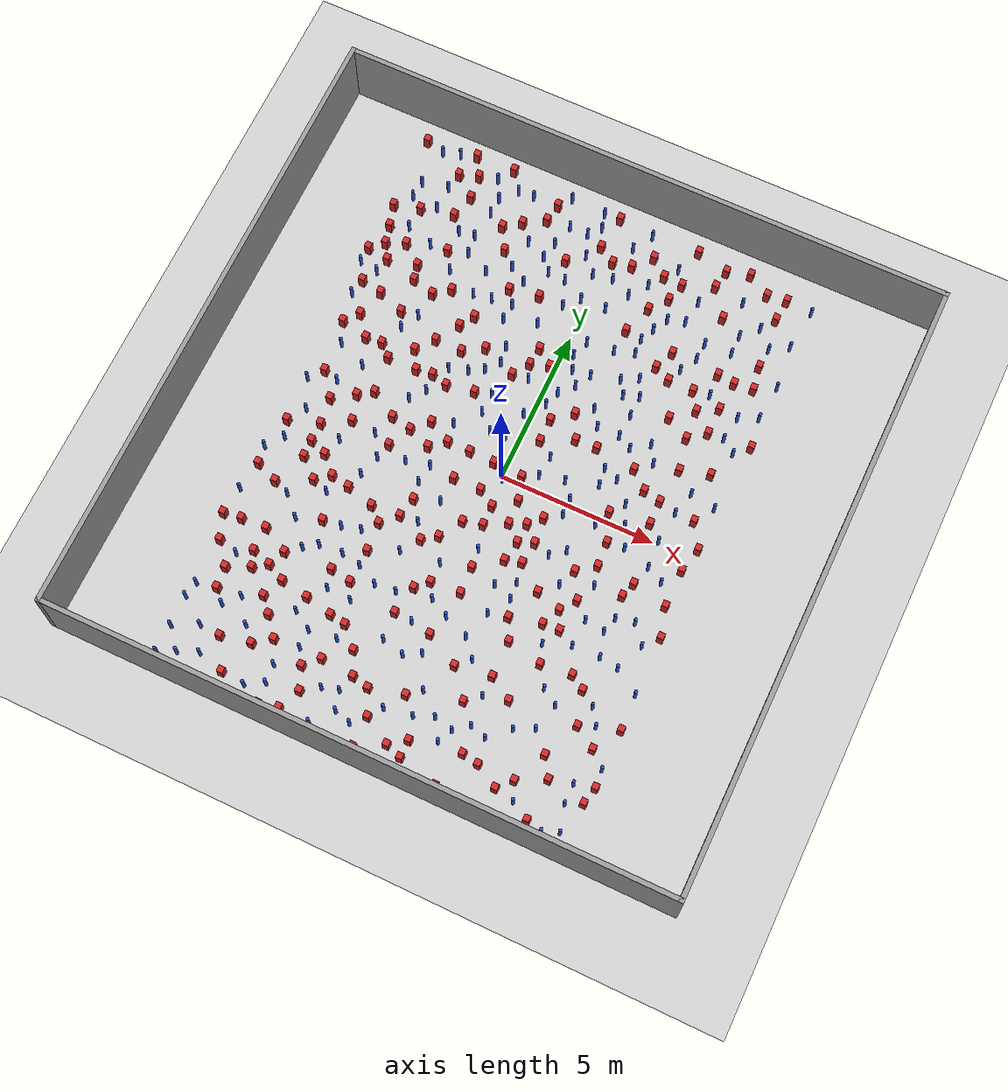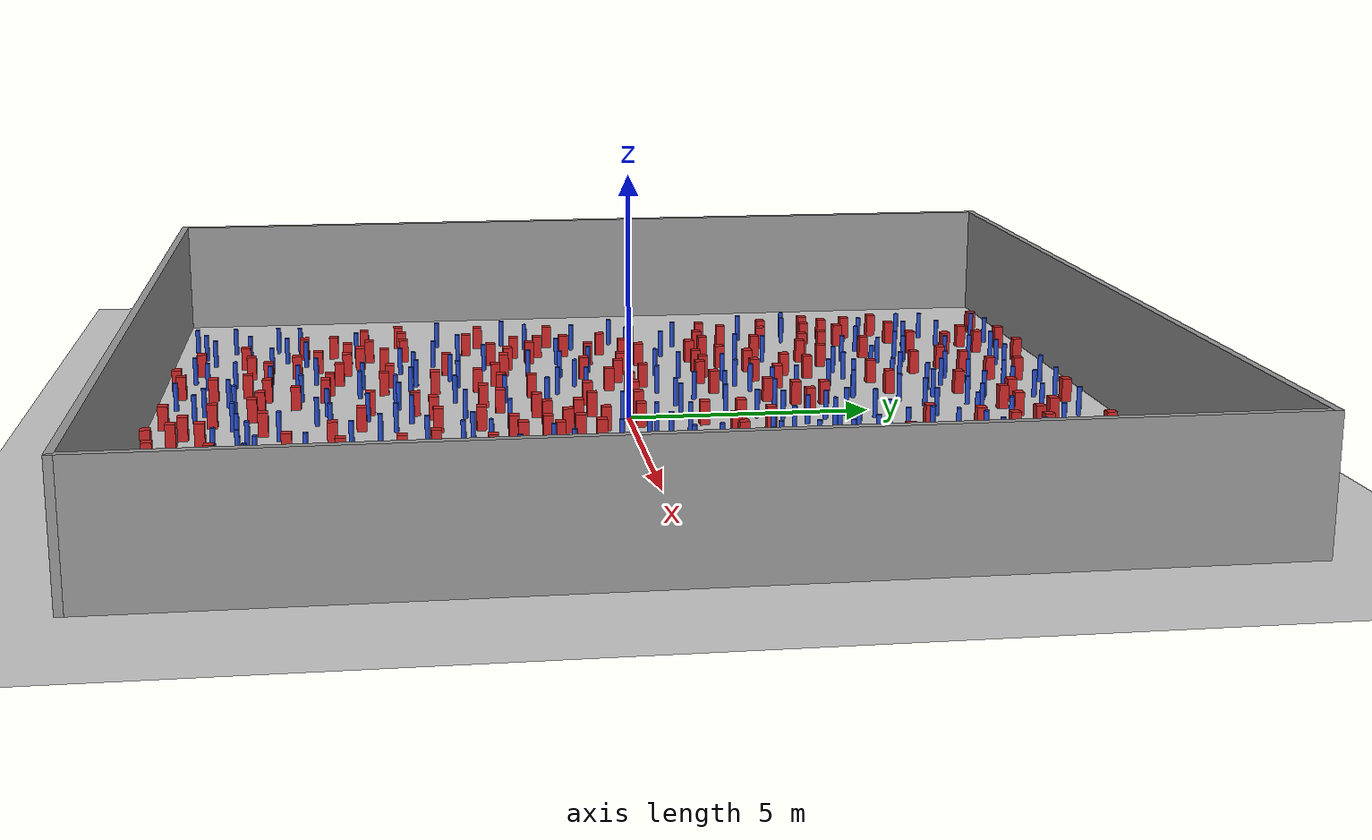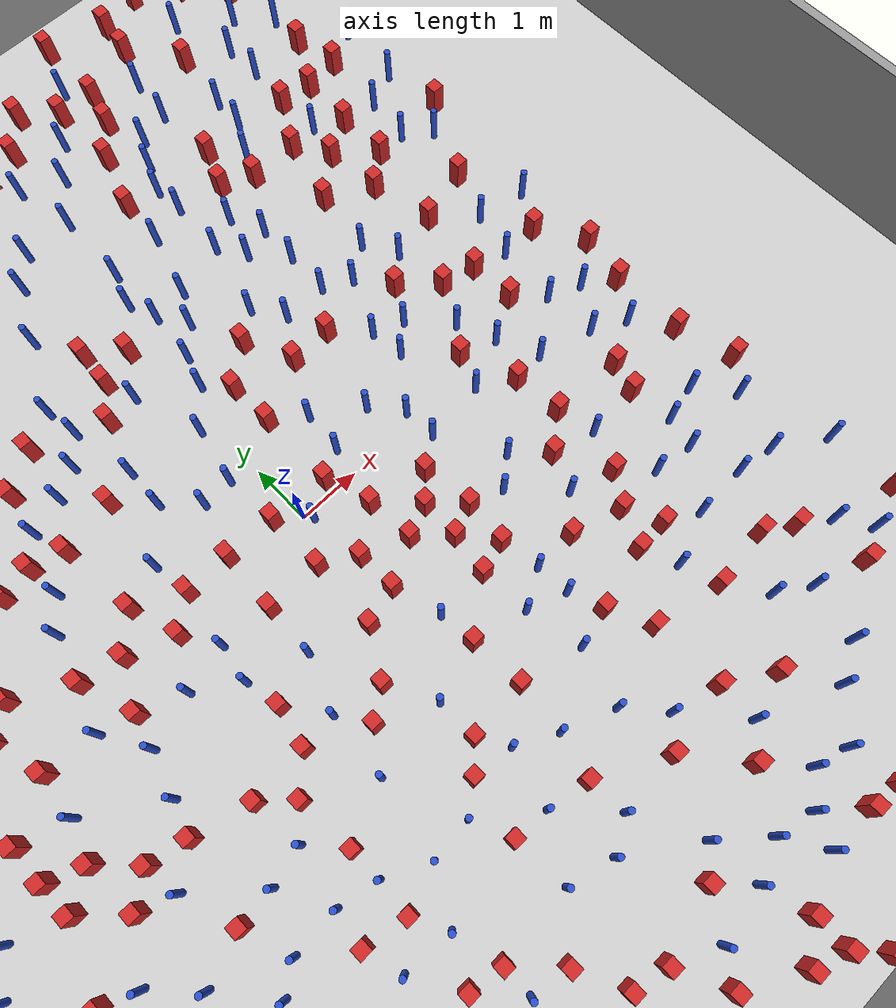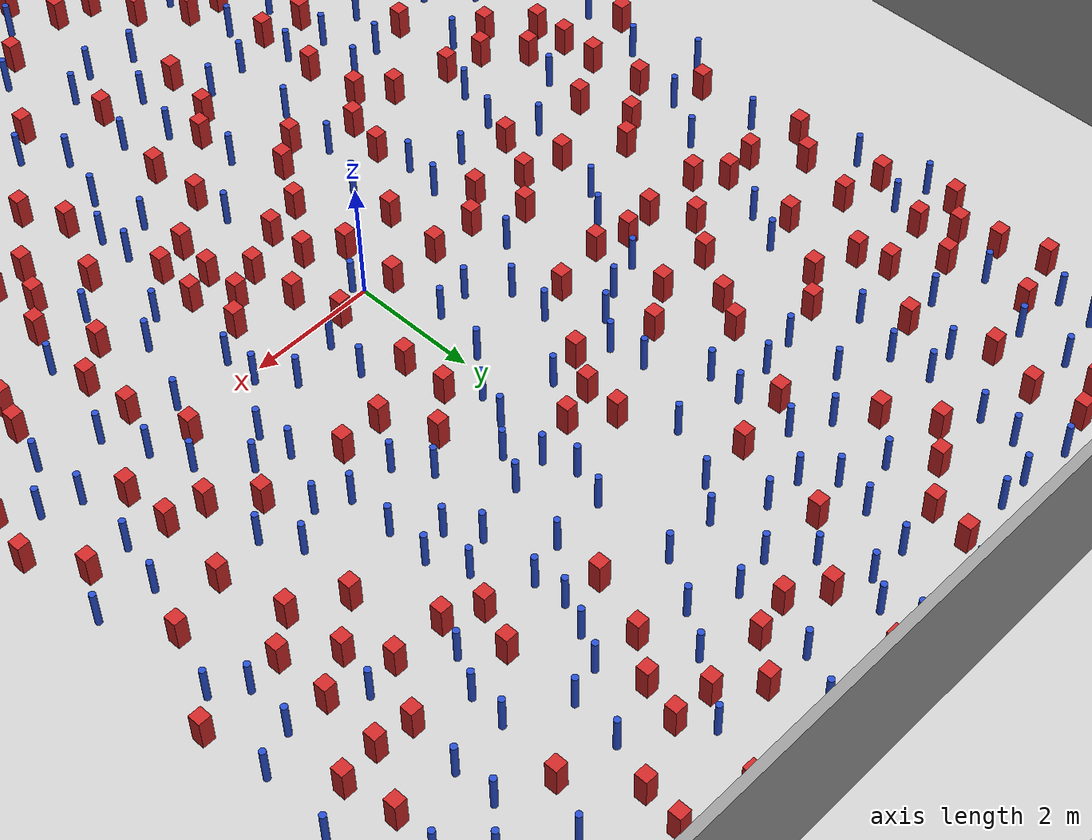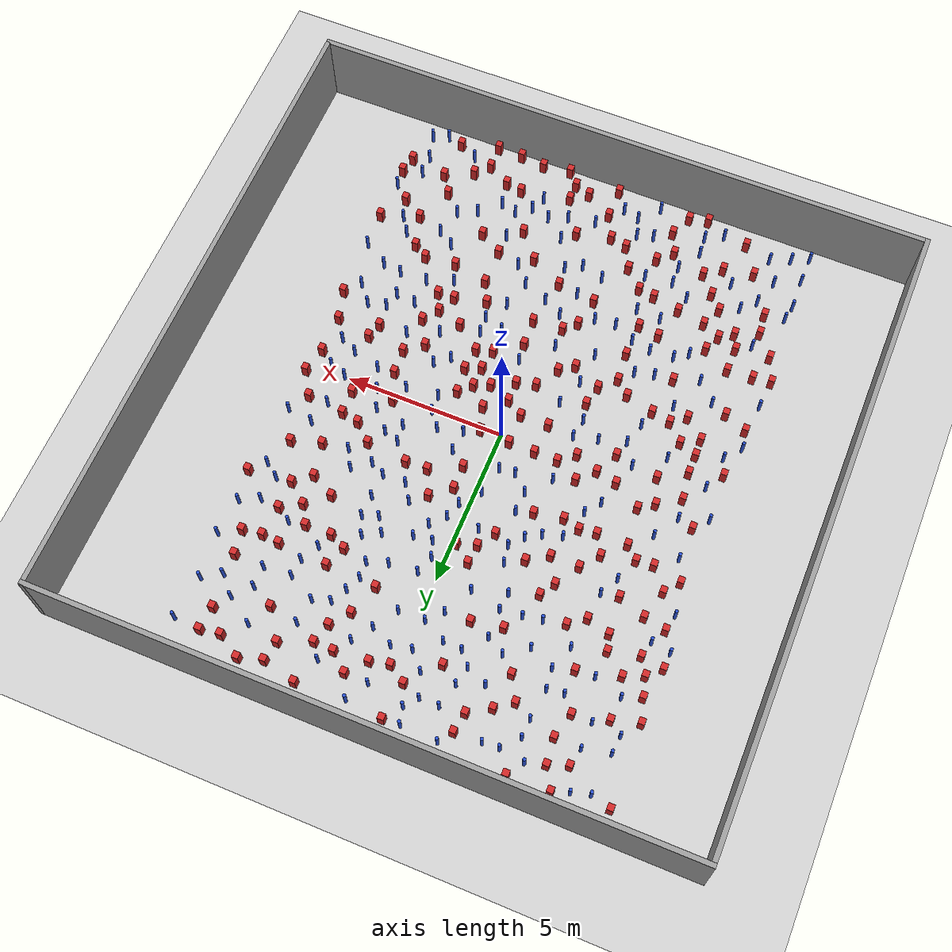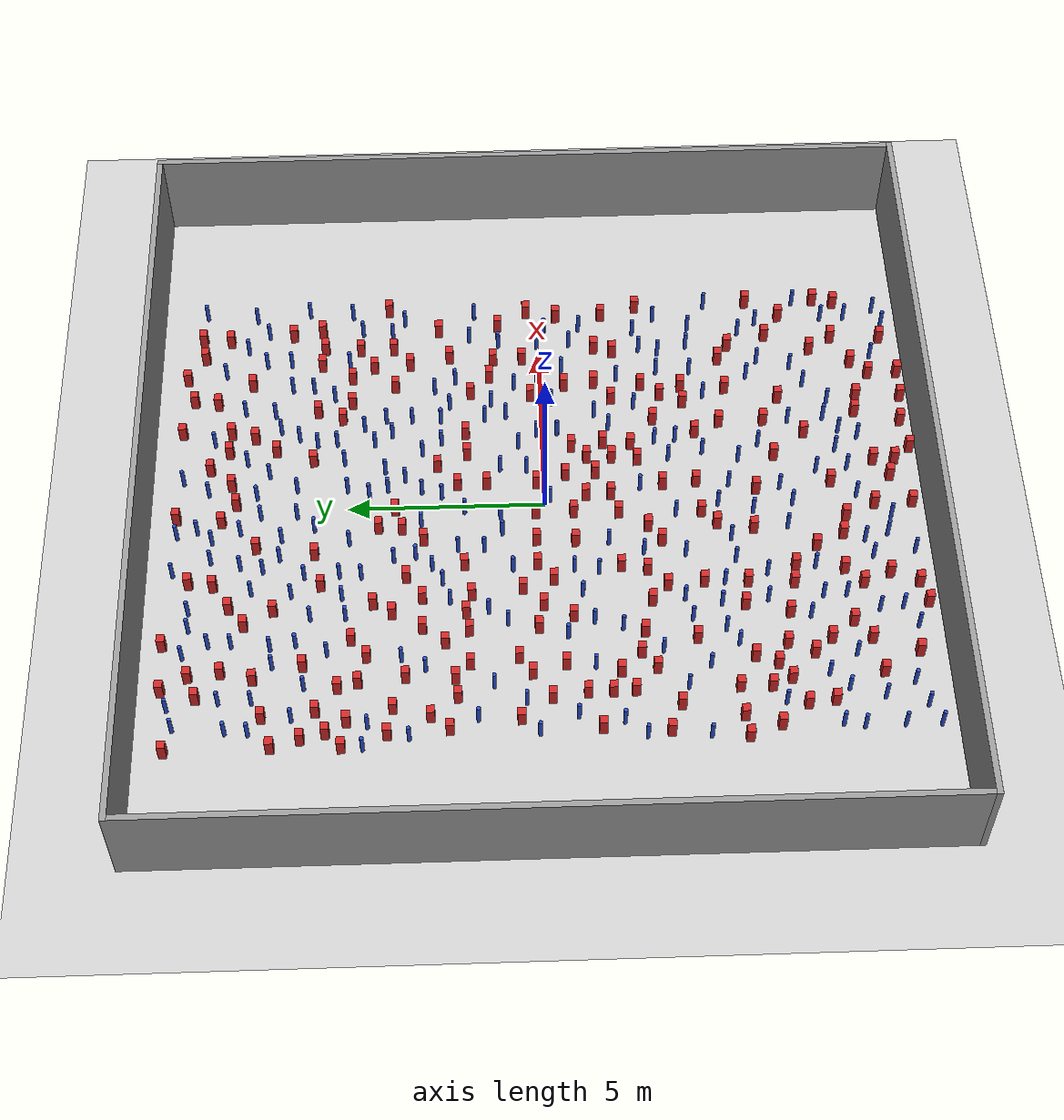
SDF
<sdf version="1.6">
 <world name="default">
  <light name="sun" type="directional">
   <pose>0 0 1000 0 -0 0</pose>
   <diffuse>0.8 0.8 0.8 1</diffuse>
   <specular>0.1 0.1 0.1 1</specular>
   <attenuation>
    <range>1000</range>
    <constant>0.9</constant>
    <linear>0.01</linear>
    <quadratic>0.001</quadratic>
   </attenuation>
   <direction>-0.5 0.5 -1</direction>
  </light>
  <model name="ground_plane">
   <static>1</static>
   <link name="link">
    <collision name="collision">
     <geometry><plane><normal>0 0 1</normal><size>100 100</size></plane></geometry>
     <surface><friction><ode><mu>100</mu><mu2>50</mu2></ode></friction></surface>
    </collision>
    <visual name="visual">
     <cast_shadows>0</cast_shadows>
     <geometry><plane><normal>0 0 1</normal><size>100 100</size></plane></geometry>
     <material>
      <ambient>1.0 1.0 1.0 1.0</ambient>
      <diffuse>0.8 0.8 0.8 1.0</diffuse>
      <specular>0.01 0.01 0.01 1.000000</specular>
     </material>
    </visual>
   </link>
  </model>
  <gravity>0 0 -9.8</gravity>
  <magnetic_field>6e-06 2.3e-05 -4.2e-05</magnetic_field>
  <atmosphere type="adiabatic"/>
  <physics name="default_physics" default="0" type="ode">
   <max_step_size>0.001</max_step_size>
   <real_time_factor>1</real_time_factor>
   <real_time_update_rate>1000</real_time_update_rate>
  </physics>
  <scene><ambient>0.4 0.4 0.4 1</ambient><background>0.7 0.7 0.7 1</background><shadows>1</shadows></scene>
  <spherical_coordinates>
   <surface_model>EARTH_WGS84</surface_model>
   <latitude_deg>0</latitude_deg>
   <longitude_deg>0</longitude_deg>
   <elevation>0</elevation>
   <heading_deg>0</heading_deg>
  </spherical_coordinates>
  <plugin name="gazebo_occupancy_map" filename="libgazebo_2Dmap_plugin.so">
   <map_resolution>0.05</map_resolution>
   <map_topic>generated_map</map_topic>
   <map_height>0.01</map_height>
   <map_size_x>50</map_size_x>
   <map_size_y>50</map_size_y>
  </plugin>
  <model name="NamedLocations">
   <static>true</static>
   <link name="DefaultStart"><pose>8.5 0 0 0 0 3.14</pose></link>
  </model>
  <model name="20x20_walls">
   <pose>0.044518 0.176112 0 0 -0 0</pose>
   <link name="Wall_1">
    <collision name="Wall_1_Collision">
     <geometry><box><size>20 0.15 2.5</size></box></geometry>
     <pose>0 0 1.25 0 -0 0</pose>
    </collision>
    <visual name="Wall_1_Visual">
     <pose>0 0 1.25 0 -0 0</pose>
     <geometry><box><size>20 0.15 2.5</size></box></geometry>
     <material>
      <script><uri>file://media/materials/scripts/gazebo.material</uri><name>Gazebo/Grey</name></script>
      <ambient>0.976471 0.992157 1 1</ambient>
     </material>
     <meta><layer>0</layer></meta>
    </visual>
    <pose>0 9.925 0 0 -0 0</pose>
   </link>
   <link name="Wall_3">
    <collision name="Wall_3_Collision">
     <geometry><box><size>20 0.15 2.5</size></box></geometry>
     <pose>0 0 1.25 0 -0 0</pose>
    </collision>
    <visual name="Wall_3_Visual">
     <pose>0 0 1.25 0 -0 0</pose>
     <geometry><box><size>20 0.15 2.5</size></box></geometry>
     <material>
      <script><uri>file://media/materials/scripts/gazebo.material</uri><name>Gazebo/Grey</name></script>
      <ambient>0.976471 0.992157 1 1</ambient>
     </material>
     <meta><layer>0</layer></meta>
    </visual>
    <pose>9.925 0 0 0 0 -1.5708</pose>
   </link>
   <link name="Wall_4">
    <collision name="Wall_4_Collision">
     <geometry><box><size>20 0.15 2.5</size></box></geometry>
     <pose>0 0 1.25 0 -0 0</pose>
    </collision>
    <visual name="Wall_4_Visual">
     <pose>0 0 1.25 0 -0 0</pose>
     <geometry><box><size>20 0.15 2.5</size></box></geometry>
     <material>
      <script><uri>file://media/materials/scripts/gazebo.material</uri><name>Gazebo/Grey</name></script>
      <ambient>0.976471 0.992157 1 1</ambient>
     </material>
     <meta><layer>0</layer></meta>
    </visual>
    <pose>0 -9.925 0 0 -0 3.14159</pose>
   </link>
   <link name="Wall_5">
    <collision name="Wall_5_Collision">
     <geometry><box><size>20 0.15 2.5</size></box></geometry>
     <pose>0 0 1.25 0 -0 0</pose>
    </collision>
    <visual name="Wall_5_Visual">
     <pose>0 0 1.25 0 -0 0</pose>
     <geometry><box><size>20 0.15 2.5</size></box></geometry>
     <material>
      <script><uri>file://media/materials/scripts/gazebo.material</uri><name>Gazebo/Grey</name></script>
      <ambient>0.976471 0.992157 1 1</ambient>
     </material>
     <meta><layer>0</layer></meta>
    </visual>
    <pose>-9.925 0 0 0 -0 1.5708</pose>
   </link>
   <static>1</static>
  </model>
  <model name="pole_obstacle0">
   <static>true</static>
   <pose>-0.228434061934 6.29204529232 7.38925637345e-09 -8.47170692799e-08 1.2497676507e-08 -1.74513093018e-07</pose>
   <link name="link">
    <pose>0 0 0.3 0 -0 0</pose>
    <inertial>
     <mass>1</mass>
     <inertia><ixx>0.145833</ixx><ixy>0</ixy><ixz>0</ixz><iyy>0.145833</iyy><iyz>0</iyz><izz>0.125</izz></inertia>
    </inertial>
    <collision name="collision">
     <geometry><cylinder><radius>0.05</radius><length>.6</length></cylinder></geometry>
    </collision>
    <visual name="visual">
     <geometry><cylinder><radius>0.05</radius><length>.6</length></cylinder></geometry>
     <material>
      <script><name>Gazebo/Blue</name><uri>file://media/materials/scripts/gazebo.material</uri></script>
     </material>
    </visual>
   </link>
  </model>
  <model name="pole_obstacle1">
   <static>true</static>
   <pose>1.99328007282 4.33544630047 7.38925637345e-09 -8.471706928e-08 1.24976765202e-08 -1.7451309301e-07</pose>
   <link name="link">
    <pose>0 0 0.3 0 -0 0</pose>
    <inertial>
     <mass>1</mass>
     <inertia><ixx>0.145833</ixx><ixy>0</ixy><ixz>0</ixz><iyy>0.145833</iyy><iyz>0</iyz><izz>0.125</izz></inertia>
    </inertial>
    <collision name="collision">
     <geometry><cylinder><radius>0.05</radius><length>.6</length></cylinder></geometry>
    </collision>
    <visual name="visual">
     <geometry><cylinder><radius>0.05</radius><length>.6</length></cylinder></geometry>
     <material>
      <script><name>Gazebo/Blue</name><uri>file://media/materials/scripts/gazebo.material</uri></script>
     </material>
    </visual>
   </link>
  </model>
  <model name="square_post_obstacle0">
   <static>true</static>
   <pose>-0.304805739064 -8.38422856579 1.91545236811e-07 -7.35059704564e-06 1.12565212e-07 2.39332434364e-05</pose>
   <link name="link">
    <pose>0 0 0.25 0 -0 0</pose>
    <inertial>
     <mass>100</mass>
     <inertia>
      <ixx>0.166667</ixx>
      <ixy>0</ixy>
      <ixz>0</ixz>
      <iyy>0.166667</iyy>
      <iyz>0</iyz>
      <izz>0.166667</izz>
     </inertia>
    </inertial>
    <collision name="collision"><geometry><box><size>.2 .2 .5</size></box></geometry></collision>
    <visual name="visual">
     <geometry><box><size>.2 .2 .5</size></box></geometry>
     <material>
      <script><name>Gazebo/Red</name><uri>file://media/materials/scripts/gazebo.material</uri></script>
     </material>
    </visual>
   </link>
  </model>
  <model name="square_post_obstacle1">
   <static>true</static>
   <pose>2.44332004762 -5.77742656354 1.91545236811e-07 -7.35059704564e-06 1.12565212e-07 2.39332434364e-05</pose>
   <link name="link">
    <pose>0 0 0.25 0 -0 0</pose>
    <inertial>
     <mass>100</mass>
     <inertia>
      <ixx>0.166667</ixx>
      <ixy>0</ixy>
      <ixz>0</ixz>
      <iyy>0.166667</iyy>
      <iyz>0</iyz>
      <izz>0.166667</izz>
     </inertia>
    </inertial>
    <collision name="collision"><geometry><box><size>.2 .2 .5</size></box></geometry></collision>
    <visual name="visual">
     <geometry><box><size>.2 .2 .5</size></box></geometry>
     <material>
      <script><name>Gazebo/Red</name><uri>file://media/materials/scripts/gazebo.material</uri></script>
     </material>
    </visual>
   </link>
  </model>
  <model name="pole_obstacle2">
   <static>true</static>
   <pose>5.89130835126 -8.27158519056 7.38925637345e-09 -8.471706928e-08 1.24976765081e-08 -1.74513093015e-07</pose>
   <link name="link">
    <pose>0 0 0.3 0 -0 0</pose>
    <inertial>
     <mass>1</mass>
     <inertia><ixx>0.145833</ixx><ixy>0</ixy><ixz>0</ixz><iyy>0.145833</iyy><iyz>0</iyz><izz>0.125</izz></inertia>
    </inertial>
    <collision name="collision">
     <geometry><cylinder><radius>0.05</radius><length>.6</length></cylinder></geometry>
    </collision>
    <visual name="visual">
     <geometry><cylinder><radius>0.05</radius><length>.6</length></cylinder></geometry>
     <material>
      <script><name>Gazebo/Blue</name><uri>file://media/materials/scripts/gazebo.material</uri></script>
     </material>
    </visual>
   </link>
  </model>
  <model name="pole_obstacle3">
   <static>true</static>
   <pose>-6.34380081487 9.1127951825 7.38925637345e-09 -8.471706928e-08 1.24976765081e-08 -1.74513093015e-07</pose>
   <link name="link">
    <pose>0 0 0.3 0 -0 0</pose>
    <inertial>
     <mass>1</mass>
     <inertia><ixx>0.145833</ixx><ixy>0</ixy><ixz>0</ixz><iyy>0.145833</iyy><iyz>0</iyz><izz>0.125</izz></inertia>
    </inertial>
    <collision name="collision">
     <geometry><cylinder><radius>0.05</radius><length>.6</length></cylinder></geometry>
    </collision>
    <visual name="visual">
     <geometry><cylinder><radius>0.05</radius><length>.6</length></cylinder></geometry>
     <material>
      <script><name>Gazebo/Blue</name><uri>file://media/materials/scripts/gazebo.material</uri></script>
     </material>
    </visual>
   </link>
  </model>
  <model name="pole_obstacle4">
   <static>true</static>
   <pose>-6.85809004613 -2.21721014022 7.38925637345e-09 -8.47170692798e-08 1.24976764937e-08 -1.74513093023e-07</pose>
   <link name="link">
    <pose>0 0 0.3 0 -0 0</pose>
    <inertial>
     <mass>1</mass>
     <inertia><ixx>0.145833</ixx><ixy>0</ixy><ixz>0</ixz><iyy>0.145833</iyy><iyz>0</iyz><izz>0.125</izz></inertia>
    </inertial>
    <collision name="collision">
     <geometry><cylinder><radius>0.05</radius><length>.6</length></cylinder></geometry>
    </collision>
    <visual name="visual">
     <geometry><cylinder><radius>0.05</radius><length>.6</length></cylinder></geometry>
     <material>
      <script><name>Gazebo/Blue</name><uri>file://media/materials/scripts/gazebo.material</uri></script>
     </material>
    </visual>
   </link>
  </model>
  <model name="pole_obstacle5">
   <static>true</static>
   <pose>-1.21229855243 -8.62259796271 7.38925637345e-09 -8.47170692798e-08 1.24976764881e-08 -1.74513093027e-07</pose>
   <link name="link">
    <pose>0 0 0.3 0 -0 0</pose>
    <inertial>
     <mass>1</mass>
     <inertia><ixx>0.145833</ixx><ixy>0</ixy><ixz>0</ixz><iyy>0.145833</iyy><iyz>0</iyz><izz>0.125</izz></inertia>
    </inertial>
    <collision name="collision">
     <geometry><cylinder><radius>0.05</radius><length>.6</length></cylinder></geometry>
    </collision>
    <visual name="visual">
     <geometry><cylinder><radius>0.05</radius><length>.6</length></cylinder></geometry>
     <material>
      <script><name>Gazebo/Blue</name><uri>file://media/materials/scripts/gazebo.material</uri></script>
     </material>
    </visual>
   </link>
  </model>
  <model name="pole_obstacle6">
   <static>true</static>
   <pose>2.22442728239 6.29119405473 7.38925637345e-09 -8.47170692798e-08 1.24976765033e-08 -1.74513093019e-07</pose>
   <link name="link">
    <pose>0 0 0.3 0 -0 0</pose>
    <inertial>
     <mass>1</mass>
     <inertia><ixx>0.145833</ixx><ixy>0</ixy><ixz>0</ixz><iyy>0.145833</iyy><iyz>0</iyz><izz>0.125</izz></inertia>
    </inertial>
    <collision name="collision">
     <geometry><cylinder><radius>0.05</radius><length>.6</length></cylinder></geometry>
    </collision>
    <visual name="visual">
     <geometry><cylinder><radius>0.05</radius><length>.6</length></cylinder></geometry>
     <material>
      <script><name>Gazebo/Blue</name><uri>file://media/materials/scripts/gazebo.material</uri></script>
     </material>
    </visual>
   </link>
  </model>
  <model name="square_post_obstacle2">
   <static>true</static>
   <pose>6.3926269093 -2.64157302323 1.91545236811e-07 -7.35059704564e-06 1.12565212e-07 2.39332434364e-05</pose>
   <link name="link">
    <pose>0 0 0.25 0 -0 0</pose>
    <inertial>
     <mass>100</mass>
     <inertia>
      <ixx>0.166667</ixx>
      <ixy>0</ixy>
      <ixz>0</ixz>
      <iyy>0.166667</iyy>
      <iyz>0</iyz>
      <izz>0.166667</izz>
     </inertia>
    </inertial>
    <collision name="collision"><geometry><box><size>.2 .2 .5</size></box></geometry></collision>
    <visual name="visual">
     <geometry><box><size>.2 .2 .5</size></box></geometry>
     <material>
      <script><name>Gazebo/Red</name><uri>file://media/materials/scripts/gazebo.material</uri></script>
     </material>
    </visual>
   </link>
  </model>
  <model name="square_post_obstacle3">
   <static>true</static>
   <pose>3.27385072812 -1.84511736935 1.91545236811e-07 -7.35059704564e-06 1.12565212e-07 2.39332434364e-05</pose>
   <link name="link">
    <pose>0 0 0.25 0 -0 0</pose>
    <inertial>
     <mass>100</mass>
     <inertia>
      <ixx>0.166667</ixx>
      <ixy>0</ixy>
      <ixz>0</ixz>
      <iyy>0.166667</iyy>
      <iyz>0</iyz>
      <izz>0.166667</izz>
     </inertia>
    </inertial>
    <collision name="collision"><geometry><box><size>.2 .2 .5</size></box></geometry></collision>
    <visual name="visual">
     <geometry><box><size>.2 .2 .5</size></box></geometry>
     <material>
      <script><name>Gazebo/Red</name><uri>file://media/materials/scripts/gazebo.material</uri></script>
     </material>
    </visual>
   </link>
  </model>
  <model name="square_post_obstacle4">
   <static>true</static>
   <pose>-1.89748749856 0.251138734312 1.91545236811e-07 -7.35059704564e-06 1.12565212e-07 2.39332434364e-05</pose>
   <link name="link">
    <pose>0 0 0.25 0 -0 0</pose>
    <inertial>
     <mass>100</mass>
     <inertia>
      <ixx>0.166667</ixx>
      <ixy>0</ixy>
      <ixz>0</ixz>
      <iyy>0.166667</iyy>
      <iyz>0</iyz>
      <izz>0.166667</izz>
     </inertia>
    </inertial>
    <collision name="collision"><geometry><box><size>.2 .2 .5</size></box></geometry></collision>
    <visual name="visual">
     <geometry><box><size>.2 .2 .5</size></box></geometry>
     <material>
      <script><name>Gazebo/Red</name><uri>file://media/materials/scripts/gazebo.material</uri></script>
     </material>
    </visual>
   </link>
  </model>
  <model name="pole_obstacle7">
   <static>true</static>
   <pose>3.82240901728 5.94968930159 7.38925637345e-09 -8.47170692798e-08 1.24976765033e-08 -1.74513093019e-07</pose>
   <link name="link">
    <pose>0 0 0.3 0 -0 0</pose>
    <inertial>
     <mass>1</mass>
     <inertia><ixx>0.145833</ixx><ixy>0</ixy><ixz>0</ixz><iyy>0.145833</iyy><iyz>0</iyz><izz>0.125</izz></inertia>
    </inertial>
    <collision name="collision">
     <geometry><cylinder><radius>0.05</radius><length>.6</length></cylinder></geometry>
    </collision>
    <visual name="visual">
     <geometry><cylinder><radius>0.05</radius><length>.6</length></cylinder></geometry>
     <material>
      <script><name>Gazebo/Blue</name><uri>file://media/materials/scripts/gazebo.material</uri></script>
     </material>
    </visual>
   </link>
  </model>
  <model name="pole_obstacle8">
   <static>true</static>
   <pose>-1.38622224824 -8.02949995866 7.38925637345e-09 -8.47170692794e-08 1.24976764551e-08 -1.74513093044e-07</pose>
   <link name="link">
    <pose>0 0 0.3 0 -0 0</pose>
    <inertial>
     <mass>1</mass>
     <inertia><ixx>0.145833</ixx><ixy>0</ixy><ixz>0</ixz><iyy>0.145833</iyy><iyz>0</iyz><izz>0.125</izz></inertia>
    </inertial>
    <collision name="collision">
     <geometry><cylinder><radius>0.05</radius><length>.6</length></cylinder></geometry>
    </collision>
    <visual name="visual">
     <geometry><cylinder><radius>0.05</radius><length>.6</length></cylinder></geometry>
     <material>
      <script><name>Gazebo/Blue</name><uri>file://media/materials/scripts/gazebo.material</uri></script>
     </material>
    </visual>
   </link>
  </model>
  <model name="square_post_obstacle5">
   <static>true</static>
   <pose>-4.62227693699 0.775634140724 1.91545236811e-07 -7.35059704564e-06 1.12565212e-07 2.39332434364e-05</pose>
   <link name="link">
    <pose>0 0 0.25 0 -0 0</pose>
    <inertial>
     <mass>100</mass>
     <inertia>
      <ixx>0.166667</ixx>
      <ixy>0</ixy>
      <ixz>0</ixz>
      <iyy>0.166667</iyy>
      <iyz>0</iyz>
      <izz>0.166667</izz>
     </inertia>
    </inertial>
    <collision name="collision"><geometry><box><size>.2 .2 .5</size></box></geometry></collision>
    <visual name="visual">
     <geometry><box><size>.2 .2 .5</size></box></geometry>
     <material>
      <script><name>Gazebo/Red</name><uri>file://media/materials/scripts/gazebo.material</uri></script>
     </material>
    </visual>
   </link>
  </model>
  <model name="square_post_obstacle6">
   <static>true</static>
   <pose>6.1314204804 -1.70435228454 1.91545236811e-07 -7.35059704564e-06 1.12565212e-07 2.39332434364e-05</pose>
   <link name="link">
    <pose>0 0 0.25 0 -0 0</pose>
    <inertial>
     <mass>100</mass>
     <inertia>
      <ixx>0.166667</ixx>
      <ixy>0</ixy>
      <ixz>0</ixz>
      <iyy>0.166667</iyy>
      <iyz>0</iyz>
      <izz>0.166667</izz>
     </inertia>
    </inertial>
    <collision name="collision"><geometry><box><size>.2 .2 .5</size></box></geometry></collision>
    <visual name="visual">
     <geometry><box><size>.2 .2 .5</size></box></geometry>
     <material>
      <script><name>Gazebo/Red</name><uri>file://media/materials/scripts/gazebo.material</uri></script>
     </material>
    </visual>
   </link>
  </model>
  <model name="square_post_obstacle7">
   <static>true</static>
   <pose>-5.04372002364 7.2401039024 1.91545236811e-07 -7.35059704564e-06 1.12565212e-07 2.39332434364e-05</pose>
   <link name="link">
    <pose>0 0 0.25 0 -0 0</pose>
    <inertial>
     <mass>100</mass>
     <inertia>
      <ixx>0.166667</ixx>
      <ixy>0</ixy>
      <ixz>0</ixz>
      <iyy>0.166667</iyy>
      <iyz>0</iyz>
      <izz>0.166667</izz>
     </inertia>
    </inertial>
    <collision name="collision"><geometry><box><size>.2 .2 .5</size></box></geometry></collision>
    <visual name="visual">
     <geometry><box><size>.2 .2 .5</size></box></geometry>
     <material>
      <script><name>Gazebo/Red</name><uri>file://media/materials/scripts/gazebo.material</uri></script>
     </material>
    </visual>
   </link>
  </model>
  <model name="pole_obstacle9">
   <static>true</static>
   <pose>3.03887440964 -2.42761712967 7.38925637345e-09 -8.47170692798e-08 1.24976764939e-08 -1.74513093025e-07</pose>
   <link name="link">
    <pose>0 0 0.3 0 -0 0</pose>
    <inertial>
     <mass>1</mass>
     <inertia><ixx>0.145833</ixx><ixy>0</ixy><ixz>0</ixz><iyy>0.145833</iyy><iyz>0</iyz><izz>0.125</izz></inertia>
    </inertial>
    <collision name="collision">
     <geometry><cylinder><radius>0.05</radius><length>.6</length></cylinder></geometry>
    </collision>
    <visual name="visual">
     <geometry><cylinder><radius>0.05</radius><length>.6</length></cylinder></geometry>
     <material>
      <script><name>Gazebo/Blue</name><uri>file://media/materials/scripts/gazebo.material</uri></script>
     </material>
    </visual>
   </link>
  </model>
  <model name="pole_obstacle10">
   <static>true</static>
   <pose>5.61337096188 -9.26001587438 7.38925637345e-09 -8.471706928e-08 1.24976765081e-08 -1.74513093015e-07</pose>
   <link name="link">
    <pose>0 0 0.3 0 -0 0</pose>
    <inertial>
     <mass>1</mass>
     <inertia><ixx>0.145833</ixx><ixy>0</ixy><ixz>0</ixz><iyy>0.145833</iyy><iyz>0</iyz><izz>0.125</izz></inertia>
    </inertial>
    <collision name="collision">
     <geometry><cylinder><radius>0.05</radius><length>.6</length></cylinder></geometry>
    </collision>
    <visual name="visual">
     <geometry><cylinder><radius>0.05</radius><length>.6</length></cylinder></geometry>
     <material>
      <script><name>Gazebo/Blue</name><uri>file://media/materials/scripts/gazebo.material</uri></script>
     </material>
    </visual>
   </link>
  </model>
  <model name="pole_obstacle11">
   <static>true</static>
   <pose>-5.84389258286 0.627708138282 7.38925637345e-09 -8.47170692799e-08 1.24976765038e-08 -1.74513093018e-07</pose>
   <link name="link">
    <pose>0 0 0.3 0 -0 0</pose>
    <inertial>
     <mass>1</mass>
     <inertia><ixx>0.145833</ixx><ixy>0</ixy><ixz>0</ixz><iyy>0.145833</iyy><iyz>0</iyz><izz>0.125</izz></inertia>
    </inertial>
    <collision name="collision">
     <geometry><cylinder><radius>0.05</radius><length>.6</length></cylinder></geometry>
    </collision>
    <visual name="visual">
     <geometry><cylinder><radius>0.05</radius><length>.6</length></cylinder></geometry>
     <material>
      <script><name>Gazebo/Blue</name><uri>file://media/materials/scripts/gazebo.material</uri></script>
     </material>
    </visual>
   </link>
  </model>
  <model name="pole_obstacle12">
   <static>true</static>
   <pose>-0.773788913742 9.30930106221 7.38925637345e-09 -8.47170692797e-08 1.249767648e-08 -1.74513093032e-07</pose>
   <link name="link">
    <pose>0 0 0.3 0 -0 0</pose>
    <inertial>
     <mass>1</mass>
     <inertia><ixx>0.145833</ixx><ixy>0</ixy><ixz>0</ixz><iyy>0.145833</iyy><iyz>0</iyz><izz>0.125</izz></inertia>
    </inertial>
    <collision name="collision">
     <geometry><cylinder><radius>0.05</radius><length>.6</length></cylinder></geometry>
    </collision>
    <visual name="visual">
     <geometry><cylinder><radius>0.05</radius><length>.6</length></cylinder></geometry>
     <material>
      <script><name>Gazebo/Blue</name><uri>file://media/materials/scripts/gazebo.material</uri></script>
     </material>
    </visual>
   </link>
  </model>
  <model name="square_post_obstacle8">
   <static>true</static>
   <pose>-3.99911726204 9.4823268455 1.91545236811e-07 -7.35059704564e-06 1.12565212e-07 2.39332434364e-05</pose>
   <link name="link">
    <pose>0 0 0.25 0 -0 0</pose>
    <inertial>
     <mass>100</mass>
     <inertia>
      <ixx>0.166667</ixx>
      <ixy>0</ixy>
      <ixz>0</ixz>
      <iyy>0.166667</iyy>
      <iyz>0</iyz>
      <izz>0.166667</izz>
     </inertia>
    </inertial>
    <collision name="collision"><geometry><box><size>.2 .2 .5</size></box></geometry></collision>
    <visual name="visual">
     <geometry><box><size>.2 .2 .5</size></box></geometry>
     <material>
      <script><name>Gazebo/Red</name><uri>file://media/materials/scripts/gazebo.material</uri></script>
     </material>
    </visual>
   </link>
  </model>
  <model name="square_post_obstacle9">
   <static>true</static>
   <pose>-3.08719825203 6.80727021895 1.91545236811e-07 -7.35059704564e-06 1.12565212e-07 2.39332434364e-05</pose>
   <link name="link">
    <pose>0 0 0.25 0 -0 0</pose>
    <inertial>
     <mass>100</mass>
     <inertia>
      <ixx>0.166667</ixx>
      <ixy>0</ixy>
      <ixz>0</ixz>
      <iyy>0.166667</iyy>
      <iyz>0</iyz>
      <izz>0.166667</izz>
     </inertia>
    </inertial>
    <collision name="collision"><geometry><box><size>.2 .2 .5</size></box></geometry></collision>
    <visual name="visual">
     <geometry><box><size>.2 .2 .5</size></box></geometry>
     <material>
      <script><name>Gazebo/Red</name><uri>file://media/materials/scripts/gazebo.material</uri></script>
     </material>
    </visual>
   </link>
  </model>
  <model name="pole_obstacle13">
   <static>true</static>
   <pose>4.53332814097 -8.83330238117 7.38925637345e-09 -8.471706928e-08 1.24976765081e-08 -1.74513093015e-07</pose>
   <link name="link">
    <pose>0 0 0.3 0 -0 0</pose>
    <inertial>
     <mass>1</mass>
     <inertia><ixx>0.145833</ixx><ixy>0</ixy><ixz>0</ixz><iyy>0.145833</iyy><iyz>0</iyz><izz>0.125</izz></inertia>
    </inertial>
    <collision name="collision">
     <geometry><cylinder><radius>0.05</radius><length>.6</length></cylinder></geometry>
    </collision>
    <visual name="visual">
     <geometry><cylinder><radius>0.05</radius><length>.6</length></cylinder></geometry>
     <material>
      <script><name>Gazebo/Blue</name><uri>file://media/materials/scripts/gazebo.material</uri></script>
     </material>
    </visual>
   </link>
  </model>
  <model name="square_post_obstacle10">
   <static>true</static>
   <pose>-0.731796114299 3.62730903629 1.91545236811e-07 -7.35059704564e-06 1.12565212e-07 2.39332434364e-05</pose>
   <link name="link">
    <pose>0 0 0.25 0 -0 0</pose>
    <inertial>
     <mass>100</mass>
     <inertia>
      <ixx>0.166667</ixx>
      <ixy>0</ixy>
      <ixz>0</ixz>
      <iyy>0.166667</iyy>
      <iyz>0</iyz>
      <izz>0.166667</izz>
     </inertia>
    </inertial>
    <collision name="collision"><geometry><box><size>.2 .2 .5</size></box></geometry></collision>
    <visual name="visual">
     <geometry><box><size>.2 .2 .5</size></box></geometry>
     <material>
      <script><name>Gazebo/Red</name><uri>file://media/materials/scripts/gazebo.material</uri></script>
     </material>
    </visual>
   </link>
  </model>
  <model name="square_post_obstacle11">
   <static>true</static>
   <pose>-5.33017767774 5.18398146413 1.91545236811e-07 -7.35059704564e-06 1.12565212e-07 2.39332434364e-05</pose>
   <link name="link">
    <pose>0 0 0.25 0 -0 0</pose>
    <inertial>
     <mass>100</mass>
     <inertia>
      <ixx>0.166667</ixx>
      <ixy>0</ixy>
      <ixz>0</ixz>
      <iyy>0.166667</iyy>
      <iyz>0</iyz>
      <izz>0.166667</izz>
     </inertia>
    </inertial>
    <collision name="collision"><geometry><box><size>.2 .2 .5</size></box></geometry></collision>
    <visual name="visual">
     <geometry><box><size>.2 .2 .5</size></box></geometry>
     <material>
      <script><name>Gazebo/Red</name><uri>file://media/materials/scripts/gazebo.material</uri></script>
     </material>
    </visual>
   </link>
  </model>
  <model name="pole_obstacle14">
   <static>true</static>
   <pose>-6.38927039839 4.45445296587 7.38925637345e-09 -8.47170692796e-08 1.24976764786e-08 -1.74513093032e-07</pose>
   <link name="link">
    <pose>0 0 0.3 0 -0 0</pose>
    <inertial>
     <mass>1</mass>
     <inertia><ixx>0.145833</ixx><ixy>0</ixy><ixz>0</ixz><iyy>0.145833</iyy><iyz>0</iyz><izz>0.125</izz></inertia>
    </inertial>
    <collision name="collision">
     <geometry><cylinder><radius>0.05</radius><length>.6</length></cylinder></geometry>
    </collision>
    <visual name="visual">
     <geometry><cylinder><radius>0.05</radius><length>.6</length></cylinder></geometry>
     <material>
      <script><name>Gazebo/Blue</name><uri>file://media/materials/scripts/gazebo.material</uri></script>
     </material>
    </visual>
   </link>
  </model>
  <model name="pole_obstacle15">
   <static>true</static>
   <pose>5.99334380468 -3.10721899709 7.38925637345e-09 -8.47170692798e-08 1.24976764937e-08 -1.74513093023e-07</pose>
   <link name="link">
    <pose>0 0 0.3 0 -0 0</pose>
    <inertial>
     <mass>1</mass>
     <inertia><ixx>0.145833</ixx><ixy>0</ixy><ixz>0</ixz><iyy>0.145833</iyy><iyz>0</iyz><izz>0.125</izz></inertia>
    </inertial>
    <collision name="collision">
     <geometry><cylinder><radius>0.05</radius><length>.6</length></cylinder></geometry>
    </collision>
    <visual name="visual">
     <geometry><cylinder><radius>0.05</radius><length>.6</length></cylinder></geometry>
     <material>
      <script><name>Gazebo/Blue</name><uri>file://media/materials/scripts/gazebo.material</uri></script>
     </material>
    </visual>
   </link>
  </model>
  <model name="square_post_obstacle12">
   <static>true</static>
   <pose>-2.81630306043 3.12755223096 1.91545236811e-07 -7.35059704564e-06 1.12565212e-07 2.39332434364e-05</pose>
   <link name="link">
    <pose>0 0 0.25 0 -0 0</pose>
    <inertial>
     <mass>100</mass>
     <inertia>
      <ixx>0.166667</ixx>
      <ixy>0</ixy>
      <ixz>0</ixz>
      <iyy>0.166667</iyy>
      <iyz>0</iyz>
      <izz>0.166667</izz>
     </inertia>
    </inertial>
    <collision name="collision"><geometry><box><size>.2 .2 .5</size></box></geometry></collision>
    <visual name="visual">
     <geometry><box><size>.2 .2 .5</size></box></geometry>
     <material>
      <script><name>Gazebo/Red</name><uri>file://media/materials/scripts/gazebo.material</uri></script>
     </material>
    </visual>
   </link>
  </model>
  <model name="pole_obstacle16">
   <static>true</static>
   <pose>-4.66239703517 6.7866188203 7.38925637345e-09 -8.47170692796e-08 1.24976764786e-08 -1.74513093032e-07</pose>
   <link name="link">
    <pose>0 0 0.3 0 -0 0</pose>
    <inertial>
     <mass>1</mass>
     <inertia><ixx>0.145833</ixx><ixy>0</ixy><ixz>0</ixz><iyy>0.145833</iyy><iyz>0</iyz><izz>0.125</izz></inertia>
    </inertial>
    <collision name="collision">
     <geometry><cylinder><radius>0.05</radius><length>.6</length></cylinder></geometry>
    </collision>
    <visual name="visual">
     <geometry><cylinder><radius>0.05</radius><length>.6</length></cylinder></geometry>
     <material>
      <script><name>Gazebo/Blue</name><uri>file://media/materials/scripts/gazebo.material</uri></script>
     </material>
    </visual>
   </link>
  </model>
  <model name="pole_obstacle17">
   <static>true</static>
   <pose>5.87889555273 -7.64180327104 7.38925637345e-09 -8.47170692796e-08 1.24976764786e-08 -1.74513093032e-07</pose>
   <link name="link">
    <pose>0 0 0.3 0 -0 0</pose>
    <inertial>
     <mass>1</mass>
     <inertia><ixx>0.145833</ixx><ixy>0</ixy><ixz>0</ixz><iyy>0.145833</iyy><iyz>0</iyz><izz>0.125</izz></inertia>
    </inertial>
    <collision name="collision">
     <geometry><cylinder><radius>0.05</radius><length>.6</length></cylinder></geometry>
    </collision>
    <visual name="visual">
     <geometry><cylinder><radius>0.05</radius><length>.6</length></cylinder></geometry>
     <material>
      <script><name>Gazebo/Blue</name><uri>file://media/materials/scripts/gazebo.material</uri></script>
     </material>
    </visual>
   </link>
  </model>
  <model name="square_post_obstacle13">
   <static>true</static>
   <pose>1.07421330765 -9.05741872693 1.91545236811e-07 -7.35059704564e-06 1.12565212e-07 2.39332434364e-05</pose>
   <link name="link">
    <pose>0 0 0.25 0 -0 0</pose>
    <inertial>
     <mass>100</mass>
     <inertia>
      <ixx>0.166667</ixx>
      <ixy>0</ixy>
      <ixz>0</ixz>
      <iyy>0.166667</iyy>
      <iyz>0</iyz>
      <izz>0.166667</izz>
     </inertia>
    </inertial>
    <collision name="collision"><geometry><box><size>.2 .2 .5</size></box></geometry></collision>
    <visual name="visual">
     <geometry><box><size>.2 .2 .5</size></box></geometry>
     <material>
      <script><name>Gazebo/Red</name><uri>file://media/materials/scripts/gazebo.material</uri></script>
     </material>
    </visual>
   </link>
  </model>
  <model name="pole_obstacle18">
   <static>true</static>
   <pose>-2.78637123942 -0.84800028102 7.38925637345e-09 -8.471706928e-08 1.24976765177e-08 -1.74513093012e-07</pose>
   <link name="link">
    <pose>0 0 0.3 0 -0 0</pose>
    <inertial>
     <mass>1</mass>
     <inertia><ixx>0.145833</ixx><ixy>0</ixy><ixz>0</ixz><iyy>0.145833</iyy><iyz>0</iyz><izz>0.125</izz></inertia>
    </inertial>
    <collision name="collision">
     <geometry><cylinder><radius>0.05</radius><length>.6</length></cylinder></geometry>
    </collision>
    <visual name="visual">
     <geometry><cylinder><radius>0.05</radius><length>.6</length></cylinder></geometry>
     <material>
      <script><name>Gazebo/Blue</name><uri>file://media/materials/scripts/gazebo.material</uri></script>
     </material>
    </visual>
   </link>
  </model>
  <model name="square_post_obstacle14">
   <static>true</static>
   <pose>-3.69880755746 3.13031229309 1.91545236811e-07 -7.35059704564e-06 1.12565212e-07 2.39332434364e-05</pose>
   <link name="link">
    <pose>0 0 0.25 0 -0 0</pose>
    <inertial>
     <mass>100</mass>
     <inertia>
      <ixx>0.166667</ixx>
      <ixy>0</ixy>
      <ixz>0</ixz>
      <iyy>0.166667</iyy>
      <iyz>0</iyz>
      <izz>0.166667</izz>
     </inertia>
    </inertial>
    <collision name="collision"><geometry><box><size>.2 .2 .5</size></box></geometry></collision>
    <visual name="visual">
     <geometry><box><size>.2 .2 .5</size></box></geometry>
     <material>
      <script><name>Gazebo/Red</name><uri>file://media/materials/scripts/gazebo.material</uri></script>
     </material>
    </visual>
   </link>
  </model>
  <model name="pole_obstacle19">
   <static>true</static>
   <pose>5.63549042282 -4.02155629917 7.38925637345e-09 -8.47170692796e-08 1.24976764791e-08 -1.74513093031e-07</pose>
   <link name="link">
    <pose>0 0 0.3 0 -0 0</pose>
    <inertial>
     <mass>1</mass>
     <inertia><ixx>0.145833</ixx><ixy>0</ixy><ixz>0</ixz><iyy>0.145833</iyy><iyz>0</iyz><izz>0.125</izz></inertia>
    </inertial>
    <collision name="collision">
     <geometry><cylinder><radius>0.05</radius><length>.6</length></cylinder></geometry>
    </collision>
    <visual name="visual">
     <geometry><cylinder><radius>0.05</radius><length>.6</length></cylinder></geometry>
     <material>
      <script><name>Gazebo/Blue</name><uri>file://media/materials/scripts/gazebo.material</uri></script>
     </material>
    </visual>
   </link>
  </model>
  <model name="square_post_obstacle15">
   <static>true</static>
   <pose>3.4902615827 9.0665282632 1.91545236811e-07 -7.35059704564e-06 1.12565212e-07 2.39332434364e-05</pose>
   <link name="link">
    <pose>0 0 0.25 0 -0 0</pose>
    <inertial>
     <mass>100</mass>
     <inertia>
      <ixx>0.166667</ixx>
      <ixy>0</ixy>
      <ixz>0</ixz>
      <iyy>0.166667</iyy>
      <iyz>0</iyz>
      <izz>0.166667</izz>
     </inertia>
    </inertial>
    <collision name="collision"><geometry><box><size>.2 .2 .5</size></box></geometry></collision>
    <visual name="visual">
     <geometry><box><size>.2 .2 .5</size></box></geometry>
     <material>
      <script><name>Gazebo/Red</name><uri>file://media/materials/scripts/gazebo.material</uri></script>
     </material>
    </visual>
   </link>
  </model>
  <model name="square_post_obstacle16">
   <static>true</static>
   <pose>2.55825330878 -2.89611396729 1.91545236811e-07 -7.35059704564e-06 1.12565212e-07 2.39332434364e-05</pose>
   <link name="link">
    <pose>0 0 0.25 0 -0 0</pose>
    <inertial>
     <mass>100</mass>
     <inertia>
      <ixx>0.166667</ixx>
      <ixy>0</ixy>
      <ixz>0</ixz>
      <iyy>0.166667</iyy>
      <iyz>0</iyz>
      <izz>0.166667</izz>
     </inertia>
    </inertial>
    <collision name="collision"><geometry><box><size>.2 .2 .5</size></box></geometry></collision>
    <visual name="visual">
     <geometry><box><size>.2 .2 .5</size></box></geometry>
     <material>
      <script><name>Gazebo/Red</name><uri>file://media/materials/scripts/gazebo.material</uri></script>
     </material>
    </visual>
   </link>
  </model>
  <model name="square_post_obstacle17">
   <static>true</static>
   <pose>-3.32777596773 -9.38484346378 1.91545236811e-07 -7.35059704564e-06 1.12565212e-07 2.39332434364e-05</pose>
   <link name="link">
    <pose>0 0 0.25 0 -0 0</pose>
    <inertial>
     <mass>100</mass>
     <inertia>
      <ixx>0.166667</ixx>
      <ixy>0</ixy>
      <ixz>0</ixz>
      <iyy>0.166667</iyy>
      <iyz>0</iyz>
      <izz>0.166667</izz>
     </inertia>
    </inertial>
    <collision name="collision"><geometry><box><size>.2 .2 .5</size></box></geometry></collision>
    <visual name="visual">
     <geometry><box><size>.2 .2 .5</size></box></geometry>
     <material>
      <script><name>Gazebo/Red</name><uri>file://media/materials/scripts/gazebo.material</uri></script>
     </material>
    </visual>
   </link>
  </model>
  <model name="pole_obstacle20">
   <static>true</static>
   <pose>2.22428863195 -0.391369599084 7.38925637345e-09 -8.471706928e-08 1.24976765172e-08 -1.74513093013e-07</pose>
   <link name="link">
    <pose>0 0 0.3 0 -0 0</pose>
    <inertial>
     <mass>1</mass>
     <inertia><ixx>0.145833</ixx><ixy>0</ixy><ixz>0</ixz><iyy>0.145833</iyy><iyz>0</iyz><izz>0.125</izz></inertia>
    </inertial>
    <collision name="collision">
     <geometry><cylinder><radius>0.05</radius><length>.6</length></cylinder></geometry>
    </collision>
    <visual name="visual">
     <geometry><cylinder><radius>0.05</radius><length>.6</length></cylinder></geometry>
     <material>
      <script><name>Gazebo/Blue</name><uri>file://media/materials/scripts/gazebo.material</uri></script>
     </material>
    </visual>
   </link>
  </model>
  <model name="pole_obstacle21">
   <static>true</static>
   <pose>5.19978586766 7.72300036047 7.38925637345e-09 -8.47170692796e-08 1.24976764786e-08 -1.74513093032e-07</pose>
   <link name="link">
    <pose>0 0 0.3 0 -0 0</pose>
    <inertial>
     <mass>1</mass>
     <inertia><ixx>0.145833</ixx><ixy>0</ixy><ixz>0</ixz><iyy>0.145833</iyy><iyz>0</iyz><izz>0.125</izz></inertia>
    </inertial>
    <collision name="collision">
     <geometry><cylinder><radius>0.05</radius><length>.6</length></cylinder></geometry>
    </collision>
    <visual name="visual">
     <geometry><cylinder><radius>0.05</radius><length>.6</length></cylinder></geometry>
     <material>
      <script><name>Gazebo/Blue</name><uri>file://media/materials/scripts/gazebo.material</uri></script>
     </material>
    </visual>
   </link>
  </model>
  <model name="pole_obstacle22">
   <static>true</static>
   <pose>-2.11474189386 4.6481504744 7.38925637345e-09 -8.47170692798e-08 1.24976765033e-08 -1.74513093019e-07</pose>
   <link name="link">
    <pose>0 0 0.3 0 -0 0</pose>
    <inertial>
     <mass>1</mass>
     <inertia><ixx>0.145833</ixx><ixy>0</ixy><ixz>0</ixz><iyy>0.145833</iyy><iyz>0</iyz><izz>0.125</izz></inertia>
    </inertial>
    <collision name="collision">
     <geometry><cylinder><radius>0.05</radius><length>.6</length></cylinder></geometry>
    </collision>
    <visual name="visual">
     <geometry><cylinder><radius>0.05</radius><length>.6</length></cylinder></geometry>
     <material>
      <script><name>Gazebo/Blue</name><uri>file://media/materials/scripts/gazebo.material</uri></script>
     </material>
    </visual>
   </link>
  </model>
  <model name="pole_obstacle23">
   <static>true</static>
   <pose>-0.202655463084 2.04438907129 7.38925637345e-09 -8.47170692797e-08 1.24976764929e-08 -1.74513093024e-07</pose>
   <link name="link">
    <pose>0 0 0.3 0 -0 0</pose>
    <inertial>
     <mass>1</mass>
     <inertia><ixx>0.145833</ixx><ixy>0</ixy><ixz>0</ixz><iyy>0.145833</iyy><iyz>0</iyz><izz>0.125</izz></inertia>
    </inertial>
    <collision name="collision">
     <geometry><cylinder><radius>0.05</radius><length>.6</length></cylinder></geometry>
    </collision>
    <visual name="visual">
     <geometry><cylinder><radius>0.05</radius><length>.6</length></cylinder></geometry>
     <material>
      <script><name>Gazebo/Blue</name><uri>file://media/materials/scripts/gazebo.material</uri></script>
     </material>
    </visual>
   </link>
  </model>
  <model name="square_post_obstacle18">
   <static>true</static>
   <pose>0.514636242237 -3.88962319908 1.91545236811e-07 -7.35059704564e-06 1.12565212e-07 2.39332434364e-05</pose>
   <link name="link">
    <pose>0 0 0.25 0 -0 0</pose>
    <inertial>
     <mass>100</mass>
     <inertia>
      <ixx>0.166667</ixx>
      <ixy>0</ixy>
      <ixz>0</ixz>
      <iyy>0.166667</iyy>
      <iyz>0</iyz>
      <izz>0.166667</izz>
     </inertia>
    </inertial>
    <collision name="collision"><geometry><box><size>.2 .2 .5</size></box></geometry></collision>
    <visual name="visual">
     <geometry><box><size>.2 .2 .5</size></box></geometry>
     <material>
      <script><name>Gazebo/Red</name><uri>file://media/materials/scripts/gazebo.material</uri></script>
     </material>
    </visual>
   </link>
  </model>
  <model name="pole_obstacle24">
   <static>true</static>
   <pose>-3.60029012766 -3.52607259981 7.38925637345e-09 -8.47170692798e-08 1.24976764939e-08 -1.74513093025e-07</pose>
   <link name="link">
    <pose>0 0 0.3 0 -0 0</pose>
    <inertial>
     <mass>1</mass>
     <inertia><ixx>0.145833</ixx><ixy>0</ixy><ixz>0</ixz><iyy>0.145833</iyy><iyz>0</iyz><izz>0.125</izz></inertia>
    </inertial>
    <collision name="collision">
     <geometry><cylinder><radius>0.05</radius><length>.6</length></cylinder></geometry>
    </collision>
    <visual name="visual">
     <geometry><cylinder><radius>0.05</radius><length>.6</length></cylinder></geometry>
     <material>
      <script><name>Gazebo/Blue</name><uri>file://media/materials/scripts/gazebo.material</uri></script>
     </material>
    </visual>
   </link>
  </model>
  <model name="pole_obstacle25">
   <static>true</static>
   <pose>2.74840885819 1.47649619067 7.38925637345e-09 -8.471706928e-08 1.24976765152e-08 -1.74513093012e-07</pose>
   <link name="link">
    <pose>0 0 0.3 0 -0 0</pose>
    <inertial>
     <mass>1</mass>
     <inertia><ixx>0.145833</ixx><ixy>0</ixy><ixz>0</ixz><iyy>0.145833</iyy><iyz>0</iyz><izz>0.125</izz></inertia>
    </inertial>
    <collision name="collision">
     <geometry><cylinder><radius>0.05</radius><length>.6</length></cylinder></geometry>
    </collision>
    <visual name="visual">
     <geometry><cylinder><radius>0.05</radius><length>.6</length></cylinder></geometry>
     <material>
      <script><name>Gazebo/Blue</name><uri>file://media/materials/scripts/gazebo.material</uri></script>
     </material>
    </visual>
   </link>
  </model>
  <model name="pole_obstacle26">
   <static>true</static>
   <pose>1.86040906656 -8.18872032764 7.38925637345e-09 -8.47170692798e-08 1.24976764881e-08 -1.74513093027e-07</pose>
   <link name="link">
    <pose>0 0 0.3 0 -0 0</pose>
    <inertial>
     <mass>1</mass>
     <inertia><ixx>0.145833</ixx><ixy>0</ixy><ixz>0</ixz><iyy>0.145833</iyy><iyz>0</iyz><izz>0.125</izz></inertia>
    </inertial>
    <collision name="collision">
     <geometry><cylinder><radius>0.05</radius><length>.6</length></cylinder></geometry>
    </collision>
    <visual name="visual">
     <geometry><cylinder><radius>0.05</radius><length>.6</length></cylinder></geometry>
     <material>
      <script><name>Gazebo/Blue</name><uri>file://media/materials/scripts/gazebo.material</uri></script>
     </material>
    </visual>
   </link>
  </model>
  <model name="pole_obstacle27">
   <static>true</static>
   <pose>4.81260913132 -3.16883547511 7.38925637345e-09 -8.47170692798e-08 1.24976764937e-08 -1.74513093023e-07</pose>
   <link name="link">
    <pose>0 0 0.3 0 -0 0</pose>
    <inertial>
     <mass>1</mass>
     <inertia><ixx>0.145833</ixx><ixy>0</ixy><ixz>0</ixz><iyy>0.145833</iyy><iyz>0</iyz><izz>0.125</izz></inertia>
    </inertial>
    <collision name="collision">
     <geometry><cylinder><radius>0.05</radius><length>.6</length></cylinder></geometry>
    </collision>
    <visual name="visual">
     <geometry><cylinder><radius>0.05</radius><length>.6</length></cylinder></geometry>
     <material>
      <script><name>Gazebo/Blue</name><uri>file://media/materials/scripts/gazebo.material</uri></script>
     </material>
    </visual>
   </link>
  </model>
  <model name="pole_obstacle28">
   <static>true</static>
   <pose>5.61331978366 3.88643642091 7.38925637345e-09 -8.47170692798e-08 1.24976764937e-08 -1.74513093023e-07</pose>
   <link name="link">
    <pose>0 0 0.3 0 -0 0</pose>
    <inertial>
     <mass>1</mass>
     <inertia><ixx>0.145833</ixx><ixy>0</ixy><ixz>0</ixz><iyy>0.145833</iyy><iyz>0</iyz><izz>0.125</izz></inertia>
    </inertial>
    <collision name="collision">
     <geometry><cylinder><radius>0.05</radius><length>.6</length></cylinder></geometry>
    </collision>
    <visual name="visual">
     <geometry><cylinder><radius>0.05</radius><length>.6</length></cylinder></geometry>
     <material>
      <script><name>Gazebo/Blue</name><uri>file://media/materials/scripts/gazebo.material</uri></script>
     </material>
    </visual>
   </link>
  </model>
  <model name="square_post_obstacle19">
   <static>true</static>
   <pose>-4.14506765037 2.57185852221 1.91545236811e-07 -7.35059704564e-06 1.12565212e-07 2.39332434364e-05</pose>
   <link name="link">
    <pose>0 0 0.25 0 -0 0</pose>
    <inertial>
     <mass>100</mass>
     <inertia>
      <ixx>0.166667</ixx>
      <ixy>0</ixy>
      <ixz>0</ixz>
      <iyy>0.166667</iyy>
      <iyz>0</iyz>
      <izz>0.166667</izz>
     </inertia>
    </inertial>
    <collision name="collision"><geometry><box><size>.2 .2 .5</size></box></geometry></collision>
    <visual name="visual">
     <geometry><box><size>.2 .2 .5</size></box></geometry>
     <material>
      <script><name>Gazebo/Red</name><uri>file://media/materials/scripts/gazebo.material</uri></script>
     </material>
    </visual>
   </link>
  </model>
  <model name="square_post_obstacle20">
   <static>true</static>
   <pose>-6.62490915366 -1.16539948414 1.91545236811e-07 -7.35059704564e-06 1.12565212e-07 2.39332434364e-05</pose>
   <link name="link">
    <pose>0 0 0.25 0 -0 0</pose>
    <inertial>
     <mass>100</mass>
     <inertia>
      <ixx>0.166667</ixx>
      <ixy>0</ixy>
      <ixz>0</ixz>
      <iyy>0.166667</iyy>
      <iyz>0</iyz>
      <izz>0.166667</izz>
     </inertia>
    </inertial>
    <collision name="collision"><geometry><box><size>.2 .2 .5</size></box></geometry></collision>
    <visual name="visual">
     <geometry><box><size>.2 .2 .5</size></box></geometry>
     <material>
      <script><name>Gazebo/Red</name><uri>file://media/materials/scripts/gazebo.material</uri></script>
     </material>
    </visual>
   </link>
  </model>
  <model name="pole_obstacle29">
   <static>true</static>
   <pose>-4.06923669441 6.22673843874 7.38925637345e-09 -8.47170692796e-08 1.24976764786e-08 -1.74513093032e-07</pose>
   <link name="link">
    <pose>0 0 0.3 0 -0 0</pose>
    <inertial>
     <mass>1</mass>
     <inertia><ixx>0.145833</ixx><ixy>0</ixy><ixz>0</ixz><iyy>0.145833</iyy><iyz>0</iyz><izz>0.125</izz></inertia>
    </inertial>
    <collision name="collision">
     <geometry><cylinder><radius>0.05</radius><length>.6</length></cylinder></geometry>
    </collision>
    <visual name="visual">
     <geometry><cylinder><radius>0.05</radius><length>.6</length></cylinder></geometry>
     <material>
      <script><name>Gazebo/Blue</name><uri>file://media/materials/scripts/gazebo.material</uri></script>
     </material>
    </visual>
   </link>
  </model>
  <model name="square_post_obstacle21">
   <static>true</static>
   <pose>3.11207192009 -9.45377130004 1.91545236811e-07 -7.35059704564e-06 1.12565212e-07 2.39332434364e-05</pose>
   <link name="link">
    <pose>0 0 0.25 0 -0 0</pose>
    <inertial>
     <mass>100</mass>
     <inertia>
      <ixx>0.166667</ixx>
      <ixy>0</ixy>
      <ixz>0</ixz>
      <iyy>0.166667</iyy>
      <iyz>0</iyz>
      <izz>0.166667</izz>
     </inertia>
    </inertial>
    <collision name="collision"><geometry><box><size>.2 .2 .5</size></box></geometry></collision>
    <visual name="visual">
     <geometry><box><size>.2 .2 .5</size></box></geometry>
     <material>
      <script><name>Gazebo/Red</name><uri>file://media/materials/scripts/gazebo.material</uri></script>
     </material>
    </visual>
   </link>
  </model>
  <model name="pole_obstacle30">
   <static>true</static>
   <pose>6.32094249116 4.95644401113 7.38925637345e-09 -8.47170692796e-08 1.24976764786e-08 -1.74513093032e-07</pose>
   <link name="link">
    <pose>0 0 0.3 0 -0 0</pose>
    <inertial>
     <mass>1</mass>
     <inertia><ixx>0.145833</ixx><ixy>0</ixy><ixz>0</ixz><iyy>0.145833</iyy><iyz>0</iyz><izz>0.125</izz></inertia>
    </inertial>
    <collision name="collision">
     <geometry><cylinder><radius>0.05</radius><length>.6</length></cylinder></geometry>
    </collision>
    <visual name="visual">
     <geometry><cylinder><radius>0.05</radius><length>.6</length></cylinder></geometry>
     <material>
      <script><name>Gazebo/Blue</name><uri>file://media/materials/scripts/gazebo.material</uri></script>
     </material>
    </visual>
   </link>
  </model>
  <model name="square_post_obstacle22">
   <static>true</static>
   <pose>-5.64012717985 -1.46189928526 1.91545236811e-07 -7.35059704564e-06 1.12565212e-07 2.39332434364e-05</pose>
   <link name="link">
    <pose>0 0 0.25 0 -0 0</pose>
    <inertial>
     <mass>100</mass>
     <inertia>
      <ixx>0.166667</ixx>
      <ixy>0</ixy>
      <ixz>0</ixz>
      <iyy>0.166667</iyy>
      <iyz>0</iyz>
      <izz>0.166667</izz>
     </inertia>
    </inertial>
    <collision name="collision"><geometry><box><size>.2 .2 .5</size></box></geometry></collision>
    <visual name="visual">
     <geometry><box><size>.2 .2 .5</size></box></geometry>
     <material>
      <script><name>Gazebo/Red</name><uri>file://media/materials/scripts/gazebo.material</uri></script>
     </material>
    </visual>
   </link>
  </model>
  <model name="square_post_obstacle23">
   <static>true</static>
   <pose>-0.246923038685 9.34110351262 1.91545236811e-07 -7.35059704564e-06 1.12565212e-07 2.39332434364e-05</pose>
   <link name="link">
    <pose>0 0 0.25 0 -0 0</pose>
    <inertial>
     <mass>100</mass>
     <inertia>
      <ixx>0.166667</ixx>
      <ixy>0</ixy>
      <ixz>0</ixz>
      <iyy>0.166667</iyy>
      <iyz>0</iyz>
      <izz>0.166667</izz>
     </inertia>
    </inertial>
    <collision name="collision"><geometry><box><size>.2 .2 .5</size></box></geometry></collision>
    <visual name="visual">
     <geometry><box><size>.2 .2 .5</size></box></geometry>
     <material>
      <script><name>Gazebo/Red</name><uri>file://media/materials/scripts/gazebo.material</uri></script>
     </material>
    </visual>
   </link>
  </model>
  <model name="pole_obstacle31">
   <static>true</static>
   <pose>-3.5647836449 8.87402375346 7.38925637345e-09 -8.47170692793e-08 1.24976764408e-08 -1.74513093041e-07</pose>
   <link name="link">
    <pose>0 0 0.3 0 -0 0</pose>
    <inertial>
     <mass>1</mass>
     <inertia><ixx>0.145833</ixx><ixy>0</ixy><ixz>0</ixz><iyy>0.145833</iyy><iyz>0</iyz><izz>0.125</izz></inertia>
    </inertial>
    <collision name="collision">
     <geometry><cylinder><radius>0.05</radius><length>.6</length></cylinder></geometry>
    </collision>
    <visual name="visual">
     <geometry><cylinder><radius>0.05</radius><length>.6</length></cylinder></geometry>
     <material>
      <script><name>Gazebo/Blue</name><uri>file://media/materials/scripts/gazebo.material</uri></script>
     </material>
    </visual>
   </link>
  </model>
  <model name="square_post_obstacle24">
   <static>true</static>
   <pose>-4.18022485447 -3.59467026994 1.91545236811e-07 -7.35059704564e-06 1.12565212e-07 2.39332434364e-05</pose>
   <link name="link">
    <pose>0 0 0.25 0 -0 0</pose>
    <inertial>
     <mass>100</mass>
     <inertia>
      <ixx>0.166667</ixx>
      <ixy>0</ixy>
      <ixz>0</ixz>
      <iyy>0.166667</iyy>
      <iyz>0</iyz>
      <izz>0.166667</izz>
     </inertia>
    </inertial>
    <collision name="collision"><geometry><box><size>.2 .2 .5</size></box></geometry></collision>
    <visual name="visual">
     <geometry><box><size>.2 .2 .5</size></box></geometry>
     <material>
      <script><name>Gazebo/Red</name><uri>file://media/materials/scripts/gazebo.material</uri></script>
     </material>
    </visual>
   </link>
  </model>
  <model name="square_post_obstacle25">
   <static>true</static>
   <pose>6.49063639921 -7.48310181676 1.91545236811e-07 -7.35059704564e-06 1.12565212e-07 2.39332434364e-05</pose>
   <link name="link">
    <pose>0 0 0.25 0 -0 0</pose>
    <inertial>
     <mass>100</mass>
     <inertia>
      <ixx>0.166667</ixx>
      <ixy>0</ixy>
      <ixz>0</ixz>
      <iyy>0.166667</iyy>
      <iyz>0</iyz>
      <izz>0.166667</izz>
     </inertia>
    </inertial>
    <collision name="collision"><geometry><box><size>.2 .2 .5</size></box></geometry></collision>
    <visual name="visual">
     <geometry><box><size>.2 .2 .5</size></box></geometry>
     <material>
      <script><name>Gazebo/Red</name><uri>file://media/materials/scripts/gazebo.material</uri></script>
     </material>
    </visual>
   </link>
  </model>
  <model name="square_post_obstacle26">
   <static>true</static>
   <pose>-5.67506805907 2.28028572836 1.91545236811e-07 -7.35059704564e-06 1.12565212e-07 2.39332434364e-05</pose>
   <link name="link">
    <pose>0 0 0.25 0 -0 0</pose>
    <inertial>
     <mass>100</mass>
     <inertia>
      <ixx>0.166667</ixx>
      <ixy>0</ixy>
      <ixz>0</ixz>
      <iyy>0.166667</iyy>
      <iyz>0</iyz>
      <izz>0.166667</izz>
     </inertia>
    </inertial>
    <collision name="collision"><geometry><box><size>.2 .2 .5</size></box></geometry></collision>
    <visual name="visual">
     <geometry><box><size>.2 .2 .5</size></box></geometry>
     <material>
      <script><name>Gazebo/Red</name><uri>file://media/materials/scripts/gazebo.material</uri></script>
     </material>
    </visual>
   </link>
  </model>
  <model name="pole_obstacle32">
   <static>true</static>
   <pose>1.66450686175 3.10806377922 7.38925637345e-09 -8.47170692799e-08 1.24976765053e-08 -1.74513093017e-07</pose>
   <link name="link">
    <pose>0 0 0.3 0 -0 0</pose>
    <inertial>
     <mass>1</mass>
     <inertia><ixx>0.145833</ixx><ixy>0</ixy><ixz>0</ixz><iyy>0.145833</iyy><iyz>0</iyz><izz>0.125</izz></inertia>
    </inertial>
    <collision name="collision">
     <geometry><cylinder><radius>0.05</radius><length>.6</length></cylinder></geometry>
    </collision>
    <visual name="visual">
     <geometry><cylinder><radius>0.05</radius><length>.6</length></cylinder></geometry>
     <material>
      <script><name>Gazebo/Blue</name><uri>file://media/materials/scripts/gazebo.material</uri></script>
     </material>
    </visual>
   </link>
  </model>
  <model name="square_post_obstacle27">
   <static>true</static>
   <pose>5.66125479805 6.52521181551 1.91545236811e-07 -7.35059704564e-06 1.12565212e-07 2.39332434364e-05</pose>
   <link name="link">
    <pose>0 0 0.25 0 -0 0</pose>
    <inertial>
     <mass>100</mass>
     <inertia>
      <ixx>0.166667</ixx>
      <ixy>0</ixy>
      <ixz>0</ixz>
      <iyy>0.166667</iyy>
      <iyz>0</iyz>
      <izz>0.166667</izz>
     </inertia>
    </inertial>
    <collision name="collision"><geometry><box><size>.2 .2 .5</size></box></geometry></collision>
    <visual name="visual">
     <geometry><box><size>.2 .2 .5</size></box></geometry>
     <material>
      <script><name>Gazebo/Red</name><uri>file://media/materials/scripts/gazebo.material</uri></script>
     </material>
    </visual>
   </link>
  </model>
  <model name="square_post_obstacle28">
   <static>true</static>
   <pose>-2.31667464635 8.32302824152 1.91545236811e-07 -7.35059704564e-06 1.12565212e-07 2.39332434364e-05</pose>
   <link name="link">
    <pose>0 0 0.25 0 -0 0</pose>
    <inertial>
     <mass>100</mass>
     <inertia>
      <ixx>0.166667</ixx>
      <ixy>0</ixy>
      <ixz>0</ixz>
      <iyy>0.166667</iyy>
      <iyz>0</iyz>
      <izz>0.166667</izz>
     </inertia>
    </inertial>
    <collision name="collision"><geometry><box><size>.2 .2 .5</size></box></geometry></collision>
    <visual name="visual">
     <geometry><box><size>.2 .2 .5</size></box></geometry>
     <material>
      <script><name>Gazebo/Red</name><uri>file://media/materials/scripts/gazebo.material</uri></script>
     </material>
    </visual>
   </link>
  </model>
  <model name="pole_obstacle33">
   <static>true</static>
   <pose>6.27313689731 7.53158005232 7.38925637345e-09 -8.47170692796e-08 1.24976764786e-08 -1.74513093032e-07</pose>
   <link name="link">
    <pose>0 0 0.3 0 -0 0</pose>
    <inertial>
     <mass>1</mass>
     <inertia><ixx>0.145833</ixx><ixy>0</ixy><ixz>0</ixz><iyy>0.145833</iyy><iyz>0</iyz><izz>0.125</izz></inertia>
    </inertial>
    <collision name="collision">
     <geometry><cylinder><radius>0.05</radius><length>.6</length></cylinder></geometry>
    </collision>
    <visual name="visual">
     <geometry><cylinder><radius>0.05</radius><length>.6</length></cylinder></geometry>
     <material>
      <script><name>Gazebo/Blue</name><uri>file://media/materials/scripts/gazebo.material</uri></script>
     </material>
    </visual>
   </link>
  </model>
  <model name="pole_obstacle34">
   <static>true</static>
   <pose>-3.02314006411 -6.80403830484 7.38925637345e-09 -8.47170692798e-08 1.24976765033e-08 -1.74513093019e-07</pose>
   <link name="link">
    <pose>0 0 0.3 0 -0 0</pose>
    <inertial>
     <mass>1</mass>
     <inertia><ixx>0.145833</ixx><ixy>0</ixy><ixz>0</ixz><iyy>0.145833</iyy><iyz>0</iyz><izz>0.125</izz></inertia>
    </inertial>
    <collision name="collision">
     <geometry><cylinder><radius>0.05</radius><length>.6</length></cylinder></geometry>
    </collision>
    <visual name="visual">
     <geometry><cylinder><radius>0.05</radius><length>.6</length></cylinder></geometry>
     <material>
      <script><name>Gazebo/Blue</name><uri>file://media/materials/scripts/gazebo.material</uri></script>
     </material>
    </visual>
   </link>
  </model>
  <model name="square_post_obstacle29">
   <static>true</static>
   <pose>-6.1205498209 -6.12049402709 1.91545236811e-07 -7.35059704564e-06 1.12565212e-07 2.39332434364e-05</pose>
   <link name="link">
    <pose>0 0 0.25 0 -0 0</pose>
    <inertial>
     <mass>100</mass>
     <inertia>
      <ixx>0.166667</ixx>
      <ixy>0</ixy>
      <ixz>0</ixz>
      <iyy>0.166667</iyy>
      <iyz>0</iyz>
      <izz>0.166667</izz>
     </inertia>
    </inertial>
    <collision name="collision"><geometry><box><size>.2 .2 .5</size></box></geometry></collision>
    <visual name="visual">
     <geometry><box><size>.2 .2 .5</size></box></geometry>
     <material>
      <script><name>Gazebo/Red</name><uri>file://media/materials/scripts/gazebo.material</uri></script>
     </material>
    </visual>
   </link>
  </model>
  <model name="pole_obstacle35">
   <static>true</static>
   <pose>-3.60662241844 -1.10379931523 7.38925637345e-09 -8.47170692796e-08 1.24976764713e-08 -1.74513093037e-07</pose>
   <link name="link">
    <pose>0 0 0.3 0 -0 0</pose>
    <inertial>
     <mass>1</mass>
     <inertia><ixx>0.145833</ixx><ixy>0</ixy><ixz>0</ixz><iyy>0.145833</iyy><iyz>0</iyz><izz>0.125</izz></inertia>
    </inertial>
    <collision name="collision">
     <geometry><cylinder><radius>0.05</radius><length>.6</length></cylinder></geometry>
    </collision>
    <visual name="visual">
     <geometry><cylinder><radius>0.05</radius><length>.6</length></cylinder></geometry>
     <material>
      <script><name>Gazebo/Blue</name><uri>file://media/materials/scripts/gazebo.material</uri></script>
     </material>
    </visual>
   </link>
  </model>
  <model name="square_post_obstacle30">
   <static>true</static>
   <pose>-1.20396977914 7.28800247339 1.91545236811e-07 -7.35059704564e-06 1.12565212e-07 2.39332434364e-05</pose>
   <link name="link">
    <pose>0 0 0.25 0 -0 0</pose>
    <inertial>
     <mass>100</mass>
     <inertia>
      <ixx>0.166667</ixx>
      <ixy>0</ixy>
      <ixz>0</ixz>
      <iyy>0.166667</iyy>
      <iyz>0</iyz>
      <izz>0.166667</izz>
     </inertia>
    </inertial>
    <collision name="collision"><geometry><box><size>.2 .2 .5</size></box></geometry></collision>
    <visual name="visual">
     <geometry><box><size>.2 .2 .5</size></box></geometry>
     <material>
      <script><name>Gazebo/Red</name><uri>file://media/materials/scripts/gazebo.material</uri></script>
     </material>
    </visual>
   </link>
  </model>
  <model name="pole_obstacle36">
   <static>true</static>
   <pose>0.52809508491 3.99513970842 7.38925637345e-09 -8.47170692799e-08 1.24976765006e-08 -1.7451309302e-07</pose>
   <link name="link">
    <pose>0 0 0.3 0 -0 0</pose>
    <inertial>
     <mass>1</mass>
     <inertia><ixx>0.145833</ixx><ixy>0</ixy><ixz>0</ixz><iyy>0.145833</iyy><iyz>0</iyz><izz>0.125</izz></inertia>
    </inertial>
    <collision name="collision">
     <geometry><cylinder><radius>0.05</radius><length>.6</length></cylinder></geometry>
    </collision>
    <visual name="visual">
     <geometry><cylinder><radius>0.05</radius><length>.6</length></cylinder></geometry>
     <material>
      <script><name>Gazebo/Blue</name><uri>file://media/materials/scripts/gazebo.material</uri></script>
     </material>
    </visual>
   </link>
  </model>
  <model name="pole_obstacle37">
   <static>true</static>
   <pose>4.72249444627 6.56538603166 7.38925637345e-09 -8.47170692796e-08 1.24976764786e-08 -1.74513093032e-07</pose>
   <link name="link">
    <pose>0 0 0.3 0 -0 0</pose>
    <inertial>
     <mass>1</mass>
     <inertia><ixx>0.145833</ixx><ixy>0</ixy><ixz>0</ixz><iyy>0.145833</iyy><iyz>0</iyz><izz>0.125</izz></inertia>
    </inertial>
    <collision name="collision">
     <geometry><cylinder><radius>0.05</radius><length>.6</length></cylinder></geometry>
    </collision>
    <visual name="visual">
     <geometry><cylinder><radius>0.05</radius><length>.6</length></cylinder></geometry>
     <material>
      <script><name>Gazebo/Blue</name><uri>file://media/materials/scripts/gazebo.material</uri></script>
     </material>
    </visual>
   </link>
  </model>
  <model name="pole_obstacle38">
   <static>true</static>
   <pose>-5.28122120059 6.00140890133 7.38925637345e-09 -8.47170692796e-08 1.24976764786e-08 -1.74513093032e-07</pose>
   <link name="link">
    <pose>0 0 0.3 0 -0 0</pose>
    <inertial>
     <mass>1</mass>
     <inertia><ixx>0.145833</ixx><ixy>0</ixy><ixz>0</ixz><iyy>0.145833</iyy><iyz>0</iyz><izz>0.125</izz></inertia>
    </inertial>
    <collision name="collision">
     <geometry><cylinder><radius>0.05</radius><length>.6</length></cylinder></geometry>
    </collision>
    <visual name="visual">
     <geometry><cylinder><radius>0.05</radius><length>.6</length></cylinder></geometry>
     <material>
      <script><name>Gazebo/Blue</name><uri>file://media/materials/scripts/gazebo.material</uri></script>
     </material>
    </visual>
   </link>
  </model>
  <model name="pole_obstacle39">
   <static>true</static>
   <pose>-3.23078613609 1.49463629291 7.38925637345e-09 -8.47170692796e-08 1.24976764713e-08 -1.74513093037e-07</pose>
   <link name="link">
    <pose>0 0 0.3 0 -0 0</pose>
    <inertial>
     <mass>1</mass>
     <inertia><ixx>0.145833</ixx><ixy>0</ixy><ixz>0</ixz><iyy>0.145833</iyy><iyz>0</iyz><izz>0.125</izz></inertia>
    </inertial>
    <collision name="collision">
     <geometry><cylinder><radius>0.05</radius><length>.6</length></cylinder></geometry>
    </collision>
    <visual name="visual">
     <geometry><cylinder><radius>0.05</radius><length>.6</length></cylinder></geometry>
     <material>
      <script><name>Gazebo/Blue</name><uri>file://media/materials/scripts/gazebo.material</uri></script>
     </material>
    </visual>
   </link>
  </model>
  <model name="pole_obstacle40">
   <static>true</static>
   <pose>2.06653195669 -7.71471852667 7.38925637345e-09 -8.47170692798e-08 1.24976765033e-08 -1.74513093019e-07</pose>
   <link name="link">
    <pose>0 0 0.3 0 -0 0</pose>
    <inertial>
     <mass>1</mass>
     <inertia><ixx>0.145833</ixx><ixy>0</ixy><ixz>0</ixz><iyy>0.145833</iyy><iyz>0</iyz><izz>0.125</izz></inertia>
    </inertial>
    <collision name="collision">
     <geometry><cylinder><radius>0.05</radius><length>.6</length></cylinder></geometry>
    </collision>
    <visual name="visual">
     <geometry><cylinder><radius>0.05</radius><length>.6</length></cylinder></geometry>
     <material>
      <script><name>Gazebo/Blue</name><uri>file://media/materials/scripts/gazebo.material</uri></script>
     </material>
    </visual>
   </link>
  </model>
  <model name="pole_obstacle41">
   <static>true</static>
   <pose>-6.20837072922 -9.00901409024 7.38925637345e-09 -8.471706928e-08 1.24976765081e-08 -1.74513093015e-07</pose>
   <link name="link">
    <pose>0 0 0.3 0 -0 0</pose>
    <inertial>
     <mass>1</mass>
     <inertia><ixx>0.145833</ixx><ixy>0</ixy><ixz>0</ixz><iyy>0.145833</iyy><iyz>0</iyz><izz>0.125</izz></inertia>
    </inertial>
    <collision name="collision">
     <geometry><cylinder><radius>0.05</radius><length>.6</length></cylinder></geometry>
    </collision>
    <visual name="visual">
     <geometry><cylinder><radius>0.05</radius><length>.6</length></cylinder></geometry>
     <material>
      <script><name>Gazebo/Blue</name><uri>file://media/materials/scripts/gazebo.material</uri></script>
     </material>
    </visual>
   </link>
  </model>
  <model name="pole_obstacle42">
   <static>true</static>
   <pose>3.0273202631 -7.51166690474 7.38925637345e-09 -8.47170692798e-08 1.24976765033e-08 -1.74513093019e-07</pose>
   <link name="link">
    <pose>0 0 0.3 0 -0 0</pose>
    <inertial>
     <mass>1</mass>
     <inertia><ixx>0.145833</ixx><ixy>0</ixy><ixz>0</ixz><iyy>0.145833</iyy><iyz>0</iyz><izz>0.125</izz></inertia>
    </inertial>
    <collision name="collision">
     <geometry><cylinder><radius>0.05</radius><length>.6</length></cylinder></geometry>
    </collision>
    <visual name="visual">
     <geometry><cylinder><radius>0.05</radius><length>.6</length></cylinder></geometry>
     <material>
      <script><name>Gazebo/Blue</name><uri>file://media/materials/scripts/gazebo.material</uri></script>
     </material>
    </visual>
   </link>
  </model>
  <model name="square_post_obstacle31">
   <static>true</static>
   <pose>-3.1041224304 0.133706352903 1.91545236811e-07 -7.35059704564e-06 1.12565212e-07 2.39332434364e-05</pose>
   <link name="link">
    <pose>0 0 0.25 0 -0 0</pose>
    <inertial>
     <mass>100</mass>
     <inertia>
      <ixx>0.166667</ixx>
      <ixy>0</ixy>
      <ixz>0</ixz>
      <iyy>0.166667</iyy>
      <iyz>0</iyz>
      <izz>0.166667</izz>
     </inertia>
    </inertial>
    <collision name="collision"><geometry><box><size>.2 .2 .5</size></box></geometry></collision>
    <visual name="visual">
     <geometry><box><size>.2 .2 .5</size></box></geometry>
     <material>
      <script><name>Gazebo/Red</name><uri>file://media/materials/scripts/gazebo.material</uri></script>
     </material>
    </visual>
   </link>
  </model>
  <model name="square_post_obstacle32">
   <static>true</static>
   <pose>-4.92088573151 8.8116711996 1.91545236811e-07 -7.35059704564e-06 1.12565212e-07 2.39332434364e-05</pose>
   <link name="link">
    <pose>0 0 0.25 0 -0 0</pose>
    <inertial>
     <mass>100</mass>
     <inertia>
      <ixx>0.166667</ixx>
      <ixy>0</ixy>
      <ixz>0</ixz>
      <iyy>0.166667</iyy>
      <iyz>0</iyz>
      <izz>0.166667</izz>
     </inertia>
    </inertial>
    <collision name="collision"><geometry><box><size>.2 .2 .5</size></box></geometry></collision>
    <visual name="visual">
     <geometry><box><size>.2 .2 .5</size></box></geometry>
     <material>
      <script><name>Gazebo/Red</name><uri>file://media/materials/scripts/gazebo.material</uri></script>
     </material>
    </visual>
   </link>
  </model>
  <model name="square_post_obstacle33">
   <static>true</static>
   <pose>0.250139430183 -5.40766155754 1.91545236811e-07 -7.35059704564e-06 1.12565212e-07 2.39332434364e-05</pose>
   <link name="link">
    <pose>0 0 0.25 0 -0 0</pose>
    <inertial>
     <mass>100</mass>
     <inertia>
      <ixx>0.166667</ixx>
      <ixy>0</ixy>
      <ixz>0</ixz>
      <iyy>0.166667</iyy>
      <iyz>0</iyz>
      <izz>0.166667</izz>
     </inertia>
    </inertial>
    <collision name="collision"><geometry><box><size>.2 .2 .5</size></box></geometry></collision>
    <visual name="visual">
     <geometry><box><size>.2 .2 .5</size></box></geometry>
     <material>
      <script><name>Gazebo/Red</name><uri>file://media/materials/scripts/gazebo.material</uri></script>
     </material>
    </visual>
   </link>
  </model>
  <model name="square_post_obstacle34">
   <static>true</static>
   <pose>-4.69075412494 -6.42369297707 1.91545236811e-07 -7.35059704564e-06 1.12565212e-07 2.39332434364e-05</pose>
   <link name="link">
    <pose>0 0 0.25 0 -0 0</pose>
    <inertial>
     <mass>100</mass>
     <inertia>
      <ixx>0.166667</ixx>
      <ixy>0</ixy>
      <ixz>0</ixz>
      <iyy>0.166667</iyy>
      <iyz>0</iyz>
      <izz>0.166667</izz>
     </inertia>
    </inertial>
    <collision name="collision"><geometry><box><size>.2 .2 .5</size></box></geometry></collision>
    <visual name="visual">
     <geometry><box><size>.2 .2 .5</size></box></geometry>
     <material>
      <script><name>Gazebo/Red</name><uri>file://media/materials/scripts/gazebo.material</uri></script>
     </material>
    </visual>
   </link>
  </model>
  <model name="pole_obstacle43">
   <static>true</static>
   <pose>1.11358468092 1.10883143147 7.38925637345e-09 -8.471706928e-08 1.24976765079e-08 -1.74513093017e-07</pose>
   <link name="link">
    <pose>0 0 0.3 0 -0 0</pose>
    <inertial>
     <mass>1</mass>
     <inertia><ixx>0.145833</ixx><ixy>0</ixy><ixz>0</ixz><iyy>0.145833</iyy><iyz>0</iyz><izz>0.125</izz></inertia>
    </inertial>
    <collision name="collision">
     <geometry><cylinder><radius>0.05</radius><length>.6</length></cylinder></geometry>
    </collision>
    <visual name="visual">
     <geometry><cylinder><radius>0.05</radius><length>.6</length></cylinder></geometry>
     <material>
      <script><name>Gazebo/Blue</name><uri>file://media/materials/scripts/gazebo.material</uri></script>
     </material>
    </visual>
   </link>
  </model>
  <model name="pole_obstacle44">
   <static>true</static>
   <pose>-3.80846941066 -1.79790942573 7.38925637345e-09 -8.471706928e-08 1.24976765152e-08 -1.74513093012e-07</pose>
   <link name="link">
    <pose>0 0 0.3 0 -0 0</pose>
    <inertial>
     <mass>1</mass>
     <inertia><ixx>0.145833</ixx><ixy>0</ixy><ixz>0</ixz><iyy>0.145833</iyy><iyz>0</iyz><izz>0.125</izz></inertia>
    </inertial>
    <collision name="collision">
     <geometry><cylinder><radius>0.05</radius><length>.6</length></cylinder></geometry>
    </collision>
    <visual name="visual">
     <geometry><cylinder><radius>0.05</radius><length>.6</length></cylinder></geometry>
     <material>
      <script><name>Gazebo/Blue</name><uri>file://media/materials/scripts/gazebo.material</uri></script>
     </material>
    </visual>
   </link>
  </model>
  <model name="pole_obstacle45">
   <static>true</static>
   <pose>2.36693494782 -1.72952873649 7.38925637345e-09 -8.471706928e-08 1.24976765152e-08 -1.74513093012e-07</pose>
   <link name="link">
    <pose>0 0 0.3 0 -0 0</pose>
    <inertial>
     <mass>1</mass>
     <inertia><ixx>0.145833</ixx><ixy>0</ixy><ixz>0</ixz><iyy>0.145833</iyy><iyz>0</iyz><izz>0.125</izz></inertia>
    </inertial>
    <collision name="collision">
     <geometry><cylinder><radius>0.05</radius><length>.6</length></cylinder></geometry>
    </collision>
    <visual name="visual">
     <geometry><cylinder><radius>0.05</radius><length>.6</length></cylinder></geometry>
     <material>
      <script><name>Gazebo/Blue</name><uri>file://media/materials/scripts/gazebo.material</uri></script>
     </material>
    </visual>
   </link>
  </model>
  <model name="square_post_obstacle35">
   <static>true</static>
   <pose>4.49472661884 4.36413959373 1.91545236811e-07 -7.35059704564e-06 1.12565212e-07 2.39332434364e-05</pose>
   <link name="link">
    <pose>0 0 0.25 0 -0 0</pose>
    <inertial>
     <mass>100</mass>
     <inertia>
      <ixx>0.166667</ixx>
      <ixy>0</ixy>
      <ixz>0</ixz>
      <iyy>0.166667</iyy>
      <iyz>0</iyz>
      <izz>0.166667</izz>
     </inertia>
    </inertial>
    <collision name="collision"><geometry><box><size>.2 .2 .5</size></box></geometry></collision>
    <visual name="visual">
     <geometry><box><size>.2 .2 .5</size></box></geometry>
     <material>
      <script><name>Gazebo/Red</name><uri>file://media/materials/scripts/gazebo.material</uri></script>
     </material>
    </visual>
   </link>
  </model>
  <model name="pole_obstacle46">
   <static>true</static>
   <pose>5.72600170313 -1.09125582799 7.38925637345e-09 -8.471706928e-08 1.24976765134e-08 -1.74513093015e-07</pose>
   <link name="link">
    <pose>0 0 0.3 0 -0 0</pose>
    <inertial>
     <mass>1</mass>
     <inertia><ixx>0.145833</ixx><ixy>0</ixy><ixz>0</ixz><iyy>0.145833</iyy><iyz>0</iyz><izz>0.125</izz></inertia>
    </inertial>
    <collision name="collision">
     <geometry><cylinder><radius>0.05</radius><length>.6</length></cylinder></geometry>
    </collision>
    <visual name="visual">
     <geometry><cylinder><radius>0.05</radius><length>.6</length></cylinder></geometry>
     <material>
      <script><name>Gazebo/Blue</name><uri>file://media/materials/scripts/gazebo.material</uri></script>
     </material>
    </visual>
   </link>
  </model>
  <model name="pole_obstacle47">
   <static>true</static>
   <pose>-2.63119854094 6.38045834258 7.38925637345e-09 -8.47170692798e-08 1.24976765033e-08 -1.74513093019e-07</pose>
   <link name="link">
    <pose>0 0 0.3 0 -0 0</pose>
    <inertial>
     <mass>1</mass>
     <inertia><ixx>0.145833</ixx><ixy>0</ixy><ixz>0</ixz><iyy>0.145833</iyy><iyz>0</iyz><izz>0.125</izz></inertia>
    </inertial>
    <collision name="collision">
     <geometry><cylinder><radius>0.05</radius><length>.6</length></cylinder></geometry>
    </collision>
    <visual name="visual">
     <geometry><cylinder><radius>0.05</radius><length>.6</length></cylinder></geometry>
     <material>
      <script><name>Gazebo/Blue</name><uri>file://media/materials/scripts/gazebo.material</uri></script>
     </material>
    </visual>
   </link>
  </model>
  <model name="square_post_obstacle36">
   <static>true</static>
   <pose>4.62744434385 5.74198896788 1.91545236811e-07 -7.35059704564e-06 1.12565212e-07 2.39332434364e-05</pose>
   <link name="link">
    <pose>0 0 0.25 0 -0 0</pose>
    <inertial>
     <mass>100</mass>
     <inertia>
      <ixx>0.166667</ixx>
      <ixy>0</ixy>
      <ixz>0</ixz>
      <iyy>0.166667</iyy>
      <iyz>0</iyz>
      <izz>0.166667</izz>
     </inertia>
    </inertial>
    <collision name="collision"><geometry><box><size>.2 .2 .5</size></box></geometry></collision>
    <visual name="visual">
     <geometry><box><size>.2 .2 .5</size></box></geometry>
     <material>
      <script><name>Gazebo/Red</name><uri>file://media/materials/scripts/gazebo.material</uri></script>
     </material>
    </visual>
   </link>
  </model>
  <model name="square_post_obstacle37">
   <static>true</static>
   <pose>-2.37740290144 5.64546545365 1.91545236811e-07 -7.35059704564e-06 1.12565212e-07 2.39332434364e-05</pose>
   <link name="link">
    <pose>0 0 0.25 0 -0 0</pose>
    <inertial>
     <mass>100</mass>
     <inertia>
      <ixx>0.166667</ixx>
      <ixy>0</ixy>
      <ixz>0</ixz>
      <iyy>0.166667</iyy>
      <iyz>0</iyz>
      <izz>0.166667</izz>
     </inertia>
    </inertial>
    <collision name="collision"><geometry><box><size>.2 .2 .5</size></box></geometry></collision>
    <visual name="visual">
     <geometry><box><size>.2 .2 .5</size></box></geometry>
     <material>
      <script><name>Gazebo/Red</name><uri>file://media/materials/scripts/gazebo.material</uri></script>
     </material>
    </visual>
   </link>
  </model>
  <model name="pole_obstacle48">
   <static>true</static>
   <pose>-6.27960765973 1.79722253779 7.38925637345e-09 -8.471706928e-08 1.24976765134e-08 -1.74513093015e-07</pose>
   <link name="link">
    <pose>0 0 0.3 0 -0 0</pose>
    <inertial>
     <mass>1</mass>
     <inertia><ixx>0.145833</ixx><ixy>0</ixy><ixz>0</ixz><iyy>0.145833</iyy><iyz>0</iyz><izz>0.125</izz></inertia>
    </inertial>
    <collision name="collision">
     <geometry><cylinder><radius>0.05</radius><length>.6</length></cylinder></geometry>
    </collision>
    <visual name="visual">
     <geometry><cylinder><radius>0.05</radius><length>.6</length></cylinder></geometry>
     <material>
      <script><name>Gazebo/Blue</name><uri>file://media/materials/scripts/gazebo.material</uri></script>
     </material>
    </visual>
   </link>
  </model>
  <model name="square_post_obstacle38">
   <static>true</static>
   <pose>-2.63124596722 -2.96619103879 1.91545236811e-07 -7.35059704564e-06 1.12565212e-07 2.39332434364e-05</pose>
   <link name="link">
    <pose>0 0 0.25 0 -0 0</pose>
    <inertial>
     <mass>100</mass>
     <inertia>
      <ixx>0.166667</ixx>
      <ixy>0</ixy>
      <ixz>0</ixz>
      <iyy>0.166667</iyy>
      <iyz>0</iyz>
      <izz>0.166667</izz>
     </inertia>
    </inertial>
    <collision name="collision"><geometry><box><size>.2 .2 .5</size></box></geometry></collision>
    <visual name="visual">
     <geometry><box><size>.2 .2 .5</size></box></geometry>
     <material>
      <script><name>Gazebo/Red</name><uri>file://media/materials/scripts/gazebo.material</uri></script>
     </material>
    </visual>
   </link>
  </model>
  <model name="square_post_obstacle39">
   <static>true</static>
   <pose>-2.75162709278 1.90201111876 1.91545236811e-07 -7.35059704564e-06 1.12565212e-07 2.39332434364e-05</pose>
   <link name="link">
    <pose>0 0 0.25 0 -0 0</pose>
    <inertial>
     <mass>100</mass>
     <inertia>
      <ixx>0.166667</ixx>
      <ixy>0</ixy>
      <ixz>0</ixz>
      <iyy>0.166667</iyy>
      <iyz>0</iyz>
      <izz>0.166667</izz>
     </inertia>
    </inertial>
    <collision name="collision"><geometry><box><size>.2 .2 .5</size></box></geometry></collision>
    <visual name="visual">
     <geometry><box><size>.2 .2 .5</size></box></geometry>
     <material>
      <script><name>Gazebo/Red</name><uri>file://media/materials/scripts/gazebo.material</uri></script>
     </material>
    </visual>
   </link>
  </model>
  <model name="pole_obstacle49">
   <static>true</static>
   <pose>3.02220276848 6.93913712863 7.38925637345e-09 -8.47170692798e-08 1.24976765033e-08 -1.74513093019e-07</pose>
   <link name="link">
    <pose>0 0 0.3 0 -0 0</pose>
    <inertial>
     <mass>1</mass>
     <inertia><ixx>0.145833</ixx><ixy>0</ixy><ixz>0</ixz><iyy>0.145833</iyy><iyz>0</iyz><izz>0.125</izz></inertia>
    </inertial>
    <collision name="collision">
     <geometry><cylinder><radius>0.05</radius><length>.6</length></cylinder></geometry>
    </collision>
    <visual name="visual">
     <geometry><cylinder><radius>0.05</radius><length>.6</length></cylinder></geometry>
     <material>
      <script><name>Gazebo/Blue</name><uri>file://media/materials/scripts/gazebo.material</uri></script>
     </material>
    </visual>
   </link>
  </model>
  <model name="pole_obstacle50">
   <static>true</static>
   <pose>-6.15313237718 6.27757939052 7.38925637345e-09 -8.47170692796e-08 1.24976764786e-08 -1.74513093032e-07</pose>
   <link name="link">
    <pose>0 0 0.3 0 -0 0</pose>
    <inertial>
     <mass>1</mass>
     <inertia><ixx>0.145833</ixx><ixy>0</ixy><ixz>0</ixz><iyy>0.145833</iyy><iyz>0</iyz><izz>0.125</izz></inertia>
    </inertial>
    <collision name="collision">
     <geometry><cylinder><radius>0.05</radius><length>.6</length></cylinder></geometry>
    </collision>
    <visual name="visual">
     <geometry><cylinder><radius>0.05</radius><length>.6</length></cylinder></geometry>
     <material>
      <script><name>Gazebo/Blue</name><uri>file://media/materials/scripts/gazebo.material</uri></script>
     </material>
    </visual>
   </link>
  </model>
  <model name="pole_obstacle51">
   <static>true</static>
   <pose>-3.30831293314 5.8936043285 7.38925637345e-09 -8.47170692798e-08 1.24976765033e-08 -1.74513093019e-07</pose>
   <link name="link">
    <pose>0 0 0.3 0 -0 0</pose>
    <inertial>
     <mass>1</mass>
     <inertia><ixx>0.145833</ixx><ixy>0</ixy><ixz>0</ixz><iyy>0.145833</iyy><iyz>0</iyz><izz>0.125</izz></inertia>
    </inertial>
    <collision name="collision">
     <geometry><cylinder><radius>0.05</radius><length>.6</length></cylinder></geometry>
    </collision>
    <visual name="visual">
     <geometry><cylinder><radius>0.05</radius><length>.6</length></cylinder></geometry>
     <material>
      <script><name>Gazebo/Blue</name><uri>file://media/materials/scripts/gazebo.material</uri></script>
     </material>
    </visual>
   </link>
  </model>
  <model name="pole_obstacle52">
   <static>true</static>
   <pose>-2.35016409131 2.62059731177 7.38925637345e-09 -8.47170692798e-08 1.24976764939e-08 -1.74513093025e-07</pose>
   <link name="link">
    <pose>0 0 0.3 0 -0 0</pose>
    <inertial>
     <mass>1</mass>
     <inertia><ixx>0.145833</ixx><ixy>0</ixy><ixz>0</ixz><iyy>0.145833</iyy><iyz>0</iyz><izz>0.125</izz></inertia>
    </inertial>
    <collision name="collision">
     <geometry><cylinder><radius>0.05</radius><length>.6</length></cylinder></geometry>
    </collision>
    <visual name="visual">
     <geometry><cylinder><radius>0.05</radius><length>.6</length></cylinder></geometry>
     <material>
      <script><name>Gazebo/Blue</name><uri>file://media/materials/scripts/gazebo.material</uri></script>
     </material>
    </visual>
   </link>
  </model>
  <model name="pole_obstacle53">
   <static>true</static>
   <pose>-1.8977521493 -4.72266571324 7.38925637345e-09 -8.47170692799e-08 1.24976765033e-08 -1.74513093018e-07</pose>
   <link name="link">
    <pose>0 0 0.3 0 -0 0</pose>
    <inertial>
     <mass>1</mass>
     <inertia><ixx>0.145833</ixx><ixy>0</ixy><ixz>0</ixz><iyy>0.145833</iyy><iyz>0</iyz><izz>0.125</izz></inertia>
    </inertial>
    <collision name="collision">
     <geometry><cylinder><radius>0.05</radius><length>.6</length></cylinder></geometry>
    </collision>
    <visual name="visual">
     <geometry><cylinder><radius>0.05</radius><length>.6</length></cylinder></geometry>
     <material>
      <script><name>Gazebo/Blue</name><uri>file://media/materials/scripts/gazebo.material</uri></script>
     </material>
    </visual>
   </link>
  </model>
  <model name="square_post_obstacle40">
   <static>true</static>
   <pose>-2.95716612603 4.34275981367 1.91545236811e-07 -7.35059704564e-06 1.12565212e-07 2.39332434364e-05</pose>
   <link name="link">
    <pose>0 0 0.25 0 -0 0</pose>
    <inertial>
     <mass>100</mass>
     <inertia>
      <ixx>0.166667</ixx>
      <ixy>0</ixy>
      <ixz>0</ixz>
      <iyy>0.166667</iyy>
      <iyz>0</iyz>
      <izz>0.166667</izz>
     </inertia>
    </inertial>
    <collision name="collision"><geometry><box><size>.2 .2 .5</size></box></geometry></collision>
    <visual name="visual">
     <geometry><box><size>.2 .2 .5</size></box></geometry>
     <material>
      <script><name>Gazebo/Red</name><uri>file://media/materials/scripts/gazebo.material</uri></script>
     </material>
    </visual>
   </link>
  </model>
  <model name="pole_obstacle54">
   <static>true</static>
   <pose>0.812521267491 -7.00586580138 7.38925637345e-09 -8.471706928e-08 1.24976765086e-08 -1.74513093015e-07</pose>
   <link name="link">
    <pose>0 0 0.3 0 -0 0</pose>
    <inertial>
     <mass>1</mass>
     <inertia><ixx>0.145833</ixx><ixy>0</ixy><ixz>0</ixz><iyy>0.145833</iyy><iyz>0</iyz><izz>0.125</izz></inertia>
    </inertial>
    <collision name="collision">
     <geometry><cylinder><radius>0.05</radius><length>.6</length></cylinder></geometry>
    </collision>
    <visual name="visual">
     <geometry><cylinder><radius>0.05</radius><length>.6</length></cylinder></geometry>
     <material>
      <script><name>Gazebo/Blue</name><uri>file://media/materials/scripts/gazebo.material</uri></script>
     </material>
    </visual>
   </link>
  </model>
  <model name="square_post_obstacle41">
   <static>true</static>
   <pose>4.1457174353 4.93657305186 1.91545236811e-07 -7.35059704564e-06 1.12565212e-07 2.39332434364e-05</pose>
   <link name="link">
    <pose>0 0 0.25 0 -0 0</pose>
    <inertial>
     <mass>100</mass>
     <inertia>
      <ixx>0.166667</ixx>
      <ixy>0</ixy>
      <ixz>0</ixz>
      <iyy>0.166667</iyy>
      <iyz>0</iyz>
      <izz>0.166667</izz>
     </inertia>
    </inertial>
    <collision name="collision"><geometry><box><size>.2 .2 .5</size></box></geometry></collision>
    <visual name="visual">
     <geometry><box><size>.2 .2 .5</size></box></geometry>
     <material>
      <script><name>Gazebo/Red</name><uri>file://media/materials/scripts/gazebo.material</uri></script>
     </material>
    </visual>
   </link>
  </model>
  <model name="pole_obstacle55">
   <static>true</static>
   <pose>5.19176129301 -0.812803538557 7.38925637345e-09 -8.47170692799e-08 1.24976765038e-08 -1.74513093018e-07</pose>
   <link name="link">
    <pose>0 0 0.3 0 -0 0</pose>
    <inertial>
     <mass>1</mass>
     <inertia><ixx>0.145833</ixx><ixy>0</ixy><ixz>0</ixz><iyy>0.145833</iyy><iyz>0</iyz><izz>0.125</izz></inertia>
    </inertial>
    <collision name="collision">
     <geometry><cylinder><radius>0.05</radius><length>.6</length></cylinder></geometry>
    </collision>
    <visual name="visual">
     <geometry><cylinder><radius>0.05</radius><length>.6</length></cylinder></geometry>
     <material>
      <script><name>Gazebo/Blue</name><uri>file://media/materials/scripts/gazebo.material</uri></script>
     </material>
    </visual>
   </link>
  </model>
  <model name="square_post_obstacle42">
   <static>true</static>
   <pose>2.32215582616 -9.36101462521 1.91545236811e-07 -7.35059704564e-06 1.12565212e-07 2.39332434364e-05</pose>
   <link name="link">
    <pose>0 0 0.25 0 -0 0</pose>
    <inertial>
     <mass>100</mass>
     <inertia>
      <ixx>0.166667</ixx>
      <ixy>0</ixy>
      <ixz>0</ixz>
      <iyy>0.166667</iyy>
      <iyz>0</iyz>
      <izz>0.166667</izz>
     </inertia>
    </inertial>
    <collision name="collision"><geometry><box><size>.2 .2 .5</size></box></geometry></collision>
    <visual name="visual">
     <geometry><box><size>.2 .2 .5</size></box></geometry>
     <material>
      <script><name>Gazebo/Red</name><uri>file://media/materials/scripts/gazebo.material</uri></script>
     </material>
    </visual>
   </link>
  </model>
  <model name="square_post_obstacle43">
   <static>true</static>
   <pose>-0.8266827173 -2.58216336904 1.91545236811e-07 -7.35059704564e-06 1.12565212e-07 2.39332434364e-05</pose>
   <link name="link">
    <pose>0 0 0.25 0 -0 0</pose>
    <inertial>
     <mass>100</mass>
     <inertia>
      <ixx>0.166667</ixx>
      <ixy>0</ixy>
      <ixz>0</ixz>
      <iyy>0.166667</iyy>
      <iyz>0</iyz>
      <izz>0.166667</izz>
     </inertia>
    </inertial>
    <collision name="collision"><geometry><box><size>.2 .2 .5</size></box></geometry></collision>
    <visual name="visual">
     <geometry><box><size>.2 .2 .5</size></box></geometry>
     <material>
      <script><name>Gazebo/Red</name><uri>file://media/materials/scripts/gazebo.material</uri></script>
     </material>
    </visual>
   </link>
  </model>
  <model name="pole_obstacle56">
   <static>true</static>
   <pose>2.81671026725 0.924290170854 7.38925637345e-09 -8.471706928e-08 1.24976765177e-08 -1.74513093012e-07</pose>
   <link name="link">
    <pose>0 0 0.3 0 -0 0</pose>
    <inertial>
     <mass>1</mass>
     <inertia><ixx>0.145833</ixx><ixy>0</ixy><ixz>0</ixz><iyy>0.145833</iyy><iyz>0</iyz><izz>0.125</izz></inertia>
    </inertial>
    <collision name="collision">
     <geometry><cylinder><radius>0.05</radius><length>.6</length></cylinder></geometry>
    </collision>
    <visual name="visual">
     <geometry><cylinder><radius>0.05</radius><length>.6</length></cylinder></geometry>
     <material>
      <script><name>Gazebo/Blue</name><uri>file://media/materials/scripts/gazebo.material</uri></script>
     </material>
    </visual>
   </link>
  </model>
  <model name="pole_obstacle57">
   <static>true</static>
   <pose>-6.67726402432 -6.90838742449 7.38925637345e-09 -8.47170692796e-08 1.24976764786e-08 -1.74513093032e-07</pose>
   <link name="link">
    <pose>0 0 0.3 0 -0 0</pose>
    <inertial>
     <mass>1</mass>
     <inertia><ixx>0.145833</ixx><ixy>0</ixy><ixz>0</ixz><iyy>0.145833</iyy><iyz>0</iyz><izz>0.125</izz></inertia>
    </inertial>
    <collision name="collision">
     <geometry><cylinder><radius>0.05</radius><length>.6</length></cylinder></geometry>
    </collision>
    <visual name="visual">
     <geometry><cylinder><radius>0.05</radius><length>.6</length></cylinder></geometry>
     <material>
      <script><name>Gazebo/Blue</name><uri>file://media/materials/scripts/gazebo.material</uri></script>
     </material>
    </visual>
   </link>
  </model>
  <model name="pole_obstacle58">
   <static>true</static>
   <pose>-5.53183776734 -3.29240936993 7.38925637345e-09 -8.47170692798e-08 1.24976764937e-08 -1.74513093023e-07</pose>
   <link name="link">
    <pose>0 0 0.3 0 -0 0</pose>
    <inertial>
     <mass>1</mass>
     <inertia><ixx>0.145833</ixx><ixy>0</ixy><ixz>0</ixz><iyy>0.145833</iyy><iyz>0</iyz><izz>0.125</izz></inertia>
    </inertial>
    <collision name="collision">
     <geometry><cylinder><radius>0.05</radius><length>.6</length></cylinder></geometry>
    </collision>
    <visual name="visual">
     <geometry><cylinder><radius>0.05</radius><length>.6</length></cylinder></geometry>
     <material>
      <script><name>Gazebo/Blue</name><uri>file://media/materials/scripts/gazebo.material</uri></script>
     </material>
    </visual>
   </link>
  </model>
  <model name="square_post_obstacle44">
   <static>true</static>
   <pose>-1.55913039652 -6.78206130796 1.91545236811e-07 -7.35059704564e-06 1.12565212e-07 2.39332434364e-05</pose>
   <link name="link">
    <pose>0 0 0.25 0 -0 0</pose>
    <inertial>
     <mass>100</mass>
     <inertia>
      <ixx>0.166667</ixx>
      <ixy>0</ixy>
      <ixz>0</ixz>
      <iyy>0.166667</iyy>
      <iyz>0</iyz>
      <izz>0.166667</izz>
     </inertia>
    </inertial>
    <collision name="collision"><geometry><box><size>.2 .2 .5</size></box></geometry></collision>
    <visual name="visual">
     <geometry><box><size>.2 .2 .5</size></box></geometry>
     <material>
      <script><name>Gazebo/Red</name><uri>file://media/materials/scripts/gazebo.material</uri></script>
     </material>
    </visual>
   </link>
  </model>
  <model name="pole_obstacle59">
   <static>true</static>
   <pose>-4.14526312356 6.85190717606 7.38925637345e-09 -8.47170692796e-08 1.24976764786e-08 -1.74513093032e-07</pose>
   <link name="link">
    <pose>0 0 0.3 0 -0 0</pose>
    <inertial>
     <mass>1</mass>
     <inertia><ixx>0.145833</ixx><ixy>0</ixy><ixz>0</ixz><iyy>0.145833</iyy><iyz>0</iyz><izz>0.125</izz></inertia>
    </inertial>
    <collision name="collision">
     <geometry><cylinder><radius>0.05</radius><length>.6</length></cylinder></geometry>
    </collision>
    <visual name="visual">
     <geometry><cylinder><radius>0.05</radius><length>.6</length></cylinder></geometry>
     <material>
      <script><name>Gazebo/Blue</name><uri>file://media/materials/scripts/gazebo.material</uri></script>
     </material>
    </visual>
   </link>
  </model>
  <model name="square_post_obstacle45">
   <static>true</static>
   <pose>-1.16351074433 0.250599036823 1.91545236811e-07 -7.35059704564e-06 1.12565212e-07 2.39332434364e-05</pose>
   <link name="link">
    <pose>0 0 0.25 0 -0 0</pose>
    <inertial>
     <mass>100</mass>
     <inertia>
      <ixx>0.166667</ixx>
      <ixy>0</ixy>
      <ixz>0</ixz>
      <iyy>0.166667</iyy>
      <iyz>0</iyz>
      <izz>0.166667</izz>
     </inertia>
    </inertial>
    <collision name="collision"><geometry><box><size>.2 .2 .5</size></box></geometry></collision>
    <visual name="visual">
     <geometry><box><size>.2 .2 .5</size></box></geometry>
     <material>
      <script><name>Gazebo/Red</name><uri>file://media/materials/scripts/gazebo.material</uri></script>
     </material>
    </visual>
   </link>
  </model>
  <model name="pole_obstacle60">
   <static>true</static>
   <pose>1.83155018089 0.620157821392 7.38925637345e-09 -8.47170692799e-08 1.24976765075e-08 -1.74513093017e-07</pose>
   <link name="link">
    <pose>0 0 0.3 0 -0 0</pose>
    <inertial>
     <mass>1</mass>
     <inertia><ixx>0.145833</ixx><ixy>0</ixy><ixz>0</ixz><iyy>0.145833</iyy><iyz>0</iyz><izz>0.125</izz></inertia>
    </inertial>
    <collision name="collision">
     <geometry><cylinder><radius>0.05</radius><length>.6</length></cylinder></geometry>
    </collision>
    <visual name="visual">
     <geometry><cylinder><radius>0.05</radius><length>.6</length></cylinder></geometry>
     <material>
      <script><name>Gazebo/Blue</name><uri>file://media/materials/scripts/gazebo.material</uri></script>
     </material>
    </visual>
   </link>
  </model>
  <model name="square_post_obstacle46">
   <static>true</static>
   <pose>-4.2921654583 -6.87408539935 1.91545236811e-07 -7.35059704564e-06 1.12565212e-07 2.39332434364e-05</pose>
   <link name="link">
    <pose>0 0 0.25 0 -0 0</pose>
    <inertial>
     <mass>100</mass>
     <inertia>
      <ixx>0.166667</ixx>
      <ixy>0</ixy>
      <ixz>0</ixz>
      <iyy>0.166667</iyy>
      <iyz>0</iyz>
      <izz>0.166667</izz>
     </inertia>
    </inertial>
    <collision name="collision"><geometry><box><size>.2 .2 .5</size></box></geometry></collision>
    <visual name="visual">
     <geometry><box><size>.2 .2 .5</size></box></geometry>
     <material>
      <script><name>Gazebo/Red</name><uri>file://media/materials/scripts/gazebo.material</uri></script>
     </material>
    </visual>
   </link>
  </model>
  <model name="pole_obstacle61">
   <static>true</static>
   <pose>-4.55153687909 3.64306655368 7.38925637345e-09 -8.47170692798e-08 1.24976764937e-08 -1.74513093023e-07</pose>
   <link name="link">
    <pose>0 0 0.3 0 -0 0</pose>
    <inertial>
     <mass>1</mass>
     <inertia><ixx>0.145833</ixx><ixy>0</ixy><ixz>0</ixz><iyy>0.145833</iyy><iyz>0</iyz><izz>0.125</izz></inertia>
    </inertial>
    <collision name="collision">
     <geometry><cylinder><radius>0.05</radius><length>.6</length></cylinder></geometry>
    </collision>
    <visual name="visual">
     <geometry><cylinder><radius>0.05</radius><length>.6</length></cylinder></geometry>
     <material>
      <script><name>Gazebo/Blue</name><uri>file://media/materials/scripts/gazebo.material</uri></script>
     </material>
    </visual>
   </link>
  </model>
  <model name="square_post_obstacle47">
   <static>true</static>
   <pose>-5.94302883915 3.8439482471 1.91545236811e-07 -7.35059704564e-06 1.12565212e-07 2.39332434364e-05</pose>
   <link name="link">
    <pose>0 0 0.25 0 -0 0</pose>
    <inertial>
     <mass>100</mass>
     <inertia>
      <ixx>0.166667</ixx>
      <ixy>0</ixy>
      <ixz>0</ixz>
      <iyy>0.166667</iyy>
      <iyz>0</iyz>
      <izz>0.166667</izz>
     </inertia>
    </inertial>
    <collision name="collision"><geometry><box><size>.2 .2 .5</size></box></geometry></collision>
    <visual name="visual">
     <geometry><box><size>.2 .2 .5</size></box></geometry>
     <material>
      <script><name>Gazebo/Red</name><uri>file://media/materials/scripts/gazebo.material</uri></script>
     </material>
    </visual>
   </link>
  </model>
  <model name="pole_obstacle62">
   <static>true</static>
   <pose>3.34065110433 -4.27121757846 7.38925637345e-09 -8.47170692798e-08 1.24976765033e-08 -1.74513093019e-07</pose>
   <link name="link">
    <pose>0 0 0.3 0 -0 0</pose>
    <inertial>
     <mass>1</mass>
     <inertia><ixx>0.145833</ixx><ixy>0</ixy><ixz>0</ixz><iyy>0.145833</iyy><iyz>0</iyz><izz>0.125</izz></inertia>
    </inertial>
    <collision name="collision">
     <geometry><cylinder><radius>0.05</radius><length>.6</length></cylinder></geometry>
    </collision>
    <visual name="visual">
     <geometry><cylinder><radius>0.05</radius><length>.6</length></cylinder></geometry>
     <material>
      <script><name>Gazebo/Blue</name><uri>file://media/materials/scripts/gazebo.material</uri></script>
     </material>
    </visual>
   </link>
  </model>
  <model name="square_post_obstacle48">
   <static>true</static>
   <pose>5.27937939979 -6.06020706355 1.91545236811e-07 -7.35059704564e-06 1.12565212e-07 2.39332434364e-05</pose>
   <link name="link">
    <pose>0 0 0.25 0 -0 0</pose>
    <inertial>
     <mass>100</mass>
     <inertia>
      <ixx>0.166667</ixx>
      <ixy>0</ixy>
      <ixz>0</ixz>
      <iyy>0.166667</iyy>
      <iyz>0</iyz>
      <izz>0.166667</izz>
     </inertia>
    </inertial>
    <collision name="collision"><geometry><box><size>.2 .2 .5</size></box></geometry></collision>
    <visual name="visual">
     <geometry><box><size>.2 .2 .5</size></box></geometry>
     <material>
      <script><name>Gazebo/Red</name><uri>file://media/materials/scripts/gazebo.material</uri></script>
     </material>
    </visual>
   </link>
  </model>
  <model name="square_post_obstacle49">
   <static>true</static>
   <pose>-1.27168463646 -2.90664368025 1.91545236811e-07 -7.35059704564e-06 1.12565212e-07 2.39332434364e-05</pose>
   <link name="link">
    <pose>0 0 0.25 0 -0 0</pose>
    <inertial>
     <mass>100</mass>
     <inertia>
      <ixx>0.166667</ixx>
      <ixy>0</ixy>
      <ixz>0</ixz>
      <iyy>0.166667</iyy>
      <iyz>0</iyz>
      <izz>0.166667</izz>
     </inertia>
    </inertial>
    <collision name="collision"><geometry><box><size>.2 .2 .5</size></box></geometry></collision>
    <visual name="visual">
     <geometry><box><size>.2 .2 .5</size></box></geometry>
     <material>
      <script><name>Gazebo/Red</name><uri>file://media/materials/scripts/gazebo.material</uri></script>
     </material>
    </visual>
   </link>
  </model>
  <model name="pole_obstacle63">
   <static>true</static>
   <pose>-3.32186991952 5.02063966084 7.38925637345e-09 -8.47170692798e-08 1.24976765033e-08 -1.74513093019e-07</pose>
   <link name="link">
    <pose>0 0 0.3 0 -0 0</pose>
    <inertial>
     <mass>1</mass>
     <inertia><ixx>0.145833</ixx><ixy>0</ixy><ixz>0</ixz><iyy>0.145833</iyy><iyz>0</iyz><izz>0.125</izz></inertia>
    </inertial>
    <collision name="collision">
     <geometry><cylinder><radius>0.05</radius><length>.6</length></cylinder></geometry>
    </collision>
    <visual name="visual">
     <geometry><cylinder><radius>0.05</radius><length>.6</length></cylinder></geometry>
     <material>
      <script><name>Gazebo/Blue</name><uri>file://media/materials/scripts/gazebo.material</uri></script>
     </material>
    </visual>
   </link>
  </model>
  <model name="pole_obstacle64">
   <static>true</static>
   <pose>-3.01185786647 -7.38417080821 7.38925637345e-09 -8.47170692794e-08 1.24976764468e-08 -1.7451309304e-07</pose>
   <link name="link">
    <pose>0 0 0.3 0 -0 0</pose>
    <inertial>
     <mass>1</mass>
     <inertia><ixx>0.145833</ixx><ixy>0</ixy><ixz>0</ixz><iyy>0.145833</iyy><iyz>0</iyz><izz>0.125</izz></inertia>
    </inertial>
    <collision name="collision">
     <geometry><cylinder><radius>0.05</radius><length>.6</length></cylinder></geometry>
    </collision>
    <visual name="visual">
     <geometry><cylinder><radius>0.05</radius><length>.6</length></cylinder></geometry>
     <material>
      <script><name>Gazebo/Blue</name><uri>file://media/materials/scripts/gazebo.material</uri></script>
     </material>
    </visual>
   </link>
  </model>
  <model name="pole_obstacle65">
   <static>true</static>
   <pose>-4.74315457048 -7.44499683405 7.38925637345e-09 -8.47170692796e-08 1.24976764786e-08 -1.74513093032e-07</pose>
   <link name="link">
    <pose>0 0 0.3 0 -0 0</pose>
    <inertial>
     <mass>1</mass>
     <inertia><ixx>0.145833</ixx><ixy>0</ixy><ixz>0</ixz><iyy>0.145833</iyy><iyz>0</iyz><izz>0.125</izz></inertia>
    </inertial>
    <collision name="collision">
     <geometry><cylinder><radius>0.05</radius><length>.6</length></cylinder></geometry>
    </collision>
    <visual name="visual">
     <geometry><cylinder><radius>0.05</radius><length>.6</length></cylinder></geometry>
     <material>
      <script><name>Gazebo/Blue</name><uri>file://media/materials/scripts/gazebo.material</uri></script>
     </material>
    </visual>
   </link>
  </model>
  <model name="pole_obstacle66">
   <static>true</static>
   <pose>2.11957843777 8.47835563141 7.38925637345e-09 -8.47170692793e-08 1.24976764408e-08 -1.74513093041e-07</pose>
   <link name="link">
    <pose>0 0 0.3 0 -0 0</pose>
    <inertial>
     <mass>1</mass>
     <inertia><ixx>0.145833</ixx><ixy>0</ixy><ixz>0</ixz><iyy>0.145833</iyy><iyz>0</iyz><izz>0.125</izz></inertia>
    </inertial>
    <collision name="collision">
     <geometry><cylinder><radius>0.05</radius><length>.6</length></cylinder></geometry>
    </collision>
    <visual name="visual">
     <geometry><cylinder><radius>0.05</radius><length>.6</length></cylinder></geometry>
     <material>
      <script><name>Gazebo/Blue</name><uri>file://media/materials/scripts/gazebo.material</uri></script>
     </material>
    </visual>
   </link>
  </model>
  <model name="square_post_obstacle50">
   <static>true</static>
   <pose>-6.39555036892 -4.57048455785 1.91545236811e-07 -7.35059704564e-06 1.12565212e-07 2.39332434364e-05</pose>
   <link name="link">
    <pose>0 0 0.25 0 -0 0</pose>
    <inertial>
     <mass>100</mass>
     <inertia>
      <ixx>0.166667</ixx>
      <ixy>0</ixy>
      <ixz>0</ixz>
      <iyy>0.166667</iyy>
      <iyz>0</iyz>
      <izz>0.166667</izz>
     </inertia>
    </inertial>
    <collision name="collision"><geometry><box><size>.2 .2 .5</size></box></geometry></collision>
    <visual name="visual">
     <geometry><box><size>.2 .2 .5</size></box></geometry>
     <material>
      <script><name>Gazebo/Red</name><uri>file://media/materials/scripts/gazebo.material</uri></script>
     </material>
    </visual>
   </link>
  </model>
  <model name="pole_obstacle67">
   <static>true</static>
   <pose>2.43581807558 -6.42294973094 7.38925637345e-09 -8.47170692798e-08 1.24976765033e-08 -1.74513093019e-07</pose>
   <link name="link">
    <pose>0 0 0.3 0 -0 0</pose>
    <inertial>
     <mass>1</mass>
     <inertia><ixx>0.145833</ixx><ixy>0</ixy><ixz>0</ixz><iyy>0.145833</iyy><iyz>0</iyz><izz>0.125</izz></inertia>
    </inertial>
    <collision name="collision">
     <geometry><cylinder><radius>0.05</radius><length>.6</length></cylinder></geometry>
    </collision>
    <visual name="visual">
     <geometry><cylinder><radius>0.05</radius><length>.6</length></cylinder></geometry>
     <material>
      <script><name>Gazebo/Blue</name><uri>file://media/materials/scripts/gazebo.material</uri></script>
     </material>
    </visual>
   </link>
  </model>
  <model name="pole_obstacle68">
   <static>true</static>
   <pose>-4.04206312793 7.80182128254 7.38925637345e-09 -8.47170692795e-08 1.24976764731e-08 -1.74513093035e-07</pose>
   <link name="link">
    <pose>0 0 0.3 0 -0 0</pose>
    <inertial>
     <mass>1</mass>
     <inertia><ixx>0.145833</ixx><ixy>0</ixy><ixz>0</ixz><iyy>0.145833</iyy><iyz>0</iyz><izz>0.125</izz></inertia>
    </inertial>
    <collision name="collision">
     <geometry><cylinder><radius>0.05</radius><length>.6</length></cylinder></geometry>
    </collision>
    <visual name="visual">
     <geometry><cylinder><radius>0.05</radius><length>.6</length></cylinder></geometry>
     <material>
      <script><name>Gazebo/Blue</name><uri>file://media/materials/scripts/gazebo.material</uri></script>
     </material>
    </visual>
   </link>
  </model>
  <model name="square_post_obstacle51">
   <static>true</static>
   <pose>-5.01341828062 -2.56068881937 1.91545236811e-07 -7.35059704564e-06 1.12565212e-07 2.39332434364e-05</pose>
   <link name="link">
    <pose>0 0 0.25 0 -0 0</pose>
    <inertial>
     <mass>100</mass>
     <inertia>
      <ixx>0.166667</ixx>
      <ixy>0</ixy>
      <ixz>0</ixz>
      <iyy>0.166667</iyy>
      <iyz>0</iyz>
      <izz>0.166667</izz>
     </inertia>
    </inertial>
    <collision name="collision"><geometry><box><size>.2 .2 .5</size></box></geometry></collision>
    <visual name="visual">
     <geometry><box><size>.2 .2 .5</size></box></geometry>
     <material>
      <script><name>Gazebo/Red</name><uri>file://media/materials/scripts/gazebo.material</uri></script>
     </material>
    </visual>
   </link>
  </model>
  <model name="square_post_obstacle52">
   <static>true</static>
   <pose>2.42259912128 -4.6182047108 1.91545236811e-07 -7.35059704564e-06 1.12565212e-07 2.39332434364e-05</pose>
   <link name="link">
    <pose>0 0 0.25 0 -0 0</pose>
    <inertial>
     <mass>100</mass>
     <inertia>
      <ixx>0.166667</ixx>
      <ixy>0</ixy>
      <ixz>0</ixz>
      <iyy>0.166667</iyy>
      <iyz>0</iyz>
      <izz>0.166667</izz>
     </inertia>
    </inertial>
    <collision name="collision"><geometry><box><size>.2 .2 .5</size></box></geometry></collision>
    <visual name="visual">
     <geometry><box><size>.2 .2 .5</size></box></geometry>
     <material>
      <script><name>Gazebo/Red</name><uri>file://media/materials/scripts/gazebo.material</uri></script>
     </material>
    </visual>
   </link>
  </model>
  <model name="square_post_obstacle53">
   <static>true</static>
   <pose>-5.64207357756 -0.852080144382 1.91545236811e-07 -7.35059704564e-06 1.12565212e-07 2.39332434364e-05</pose>
   <link name="link">
    <pose>0 0 0.25 0 -0 0</pose>
    <inertial>
     <mass>100</mass>
     <inertia>
      <ixx>0.166667</ixx>
      <ixy>0</ixy>
      <ixz>0</ixz>
      <iyy>0.166667</iyy>
      <iyz>0</iyz>
      <izz>0.166667</izz>
     </inertia>
    </inertial>
    <collision name="collision"><geometry><box><size>.2 .2 .5</size></box></geometry></collision>
    <visual name="visual">
     <geometry><box><size>.2 .2 .5</size></box></geometry>
     <material>
      <script><name>Gazebo/Red</name><uri>file://media/materials/scripts/gazebo.material</uri></script>
     </material>
    </visual>
   </link>
  </model>
  <model name="square_post_obstacle54">
   <static>true</static>
   <pose>2.24942483633 7.42923930319 1.91545236811e-07 -7.35059704564e-06 1.12565212e-07 2.39332434364e-05</pose>
   <link name="link">
    <pose>0 0 0.25 0 -0 0</pose>
    <inertial>
     <mass>100</mass>
     <inertia>
      <ixx>0.166667</ixx>
      <ixy>0</ixy>
      <ixz>0</ixz>
      <iyy>0.166667</iyy>
      <iyz>0</iyz>
      <izz>0.166667</izz>
     </inertia>
    </inertial>
    <collision name="collision"><geometry><box><size>.2 .2 .5</size></box></geometry></collision>
    <visual name="visual">
     <geometry><box><size>.2 .2 .5</size></box></geometry>
     <material>
      <script><name>Gazebo/Red</name><uri>file://media/materials/scripts/gazebo.material</uri></script>
     </material>
    </visual>
   </link>
  </model>
  <model name="square_post_obstacle55">
   <static>true</static>
   <pose>-2.02286121717 -1.84203250634 1.91545236811e-07 -7.35059704564e-06 1.12565212e-07 2.39332434364e-05</pose>
   <link name="link">
    <pose>0 0 0.25 0 -0 0</pose>
    <inertial>
     <mass>100</mass>
     <inertia>
      <ixx>0.166667</ixx>
      <ixy>0</ixy>
      <ixz>0</ixz>
      <iyy>0.166667</iyy>
      <iyz>0</iyz>
      <izz>0.166667</izz>
     </inertia>
    </inertial>
    <collision name="collision"><geometry><box><size>.2 .2 .5</size></box></geometry></collision>
    <visual name="visual">
     <geometry><box><size>.2 .2 .5</size></box></geometry>
     <material>
      <script><name>Gazebo/Red</name><uri>file://media/materials/scripts/gazebo.material</uri></script>
     </material>
    </visual>
   </link>
  </model>
  <model name="square_post_obstacle56">
   <static>true</static>
   <pose>-4.40652172445 -5.78115040071 1.91545236811e-07 -7.35059704564e-06 1.12565212e-07 2.39332434364e-05</pose>
   <link name="link">
    <pose>0 0 0.25 0 -0 0</pose>
    <inertial>
     <mass>100</mass>
     <inertia>
      <ixx>0.166667</ixx>
      <ixy>0</ixy>
      <ixz>0</ixz>
      <iyy>0.166667</iyy>
      <iyz>0</iyz>
      <izz>0.166667</izz>
     </inertia>
    </inertial>
    <collision name="collision"><geometry><box><size>.2 .2 .5</size></box></geometry></collision>
    <visual name="visual">
     <geometry><box><size>.2 .2 .5</size></box></geometry>
     <material>
      <script><name>Gazebo/Red</name><uri>file://media/materials/scripts/gazebo.material</uri></script>
     </material>
    </visual>
   </link>
  </model>
  <model name="square_post_obstacle57">
   <static>true</static>
   <pose>-5.96850696449 5.70724786551 1.91545236811e-07 -7.35059704564e-06 1.12565212e-07 2.39332434364e-05</pose>
   <link name="link">
    <pose>0 0 0.25 0 -0 0</pose>
    <inertial>
     <mass>100</mass>
     <inertia>
      <ixx>0.166667</ixx>
      <ixy>0</ixy>
      <ixz>0</ixz>
      <iyy>0.166667</iyy>
      <iyz>0</iyz>
      <izz>0.166667</izz>
     </inertia>
    </inertial>
    <collision name="collision"><geometry><box><size>.2 .2 .5</size></box></geometry></collision>
    <visual name="visual">
     <geometry><box><size>.2 .2 .5</size></box></geometry>
     <material>
      <script><name>Gazebo/Red</name><uri>file://media/materials/scripts/gazebo.material</uri></script>
     </material>
    </visual>
   </link>
  </model>
  <model name="square_post_obstacle58">
   <static>true</static>
   <pose>3.53542151933 -4.85251000355 1.91545236811e-07 -7.35059704564e-06 1.12565212e-07 2.39332434364e-05</pose>
   <link name="link">
    <pose>0 0 0.25 0 -0 0</pose>
    <inertial>
     <mass>100</mass>
     <inertia>
      <ixx>0.166667</ixx>
      <ixy>0</ixy>
      <ixz>0</ixz>
      <iyy>0.166667</iyy>
      <iyz>0</iyz>
      <izz>0.166667</izz>
     </inertia>
    </inertial>
    <collision name="collision"><geometry><box><size>.2 .2 .5</size></box></geometry></collision>
    <visual name="visual">
     <geometry><box><size>.2 .2 .5</size></box></geometry>
     <material>
      <script><name>Gazebo/Red</name><uri>file://media/materials/scripts/gazebo.material</uri></script>
     </material>
    </visual>
   </link>
  </model>
  <model name="pole_obstacle69">
   <static>true</static>
   <pose>-1.2300331383 -4.66093544913 7.38925637345e-09 -8.47170692799e-08 1.24976765033e-08 -1.74513093018e-07</pose>
   <link name="link">
    <pose>0 0 0.3 0 -0 0</pose>
    <inertial>
     <mass>1</mass>
     <inertia><ixx>0.145833</ixx><ixy>0</ixy><ixz>0</ixz><iyy>0.145833</iyy><iyz>0</iyz><izz>0.125</izz></inertia>
    </inertial>
    <collision name="collision">
     <geometry><cylinder><radius>0.05</radius><length>.6</length></cylinder></geometry>
    </collision>
    <visual name="visual">
     <geometry><cylinder><radius>0.05</radius><length>.6</length></cylinder></geometry>
     <material>
      <script><name>Gazebo/Blue</name><uri>file://media/materials/scripts/gazebo.material</uri></script>
     </material>
    </visual>
   </link>
  </model>
  <model name="pole_obstacle70">
   <static>true</static>
   <pose>-0.162355351568 -4.40679798195 7.38925637345e-09 -8.47170692799e-08 1.24976765043e-08 -1.74513093019e-07</pose>
   <link name="link">
    <pose>0 0 0.3 0 -0 0</pose>
    <inertial>
     <mass>1</mass>
     <inertia><ixx>0.145833</ixx><ixy>0</ixy><ixz>0</ixz><iyy>0.145833</iyy><iyz>0</iyz><izz>0.125</izz></inertia>
    </inertial>
    <collision name="collision">
     <geometry><cylinder><radius>0.05</radius><length>.6</length></cylinder></geometry>
    </collision>
    <visual name="visual">
     <geometry><cylinder><radius>0.05</radius><length>.6</length></cylinder></geometry>
     <material>
      <script><name>Gazebo/Blue</name><uri>file://media/materials/scripts/gazebo.material</uri></script>
     </material>
    </visual>
   </link>
  </model>
  <model name="square_post_obstacle59">
   <static>true</static>
   <pose>-6.92673978967 6.75700090483 1.91545236811e-07 -7.35059704564e-06 1.12565212e-07 2.39332434364e-05</pose>
   <link name="link">
    <pose>0 0 0.25 0 -0 0</pose>
    <inertial>
     <mass>100</mass>
     <inertia>
      <ixx>0.166667</ixx>
      <ixy>0</ixy>
      <ixz>0</ixz>
      <iyy>0.166667</iyy>
      <iyz>0</iyz>
      <izz>0.166667</izz>
     </inertia>
    </inertial>
    <collision name="collision"><geometry><box><size>.2 .2 .5</size></box></geometry></collision>
    <visual name="visual">
     <geometry><box><size>.2 .2 .5</size></box></geometry>
     <material>
      <script><name>Gazebo/Red</name><uri>file://media/materials/scripts/gazebo.material</uri></script>
     </material>
    </visual>
   </link>
  </model>
  <model name="square_post_obstacle60">
   <static>true</static>
   <pose>3.82546768321 -1.41174649377 1.91545236811e-07 -7.35059704564e-06 1.12565212e-07 2.39332434364e-05</pose>
   <link name="link">
    <pose>0 0 0.25 0 -0 0</pose>
    <inertial>
     <mass>100</mass>
     <inertia>
      <ixx>0.166667</ixx>
      <ixy>0</ixy>
      <ixz>0</ixz>
      <iyy>0.166667</iyy>
      <iyz>0</iyz>
      <izz>0.166667</izz>
     </inertia>
    </inertial>
    <collision name="collision"><geometry><box><size>.2 .2 .5</size></box></geometry></collision>
    <visual name="visual">
     <geometry><box><size>.2 .2 .5</size></box></geometry>
     <material>
      <script><name>Gazebo/Red</name><uri>file://media/materials/scripts/gazebo.material</uri></script>
     </material>
    </visual>
   </link>
  </model>
  <model name="square_post_obstacle61">
   <static>true</static>
   <pose>3.09541691466 -3.71565374663 1.91545236811e-07 -7.35059704564e-06 1.12565212e-07 2.39332434364e-05</pose>
   <link name="link">
    <pose>0 0 0.25 0 -0 0</pose>
    <inertial>
     <mass>100</mass>
     <inertia>
      <ixx>0.166667</ixx>
      <ixy>0</ixy>
      <ixz>0</ixz>
      <iyy>0.166667</iyy>
      <iyz>0</iyz>
      <izz>0.166667</izz>
     </inertia>
    </inertial>
    <collision name="collision"><geometry><box><size>.2 .2 .5</size></box></geometry></collision>
    <visual name="visual">
     <geometry><box><size>.2 .2 .5</size></box></geometry>
     <material>
      <script><name>Gazebo/Red</name><uri>file://media/materials/scripts/gazebo.material</uri></script>
     </material>
    </visual>
   </link>
  </model>
  <model name="pole_obstacle71">
   <static>true</static>
   <pose>5.14210738571 0.0508689174394 7.38925637345e-09 -8.471706928e-08 1.24976765155e-08 -1.74513093014e-07</pose>
   <link name="link">
    <pose>0 0 0.3 0 -0 0</pose>
    <inertial>
     <mass>1</mass>
     <inertia><ixx>0.145833</ixx><ixy>0</ixy><ixz>0</ixz><iyy>0.145833</iyy><iyz>0</iyz><izz>0.125</izz></inertia>
    </inertial>
    <collision name="collision">
     <geometry><cylinder><radius>0.05</radius><length>.6</length></cylinder></geometry>
    </collision>
    <visual name="visual">
     <geometry><cylinder><radius>0.05</radius><length>.6</length></cylinder></geometry>
     <material>
      <script><name>Gazebo/Blue</name><uri>file://media/materials/scripts/gazebo.material</uri></script>
     </material>
    </visual>
   </link>
  </model>
  <model name="pole_obstacle72">
   <static>true</static>
   <pose>0.91410161567 9.22481058248 7.38925637345e-09 -8.47170692797e-08 1.249767648e-08 -1.74513093032e-07</pose>
   <link name="link">
    <pose>0 0 0.3 0 -0 0</pose>
    <inertial>
     <mass>1</mass>
     <inertia><ixx>0.145833</ixx><ixy>0</ixy><ixz>0</ixz><iyy>0.145833</iyy><iyz>0</iyz><izz>0.125</izz></inertia>
    </inertial>
    <collision name="collision">
     <geometry><cylinder><radius>0.05</radius><length>.6</length></cylinder></geometry>
    </collision>
    <visual name="visual">
     <geometry><cylinder><radius>0.05</radius><length>.6</length></cylinder></geometry>
     <material>
      <script><name>Gazebo/Blue</name><uri>file://media/materials/scripts/gazebo.material</uri></script>
     </material>
    </visual>
   </link>
  </model>
  <model name="square_post_obstacle62">
   <static>true</static>
   <pose>-3.95971024821 -2.32744851067 1.91545236811e-07 -7.35059704564e-06 1.12565212e-07 2.39332434364e-05</pose>
   <link name="link">
    <pose>0 0 0.25 0 -0 0</pose>
    <inertial>
     <mass>100</mass>
     <inertia>
      <ixx>0.166667</ixx>
      <ixy>0</ixy>
      <ixz>0</ixz>
      <iyy>0.166667</iyy>
      <iyz>0</iyz>
      <izz>0.166667</izz>
     </inertia>
    </inertial>
    <collision name="collision"><geometry><box><size>.2 .2 .5</size></box></geometry></collision>
    <visual name="visual">
     <geometry><box><size>.2 .2 .5</size></box></geometry>
     <material>
      <script><name>Gazebo/Red</name><uri>file://media/materials/scripts/gazebo.material</uri></script>
     </material>
    </visual>
   </link>
  </model>
  <model name="square_post_obstacle63">
   <static>true</static>
   <pose>1.25911024001 8.54830756173 1.91545236811e-07 -7.35059704564e-06 1.12565212e-07 2.39332434364e-05</pose>
   <link name="link">
    <pose>0 0 0.25 0 -0 0</pose>
    <inertial>
     <mass>100</mass>
     <inertia>
      <ixx>0.166667</ixx>
      <ixy>0</ixy>
      <ixz>0</ixz>
      <iyy>0.166667</iyy>
      <iyz>0</iyz>
      <izz>0.166667</izz>
     </inertia>
    </inertial>
    <collision name="collision"><geometry><box><size>.2 .2 .5</size></box></geometry></collision>
    <visual name="visual">
     <geometry><box><size>.2 .2 .5</size></box></geometry>
     <material>
      <script><name>Gazebo/Red</name><uri>file://media/materials/scripts/gazebo.material</uri></script>
     </material>
    </visual>
   </link>
  </model>
  <model name="pole_obstacle73">
   <static>true</static>
   <pose>-3.05396963904 8.90393042775 7.38925637345e-09 -8.47170692793e-08 1.24976764408e-08 -1.74513093041e-07</pose>
   <link name="link">
    <pose>0 0 0.3 0 -0 0</pose>
    <inertial>
     <mass>1</mass>
     <inertia><ixx>0.145833</ixx><ixy>0</ixy><ixz>0</ixz><iyy>0.145833</iyy><iyz>0</iyz><izz>0.125</izz></inertia>
    </inertial>
    <collision name="collision">
     <geometry><cylinder><radius>0.05</radius><length>.6</length></cylinder></geometry>
    </collision>
    <visual name="visual">
     <geometry><cylinder><radius>0.05</radius><length>.6</length></cylinder></geometry>
     <material>
      <script><name>Gazebo/Blue</name><uri>file://media/materials/scripts/gazebo.material</uri></script>
     </material>
    </visual>
   </link>
  </model>
  <model name="pole_obstacle74">
   <static>true</static>
   <pose>-4.01196968462 -0.438951418318 7.38925637345e-09 -8.47170692799e-08 1.24976765016e-08 -1.74513093019e-07</pose>
   <link name="link">
    <pose>0 0 0.3 0 -0 0</pose>
    <inertial>
     <mass>1</mass>
     <inertia><ixx>0.145833</ixx><ixy>0</ixy><ixz>0</ixz><iyy>0.145833</iyy><iyz>0</iyz><izz>0.125</izz></inertia>
    </inertial>
    <collision name="collision">
     <geometry><cylinder><radius>0.05</radius><length>.6</length></cylinder></geometry>
    </collision>
    <visual name="visual">
     <geometry><cylinder><radius>0.05</radius><length>.6</length></cylinder></geometry>
     <material>
      <script><name>Gazebo/Blue</name><uri>file://media/materials/scripts/gazebo.material</uri></script>
     </material>
    </visual>
   </link>
  </model>
  <model name="square_post_obstacle64">
   <static>true</static>
   <pose>-3.27478242242 2.04706250281 1.91545236811e-07 -7.35059704564e-06 1.12565212e-07 2.39332434364e-05</pose>
   <link name="link">
    <pose>0 0 0.25 0 -0 0</pose>
    <inertial>
     <mass>100</mass>
     <inertia>
      <ixx>0.166667</ixx>
      <ixy>0</ixy>
      <ixz>0</ixz>
      <iyy>0.166667</iyy>
      <iyz>0</iyz>
      <izz>0.166667</izz>
     </inertia>
    </inertial>
    <collision name="collision"><geometry><box><size>.2 .2 .5</size></box></geometry></collision>
    <visual name="visual">
     <geometry><box><size>.2 .2 .5</size></box></geometry>
     <material>
      <script><name>Gazebo/Red</name><uri>file://media/materials/scripts/gazebo.material</uri></script>
     </material>
    </visual>
   </link>
  </model>
  <model name="pole_obstacle75">
   <static>true</static>
   <pose>6.4252347532 6.11538286575 7.38925637345e-09 -8.47170692796e-08 1.24976764786e-08 -1.74513093032e-07</pose>
   <link name="link">
    <pose>0 0 0.3 0 -0 0</pose>
    <inertial>
     <mass>1</mass>
     <inertia><ixx>0.145833</ixx><ixy>0</ixy><ixz>0</ixz><iyy>0.145833</iyy><iyz>0</iyz><izz>0.125</izz></inertia>
    </inertial>
    <collision name="collision">
     <geometry><cylinder><radius>0.05</radius><length>.6</length></cylinder></geometry>
    </collision>
    <visual name="visual">
     <geometry><cylinder><radius>0.05</radius><length>.6</length></cylinder></geometry>
     <material>
      <script><name>Gazebo/Blue</name><uri>file://media/materials/scripts/gazebo.material</uri></script>
     </material>
    </visual>
   </link>
  </model>
  <model name="pole_obstacle76">
   <static>true</static>
   <pose>-3.09667049101 -5.42747583515 7.38925637345e-09 -8.47170692794e-08 1.24976764468e-08 -1.7451309304e-07</pose>
   <link name="link">
    <pose>0 0 0.3 0 -0 0</pose>
    <inertial>
     <mass>1</mass>
     <inertia><ixx>0.145833</ixx><ixy>0</ixy><ixz>0</ixz><iyy>0.145833</iyy><iyz>0</iyz><izz>0.125</izz></inertia>
    </inertial>
    <collision name="collision">
     <geometry><cylinder><radius>0.05</radius><length>.6</length></cylinder></geometry>
    </collision>
    <visual name="visual">
     <geometry><cylinder><radius>0.05</radius><length>.6</length></cylinder></geometry>
     <material>
      <script><name>Gazebo/Blue</name><uri>file://media/materials/scripts/gazebo.material</uri></script>
     </material>
    </visual>
   </link>
  </model>
  <model name="square_post_obstacle65">
   <static>true</static>
   <pose>-0.33852460674 -0.71958522147 1.91545236811e-07 -7.35059704564e-06 1.12565212e-07 2.39332434364e-05</pose>
   <link name="link">
    <pose>0 0 0.25 0 -0 0</pose>
    <inertial>
     <mass>100</mass>
     <inertia>
      <ixx>0.166667</ixx>
      <ixy>0</ixy>
      <ixz>0</ixz>
      <iyy>0.166667</iyy>
      <iyz>0</iyz>
      <izz>0.166667</izz>
     </inertia>
    </inertial>
    <collision name="collision"><geometry><box><size>.2 .2 .5</size></box></geometry></collision>
    <visual name="visual">
     <geometry><box><size>.2 .2 .5</size></box></geometry>
     <material>
      <script><name>Gazebo/Red</name><uri>file://media/materials/scripts/gazebo.material</uri></script>
     </material>
    </visual>
   </link>
  </model>
  <model name="pole_obstacle77">
   <static>true</static>
   <pose>-6.73528693466 -8.38498321351 7.38925637345e-09 -8.471706928e-08 1.24976765081e-08 -1.74513093015e-07</pose>
   <link name="link">
    <pose>0 0 0.3 0 -0 0</pose>
    <inertial>
     <mass>1</mass>
     <inertia><ixx>0.145833</ixx><ixy>0</ixy><ixz>0</ixz><iyy>0.145833</iyy><iyz>0</iyz><izz>0.125</izz></inertia>
    </inertial>
    <collision name="collision">
     <geometry><cylinder><radius>0.05</radius><length>.6</length></cylinder></geometry>
    </collision>
    <visual name="visual">
     <geometry><cylinder><radius>0.05</radius><length>.6</length></cylinder></geometry>
     <material>
      <script><name>Gazebo/Blue</name><uri>file://media/materials/scripts/gazebo.material</uri></script>
     </material>
    </visual>
   </link>
  </model>
  <model name="square_post_obstacle66">
   <static>true</static>
   <pose>-5.2847926697 9.44872501741 1.91545236811e-07 -7.35059704564e-06 1.12565212e-07 2.39332434364e-05</pose>
   <link name="link">
    <pose>0 0 0.25 0 -0 0</pose>
    <inertial>
     <mass>100</mass>
     <inertia>
      <ixx>0.166667</ixx>
      <ixy>0</ixy>
      <ixz>0</ixz>
      <iyy>0.166667</iyy>
      <iyz>0</iyz>
      <izz>0.166667</izz>
     </inertia>
    </inertial>
    <collision name="collision"><geometry><box><size>.2 .2 .5</size></box></geometry></collision>
    <visual name="visual">
     <geometry><box><size>.2 .2 .5</size></box></geometry>
     <material>
      <script><name>Gazebo/Red</name><uri>file://media/materials/scripts/gazebo.material</uri></script>
     </material>
    </visual>
   </link>
  </model>
  <model name="pole_obstacle78">
   <static>true</static>
   <pose>1.91681095003 -3.44139739573 7.38925637345e-09 -8.47170692799e-08 1.24976765053e-08 -1.74513093017e-07</pose>
   <link name="link">
    <pose>0 0 0.3 0 -0 0</pose>
    <inertial>
     <mass>1</mass>
     <inertia><ixx>0.145833</ixx><ixy>0</ixy><ixz>0</ixz><iyy>0.145833</iyy><iyz>0</iyz><izz>0.125</izz></inertia>
    </inertial>
    <collision name="collision">
     <geometry><cylinder><radius>0.05</radius><length>.6</length></cylinder></geometry>
    </collision>
    <visual name="visual">
     <geometry><cylinder><radius>0.05</radius><length>.6</length></cylinder></geometry>
     <material>
      <script><name>Gazebo/Blue</name><uri>file://media/materials/scripts/gazebo.material</uri></script>
     </material>
    </visual>
   </link>
  </model>
  <model name="pole_obstacle79">
   <static>true</static>
   <pose>4.95157832996 -2.67029670828 7.38925637345e-09 -8.47170692798e-08 1.24976764937e-08 -1.74513093023e-07</pose>
   <link name="link">
    <pose>0 0 0.3 0 -0 0</pose>
    <inertial>
     <mass>1</mass>
     <inertia><ixx>0.145833</ixx><ixy>0</ixy><ixz>0</ixz><iyy>0.145833</iyy><iyz>0</iyz><izz>0.125</izz></inertia>
    </inertial>
    <collision name="collision">
     <geometry><cylinder><radius>0.05</radius><length>.6</length></cylinder></geometry>
    </collision>
    <visual name="visual">
     <geometry><cylinder><radius>0.05</radius><length>.6</length></cylinder></geometry>
     <material>
      <script><name>Gazebo/Blue</name><uri>file://media/materials/scripts/gazebo.material</uri></script>
     </material>
    </visual>
   </link>
  </model>
  <model name="square_post_obstacle67">
   <static>true</static>
   <pose>1.30555564106 -5.95571007916 1.91545236811e-07 -7.35059704564e-06 1.12565212e-07 2.39332434364e-05</pose>
   <link name="link">
    <pose>0 0 0.25 0 -0 0</pose>
    <inertial>
     <mass>100</mass>
     <inertia>
      <ixx>0.166667</ixx>
      <ixy>0</ixy>
      <ixz>0</ixz>
      <iyy>0.166667</iyy>
      <iyz>0</iyz>
      <izz>0.166667</izz>
     </inertia>
    </inertial>
    <collision name="collision"><geometry><box><size>.2 .2 .5</size></box></geometry></collision>
    <visual name="visual">
     <geometry><box><size>.2 .2 .5</size></box></geometry>
     <material>
      <script><name>Gazebo/Red</name><uri>file://media/materials/scripts/gazebo.material</uri></script>
     </material>
    </visual>
   </link>
  </model>
  <model name="square_post_obstacle68">
   <static>true</static>
   <pose>3.0713135136 5.82297115582 1.91545236811e-07 -7.35059704564e-06 1.12565212e-07 2.39332434364e-05</pose>
   <link name="link">
    <pose>0 0 0.25 0 -0 0</pose>
    <inertial>
     <mass>100</mass>
     <inertia>
      <ixx>0.166667</ixx>
      <ixy>0</ixy>
      <ixz>0</ixz>
      <iyy>0.166667</iyy>
      <iyz>0</iyz>
      <izz>0.166667</izz>
     </inertia>
    </inertial>
    <collision name="collision"><geometry><box><size>.2 .2 .5</size></box></geometry></collision>
    <visual name="visual">
     <geometry><box><size>.2 .2 .5</size></box></geometry>
     <material>
      <script><name>Gazebo/Red</name><uri>file://media/materials/scripts/gazebo.material</uri></script>
     </material>
    </visual>
   </link>
  </model>
  <model name="pole_obstacle80">
   <static>true</static>
   <pose>-1.55766322292 3.28972041259 7.38925637345e-09 -8.47170692799e-08 1.24976765053e-08 -1.74513093017e-07</pose>
   <link name="link">
    <pose>0 0 0.3 0 -0 0</pose>
    <inertial>
     <mass>1</mass>
     <inertia><ixx>0.145833</ixx><ixy>0</ixy><ixz>0</ixz><iyy>0.145833</iyy><iyz>0</iyz><izz>0.125</izz></inertia>
    </inertial>
    <collision name="collision">
     <geometry><cylinder><radius>0.05</radius><length>.6</length></cylinder></geometry>
    </collision>
    <visual name="visual">
     <geometry><cylinder><radius>0.05</radius><length>.6</length></cylinder></geometry>
     <material>
      <script><name>Gazebo/Blue</name><uri>file://media/materials/scripts/gazebo.material</uri></script>
     </material>
    </visual>
   </link>
  </model>
  <model name="square_post_obstacle69">
   <static>true</static>
   <pose>-0.391756472849 -1.85889913573 1.91545236811e-07 -7.35059704564e-06 1.12565212e-07 2.39332434364e-05</pose>
   <link name="link">
    <pose>0 0 0.25 0 -0 0</pose>
    <inertial>
     <mass>100</mass>
     <inertia>
      <ixx>0.166667</ixx>
      <ixy>0</ixy>
      <ixz>0</ixz>
      <iyy>0.166667</iyy>
      <iyz>0</iyz>
      <izz>0.166667</izz>
     </inertia>
    </inertial>
    <collision name="collision"><geometry><box><size>.2 .2 .5</size></box></geometry></collision>
    <visual name="visual">
     <geometry><box><size>.2 .2 .5</size></box></geometry>
     <material>
      <script><name>Gazebo/Red</name><uri>file://media/materials/scripts/gazebo.material</uri></script>
     </material>
    </visual>
   </link>
  </model>
  <model name="pole_obstacle81">
   <static>true</static>
   <pose>2.74621569835 3.37095253552 7.38925637345e-09 -8.47170692798e-08 1.24976764939e-08 -1.74513093025e-07</pose>
   <link name="link">
    <pose>0 0 0.3 0 -0 0</pose>
    <inertial>
     <mass>1</mass>
     <inertia><ixx>0.145833</ixx><ixy>0</ixy><ixz>0</ixz><iyy>0.145833</iyy><iyz>0</iyz><izz>0.125</izz></inertia>
    </inertial>
    <collision name="collision">
     <geometry><cylinder><radius>0.05</radius><length>.6</length></cylinder></geometry>
    </collision>
    <visual name="visual">
     <geometry><cylinder><radius>0.05</radius><length>.6</length></cylinder></geometry>
     <material>
      <script><name>Gazebo/Blue</name><uri>file://media/materials/scripts/gazebo.material</uri></script>
     </material>
    </visual>
   </link>
  </model>
  <model name="square_post_obstacle70">
   <static>true</static>
   <pose>-6.75312646995 -2.79024663791 1.91545236811e-07 -7.35059704564e-06 1.12565212e-07 2.39332434364e-05</pose>
   <link name="link">
    <pose>0 0 0.25 0 -0 0</pose>
    <inertial>
     <mass>100</mass>
     <inertia>
      <ixx>0.166667</ixx>
      <ixy>0</ixy>
      <ixz>0</ixz>
      <iyy>0.166667</iyy>
      <iyz>0</iyz>
      <izz>0.166667</izz>
     </inertia>
    </inertial>
    <collision name="collision"><geometry><box><size>.2 .2 .5</size></box></geometry></collision>
    <visual name="visual">
     <geometry><box><size>.2 .2 .5</size></box></geometry>
     <material>
      <script><name>Gazebo/Red</name><uri>file://media/materials/scripts/gazebo.material</uri></script>
     </material>
    </visual>
   </link>
  </model>
  <model name="pole_obstacle82">
   <static>true</static>
   <pose>0.592543549288 6.31140123082 7.38925637345e-09 -8.471706928e-08 1.24976765086e-08 -1.74513093015e-07</pose>
   <link name="link">
    <pose>0 0 0.3 0 -0 0</pose>
    <inertial>
     <mass>1</mass>
     <inertia><ixx>0.145833</ixx><ixy>0</ixy><ixz>0</ixz><iyy>0.145833</iyy><iyz>0</iyz><izz>0.125</izz></inertia>
    </inertial>
    <collision name="collision">
     <geometry><cylinder><radius>0.05</radius><length>.6</length></cylinder></geometry>
    </collision>
    <visual name="visual">
     <geometry><cylinder><radius>0.05</radius><length>.6</length></cylinder></geometry>
     <material>
      <script><name>Gazebo/Blue</name><uri>file://media/materials/scripts/gazebo.material</uri></script>
     </material>
    </visual>
   </link>
  </model>
  <model name="square_post_obstacle71">
   <static>true</static>
   <pose>5.95813016792 -6.49555553379 1.91545236811e-07 -7.35059704564e-06 1.12565212e-07 2.39332434364e-05</pose>
   <link name="link">
    <pose>0 0 0.25 0 -0 0</pose>
    <inertial>
     <mass>100</mass>
     <inertia>
      <ixx>0.166667</ixx>
      <ixy>0</ixy>
      <ixz>0</ixz>
      <iyy>0.166667</iyy>
      <iyz>0</iyz>
      <izz>0.166667</izz>
     </inertia>
    </inertial>
    <collision name="collision"><geometry><box><size>.2 .2 .5</size></box></geometry></collision>
    <visual name="visual">
     <geometry><box><size>.2 .2 .5</size></box></geometry>
     <material>
      <script><name>Gazebo/Red</name><uri>file://media/materials/scripts/gazebo.material</uri></script>
     </material>
    </visual>
   </link>
  </model>
  <model name="square_post_obstacle72">
   <static>true</static>
   <pose>5.7117779515 2.65050151546 1.91545236811e-07 -7.35059704564e-06 1.12565212e-07 2.39332434364e-05</pose>
   <link name="link">
    <pose>0 0 0.25 0 -0 0</pose>
    <inertial>
     <mass>100</mass>
     <inertia>
      <ixx>0.166667</ixx>
      <ixy>0</ixy>
      <ixz>0</ixz>
      <iyy>0.166667</iyy>
      <iyz>0</iyz>
      <izz>0.166667</izz>
     </inertia>
    </inertial>
    <collision name="collision"><geometry><box><size>.2 .2 .5</size></box></geometry></collision>
    <visual name="visual">
     <geometry><box><size>.2 .2 .5</size></box></geometry>
     <material>
      <script><name>Gazebo/Red</name><uri>file://media/materials/scripts/gazebo.material</uri></script>
     </material>
    </visual>
   </link>
  </model>
  <model name="pole_obstacle83">
   <static>true</static>
   <pose>-0.565187128425 3.14880887552 7.38925637345e-09 -8.47170692799e-08 1.2497676509e-08 -1.74513093016e-07</pose>
   <link name="link">
    <pose>0 0 0.3 0 -0 0</pose>
    <inertial>
     <mass>1</mass>
     <inertia><ixx>0.145833</ixx><ixy>0</ixy><ixz>0</ixz><iyy>0.145833</iyy><iyz>0</iyz><izz>0.125</izz></inertia>
    </inertial>
    <collision name="collision">
     <geometry><cylinder><radius>0.05</radius><length>.6</length></cylinder></geometry>
    </collision>
    <visual name="visual">
     <geometry><cylinder><radius>0.05</radius><length>.6</length></cylinder></geometry>
     <material>
      <script><name>Gazebo/Blue</name><uri>file://media/materials/scripts/gazebo.material</uri></script>
     </material>
    </visual>
   </link>
  </model>
  <model name="pole_obstacle84">
   <static>true</static>
   <pose>6.04603668709 3.55796607895 7.38925637345e-09 -8.47170692798e-08 1.24976764937e-08 -1.74513093023e-07</pose>
   <link name="link">
    <pose>0 0 0.3 0 -0 0</pose>
    <inertial>
     <mass>1</mass>
     <inertia><ixx>0.145833</ixx><ixy>0</ixy><ixz>0</ixz><iyy>0.145833</iyy><iyz>0</iyz><izz>0.125</izz></inertia>
    </inertial>
    <collision name="collision">
     <geometry><cylinder><radius>0.05</radius><length>.6</length></cylinder></geometry>
    </collision>
    <visual name="visual">
     <geometry><cylinder><radius>0.05</radius><length>.6</length></cylinder></geometry>
     <material>
      <script><name>Gazebo/Blue</name><uri>file://media/materials/scripts/gazebo.material</uri></script>
     </material>
    </visual>
   </link>
  </model>
  <model name="pole_obstacle85">
   <static>true</static>
   <pose>-2.14509883164 -6.69484938624 7.38925637345e-09 -8.47170692798e-08 1.24976765033e-08 -1.74513093019e-07</pose>
   <link name="link">
    <pose>0 0 0.3 0 -0 0</pose>
    <inertial>
     <mass>1</mass>
     <inertia><ixx>0.145833</ixx><ixy>0</ixy><ixz>0</ixz><iyy>0.145833</iyy><iyz>0</iyz><izz>0.125</izz></inertia>
    </inertial>
    <collision name="collision">
     <geometry><cylinder><radius>0.05</radius><length>.6</length></cylinder></geometry>
    </collision>
    <visual name="visual">
     <geometry><cylinder><radius>0.05</radius><length>.6</length></cylinder></geometry>
     <material>
      <script><name>Gazebo/Blue</name><uri>file://media/materials/scripts/gazebo.material</uri></script>
     </material>
    </visual>
   </link>
  </model>
  <model name="square_post_obstacle73">
   <static>true</static>
   <pose>-1.22498144594 -0.72927857454 1.91545236811e-07 -7.35059704564e-06 1.12565212e-07 2.39332434364e-05</pose>
   <link name="link">
    <pose>0 0 0.25 0 -0 0</pose>
    <inertial>
     <mass>100</mass>
     <inertia>
      <ixx>0.166667</ixx>
      <ixy>0</ixy>
      <ixz>0</ixz>
      <iyy>0.166667</iyy>
      <iyz>0</iyz>
      <izz>0.166667</izz>
     </inertia>
    </inertial>
    <collision name="collision"><geometry><box><size>.2 .2 .5</size></box></geometry></collision>
    <visual name="visual">
     <geometry><box><size>.2 .2 .5</size></box></geometry>
     <material>
      <script><name>Gazebo/Red</name><uri>file://media/materials/scripts/gazebo.material</uri></script>
     </material>
    </visual>
   </link>
  </model>
  <model name="pole_obstacle86">
   <static>true</static>
   <pose>-6.70863360266 0.333708054163 7.38925637345e-09 -8.47170692798e-08 1.24976765003e-08 -1.7451309302e-07</pose>
   <link name="link">
    <pose>0 0 0.3 0 -0 0</pose>
    <inertial>
     <mass>1</mass>
     <inertia><ixx>0.145833</ixx><ixy>0</ixy><ixz>0</ixz><iyy>0.145833</iyy><iyz>0</iyz><izz>0.125</izz></inertia>
    </inertial>
    <collision name="collision">
     <geometry><cylinder><radius>0.05</radius><length>.6</length></cylinder></geometry>
    </collision>
    <visual name="visual">
     <geometry><cylinder><radius>0.05</radius><length>.6</length></cylinder></geometry>
     <material>
      <script><name>Gazebo/Blue</name><uri>file://media/materials/scripts/gazebo.material</uri></script>
     </material>
    </visual>
   </link>
  </model>
  <model name="square_post_obstacle74">
   <static>true</static>
   <pose>-2.18939458787 3.52759150365 1.91545236811e-07 -7.35059704564e-06 1.12565212e-07 2.39332434364e-05</pose>
   <link name="link">
    <pose>0 0 0.25 0 -0 0</pose>
    <inertial>
     <mass>100</mass>
     <inertia>
      <ixx>0.166667</ixx>
      <ixy>0</ixy>
      <ixz>0</ixz>
      <iyy>0.166667</iyy>
      <iyz>0</iyz>
      <izz>0.166667</izz>
     </inertia>
    </inertial>
    <collision name="collision"><geometry><box><size>.2 .2 .5</size></box></geometry></collision>
    <visual name="visual">
     <geometry><box><size>.2 .2 .5</size></box></geometry>
     <material>
      <script><name>Gazebo/Red</name><uri>file://media/materials/scripts/gazebo.material</uri></script>
     </material>
    </visual>
   </link>
  </model>
  <model name="pole_obstacle87">
   <static>true</static>
   <pose>-0.64563183628 5.84383848269 7.38925637345e-09 -8.471706928e-08 1.24976765086e-08 -1.74513093015e-07</pose>
   <link name="link">
    <pose>0 0 0.3 0 -0 0</pose>
    <inertial>
     <mass>1</mass>
     <inertia><ixx>0.145833</ixx><ixy>0</ixy><ixz>0</ixz><iyy>0.145833</iyy><iyz>0</iyz><izz>0.125</izz></inertia>
    </inertial>
    <collision name="collision">
     <geometry><cylinder><radius>0.05</radius><length>.6</length></cylinder></geometry>
    </collision>
    <visual name="visual">
     <geometry><cylinder><radius>0.05</radius><length>.6</length></cylinder></geometry>
     <material>
      <script><name>Gazebo/Blue</name><uri>file://media/materials/scripts/gazebo.material</uri></script>
     </material>
    </visual>
   </link>
  </model>
  <model name="pole_obstacle88">
   <static>true</static>
   <pose>-4.33698830204 8.98386595966 7.38925637345e-09 -8.471706928e-08 1.24976765081e-08 -1.74513093015e-07</pose>
   <link name="link">
    <pose>0 0 0.3 0 -0 0</pose>
    <inertial>
     <mass>1</mass>
     <inertia><ixx>0.145833</ixx><ixy>0</ixy><ixz>0</ixz><iyy>0.145833</iyy><iyz>0</iyz><izz>0.125</izz></inertia>
    </inertial>
    <collision name="collision">
     <geometry><cylinder><radius>0.05</radius><length>.6</length></cylinder></geometry>
    </collision>
    <visual name="visual">
     <geometry><cylinder><radius>0.05</radius><length>.6</length></cylinder></geometry>
     <material>
      <script><name>Gazebo/Blue</name><uri>file://media/materials/scripts/gazebo.material</uri></script>
     </material>
    </visual>
   </link>
  </model>
  <model name="square_post_obstacle75">
   <static>true</static>
   <pose>-0.680841271816 4.22345715497 1.91545236811e-07 -7.35059704564e-06 1.12565212e-07 2.39332434364e-05</pose>
   <link name="link">
    <pose>0 0 0.25 0 -0 0</pose>
    <inertial>
     <mass>100</mass>
     <inertia>
      <ixx>0.166667</ixx>
      <ixy>0</ixy>
      <ixz>0</ixz>
      <iyy>0.166667</iyy>
      <iyz>0</iyz>
      <izz>0.166667</izz>
     </inertia>
    </inertial>
    <collision name="collision"><geometry><box><size>.2 .2 .5</size></box></geometry></collision>
    <visual name="visual">
     <geometry><box><size>.2 .2 .5</size></box></geometry>
     <material>
      <script><name>Gazebo/Red</name><uri>file://media/materials/scripts/gazebo.material</uri></script>
     </material>
    </visual>
   </link>
  </model>
  <model name="square_post_obstacle76">
   <static>true</static>
   <pose>-0.430552064291 -3.96055170609 1.91545236811e-07 -7.35059704564e-06 1.12565212e-07 2.39332434364e-05</pose>
   <link name="link">
    <pose>0 0 0.25 0 -0 0</pose>
    <inertial>
     <mass>100</mass>
     <inertia>
      <ixx>0.166667</ixx>
      <ixy>0</ixy>
      <ixz>0</ixz>
      <iyy>0.166667</iyy>
      <iyz>0</iyz>
      <izz>0.166667</izz>
     </inertia>
    </inertial>
    <collision name="collision"><geometry><box><size>.2 .2 .5</size></box></geometry></collision>
    <visual name="visual">
     <geometry><box><size>.2 .2 .5</size></box></geometry>
     <material>
      <script><name>Gazebo/Red</name><uri>file://media/materials/scripts/gazebo.material</uri></script>
     </material>
    </visual>
   </link>
  </model>
  <model name="square_post_obstacle77">
   <static>true</static>
   <pose>3.1686634257 -6.22431450866 1.91545236811e-07 -7.35059704564e-06 1.12565212e-07 2.39332434364e-05</pose>
   <link name="link">
    <pose>0 0 0.25 0 -0 0</pose>
    <inertial>
     <mass>100</mass>
     <inertia>
      <ixx>0.166667</ixx>
      <ixy>0</ixy>
      <ixz>0</ixz>
      <iyy>0.166667</iyy>
      <iyz>0</iyz>
      <izz>0.166667</izz>
     </inertia>
    </inertial>
    <collision name="collision"><geometry><box><size>.2 .2 .5</size></box></geometry></collision>
    <visual name="visual">
     <geometry><box><size>.2 .2 .5</size></box></geometry>
     <material>
      <script><name>Gazebo/Red</name><uri>file://media/materials/scripts/gazebo.material</uri></script>
     </material>
    </visual>
   </link>
  </model>
  <model name="square_post_obstacle78">
   <static>true</static>
   <pose>0.469554378919 -3.02683524123 1.91545236811e-07 -7.35059704564e-06 1.12565212e-07 2.39332434364e-05</pose>
   <link name="link">
    <pose>0 0 0.25 0 -0 0</pose>
    <inertial>
     <mass>100</mass>
     <inertia>
      <ixx>0.166667</ixx>
      <ixy>0</ixy>
      <ixz>0</ixz>
      <iyy>0.166667</iyy>
      <iyz>0</iyz>
      <izz>0.166667</izz>
     </inertia>
    </inertial>
    <collision name="collision"><geometry><box><size>.2 .2 .5</size></box></geometry></collision>
    <visual name="visual">
     <geometry><box><size>.2 .2 .5</size></box></geometry>
     <material>
      <script><name>Gazebo/Red</name><uri>file://media/materials/scripts/gazebo.material</uri></script>
     </material>
    </visual>
   </link>
  </model>
  <model name="pole_obstacle89">
   <static>true</static>
   <pose>-1.75531598838 7.67360440948 7.38925637345e-09 -8.47170692799e-08 1.24976765033e-08 -1.74513093018e-07</pose>
   <link name="link">
    <pose>0 0 0.3 0 -0 0</pose>
    <inertial>
     <mass>1</mass>
     <inertia><ixx>0.145833</ixx><ixy>0</ixy><ixz>0</ixz><iyy>0.145833</iyy><iyz>0</iyz><izz>0.125</izz></inertia>
    </inertial>
    <collision name="collision">
     <geometry><cylinder><radius>0.05</radius><length>.6</length></cylinder></geometry>
    </collision>
    <visual name="visual">
     <geometry><cylinder><radius>0.05</radius><length>.6</length></cylinder></geometry>
     <material>
      <script><name>Gazebo/Blue</name><uri>file://media/materials/scripts/gazebo.material</uri></script>
     </material>
    </visual>
   </link>
  </model>
  <model name="square_post_obstacle79">
   <static>true</static>
   <pose>-5.14558469525 2.33104736996 1.91545236811e-07 -7.35059704564e-06 1.12565212e-07 2.39332434364e-05</pose>
   <link name="link">
    <pose>0 0 0.25 0 -0 0</pose>
    <inertial>
     <mass>100</mass>
     <inertia>
      <ixx>0.166667</ixx>
      <ixy>0</ixy>
      <ixz>0</ixz>
      <iyy>0.166667</iyy>
      <iyz>0</iyz>
      <izz>0.166667</izz>
     </inertia>
    </inertial>
    <collision name="collision"><geometry><box><size>.2 .2 .5</size></box></geometry></collision>
    <visual name="visual">
     <geometry><box><size>.2 .2 .5</size></box></geometry>
     <material>
      <script><name>Gazebo/Red</name><uri>file://media/materials/scripts/gazebo.material</uri></script>
     </material>
    </visual>
   </link>
  </model>
  <model name="square_post_obstacle80">
   <static>true</static>
   <pose>4.66591766662 1.21706297758 1.91545236811e-07 -7.35059704564e-06 1.12565212e-07 2.39332434364e-05</pose>
   <link name="link">
    <pose>0 0 0.25 0 -0 0</pose>
    <inertial>
     <mass>100</mass>
     <inertia>
      <ixx>0.166667</ixx>
      <ixy>0</ixy>
      <ixz>0</ixz>
      <iyy>0.166667</iyy>
      <iyz>0</iyz>
      <izz>0.166667</izz>
     </inertia>
    </inertial>
    <collision name="collision"><geometry><box><size>.2 .2 .5</size></box></geometry></collision>
    <visual name="visual">
     <geometry><box><size>.2 .2 .5</size></box></geometry>
     <material>
      <script><name>Gazebo/Red</name><uri>file://media/materials/scripts/gazebo.material</uri></script>
     </material>
    </visual>
   </link>
  </model>
  <model name="square_post_obstacle81">
   <static>true</static>
   <pose>-5.59921674762 -5.3061103407 1.91545236811e-07 -7.35059704564e-06 1.12565212e-07 2.39332434364e-05</pose>
   <link name="link">
    <pose>0 0 0.25 0 -0 0</pose>
    <inertial>
     <mass>100</mass>
     <inertia>
      <ixx>0.166667</ixx>
      <ixy>0</ixy>
      <ixz>0</ixz>
      <iyy>0.166667</iyy>
      <iyz>0</iyz>
      <izz>0.166667</izz>
     </inertia>
    </inertial>
    <collision name="collision"><geometry><box><size>.2 .2 .5</size></box></geometry></collision>
    <visual name="visual">
     <geometry><box><size>.2 .2 .5</size></box></geometry>
     <material>
      <script><name>Gazebo/Red</name><uri>file://media/materials/scripts/gazebo.material</uri></script>
     </material>
    </visual>
   </link>
  </model>
  <model name="pole_obstacle90">
   <static>true</static>
   <pose>1.05649509037 7.02940043793 7.38925637345e-09 -8.47170692799e-08 1.24976765033e-08 -1.74513093018e-07</pose>
   <link name="link">
    <pose>0 0 0.3 0 -0 0</pose>
    <inertial>
     <mass>1</mass>
     <inertia><ixx>0.145833</ixx><ixy>0</ixy><ixz>0</ixz><iyy>0.145833</iyy><iyz>0</iyz><izz>0.125</izz></inertia>
    </inertial>
    <collision name="collision">
     <geometry><cylinder><radius>0.05</radius><length>.6</length></cylinder></geometry>
    </collision>
    <visual name="visual">
     <geometry><cylinder><radius>0.05</radius><length>.6</length></cylinder></geometry>
     <material>
      <script><name>Gazebo/Blue</name><uri>file://media/materials/scripts/gazebo.material</uri></script>
     </material>
    </visual>
   </link>
  </model>
  <model name="square_post_obstacle82">
   <static>true</static>
   <pose>-2.55429075334 -3.87870317058 1.91545236811e-07 -7.35059704564e-06 1.12565212e-07 2.39332434364e-05</pose>
   <link name="link">
    <pose>0 0 0.25 0 -0 0</pose>
    <inertial>
     <mass>100</mass>
     <inertia>
      <ixx>0.166667</ixx>
      <ixy>0</ixy>
      <ixz>0</ixz>
      <iyy>0.166667</iyy>
      <iyz>0</iyz>
      <izz>0.166667</izz>
     </inertia>
    </inertial>
    <collision name="collision"><geometry><box><size>.2 .2 .5</size></box></geometry></collision>
    <visual name="visual">
     <geometry><box><size>.2 .2 .5</size></box></geometry>
     <material>
      <script><name>Gazebo/Red</name><uri>file://media/materials/scripts/gazebo.material</uri></script>
     </material>
    </visual>
   </link>
  </model>
  <model name="square_post_obstacle83">
   <static>true</static>
   <pose>-0.973067561229 -5.2447098263 1.91545236811e-07 -7.35059704564e-06 1.12565212e-07 2.39332434364e-05</pose>
   <link name="link">
    <pose>0 0 0.25 0 -0 0</pose>
    <inertial>
     <mass>100</mass>
     <inertia>
      <ixx>0.166667</ixx>
      <ixy>0</ixy>
      <ixz>0</ixz>
      <iyy>0.166667</iyy>
      <iyz>0</iyz>
      <izz>0.166667</izz>
     </inertia>
    </inertial>
    <collision name="collision"><geometry><box><size>.2 .2 .5</size></box></geometry></collision>
    <visual name="visual">
     <geometry><box><size>.2 .2 .5</size></box></geometry>
     <material>
      <script><name>Gazebo/Red</name><uri>file://media/materials/scripts/gazebo.material</uri></script>
     </material>
    </visual>
   </link>
  </model>
  <model name="square_post_obstacle84">
   <static>true</static>
   <pose>-4.75358061715 -4.96536392157 1.91545236811e-07 -7.35059704564e-06 1.12565212e-07 2.39332434364e-05</pose>
   <link name="link">
    <pose>0 0 0.25 0 -0 0</pose>
    <inertial>
     <mass>100</mass>
     <inertia>
      <ixx>0.166667</ixx>
      <ixy>0</ixy>
      <ixz>0</ixz>
      <iyy>0.166667</iyy>
      <iyz>0</iyz>
      <izz>0.166667</izz>
     </inertia>
    </inertial>
    <collision name="collision"><geometry><box><size>.2 .2 .5</size></box></geometry></collision>
    <visual name="visual">
     <geometry><box><size>.2 .2 .5</size></box></geometry>
     <material>
      <script><name>Gazebo/Red</name><uri>file://media/materials/scripts/gazebo.material</uri></script>
     </material>
    </visual>
   </link>
  </model>
  <model name="pole_obstacle91">
   <static>true</static>
   <pose>-0.912121935433 -6.12293342427 7.38925637345e-09 -8.471706928e-08 1.24976765086e-08 -1.74513093015e-07</pose>
   <link name="link">
    <pose>0 0 0.3 0 -0 0</pose>
    <inertial>
     <mass>1</mass>
     <inertia><ixx>0.145833</ixx><ixy>0</ixy><ixz>0</ixz><iyy>0.145833</iyy><iyz>0</iyz><izz>0.125</izz></inertia>
    </inertial>
    <collision name="collision">
     <geometry><cylinder><radius>0.05</radius><length>.6</length></cylinder></geometry>
    </collision>
    <visual name="visual">
     <geometry><cylinder><radius>0.05</radius><length>.6</length></cylinder></geometry>
     <material>
      <script><name>Gazebo/Blue</name><uri>file://media/materials/scripts/gazebo.material</uri></script>
     </material>
    </visual>
   </link>
  </model>
  <model name="square_post_obstacle85">
   <static>true</static>
   <pose>-1.43005242936 5.81917018667 1.91545236811e-07 -7.35059704564e-06 1.12565212e-07 2.39332434364e-05</pose>
   <link name="link">
    <pose>0 0 0.25 0 -0 0</pose>
    <inertial>
     <mass>100</mass>
     <inertia>
      <ixx>0.166667</ixx>
      <ixy>0</ixy>
      <ixz>0</ixz>
      <iyy>0.166667</iyy>
      <iyz>0</iyz>
      <izz>0.166667</izz>
     </inertia>
    </inertial>
    <collision name="collision"><geometry><box><size>.2 .2 .5</size></box></geometry></collision>
    <visual name="visual">
     <geometry><box><size>.2 .2 .5</size></box></geometry>
     <material>
      <script><name>Gazebo/Red</name><uri>file://media/materials/scripts/gazebo.material</uri></script>
     </material>
    </visual>
   </link>
  </model>
  <model name="pole_obstacle92">
   <static>true</static>
   <pose>-1.64137461007 3.83787931031 7.38925637345e-09 -8.47170692799e-08 1.24976765053e-08 -1.74513093017e-07</pose>
   <link name="link">
    <pose>0 0 0.3 0 -0 0</pose>
    <inertial>
     <mass>1</mass>
     <inertia><ixx>0.145833</ixx><ixy>0</ixy><ixz>0</ixz><iyy>0.145833</iyy><iyz>0</iyz><izz>0.125</izz></inertia>
    </inertial>
    <collision name="collision">
     <geometry><cylinder><radius>0.05</radius><length>.6</length></cylinder></geometry>
    </collision>
    <visual name="visual">
     <geometry><cylinder><radius>0.05</radius><length>.6</length></cylinder></geometry>
     <material>
      <script><name>Gazebo/Blue</name><uri>file://media/materials/scripts/gazebo.material</uri></script>
     </material>
    </visual>
   </link>
  </model>
  <model name="pole_obstacle93">
   <static>true</static>
   <pose>-1.09239050496 4.95958875108 7.38925637345e-09 -8.47170692799e-08 1.24976765033e-08 -1.74513093018e-07</pose>
   <link name="link">
    <pose>0 0 0.3 0 -0 0</pose>
    <inertial>
     <mass>1</mass>
     <inertia><ixx>0.145833</ixx><ixy>0</ixy><ixz>0</ixz><iyy>0.145833</iyy><iyz>0</iyz><izz>0.125</izz></inertia>
    </inertial>
    <collision name="collision">
     <geometry><cylinder><radius>0.05</radius><length>.6</length></cylinder></geometry>
    </collision>
    <visual name="visual">
     <geometry><cylinder><radius>0.05</radius><length>.6</length></cylinder></geometry>
     <material>
      <script><name>Gazebo/Blue</name><uri>file://media/materials/scripts/gazebo.material</uri></script>
     </material>
    </visual>
   </link>
  </model>
  <model name="square_post_obstacle86">
   <static>true</static>
   <pose>0.755686000077 7.98319269294 1.91545236811e-07 -7.35059704564e-06 1.12565212e-07 2.39332434364e-05</pose>
   <link name="link">
    <pose>0 0 0.25 0 -0 0</pose>
    <inertial>
     <mass>100</mass>
     <inertia>
      <ixx>0.166667</ixx>
      <ixy>0</ixy>
      <ixz>0</ixz>
      <iyy>0.166667</iyy>
      <iyz>0</iyz>
      <izz>0.166667</izz>
     </inertia>
    </inertial>
    <collision name="collision"><geometry><box><size>.2 .2 .5</size></box></geometry></collision>
    <visual name="visual">
     <geometry><box><size>.2 .2 .5</size></box></geometry>
     <material>
      <script><name>Gazebo/Red</name><uri>file://media/materials/scripts/gazebo.material</uri></script>
     </material>
    </visual>
   </link>
  </model>
  <model name="pole_obstacle94">
   <static>true</static>
   <pose>-1.91655074419 9.35443457782 7.38925637345e-09 -8.47170692798e-08 1.24976764881e-08 -1.74513093027e-07</pose>
   <link name="link">
    <pose>0 0 0.3 0 -0 0</pose>
    <inertial>
     <mass>1</mass>
     <inertia><ixx>0.145833</ixx><ixy>0</ixy><ixz>0</ixz><iyy>0.145833</iyy><iyz>0</iyz><izz>0.125</izz></inertia>
    </inertial>
    <collision name="collision">
     <geometry><cylinder><radius>0.05</radius><length>.6</length></cylinder></geometry>
    </collision>
    <visual name="visual">
     <geometry><cylinder><radius>0.05</radius><length>.6</length></cylinder></geometry>
     <material>
      <script><name>Gazebo/Blue</name><uri>file://media/materials/scripts/gazebo.material</uri></script>
     </material>
    </visual>
   </link>
  </model>
  <model name="square_post_obstacle87">
   <static>true</static>
   <pose>3.32496646519 4.93010450857 1.91545236811e-07 -7.35059704564e-06 1.12565212e-07 2.39332434364e-05</pose>
   <link name="link">
    <pose>0 0 0.25 0 -0 0</pose>
    <inertial>
     <mass>100</mass>
     <inertia>
      <ixx>0.166667</ixx>
      <ixy>0</ixy>
      <ixz>0</ixz>
      <iyy>0.166667</iyy>
      <iyz>0</iyz>
      <izz>0.166667</izz>
     </inertia>
    </inertial>
    <collision name="collision"><geometry><box><size>.2 .2 .5</size></box></geometry></collision>
    <visual name="visual">
     <geometry><box><size>.2 .2 .5</size></box></geometry>
     <material>
      <script><name>Gazebo/Red</name><uri>file://media/materials/scripts/gazebo.material</uri></script>
     </material>
    </visual>
   </link>
  </model>
  <model name="pole_obstacle95">
   <static>true</static>
   <pose>-1.90915222378 2.87735750903 7.38925637345e-09 -8.47170692799e-08 1.24976765053e-08 -1.74513093017e-07</pose>
   <link name="link">
    <pose>0 0 0.3 0 -0 0</pose>
    <inertial>
     <mass>1</mass>
     <inertia><ixx>0.145833</ixx><ixy>0</ixy><ixz>0</ixz><iyy>0.145833</iyy><iyz>0</iyz><izz>0.125</izz></inertia>
    </inertial>
    <collision name="collision">
     <geometry><cylinder><radius>0.05</radius><length>.6</length></cylinder></geometry>
    </collision>
    <visual name="visual">
     <geometry><cylinder><radius>0.05</radius><length>.6</length></cylinder></geometry>
     <material>
      <script><name>Gazebo/Blue</name><uri>file://media/materials/scripts/gazebo.material</uri></script>
     </material>
    </visual>
   </link>
  </model>
  <model name="square_post_obstacle88">
   <static>true</static>
   <pose>1.99874366573 -6.79886530603 1.91545236811e-07 -7.35059704564e-06 1.12565212e-07 2.39332434364e-05</pose>
   <link name="link">
    <pose>0 0 0.25 0 -0 0</pose>
    <inertial>
     <mass>100</mass>
     <inertia>
      <ixx>0.166667</ixx>
      <ixy>0</ixy>
      <ixz>0</ixz>
      <iyy>0.166667</iyy>
      <iyz>0</iyz>
      <izz>0.166667</izz>
     </inertia>
    </inertial>
    <collision name="collision"><geometry><box><size>.2 .2 .5</size></box></geometry></collision>
    <visual name="visual">
     <geometry><box><size>.2 .2 .5</size></box></geometry>
     <material>
      <script><name>Gazebo/Red</name><uri>file://media/materials/scripts/gazebo.material</uri></script>
     </material>
    </visual>
   </link>
  </model>
  <model name="pole_obstacle96">
   <static>true</static>
   <pose>2.71603093209 2.62401595281 7.38925637345e-09 -8.47170692798e-08 1.24976764939e-08 -1.74513093025e-07</pose>
   <link name="link">
    <pose>0 0 0.3 0 -0 0</pose>
    <inertial>
     <mass>1</mass>
     <inertia><ixx>0.145833</ixx><ixy>0</ixy><ixz>0</ixz><iyy>0.145833</iyy><iyz>0</iyz><izz>0.125</izz></inertia>
    </inertial>
    <collision name="collision">
     <geometry><cylinder><radius>0.05</radius><length>.6</length></cylinder></geometry>
    </collision>
    <visual name="visual">
     <geometry><cylinder><radius>0.05</radius><length>.6</length></cylinder></geometry>
     <material>
      <script><name>Gazebo/Blue</name><uri>file://media/materials/scripts/gazebo.material</uri></script>
     </material>
    </visual>
   </link>
  </model>
  <model name="pole_obstacle97">
   <static>true</static>
   <pose>-0.69675943563 7.71301858656 7.38925637345e-09 -8.471706928e-08 1.24976765086e-08 -1.74513093015e-07</pose>
   <link name="link">
    <pose>0 0 0.3 0 -0 0</pose>
    <inertial>
     <mass>1</mass>
     <inertia><ixx>0.145833</ixx><ixy>0</ixy><ixz>0</ixz><iyy>0.145833</iyy><iyz>0</iyz><izz>0.125</izz></inertia>
    </inertial>
    <collision name="collision">
     <geometry><cylinder><radius>0.05</radius><length>.6</length></cylinder></geometry>
    </collision>
    <visual name="visual">
     <geometry><cylinder><radius>0.05</radius><length>.6</length></cylinder></geometry>
     <material>
      <script><name>Gazebo/Blue</name><uri>file://media/materials/scripts/gazebo.material</uri></script>
     </material>
    </visual>
   </link>
  </model>
  <model name="square_post_obstacle89">
   <static>true</static>
   <pose>1.25679714308 -2.42203078586 1.91545236811e-07 -7.35059704564e-06 1.12565212e-07 2.39332434364e-05</pose>
   <link name="link">
    <pose>0 0 0.25 0 -0 0</pose>
    <inertial>
     <mass>100</mass>
     <inertia>
      <ixx>0.166667</ixx>
      <ixy>0</ixy>
      <ixz>0</ixz>
      <iyy>0.166667</iyy>
      <iyz>0</iyz>
      <izz>0.166667</izz>
     </inertia>
    </inertial>
    <collision name="collision"><geometry><box><size>.2 .2 .5</size></box></geometry></collision>
    <visual name="visual">
     <geometry><box><size>.2 .2 .5</size></box></geometry>
     <material>
      <script><name>Gazebo/Red</name><uri>file://media/materials/scripts/gazebo.material</uri></script>
     </material>
    </visual>
   </link>
  </model>
  <model name="pole_obstacle98">
   <static>true</static>
   <pose>0.271782604323 2.61920614039 7.38925637345e-09 -8.471706928e-08 1.24976765078e-08 -1.74513093017e-07</pose>
   <link name="link">
    <pose>0 0 0.3 0 -0 0</pose>
    <inertial>
     <mass>1</mass>
     <inertia><ixx>0.145833</ixx><ixy>0</ixy><ixz>0</ixz><iyy>0.145833</iyy><iyz>0</iyz><izz>0.125</izz></inertia>
    </inertial>
    <collision name="collision">
     <geometry><cylinder><radius>0.05</radius><length>.6</length></cylinder></geometry>
    </collision>
    <visual name="visual">
     <geometry><cylinder><radius>0.05</radius><length>.6</length></cylinder></geometry>
     <material>
      <script><name>Gazebo/Blue</name><uri>file://media/materials/scripts/gazebo.material</uri></script>
     </material>
    </visual>
   </link>
  </model>
  <model name="pole_obstacle99">
   <static>true</static>
   <pose>5.23298798825 1.07632659652 7.38925637345e-09 -8.471706928e-08 1.24976765134e-08 -1.74513093015e-07</pose>
   <link name="link">
    <pose>0 0 0.3 0 -0 0</pose>
    <inertial>
     <mass>1</mass>
     <inertia><ixx>0.145833</ixx><ixy>0</ixy><ixz>0</ixz><iyy>0.145833</iyy><iyz>0</iyz><izz>0.125</izz></inertia>
    </inertial>
    <collision name="collision">
     <geometry><cylinder><radius>0.05</radius><length>.6</length></cylinder></geometry>
    </collision>
    <visual name="visual">
     <geometry><cylinder><radius>0.05</radius><length>.6</length></cylinder></geometry>
     <material>
      <script><name>Gazebo/Blue</name><uri>file://media/materials/scripts/gazebo.material</uri></script>
     </material>
    </visual>
   </link>
  </model>
  <model name="square_post_obstacle90">
   <static>true</static>
   <pose>6.12686189905 -0.49162726828 1.91545236811e-07 -7.35059704564e-06 1.12565212e-07 2.39332434364e-05</pose>
   <link name="link">
    <pose>0 0 0.25 0 -0 0</pose>
    <inertial>
     <mass>100</mass>
     <inertia>
      <ixx>0.166667</ixx>
      <ixy>0</ixy>
      <ixz>0</ixz>
      <iyy>0.166667</iyy>
      <iyz>0</iyz>
      <izz>0.166667</izz>
     </inertia>
    </inertial>
    <collision name="collision"><geometry><box><size>.2 .2 .5</size></box></geometry></collision>
    <visual name="visual">
     <geometry><box><size>.2 .2 .5</size></box></geometry>
     <material>
      <script><name>Gazebo/Red</name><uri>file://media/materials/scripts/gazebo.material</uri></script>
     </material>
    </visual>
   </link>
  </model>
  <model name="square_post_obstacle91">
   <static>true</static>
   <pose>-1.21434277129 -7.49113162725 1.91545236811e-07 -7.35059704564e-06 1.12565212e-07 2.39332434364e-05</pose>
   <link name="link">
    <pose>0 0 0.25 0 -0 0</pose>
    <inertial>
     <mass>100</mass>
     <inertia>
      <ixx>0.166667</ixx>
      <ixy>0</ixy>
      <ixz>0</ixz>
      <iyy>0.166667</iyy>
      <iyz>0</iyz>
      <izz>0.166667</izz>
     </inertia>
    </inertial>
    <collision name="collision"><geometry><box><size>.2 .2 .5</size></box></geometry></collision>
    <visual name="visual">
     <geometry><box><size>.2 .2 .5</size></box></geometry>
     <material>
      <script><name>Gazebo/Red</name><uri>file://media/materials/scripts/gazebo.material</uri></script>
     </material>
    </visual>
   </link>
  </model>
  <model name="pole_obstacle100">
   <static>true</static>
   <pose>-0.691836107508 -8.77451505304 7.38925637345e-09 -8.47170692797e-08 1.249767648e-08 -1.74513093032e-07</pose>
   <link name="link">
    <pose>0 0 0.3 0 -0 0</pose>
    <inertial>
     <mass>1</mass>
     <inertia><ixx>0.145833</ixx><ixy>0</ixy><ixz>0</ixz><iyy>0.145833</iyy><iyz>0</iyz><izz>0.125</izz></inertia>
    </inertial>
    <collision name="collision">
     <geometry><cylinder><radius>0.05</radius><length>.6</length></cylinder></geometry>
    </collision>
    <visual name="visual">
     <geometry><cylinder><radius>0.05</radius><length>.6</length></cylinder></geometry>
     <material>
      <script><name>Gazebo/Blue</name><uri>file://media/materials/scripts/gazebo.material</uri></script>
     </material>
    </visual>
   </link>
  </model>
  <model name="square_post_obstacle92">
   <static>true</static>
   <pose>-3.80533943414 1.97437732948 1.91545236811e-07 -7.35059704564e-06 1.12565212e-07 2.39332434364e-05</pose>
   <link name="link">
    <pose>0 0 0.25 0 -0 0</pose>
    <inertial>
     <mass>100</mass>
     <inertia>
      <ixx>0.166667</ixx>
      <ixy>0</ixy>
      <ixz>0</ixz>
      <iyy>0.166667</iyy>
      <iyz>0</iyz>
      <izz>0.166667</izz>
     </inertia>
    </inertial>
    <collision name="collision"><geometry><box><size>.2 .2 .5</size></box></geometry></collision>
    <visual name="visual">
     <geometry><box><size>.2 .2 .5</size></box></geometry>
     <material>
      <script><name>Gazebo/Red</name><uri>file://media/materials/scripts/gazebo.material</uri></script>
     </material>
    </visual>
   </link>
  </model>
  <model name="pole_obstacle101">
   <static>true</static>
   <pose>-0.963703596042 8.41722523755 7.38925637345e-09 -8.47170692797e-08 1.24976764802e-08 -1.74513093032e-07</pose>
   <link name="link">
    <pose>0 0 0.3 0 -0 0</pose>
    <inertial>
     <mass>1</mass>
     <inertia><ixx>0.145833</ixx><ixy>0</ixy><ixz>0</ixz><iyy>0.145833</iyy><iyz>0</iyz><izz>0.125</izz></inertia>
    </inertial>
    <collision name="collision">
     <geometry><cylinder><radius>0.05</radius><length>.6</length></cylinder></geometry>
    </collision>
    <visual name="visual">
     <geometry><cylinder><radius>0.05</radius><length>.6</length></cylinder></geometry>
     <material>
      <script><name>Gazebo/Blue</name><uri>file://media/materials/scripts/gazebo.material</uri></script>
     </material>
    </visual>
   </link>
  </model>
  <model name="square_post_obstacle93">
   <static>true</static>
   <pose>5.79150118543 5.76071813293 1.91545236811e-07 -7.35059704564e-06 1.12565212e-07 2.39332434364e-05</pose>
   <link name="link">
    <pose>0 0 0.25 0 -0 0</pose>
    <inertial>
     <mass>100</mass>
     <inertia>
      <ixx>0.166667</ixx>
      <ixy>0</ixy>
      <ixz>0</ixz>
      <iyy>0.166667</iyy>
      <iyz>0</iyz>
      <izz>0.166667</izz>
     </inertia>
    </inertial>
    <collision name="collision"><geometry><box><size>.2 .2 .5</size></box></geometry></collision>
    <visual name="visual">
     <geometry><box><size>.2 .2 .5</size></box></geometry>
     <material>
      <script><name>Gazebo/Red</name><uri>file://media/materials/scripts/gazebo.material</uri></script>
     </material>
    </visual>
   </link>
  </model>
  <model name="square_post_obstacle94">
   <static>true</static>
   <pose>4.52158592884 -4.74917829867 1.91545236811e-07 -7.35059704564e-06 1.12565212e-07 2.39332434364e-05</pose>
   <link name="link">
    <pose>0 0 0.25 0 -0 0</pose>
    <inertial>
     <mass>100</mass>
     <inertia>
      <ixx>0.166667</ixx>
      <ixy>0</ixy>
      <ixz>0</ixz>
      <iyy>0.166667</iyy>
      <iyz>0</iyz>
      <izz>0.166667</izz>
     </inertia>
    </inertial>
    <collision name="collision"><geometry><box><size>.2 .2 .5</size></box></geometry></collision>
    <visual name="visual">
     <geometry><box><size>.2 .2 .5</size></box></geometry>
     <material>
      <script><name>Gazebo/Red</name><uri>file://media/materials/scripts/gazebo.material</uri></script>
     </material>
    </visual>
   </link>
  </model>
  <model name="square_post_obstacle95">
   <static>true</static>
   <pose>4.22800711547 9.28417637888 1.91545236811e-07 -7.35059704564e-06 1.12565212e-07 2.39332434364e-05</pose>
   <link name="link">
    <pose>0 0 0.25 0 -0 0</pose>
    <inertial>
     <mass>100</mass>
     <inertia>
      <ixx>0.166667</ixx>
      <ixy>0</ixy>
      <ixz>0</ixz>
      <iyy>0.166667</iyy>
      <iyz>0</iyz>
      <izz>0.166667</izz>
     </inertia>
    </inertial>
    <collision name="collision"><geometry><box><size>.2 .2 .5</size></box></geometry></collision>
    <visual name="visual">
     <geometry><box><size>.2 .2 .5</size></box></geometry>
     <material>
      <script><name>Gazebo/Red</name><uri>file://media/materials/scripts/gazebo.material</uri></script>
     </material>
    </visual>
   </link>
  </model>
  <model name="square_post_obstacle96">
   <static>true</static>
   <pose>6.30606154885 0.309462328571 1.91545236811e-07 -7.35059704564e-06 1.12565212e-07 2.39332434364e-05</pose>
   <link name="link">
    <pose>0 0 0.25 0 -0 0</pose>
    <inertial>
     <mass>100</mass>
     <inertia>
      <ixx>0.166667</ixx>
      <ixy>0</ixy>
      <ixz>0</ixz>
      <iyy>0.166667</iyy>
      <iyz>0</iyz>
      <izz>0.166667</izz>
     </inertia>
    </inertial>
    <collision name="collision"><geometry><box><size>.2 .2 .5</size></box></geometry></collision>
    <visual name="visual">
     <geometry><box><size>.2 .2 .5</size></box></geometry>
     <material>
      <script><name>Gazebo/Red</name><uri>file://media/materials/scripts/gazebo.material</uri></script>
     </material>
    </visual>
   </link>
  </model>
  <model name="square_post_obstacle97">
   <static>true</static>
   <pose>3.36069773524 -3.1268799618 1.91545236811e-07 -7.35059704564e-06 1.12565212e-07 2.39332434364e-05</pose>
   <link name="link">
    <pose>0 0 0.25 0 -0 0</pose>
    <inertial>
     <mass>100</mass>
     <inertia>
      <ixx>0.166667</ixx>
      <ixy>0</ixy>
      <ixz>0</ixz>
      <iyy>0.166667</iyy>
      <iyz>0</iyz>
      <izz>0.166667</izz>
     </inertia>
    </inertial>
    <collision name="collision"><geometry><box><size>.2 .2 .5</size></box></geometry></collision>
    <visual name="visual">
     <geometry><box><size>.2 .2 .5</size></box></geometry>
     <material>
      <script><name>Gazebo/Red</name><uri>file://media/materials/scripts/gazebo.material</uri></script>
     </material>
    </visual>
   </link>
  </model>
  <model name="pole_obstacle102">
   <static>true</static>
   <pose>1.4754681532 7.61173434909 7.38925637345e-09 -8.47170692799e-08 1.24976765033e-08 -1.74513093018e-07</pose>
   <link name="link">
    <pose>0 0 0.3 0 -0 0</pose>
    <inertial>
     <mass>1</mass>
     <inertia><ixx>0.145833</ixx><ixy>0</ixy><ixz>0</ixz><iyy>0.145833</iyy><iyz>0</iyz><izz>0.125</izz></inertia>
    </inertial>
    <collision name="collision">
     <geometry><cylinder><radius>0.05</radius><length>.6</length></cylinder></geometry>
    </collision>
    <visual name="visual">
     <geometry><cylinder><radius>0.05</radius><length>.6</length></cylinder></geometry>
     <material>
      <script><name>Gazebo/Blue</name><uri>file://media/materials/scripts/gazebo.material</uri></script>
     </material>
    </visual>
   </link>
  </model>
  <model name="pole_obstacle103">
   <static>true</static>
   <pose>5.66957192668 -0.15631160696 7.38925637345e-09 -8.471706928e-08 1.24976765188e-08 -1.74513093011e-07</pose>
   <link name="link">
    <pose>0 0 0.3 0 -0 0</pose>
    <inertial>
     <mass>1</mass>
     <inertia><ixx>0.145833</ixx><ixy>0</ixy><ixz>0</ixz><iyy>0.145833</iyy><iyz>0</iyz><izz>0.125</izz></inertia>
    </inertial>
    <collision name="collision">
     <geometry><cylinder><radius>0.05</radius><length>.6</length></cylinder></geometry>
    </collision>
    <visual name="visual">
     <geometry><cylinder><radius>0.05</radius><length>.6</length></cylinder></geometry>
     <material>
      <script><name>Gazebo/Blue</name><uri>file://media/materials/scripts/gazebo.material</uri></script>
     </material>
    </visual>
   </link>
  </model>
  <model name="square_post_obstacle98">
   <static>true</static>
   <pose>4.10705369206 1.33619412559 1.91545236811e-07 -7.35059704564e-06 1.12565212e-07 2.39332434364e-05</pose>
   <link name="link">
    <pose>0 0 0.25 0 -0 0</pose>
    <inertial>
     <mass>100</mass>
     <inertia>
      <ixx>0.166667</ixx>
      <ixy>0</ixy>
      <ixz>0</ixz>
      <iyy>0.166667</iyy>
      <iyz>0</iyz>
      <izz>0.166667</izz>
     </inertia>
    </inertial>
    <collision name="collision"><geometry><box><size>.2 .2 .5</size></box></geometry></collision>
    <visual name="visual">
     <geometry><box><size>.2 .2 .5</size></box></geometry>
     <material>
      <script><name>Gazebo/Red</name><uri>file://media/materials/scripts/gazebo.material</uri></script>
     </material>
    </visual>
   </link>
  </model>
  <model name="square_post_obstacle99">
   <static>true</static>
   <pose>2.44863910565 9.31854969391 1.91545236811e-07 -7.35059704564e-06 1.12565212e-07 2.39332434364e-05</pose>
   <link name="link">
    <pose>0 0 0.25 0 -0 0</pose>
    <inertial>
     <mass>100</mass>
     <inertia>
      <ixx>0.166667</ixx>
      <ixy>0</ixy>
      <ixz>0</ixz>
      <iyy>0.166667</iyy>
      <iyz>0</iyz>
      <izz>0.166667</izz>
     </inertia>
    </inertial>
    <collision name="collision"><geometry><box><size>.2 .2 .5</size></box></geometry></collision>
    <visual name="visual">
     <geometry><box><size>.2 .2 .5</size></box></geometry>
     <material>
      <script><name>Gazebo/Red</name><uri>file://media/materials/scripts/gazebo.material</uri></script>
     </material>
    </visual>
   </link>
  </model>
  <model name="pole_obstacle104">
   <static>true</static>
   <pose>-5.96157035018 -8.00373201339 7.38925637345e-09 -8.47170692796e-08 1.24976764734e-08 -1.74513093037e-07</pose>
   <link name="link">
    <pose>0 0 0.3 0 -0 0</pose>
    <inertial>
     <mass>1</mass>
     <inertia><ixx>0.145833</ixx><ixy>0</ixy><ixz>0</ixz><iyy>0.145833</iyy><iyz>0</iyz><izz>0.125</izz></inertia>
    </inertial>
    <collision name="collision">
     <geometry><cylinder><radius>0.05</radius><length>.6</length></cylinder></geometry>
    </collision>
    <visual name="visual">
     <geometry><cylinder><radius>0.05</radius><length>.6</length></cylinder></geometry>
     <material>
      <script><name>Gazebo/Blue</name><uri>file://media/materials/scripts/gazebo.material</uri></script>
     </material>
    </visual>
   </link>
  </model>
  <model name="pole_obstacle105">
   <static>true</static>
   <pose>-1.56890744162 8.4195002272 7.38925637345e-09 -8.47170692798e-08 1.24976764881e-08 -1.74513093027e-07</pose>
   <link name="link">
    <pose>0 0 0.3 0 -0 0</pose>
    <inertial>
     <mass>1</mass>
     <inertia><ixx>0.145833</ixx><ixy>0</ixy><ixz>0</ixz><iyy>0.145833</iyy><iyz>0</iyz><izz>0.125</izz></inertia>
    </inertial>
    <collision name="collision">
     <geometry><cylinder><radius>0.05</radius><length>.6</length></cylinder></geometry>
    </collision>
    <visual name="visual">
     <geometry><cylinder><radius>0.05</radius><length>.6</length></cylinder></geometry>
     <material>
      <script><name>Gazebo/Blue</name><uri>file://media/materials/scripts/gazebo.material</uri></script>
     </material>
    </visual>
   </link>
  </model>
  <model name="square_post_obstacle100">
   <static>true</static>
   <pose>1.74360261674 -0.739991999702 1.91545236811e-07 -7.35059704564e-06 1.12565212e-07 2.39332434364e-05</pose>
   <link name="link">
    <pose>0 0 0.25 0 -0 0</pose>
    <inertial>
     <mass>100</mass>
     <inertia>
      <ixx>0.166667</ixx>
      <ixy>0</ixy>
      <ixz>0</ixz>
      <iyy>0.166667</iyy>
      <iyz>0</iyz>
      <izz>0.166667</izz>
     </inertia>
    </inertial>
    <collision name="collision"><geometry><box><size>.2 .2 .5</size></box></geometry></collision>
    <visual name="visual">
     <geometry><box><size>.2 .2 .5</size></box></geometry>
     <material>
      <script><name>Gazebo/Red</name><uri>file://media/materials/scripts/gazebo.material</uri></script>
     </material>
    </visual>
   </link>
  </model>
  <model name="pole_obstacle106">
   <static>true</static>
   <pose>-1.99618119692 0.859127677159 7.38925637345e-09 -8.47170692798e-08 1.24976764937e-08 -1.74513093025e-07</pose>
   <link name="link">
    <pose>0 0 0.3 0 -0 0</pose>
    <inertial>
     <mass>1</mass>
     <inertia><ixx>0.145833</ixx><ixy>0</ixy><ixz>0</ixz><iyy>0.145833</iyy><iyz>0</iyz><izz>0.125</izz></inertia>
    </inertial>
    <collision name="collision">
     <geometry><cylinder><radius>0.05</radius><length>.6</length></cylinder></geometry>
    </collision>
    <visual name="visual">
     <geometry><cylinder><radius>0.05</radius><length>.6</length></cylinder></geometry>
     <material>
      <script><name>Gazebo/Blue</name><uri>file://media/materials/scripts/gazebo.material</uri></script>
     </material>
    </visual>
   </link>
  </model>
  <model name="square_post_obstacle101">
   <static>true</static>
   <pose>-5.59590221526 -4.52553634037 1.91545236811e-07 -7.35059704564e-06 1.12565212e-07 2.39332434364e-05</pose>
   <link name="link">
    <pose>0 0 0.25 0 -0 0</pose>
    <inertial>
     <mass>100</mass>
     <inertia>
      <ixx>0.166667</ixx>
      <ixy>0</ixy>
      <ixz>0</ixz>
      <iyy>0.166667</iyy>
      <iyz>0</iyz>
      <izz>0.166667</izz>
     </inertia>
    </inertial>
    <collision name="collision"><geometry><box><size>.2 .2 .5</size></box></geometry></collision>
    <visual name="visual">
     <geometry><box><size>.2 .2 .5</size></box></geometry>
     <material>
      <script><name>Gazebo/Red</name><uri>file://media/materials/scripts/gazebo.material</uri></script>
     </material>
    </visual>
   </link>
  </model>
  <model name="square_post_obstacle102">
   <static>true</static>
   <pose>2.64087582578 -8.19251139372 1.91545236811e-07 -7.35059704564e-06 1.12565212e-07 2.39332434364e-05</pose>
   <link name="link">
    <pose>0 0 0.25 0 -0 0</pose>
    <inertial>
     <mass>100</mass>
     <inertia>
      <ixx>0.166667</ixx>
      <ixy>0</ixy>
      <ixz>0</ixz>
      <iyy>0.166667</iyy>
      <iyz>0</iyz>
      <izz>0.166667</izz>
     </inertia>
    </inertial>
    <collision name="collision"><geometry><box><size>.2 .2 .5</size></box></geometry></collision>
    <visual name="visual">
     <geometry><box><size>.2 .2 .5</size></box></geometry>
     <material>
      <script><name>Gazebo/Red</name><uri>file://media/materials/scripts/gazebo.material</uri></script>
     </material>
    </visual>
   </link>
  </model>
  <model name="pole_obstacle107">
   <static>true</static>
   <pose>3.78068407534 0.6943120413 7.38925637345e-09 -8.471706928e-08 1.24976765177e-08 -1.74513093012e-07</pose>
   <link name="link">
    <pose>0 0 0.3 0 -0 0</pose>
    <inertial>
     <mass>1</mass>
     <inertia><ixx>0.145833</ixx><ixy>0</ixy><ixz>0</ixz><iyy>0.145833</iyy><iyz>0</iyz><izz>0.125</izz></inertia>
    </inertial>
    <collision name="collision">
     <geometry><cylinder><radius>0.05</radius><length>.6</length></cylinder></geometry>
    </collision>
    <visual name="visual">
     <geometry><cylinder><radius>0.05</radius><length>.6</length></cylinder></geometry>
     <material>
      <script><name>Gazebo/Blue</name><uri>file://media/materials/scripts/gazebo.material</uri></script>
     </material>
    </visual>
   </link>
  </model>
  <model name="pole_obstacle108">
   <static>true</static>
   <pose>0.83301651226 3.55359654354 7.38925637345e-09 -8.47170692799e-08 1.2497676509e-08 -1.74513093016e-07</pose>
   <link name="link">
    <pose>0 0 0.3 0 -0 0</pose>
    <inertial>
     <mass>1</mass>
     <inertia><ixx>0.145833</ixx><ixy>0</ixy><ixz>0</ixz><iyy>0.145833</iyy><iyz>0</iyz><izz>0.125</izz></inertia>
    </inertial>
    <collision name="collision">
     <geometry><cylinder><radius>0.05</radius><length>.6</length></cylinder></geometry>
    </collision>
    <visual name="visual">
     <geometry><cylinder><radius>0.05</radius><length>.6</length></cylinder></geometry>
     <material>
      <script><name>Gazebo/Blue</name><uri>file://media/materials/scripts/gazebo.material</uri></script>
     </material>
    </visual>
   </link>
  </model>
  <model name="pole_obstacle109">
   <static>true</static>
   <pose>0.101150819046 -0.137770015602 7.38925637345e-09 -8.47170692798e-08 1.2497676491e-08 -1.74513093026e-07</pose>
   <link name="link">
    <pose>0 0 0.3 0 -0 0</pose>
    <inertial>
     <mass>1</mass>
     <inertia><ixx>0.145833</ixx><ixy>0</ixy><ixz>0</ixz><iyy>0.145833</iyy><iyz>0</iyz><izz>0.125</izz></inertia>
    </inertial>
    <collision name="collision">
     <geometry><cylinder><radius>0.05</radius><length>.6</length></cylinder></geometry>
    </collision>
    <visual name="visual">
     <geometry><cylinder><radius>0.05</radius><length>.6</length></cylinder></geometry>
     <material>
      <script><name>Gazebo/Blue</name><uri>file://media/materials/scripts/gazebo.material</uri></script>
     </material>
    </visual>
   </link>
  </model>
  <model name="pole_obstacle110">
   <static>true</static>
   <pose>-0.945643977947 6.66562458171 7.38925637345e-09 -8.471706928e-08 1.24976765086e-08 -1.74513093015e-07</pose>
   <link name="link">
    <pose>0 0 0.3 0 -0 0</pose>
    <inertial>
     <mass>1</mass>
     <inertia><ixx>0.145833</ixx><ixy>0</ixy><ixz>0</ixz><iyy>0.145833</iyy><iyz>0</iyz><izz>0.125</izz></inertia>
    </inertial>
    <collision name="collision">
     <geometry><cylinder><radius>0.05</radius><length>.6</length></cylinder></geometry>
    </collision>
    <visual name="visual">
     <geometry><cylinder><radius>0.05</radius><length>.6</length></cylinder></geometry>
     <material>
      <script><name>Gazebo/Blue</name><uri>file://media/materials/scripts/gazebo.material</uri></script>
     </material>
    </visual>
   </link>
  </model>
  <model name="square_post_obstacle103">
   <static>true</static>
   <pose>-2.15668860221 -2.48897807708 1.91545236811e-07 -7.35059704564e-06 1.12565212e-07 2.39332434364e-05</pose>
   <link name="link">
    <pose>0 0 0.25 0 -0 0</pose>
    <inertial>
     <mass>100</mass>
     <inertia>
      <ixx>0.166667</ixx>
      <ixy>0</ixy>
      <ixz>0</ixz>
      <iyy>0.166667</iyy>
      <iyz>0</iyz>
      <izz>0.166667</izz>
     </inertia>
    </inertial>
    <collision name="collision"><geometry><box><size>.2 .2 .5</size></box></geometry></collision>
    <visual name="visual">
     <geometry><box><size>.2 .2 .5</size></box></geometry>
     <material>
      <script><name>Gazebo/Red</name><uri>file://media/materials/scripts/gazebo.material</uri></script>
     </material>
    </visual>
   </link>
  </model>
  <model name="square_post_obstacle104">
   <static>true</static>
   <pose>-4.97908535442 -5.50438180248 1.91545236811e-07 -7.35059704564e-06 1.12565212e-07 2.39332434364e-05</pose>
   <link name="link">
    <pose>0 0 0.25 0 -0 0</pose>
    <inertial>
     <mass>100</mass>
     <inertia>
      <ixx>0.166667</ixx>
      <ixy>0</ixy>
      <ixz>0</ixz>
      <iyy>0.166667</iyy>
      <iyz>0</iyz>
      <izz>0.166667</izz>
     </inertia>
    </inertial>
    <collision name="collision"><geometry><box><size>.2 .2 .5</size></box></geometry></collision>
    <visual name="visual">
     <geometry><box><size>.2 .2 .5</size></box></geometry>
     <material>
      <script><name>Gazebo/Red</name><uri>file://media/materials/scripts/gazebo.material</uri></script>
     </material>
    </visual>
   </link>
  </model>
  <model name="square_post_obstacle105">
   <static>true</static>
   <pose>4.00963625147 7.56278724942 1.91545236811e-07 -7.35059704564e-06 1.12565212e-07 2.39332434364e-05</pose>
   <link name="link">
    <pose>0 0 0.25 0 -0 0</pose>
    <inertial>
     <mass>100</mass>
     <inertia>
      <ixx>0.166667</ixx>
      <ixy>0</ixy>
      <ixz>0</ixz>
      <iyy>0.166667</iyy>
      <iyz>0</iyz>
      <izz>0.166667</izz>
     </inertia>
    </inertial>
    <collision name="collision"><geometry><box><size>.2 .2 .5</size></box></geometry></collision>
    <visual name="visual">
     <geometry><box><size>.2 .2 .5</size></box></geometry>
     <material>
      <script><name>Gazebo/Red</name><uri>file://media/materials/scripts/gazebo.material</uri></script>
     </material>
    </visual>
   </link>
  </model>
  <model name="pole_obstacle111">
   <static>true</static>
   <pose>-2.31986346391 -5.47759158698 7.38925637345e-09 -8.47170692798e-08 1.24976765033e-08 -1.74513093019e-07</pose>
   <link name="link">
    <pose>0 0 0.3 0 -0 0</pose>
    <inertial>
     <mass>1</mass>
     <inertia><ixx>0.145833</ixx><ixy>0</ixy><ixz>0</ixz><iyy>0.145833</iyy><iyz>0</iyz><izz>0.125</izz></inertia>
    </inertial>
    <collision name="collision">
     <geometry><cylinder><radius>0.05</radius><length>.6</length></cylinder></geometry>
    </collision>
    <visual name="visual">
     <geometry><cylinder><radius>0.05</radius><length>.6</length></cylinder></geometry>
     <material>
      <script><name>Gazebo/Blue</name><uri>file://media/materials/scripts/gazebo.material</uri></script>
     </material>
    </visual>
   </link>
  </model>
  <model name="square_post_obstacle106">
   <static>true</static>
   <pose>-4.56497840276 -2.20641140569 1.91545236811e-07 -7.35059704564e-06 1.12565212e-07 2.39332434364e-05</pose>
   <link name="link">
    <pose>0 0 0.25 0 -0 0</pose>
    <inertial>
     <mass>100</mass>
     <inertia>
      <ixx>0.166667</ixx>
      <ixy>0</ixy>
      <ixz>0</ixz>
      <iyy>0.166667</iyy>
      <iyz>0</iyz>
      <izz>0.166667</izz>
     </inertia>
    </inertial>
    <collision name="collision"><geometry><box><size>.2 .2 .5</size></box></geometry></collision>
    <visual name="visual">
     <geometry><box><size>.2 .2 .5</size></box></geometry>
     <material>
      <script><name>Gazebo/Red</name><uri>file://media/materials/scripts/gazebo.material</uri></script>
     </material>
    </visual>
   </link>
  </model>
  <model name="square_post_obstacle107">
   <static>true</static>
   <pose>3.7143663494 -2.64420694901 1.91545236811e-07 -7.35059704564e-06 1.12565212e-07 2.39332434364e-05</pose>
   <link name="link">
    <pose>0 0 0.25 0 -0 0</pose>
    <inertial>
     <mass>100</mass>
     <inertia>
      <ixx>0.166667</ixx>
      <ixy>0</ixy>
      <ixz>0</ixz>
      <iyy>0.166667</iyy>
      <iyz>0</iyz>
      <izz>0.166667</izz>
     </inertia>
    </inertial>
    <collision name="collision"><geometry><box><size>.2 .2 .5</size></box></geometry></collision>
    <visual name="visual">
     <geometry><box><size>.2 .2 .5</size></box></geometry>
     <material>
      <script><name>Gazebo/Red</name><uri>file://media/materials/scripts/gazebo.material</uri></script>
     </material>
    </visual>
   </link>
  </model>
  <model name="square_post_obstacle108">
   <static>true</static>
   <pose>-2.58119444353 -4.96531029173 1.91545236811e-07 -7.35059704564e-06 1.12565212e-07 2.39332434364e-05</pose>
   <link name="link">
    <pose>0 0 0.25 0 -0 0</pose>
    <inertial>
     <mass>100</mass>
     <inertia>
      <ixx>0.166667</ixx>
      <ixy>0</ixy>
      <ixz>0</ixz>
      <iyy>0.166667</iyy>
      <iyz>0</iyz>
      <izz>0.166667</izz>
     </inertia>
    </inertial>
    <collision name="collision"><geometry><box><size>.2 .2 .5</size></box></geometry></collision>
    <visual name="visual">
     <geometry><box><size>.2 .2 .5</size></box></geometry>
     <material>
      <script><name>Gazebo/Red</name><uri>file://media/materials/scripts/gazebo.material</uri></script>
     </material>
    </visual>
   </link>
  </model>
  <model name="pole_obstacle112">
   <static>true</static>
   <pose>1.31474869188 -3.22986475585 7.38925637345e-09 -8.47170692799e-08 1.24976765053e-08 -1.74513093017e-07</pose>
   <link name="link">
    <pose>0 0 0.3 0 -0 0</pose>
    <inertial>
     <mass>1</mass>
     <inertia><ixx>0.145833</ixx><ixy>0</ixy><ixz>0</ixz><iyy>0.145833</iyy><iyz>0</iyz><izz>0.125</izz></inertia>
    </inertial>
    <collision name="collision">
     <geometry><cylinder><radius>0.05</radius><length>.6</length></cylinder></geometry>
    </collision>
    <visual name="visual">
     <geometry><cylinder><radius>0.05</radius><length>.6</length></cylinder></geometry>
     <material>
      <script><name>Gazebo/Blue</name><uri>file://media/materials/scripts/gazebo.material</uri></script>
     </material>
    </visual>
   </link>
  </model>
  <model name="square_post_obstacle109">
   <static>true</static>
   <pose>-1.8641865308 2.06874732705 1.91545236811e-07 -7.35059704564e-06 1.12565212e-07 2.39332434364e-05</pose>
   <link name="link">
    <pose>0 0 0.25 0 -0 0</pose>
    <inertial>
     <mass>100</mass>
     <inertia>
      <ixx>0.166667</ixx>
      <ixy>0</ixy>
      <ixz>0</ixz>
      <iyy>0.166667</iyy>
      <iyz>0</iyz>
      <izz>0.166667</izz>
     </inertia>
    </inertial>
    <collision name="collision"><geometry><box><size>.2 .2 .5</size></box></geometry></collision>
    <visual name="visual">
     <geometry><box><size>.2 .2 .5</size></box></geometry>
     <material>
      <script><name>Gazebo/Red</name><uri>file://media/materials/scripts/gazebo.material</uri></script>
     </material>
    </visual>
   </link>
  </model>
  <model name="square_post_obstacle110">
   <static>true</static>
   <pose>-5.28202369122 -8.05188513143 1.91545236811e-07 -7.35059704564e-06 1.12565212e-07 2.39332434364e-05</pose>
   <link name="link">
    <pose>0 0 0.25 0 -0 0</pose>
    <inertial>
     <mass>100</mass>
     <inertia>
      <ixx>0.166667</ixx>
      <ixy>0</ixy>
      <ixz>0</ixz>
      <iyy>0.166667</iyy>
      <iyz>0</iyz>
      <izz>0.166667</izz>
     </inertia>
    </inertial>
    <collision name="collision"><geometry><box><size>.2 .2 .5</size></box></geometry></collision>
    <visual name="visual">
     <geometry><box><size>.2 .2 .5</size></box></geometry>
     <material>
      <script><name>Gazebo/Red</name><uri>file://media/materials/scripts/gazebo.material</uri></script>
     </material>
    </visual>
   </link>
  </model>
  <model name="pole_obstacle113">
   <static>true</static>
   <pose>2.79926930364 -1.37641751942 7.38925637345e-09 -8.471706928e-08 1.24976765152e-08 -1.74513093012e-07</pose>
   <link name="link">
    <pose>0 0 0.3 0 -0 0</pose>
    <inertial>
     <mass>1</mass>
     <inertia><ixx>0.145833</ixx><ixy>0</ixy><ixz>0</ixz><iyy>0.145833</iyy><iyz>0</iyz><izz>0.125</izz></inertia>
    </inertial>
    <collision name="collision">
     <geometry><cylinder><radius>0.05</radius><length>.6</length></cylinder></geometry>
    </collision>
    <visual name="visual">
     <geometry><cylinder><radius>0.05</radius><length>.6</length></cylinder></geometry>
     <material>
      <script><name>Gazebo/Blue</name><uri>file://media/materials/scripts/gazebo.material</uri></script>
     </material>
    </visual>
   </link>
  </model>
  <model name="pole_obstacle114">
   <static>true</static>
   <pose>3.94965584927 -5.46276522362 7.38925637345e-09 -8.47170692798e-08 1.24976765033e-08 -1.74513093019e-07</pose>
   <link name="link">
    <pose>0 0 0.3 0 -0 0</pose>
    <inertial>
     <mass>1</mass>
     <inertia><ixx>0.145833</ixx><ixy>0</ixy><ixz>0</ixz><iyy>0.145833</iyy><iyz>0</iyz><izz>0.125</izz></inertia>
    </inertial>
    <collision name="collision">
     <geometry><cylinder><radius>0.05</radius><length>.6</length></cylinder></geometry>
    </collision>
    <visual name="visual">
     <geometry><cylinder><radius>0.05</radius><length>.6</length></cylinder></geometry>
     <material>
      <script><name>Gazebo/Blue</name><uri>file://media/materials/scripts/gazebo.material</uri></script>
     </material>
    </visual>
   </link>
  </model>
  <model name="square_post_obstacle111">
   <static>true</static>
   <pose>-3.80919267225 -7.46989595525 1.91545236811e-07 -7.35059704564e-06 1.12565212e-07 2.39332434364e-05</pose>
   <link name="link">
    <pose>0 0 0.25 0 -0 0</pose>
    <inertial>
     <mass>100</mass>
     <inertia>
      <ixx>0.166667</ixx>
      <ixy>0</ixy>
      <ixz>0</ixz>
      <iyy>0.166667</iyy>
      <iyz>0</iyz>
      <izz>0.166667</izz>
     </inertia>
    </inertial>
    <collision name="collision"><geometry><box><size>.2 .2 .5</size></box></geometry></collision>
    <visual name="visual">
     <geometry><box><size>.2 .2 .5</size></box></geometry>
     <material>
      <script><name>Gazebo/Red</name><uri>file://media/materials/scripts/gazebo.material</uri></script>
     </material>
    </visual>
   </link>
  </model>
  <model name="pole_obstacle115">
   <static>true</static>
   <pose>0.389413845031 7.32882767599 7.38925637345e-09 -8.471706928e-08 1.24976765079e-08 -1.74513093015e-07</pose>
   <link name="link">
    <pose>0 0 0.3 0 -0 0</pose>
    <inertial>
     <mass>1</mass>
     <inertia><ixx>0.145833</ixx><ixy>0</ixy><ixz>0</ixz><iyy>0.145833</iyy><iyz>0</iyz><izz>0.125</izz></inertia>
    </inertial>
    <collision name="collision">
     <geometry><cylinder><radius>0.05</radius><length>.6</length></cylinder></geometry>
    </collision>
    <visual name="visual">
     <geometry><cylinder><radius>0.05</radius><length>.6</length></cylinder></geometry>
     <material>
      <script><name>Gazebo/Blue</name><uri>file://media/materials/scripts/gazebo.material</uri></script>
     </material>
    </visual>
   </link>
  </model>
  <model name="square_post_obstacle112">
   <static>true</static>
   <pose>0.411854652274 -7.33695188402 1.91545236811e-07 -7.35059704564e-06 1.12565212e-07 2.39332434364e-05</pose>
   <link name="link">
    <pose>0 0 0.25 0 -0 0</pose>
    <inertial>
     <mass>100</mass>
     <inertia>
      <ixx>0.166667</ixx>
      <ixy>0</ixy>
      <ixz>0</ixz>
      <iyy>0.166667</iyy>
      <iyz>0</iyz>
      <izz>0.166667</izz>
     </inertia>
    </inertial>
    <collision name="collision"><geometry><box><size>.2 .2 .5</size></box></geometry></collision>
    <visual name="visual">
     <geometry><box><size>.2 .2 .5</size></box></geometry>
     <material>
      <script><name>Gazebo/Red</name><uri>file://media/materials/scripts/gazebo.material</uri></script>
     </material>
    </visual>
   </link>
  </model>
  <model name="square_post_obstacle113">
   <static>true</static>
   <pose>2.42501197291 8.05073850662 1.91545236811e-07 -7.35059704564e-06 1.12565212e-07 2.39332434364e-05</pose>
   <link name="link">
    <pose>0 0 0.25 0 -0 0</pose>
    <inertial>
     <mass>100</mass>
     <inertia>
      <ixx>0.166667</ixx>
      <ixy>0</ixy>
      <ixz>0</ixz>
      <iyy>0.166667</iyy>
      <iyz>0</iyz>
      <izz>0.166667</izz>
     </inertia>
    </inertial>
    <collision name="collision"><geometry><box><size>.2 .2 .5</size></box></geometry></collision>
    <visual name="visual">
     <geometry><box><size>.2 .2 .5</size></box></geometry>
     <material>
      <script><name>Gazebo/Red</name><uri>file://media/materials/scripts/gazebo.material</uri></script>
     </material>
    </visual>
   </link>
  </model>
  <model name="square_post_obstacle114">
   <static>true</static>
   <pose>-2.42255588228 -8.53755496915 1.91545236811e-07 -7.35059704564e-06 1.12565212e-07 2.39332434364e-05</pose>
   <link name="link">
    <pose>0 0 0.25 0 -0 0</pose>
    <inertial>
     <mass>100</mass>
     <inertia>
      <ixx>0.166667</ixx>
      <ixy>0</ixy>
      <ixz>0</ixz>
      <iyy>0.166667</iyy>
      <iyz>0</iyz>
      <izz>0.166667</izz>
     </inertia>
    </inertial>
    <collision name="collision"><geometry><box><size>.2 .2 .5</size></box></geometry></collision>
    <visual name="visual">
     <geometry><box><size>.2 .2 .5</size></box></geometry>
     <material>
      <script><name>Gazebo/Red</name><uri>file://media/materials/scripts/gazebo.material</uri></script>
     </material>
    </visual>
   </link>
  </model>
  <model name="square_post_obstacle115">
   <static>true</static>
   <pose>1.80678591164 6.86659056816 1.91545236811e-07 -7.35059704564e-06 1.12565212e-07 2.39332434364e-05</pose>
   <link name="link">
    <pose>0 0 0.25 0 -0 0</pose>
    <inertial>
     <mass>100</mass>
     <inertia>
      <ixx>0.166667</ixx>
      <ixy>0</ixy>
      <ixz>0</ixz>
      <iyy>0.166667</iyy>
      <iyz>0</iyz>
      <izz>0.166667</izz>
     </inertia>
    </inertial>
    <collision name="collision"><geometry><box><size>.2 .2 .5</size></box></geometry></collision>
    <visual name="visual">
     <geometry><box><size>.2 .2 .5</size></box></geometry>
     <material>
      <script><name>Gazebo/Red</name><uri>file://media/materials/scripts/gazebo.material</uri></script>
     </material>
    </visual>
   </link>
  </model>
  <model name="pole_obstacle116">
   <static>true</static>
   <pose>-2.55784761558 -4.39621082344 7.38925637345e-09 -8.47170692798e-08 1.24976765033e-08 -1.74513093019e-07</pose>
   <link name="link">
    <pose>0 0 0.3 0 -0 0</pose>
    <inertial>
     <mass>1</mass>
     <inertia><ixx>0.145833</ixx><ixy>0</ixy><ixz>0</ixz><iyy>0.145833</iyy><iyz>0</iyz><izz>0.125</izz></inertia>
    </inertial>
    <collision name="collision">
     <geometry><cylinder><radius>0.05</radius><length>.6</length></cylinder></geometry>
    </collision>
    <visual name="visual">
     <geometry><cylinder><radius>0.05</radius><length>.6</length></cylinder></geometry>
     <material>
      <script><name>Gazebo/Blue</name><uri>file://media/materials/scripts/gazebo.material</uri></script>
     </material>
    </visual>
   </link>
  </model>
  <model name="pole_obstacle117">
   <static>true</static>
   <pose>-2.0456798779 -0.670849229206 7.38925637345e-09 -8.47170692799e-08 1.2497676506e-08 -1.74513093019e-07</pose>
   <link name="link">
    <pose>0 0 0.3 0 -0 0</pose>
    <inertial>
     <mass>1</mass>
     <inertia><ixx>0.145833</ixx><ixy>0</ixy><ixz>0</ixz><iyy>0.145833</iyy><iyz>0</iyz><izz>0.125</izz></inertia>
    </inertial>
    <collision name="collision">
     <geometry><cylinder><radius>0.05</radius><length>.6</length></cylinder></geometry>
    </collision>
    <visual name="visual">
     <geometry><cylinder><radius>0.05</radius><length>.6</length></cylinder></geometry>
     <material>
      <script><name>Gazebo/Blue</name><uri>file://media/materials/scripts/gazebo.material</uri></script>
     </material>
    </visual>
   </link>
  </model>
  <model name="square_post_obstacle116">
   <static>true</static>
   <pose>-0.29876156868 -9.34951878861 1.91545236811e-07 -7.35059704564e-06 1.12565212e-07 2.39332434364e-05</pose>
   <link name="link">
    <pose>0 0 0.25 0 -0 0</pose>
    <inertial>
     <mass>100</mass>
     <inertia>
      <ixx>0.166667</ixx>
      <ixy>0</ixy>
      <ixz>0</ixz>
      <iyy>0.166667</iyy>
      <iyz>0</iyz>
      <izz>0.166667</izz>
     </inertia>
    </inertial>
    <collision name="collision"><geometry><box><size>.2 .2 .5</size></box></geometry></collision>
    <visual name="visual">
     <geometry><box><size>.2 .2 .5</size></box></geometry>
     <material>
      <script><name>Gazebo/Red</name><uri>file://media/materials/scripts/gazebo.material</uri></script>
     </material>
    </visual>
   </link>
  </model>
  <model name="square_post_obstacle117">
   <static>true</static>
   <pose>3.90605880297 -8.70025038492 1.91545236811e-07 -7.35059704564e-06 1.12565212e-07 2.39332434364e-05</pose>
   <link name="link">
    <pose>0 0 0.25 0 -0 0</pose>
    <inertial>
     <mass>100</mass>
     <inertia>
      <ixx>0.166667</ixx>
      <ixy>0</ixy>
      <ixz>0</ixz>
      <iyy>0.166667</iyy>
      <iyz>0</iyz>
      <izz>0.166667</izz>
     </inertia>
    </inertial>
    <collision name="collision"><geometry><box><size>.2 .2 .5</size></box></geometry></collision>
    <visual name="visual">
     <geometry><box><size>.2 .2 .5</size></box></geometry>
     <material>
      <script><name>Gazebo/Red</name><uri>file://media/materials/scripts/gazebo.material</uri></script>
     </material>
    </visual>
   </link>
  </model>
  <model name="square_post_obstacle118">
   <static>true</static>
   <pose>-0.801017596761 -4.32858624336 1.91545236811e-07 -7.35059704564e-06 1.12565212e-07 2.39332434364e-05</pose>
   <link name="link">
    <pose>0 0 0.25 0 -0 0</pose>
    <inertial>
     <mass>100</mass>
     <inertia>
      <ixx>0.166667</ixx>
      <ixy>0</ixy>
      <ixz>0</ixz>
      <iyy>0.166667</iyy>
      <iyz>0</iyz>
      <izz>0.166667</izz>
     </inertia>
    </inertial>
    <collision name="collision"><geometry><box><size>.2 .2 .5</size></box></geometry></collision>
    <visual name="visual">
     <geometry><box><size>.2 .2 .5</size></box></geometry>
     <material>
      <script><name>Gazebo/Red</name><uri>file://media/materials/scripts/gazebo.material</uri></script>
     </material>
    </visual>
   </link>
  </model>
  <model name="pole_obstacle118">
   <static>true</static>
   <pose>0.410833479511 -2.45047875044 7.38925637345e-09 -8.471706928e-08 1.24976765084e-08 -1.74513093017e-07</pose>
   <link name="link">
    <pose>0 0 0.3 0 -0 0</pose>
    <inertial>
     <mass>1</mass>
     <inertia><ixx>0.145833</ixx><ixy>0</ixy><ixz>0</ixz><iyy>0.145833</iyy><iyz>0</iyz><izz>0.125</izz></inertia>
    </inertial>
    <collision name="collision">
     <geometry><cylinder><radius>0.05</radius><length>.6</length></cylinder></geometry>
    </collision>
    <visual name="visual">
     <geometry><cylinder><radius>0.05</radius><length>.6</length></cylinder></geometry>
     <material>
      <script><name>Gazebo/Blue</name><uri>file://media/materials/scripts/gazebo.material</uri></script>
     </material>
    </visual>
   </link>
  </model>
  <model name="square_post_obstacle119">
   <static>true</static>
   <pose>-2.13221254624 -6.19329971037 1.91545236811e-07 -7.35059704564e-06 1.12565212e-07 2.39332434364e-05</pose>
   <link name="link">
    <pose>0 0 0.25 0 -0 0</pose>
    <inertial>
     <mass>100</mass>
     <inertia>
      <ixx>0.166667</ixx>
      <ixy>0</ixy>
      <ixz>0</ixz>
      <iyy>0.166667</iyy>
      <iyz>0</iyz>
      <izz>0.166667</izz>
     </inertia>
    </inertial>
    <collision name="collision"><geometry><box><size>.2 .2 .5</size></box></geometry></collision>
    <visual name="visual">
     <geometry><box><size>.2 .2 .5</size></box></geometry>
     <material>
      <script><name>Gazebo/Red</name><uri>file://media/materials/scripts/gazebo.material</uri></script>
     </material>
    </visual>
   </link>
  </model>
  <model name="square_post_obstacle120">
   <static>true</static>
   <pose>4.30743001677 -8.26737714747 1.91545236811e-07 -7.35059704564e-06 1.12565212e-07 2.39332434364e-05</pose>
   <link name="link">
    <pose>0 0 0.25 0 -0 0</pose>
    <inertial>
     <mass>100</mass>
     <inertia>
      <ixx>0.166667</ixx>
      <ixy>0</ixy>
      <ixz>0</ixz>
      <iyy>0.166667</iyy>
      <iyz>0</iyz>
      <izz>0.166667</izz>
     </inertia>
    </inertial>
    <collision name="collision"><geometry><box><size>.2 .2 .5</size></box></geometry></collision>
    <visual name="visual">
     <geometry><box><size>.2 .2 .5</size></box></geometry>
     <material>
      <script><name>Gazebo/Red</name><uri>file://media/materials/scripts/gazebo.material</uri></script>
     </material>
    </visual>
   </link>
  </model>
  <model name="pole_obstacle119">
   <static>true</static>
   <pose>1.22640419659 -5.03091344331 7.38925637345e-09 -8.47170692799e-08 1.24976765033e-08 -1.74513093018e-07</pose>
   <link name="link">
    <pose>0 0 0.3 0 -0 0</pose>
    <inertial>
     <mass>1</mass>
     <inertia><ixx>0.145833</ixx><ixy>0</ixy><ixz>0</ixz><iyy>0.145833</iyy><iyz>0</iyz><izz>0.125</izz></inertia>
    </inertial>
    <collision name="collision">
     <geometry><cylinder><radius>0.05</radius><length>.6</length></cylinder></geometry>
    </collision>
    <visual name="visual">
     <geometry><cylinder><radius>0.05</radius><length>.6</length></cylinder></geometry>
     <material>
      <script><name>Gazebo/Blue</name><uri>file://media/materials/scripts/gazebo.material</uri></script>
     </material>
    </visual>
   </link>
  </model>
  <model name="pole_obstacle120">
   <static>true</static>
   <pose>1.49718743936 -4.12298413668 7.38925637345e-09 -8.47170692799e-08 1.24976765033e-08 -1.74513093018e-07</pose>
   <link name="link">
    <pose>0 0 0.3 0 -0 0</pose>
    <inertial>
     <mass>1</mass>
     <inertia><ixx>0.145833</ixx><ixy>0</ixy><ixz>0</ixz><iyy>0.145833</iyy><iyz>0</iyz><izz>0.125</izz></inertia>
    </inertial>
    <collision name="collision">
     <geometry><cylinder><radius>0.05</radius><length>.6</length></cylinder></geometry>
    </collision>
    <visual name="visual">
     <geometry><cylinder><radius>0.05</radius><length>.6</length></cylinder></geometry>
     <material>
      <script><name>Gazebo/Blue</name><uri>file://media/materials/scripts/gazebo.material</uri></script>
     </material>
    </visual>
   </link>
  </model>
  <model name="pole_obstacle121">
   <static>true</static>
   <pose>-1.6794397944 -3.4814540364 7.38925637345e-09 -8.47170692799e-08 1.24976765053e-08 -1.74513093017e-07</pose>
   <link name="link">
    <pose>0 0 0.3 0 -0 0</pose>
    <inertial>
     <mass>1</mass>
     <inertia><ixx>0.145833</ixx><ixy>0</ixy><ixz>0</ixz><iyy>0.145833</iyy><iyz>0</iyz><izz>0.125</izz></inertia>
    </inertial>
    <collision name="collision">
     <geometry><cylinder><radius>0.05</radius><length>.6</length></cylinder></geometry>
    </collision>
    <visual name="visual">
     <geometry><cylinder><radius>0.05</radius><length>.6</length></cylinder></geometry>
     <material>
      <script><name>Gazebo/Blue</name><uri>file://media/materials/scripts/gazebo.material</uri></script>
     </material>
    </visual>
   </link>
  </model>
  <model name="square_post_obstacle121">
   <static>true</static>
   <pose>-6.26741059295 4.95533768679 1.91545236811e-07 -7.35059704564e-06 1.12565212e-07 2.39332434364e-05</pose>
   <link name="link">
    <pose>0 0 0.25 0 -0 0</pose>
    <inertial>
     <mass>100</mass>
     <inertia>
      <ixx>0.166667</ixx>
      <ixy>0</ixy>
      <ixz>0</ixz>
      <iyy>0.166667</iyy>
      <iyz>0</iyz>
      <izz>0.166667</izz>
     </inertia>
    </inertial>
    <collision name="collision"><geometry><box><size>.2 .2 .5</size></box></geometry></collision>
    <visual name="visual">
     <geometry><box><size>.2 .2 .5</size></box></geometry>
     <material>
      <script><name>Gazebo/Red</name><uri>file://media/materials/scripts/gazebo.material</uri></script>
     </material>
    </visual>
   </link>
  </model>
  <model name="pole_obstacle122">
   <static>true</static>
   <pose>-1.3571659195 2.22525959629 7.38925637345e-09 -8.47170692799e-08 1.24976765053e-08 -1.74513093017e-07</pose>
   <link name="link">
    <pose>0 0 0.3 0 -0 0</pose>
    <inertial>
     <mass>1</mass>
     <inertia><ixx>0.145833</ixx><ixy>0</ixy><ixz>0</ixz><iyy>0.145833</iyy><iyz>0</iyz><izz>0.125</izz></inertia>
    </inertial>
    <collision name="collision">
     <geometry><cylinder><radius>0.05</radius><length>.6</length></cylinder></geometry>
    </collision>
    <visual name="visual">
     <geometry><cylinder><radius>0.05</radius><length>.6</length></cylinder></geometry>
     <material>
      <script><name>Gazebo/Blue</name><uri>file://media/materials/scripts/gazebo.material</uri></script>
     </material>
    </visual>
   </link>
  </model>
  <model name="pole_obstacle123">
   <static>true</static>
   <pose>5.44349655192 -5.36108400999 7.38925637345e-09 -8.47170692796e-08 1.24976764786e-08 -1.74513093032e-07</pose>
   <link name="link">
    <pose>0 0 0.3 0 -0 0</pose>
    <inertial>
     <mass>1</mass>
     <inertia><ixx>0.145833</ixx><ixy>0</ixy><ixz>0</ixz><iyy>0.145833</iyy><iyz>0</iyz><izz>0.125</izz></inertia>
    </inertial>
    <collision name="collision">
     <geometry><cylinder><radius>0.05</radius><length>.6</length></cylinder></geometry>
    </collision>
    <visual name="visual">
     <geometry><cylinder><radius>0.05</radius><length>.6</length></cylinder></geometry>
     <material>
      <script><name>Gazebo/Blue</name><uri>file://media/materials/scripts/gazebo.material</uri></script>
     </material>
    </visual>
   </link>
  </model>
  <model name="pole_obstacle124">
   <static>true</static>
   <pose>-4.85299016762 3.05665181485 7.38925637345e-09 -8.47170692798e-08 1.24976764937e-08 -1.74513093023e-07</pose>
   <link name="link">
    <pose>0 0 0.3 0 -0 0</pose>
    <inertial>
     <mass>1</mass>
     <inertia><ixx>0.145833</ixx><ixy>0</ixy><ixz>0</ixz><iyy>0.145833</iyy><iyz>0</iyz><izz>0.125</izz></inertia>
    </inertial>
    <collision name="collision">
     <geometry><cylinder><radius>0.05</radius><length>.6</length></cylinder></geometry>
    </collision>
    <visual name="visual">
     <geometry><cylinder><radius>0.05</radius><length>.6</length></cylinder></geometry>
     <material>
      <script><name>Gazebo/Blue</name><uri>file://media/materials/scripts/gazebo.material</uri></script>
     </material>
    </visual>
   </link>
  </model>
  <model name="pole_obstacle125">
   <static>true</static>
   <pose>-5.57880626684 -8.75682501945 7.38925637345e-09 -8.471706928e-08 1.24976765081e-08 -1.74513093015e-07</pose>
   <link name="link">
    <pose>0 0 0.3 0 -0 0</pose>
    <inertial>
     <mass>1</mass>
     <inertia><ixx>0.145833</ixx><ixy>0</ixy><ixz>0</ixz><iyy>0.145833</iyy><iyz>0</iyz><izz>0.125</izz></inertia>
    </inertial>
    <collision name="collision">
     <geometry><cylinder><radius>0.05</radius><length>.6</length></cylinder></geometry>
    </collision>
    <visual name="visual">
     <geometry><cylinder><radius>0.05</radius><length>.6</length></cylinder></geometry>
     <material>
      <script><name>Gazebo/Blue</name><uri>file://media/materials/scripts/gazebo.material</uri></script>
     </material>
    </visual>
   </link>
  </model>
  <model name="pole_obstacle126">
   <static>true</static>
   <pose>3.64232898353 -6.93844682564 7.38925637345e-09 -8.47170692798e-08 1.24976765033e-08 -1.74513093019e-07</pose>
   <link name="link">
    <pose>0 0 0.3 0 -0 0</pose>
    <inertial>
     <mass>1</mass>
     <inertia><ixx>0.145833</ixx><ixy>0</ixy><ixz>0</ixz><iyy>0.145833</iyy><iyz>0</iyz><izz>0.125</izz></inertia>
    </inertial>
    <collision name="collision">
     <geometry><cylinder><radius>0.05</radius><length>.6</length></cylinder></geometry>
    </collision>
    <visual name="visual">
     <geometry><cylinder><radius>0.05</radius><length>.6</length></cylinder></geometry>
     <material>
      <script><name>Gazebo/Blue</name><uri>file://media/materials/scripts/gazebo.material</uri></script>
     </material>
    </visual>
   </link>
  </model>
  <model name="square_post_obstacle122">
   <static>true</static>
   <pose>-5.07312868978 0.463365665928 1.91545236811e-07 -7.35059704564e-06 1.12565212e-07 2.39332434364e-05</pose>
   <link name="link">
    <pose>0 0 0.25 0 -0 0</pose>
    <inertial>
     <mass>100</mass>
     <inertia>
      <ixx>0.166667</ixx>
      <ixy>0</ixy>
      <ixz>0</ixz>
      <iyy>0.166667</iyy>
      <iyz>0</iyz>
      <izz>0.166667</izz>
     </inertia>
    </inertial>
    <collision name="collision"><geometry><box><size>.2 .2 .5</size></box></geometry></collision>
    <visual name="visual">
     <geometry><box><size>.2 .2 .5</size></box></geometry>
     <material>
      <script><name>Gazebo/Red</name><uri>file://media/materials/scripts/gazebo.material</uri></script>
     </material>
    </visual>
   </link>
  </model>
  <model name="pole_obstacle127">
   <static>true</static>
   <pose>0.549115388526 5.02407522384 7.38925637345e-09 -8.47170692799e-08 1.24976765073e-08 -1.74513093015e-07</pose>
   <link name="link">
    <pose>0 0 0.3 0 -0 0</pose>
    <inertial>
     <mass>1</mass>
     <inertia><ixx>0.145833</ixx><ixy>0</ixy><ixz>0</ixz><iyy>0.145833</iyy><iyz>0</iyz><izz>0.125</izz></inertia>
    </inertial>
    <collision name="collision">
     <geometry><cylinder><radius>0.05</radius><length>.6</length></cylinder></geometry>
    </collision>
    <visual name="visual">
     <geometry><cylinder><radius>0.05</radius><length>.6</length></cylinder></geometry>
     <material>
      <script><name>Gazebo/Blue</name><uri>file://media/materials/scripts/gazebo.material</uri></script>
     </material>
    </visual>
   </link>
  </model>
  <model name="square_post_obstacle123">
   <static>true</static>
   <pose>-3.07062732838 -2.56026403195 1.91545236811e-07 -7.35059704564e-06 1.12565212e-07 2.39332434364e-05</pose>
   <link name="link">
    <pose>0 0 0.25 0 -0 0</pose>
    <inertial>
     <mass>100</mass>
     <inertia>
      <ixx>0.166667</ixx>
      <ixy>0</ixy>
      <ixz>0</ixz>
      <iyy>0.166667</iyy>
      <iyz>0</iyz>
      <izz>0.166667</izz>
     </inertia>
    </inertial>
    <collision name="collision"><geometry><box><size>.2 .2 .5</size></box></geometry></collision>
    <visual name="visual">
     <geometry><box><size>.2 .2 .5</size></box></geometry>
     <material>
      <script><name>Gazebo/Red</name><uri>file://media/materials/scripts/gazebo.material</uri></script>
     </material>
    </visual>
   </link>
  </model>
  <model name="pole_obstacle128">
   <static>true</static>
   <pose>-1.58960128516 -2.43596544374 7.38925637345e-09 -8.47170692799e-08 1.24976765053e-08 -1.74513093017e-07</pose>
   <link name="link">
    <pose>0 0 0.3 0 -0 0</pose>
    <inertial>
     <mass>1</mass>
     <inertia><ixx>0.145833</ixx><ixy>0</ixy><ixz>0</ixz><iyy>0.145833</iyy><iyz>0</iyz><izz>0.125</izz></inertia>
    </inertial>
    <collision name="collision">
     <geometry><cylinder><radius>0.05</radius><length>.6</length></cylinder></geometry>
    </collision>
    <visual name="visual">
     <geometry><cylinder><radius>0.05</radius><length>.6</length></cylinder></geometry>
     <material>
      <script><name>Gazebo/Blue</name><uri>file://media/materials/scripts/gazebo.material</uri></script>
     </material>
    </visual>
   </link>
  </model>
  <model name="square_post_obstacle124">
   <static>true</static>
   <pose>4.78871846745 -7.22456897996 1.91545236811e-07 -7.35059704564e-06 1.12565212e-07 2.39332434364e-05</pose>
   <link name="link">
    <pose>0 0 0.25 0 -0 0</pose>
    <inertial>
     <mass>100</mass>
     <inertia>
      <ixx>0.166667</ixx>
      <ixy>0</ixy>
      <ixz>0</ixz>
      <iyy>0.166667</iyy>
      <iyz>0</iyz>
      <izz>0.166667</izz>
     </inertia>
    </inertial>
    <collision name="collision"><geometry><box><size>.2 .2 .5</size></box></geometry></collision>
    <visual name="visual">
     <geometry><box><size>.2 .2 .5</size></box></geometry>
     <material>
      <script><name>Gazebo/Red</name><uri>file://media/materials/scripts/gazebo.material</uri></script>
     </material>
    </visual>
   </link>
  </model>
  <model name="pole_obstacle129">
   <static>true</static>
   <pose>1.46745900972 -7.57078377712 7.38925637345e-09 -8.47170692799e-08 1.24976765033e-08 -1.74513093018e-07</pose>
   <link name="link">
    <pose>0 0 0.3 0 -0 0</pose>
    <inertial>
     <mass>1</mass>
     <inertia><ixx>0.145833</ixx><ixy>0</ixy><ixz>0</ixz><iyy>0.145833</iyy><iyz>0</iyz><izz>0.125</izz></inertia>
    </inertial>
    <collision name="collision">
     <geometry><cylinder><radius>0.05</radius><length>.6</length></cylinder></geometry>
    </collision>
    <visual name="visual">
     <geometry><cylinder><radius>0.05</radius><length>.6</length></cylinder></geometry>
     <material>
      <script><name>Gazebo/Blue</name><uri>file://media/materials/scripts/gazebo.material</uri></script>
     </material>
    </visual>
   </link>
  </model>
  <model name="square_post_obstacle125">
   <static>true</static>
   <pose>0.617754110919 1.46948923768 1.91545236811e-07 -7.35059704564e-06 1.12565212e-07 2.39332434364e-05</pose>
   <link name="link">
    <pose>0 0 0.25 0 -0 0</pose>
    <inertial>
     <mass>100</mass>
     <inertia>
      <ixx>0.166667</ixx>
      <ixy>0</ixy>
      <ixz>0</ixz>
      <iyy>0.166667</iyy>
      <iyz>0</iyz>
      <izz>0.166667</izz>
     </inertia>
    </inertial>
    <collision name="collision"><geometry><box><size>.2 .2 .5</size></box></geometry></collision>
    <visual name="visual">
     <geometry><box><size>.2 .2 .5</size></box></geometry>
     <material>
      <script><name>Gazebo/Red</name><uri>file://media/materials/scripts/gazebo.material</uri></script>
     </material>
    </visual>
   </link>
  </model>
  <model name="pole_obstacle130">
   <static>true</static>
   <pose>-5.69802800564 -7.16044968174 7.38925637345e-09 -8.47170692796e-08 1.24976764786e-08 -1.74513093032e-07</pose>
   <link name="link">
    <pose>0 0 0.3 0 -0 0</pose>
    <inertial>
     <mass>1</mass>
     <inertia><ixx>0.145833</ixx><ixy>0</ixy><ixz>0</ixz><iyy>0.145833</iyy><iyz>0</iyz><izz>0.125</izz></inertia>
    </inertial>
    <collision name="collision">
     <geometry><cylinder><radius>0.05</radius><length>.6</length></cylinder></geometry>
    </collision>
    <visual name="visual">
     <geometry><cylinder><radius>0.05</radius><length>.6</length></cylinder></geometry>
     <material>
      <script><name>Gazebo/Blue</name><uri>file://media/materials/scripts/gazebo.material</uri></script>
     </material>
    </visual>
   </link>
  </model>
  <model name="pole_obstacle131">
   <static>true</static>
   <pose>-4.49555552897 -2.74438999009 7.38925637345e-09 -8.47170692798e-08 1.24976764937e-08 -1.74513093023e-07</pose>
   <link name="link">
    <pose>0 0 0.3 0 -0 0</pose>
    <inertial>
     <mass>1</mass>
     <inertia><ixx>0.145833</ixx><ixy>0</ixy><ixz>0</ixz><iyy>0.145833</iyy><iyz>0</iyz><izz>0.125</izz></inertia>
    </inertial>
    <collision name="collision">
     <geometry><cylinder><radius>0.05</radius><length>.6</length></cylinder></geometry>
    </collision>
    <visual name="visual">
     <geometry><cylinder><radius>0.05</radius><length>.6</length></cylinder></geometry>
     <material>
      <script><name>Gazebo/Blue</name><uri>file://media/materials/scripts/gazebo.material</uri></script>
     </material>
    </visual>
   </link>
  </model>
  <model name="square_post_obstacle126">
   <static>true</static>
   <pose>1.56883489974 1.95516472018 1.91545236811e-07 -7.35059704564e-06 1.12565212e-07 2.39332434364e-05</pose>
   <link name="link">
    <pose>0 0 0.25 0 -0 0</pose>
    <inertial>
     <mass>100</mass>
     <inertia>
      <ixx>0.166667</ixx>
      <ixy>0</ixy>
      <ixz>0</ixz>
      <iyy>0.166667</iyy>
      <iyz>0</iyz>
      <izz>0.166667</izz>
     </inertia>
    </inertial>
    <collision name="collision"><geometry><box><size>.2 .2 .5</size></box></geometry></collision>
    <visual name="visual">
     <geometry><box><size>.2 .2 .5</size></box></geometry>
     <material>
      <script><name>Gazebo/Red</name><uri>file://media/materials/scripts/gazebo.material</uri></script>
     </material>
    </visual>
   </link>
  </model>
  <model name="square_post_obstacle127">
   <static>true</static>
   <pose>-6.95573679457 9.27972787724 1.91545236811e-07 -7.35059704564e-06 1.12565212e-07 2.39332434364e-05</pose>
   <link name="link">
    <pose>0 0 0.25 0 -0 0</pose>
    <inertial>
     <mass>100</mass>
     <inertia>
      <ixx>0.166667</ixx>
      <ixy>0</ixy>
      <ixz>0</ixz>
      <iyy>0.166667</iyy>
      <iyz>0</iyz>
      <izz>0.166667</izz>
     </inertia>
    </inertial>
    <collision name="collision"><geometry><box><size>.2 .2 .5</size></box></geometry></collision>
    <visual name="visual">
     <geometry><box><size>.2 .2 .5</size></box></geometry>
     <material>
      <script><name>Gazebo/Red</name><uri>file://media/materials/scripts/gazebo.material</uri></script>
     </material>
    </visual>
   </link>
  </model>
  <model name="square_post_obstacle128">
   <static>true</static>
   <pose>1.83601668178 -1.56139847218 1.91545236811e-07 -7.35059704564e-06 1.12565212e-07 2.39332434364e-05</pose>
   <link name="link">
    <pose>0 0 0.25 0 -0 0</pose>
    <inertial>
     <mass>100</mass>
     <inertia>
      <ixx>0.166667</ixx>
      <ixy>0</ixy>
      <ixz>0</ixz>
      <iyy>0.166667</iyy>
      <iyz>0</iyz>
      <izz>0.166667</izz>
     </inertia>
    </inertial>
    <collision name="collision"><geometry><box><size>.2 .2 .5</size></box></geometry></collision>
    <visual name="visual">
     <geometry><box><size>.2 .2 .5</size></box></geometry>
     <material>
      <script><name>Gazebo/Red</name><uri>file://media/materials/scripts/gazebo.material</uri></script>
     </material>
    </visual>
   </link>
  </model>
  <model name="pole_obstacle132">
   <static>true</static>
   <pose>-3.46489108594 -8.15874765975 7.38925637345e-09 -8.47170692799e-08 1.24976765012e-08 -1.74513093021e-07</pose>
   <link name="link">
    <pose>0 0 0.3 0 -0 0</pose>
    <inertial>
     <mass>1</mass>
     <inertia><ixx>0.145833</ixx><ixy>0</ixy><ixz>0</ixz><iyy>0.145833</iyy><iyz>0</iyz><izz>0.125</izz></inertia>
    </inertial>
    <collision name="collision">
     <geometry><cylinder><radius>0.05</radius><length>.6</length></cylinder></geometry>
    </collision>
    <visual name="visual">
     <geometry><cylinder><radius>0.05</radius><length>.6</length></cylinder></geometry>
     <material>
      <script><name>Gazebo/Blue</name><uri>file://media/materials/scripts/gazebo.material</uri></script>
     </material>
    </visual>
   </link>
  </model>
  <model name="square_post_obstacle129">
   <static>true</static>
   <pose>5.10952692283 3.8490213124 1.91545236811e-07 -7.35059704564e-06 1.12565212e-07 2.39332434364e-05</pose>
   <link name="link">
    <pose>0 0 0.25 0 -0 0</pose>
    <inertial>
     <mass>100</mass>
     <inertia>
      <ixx>0.166667</ixx>
      <ixy>0</ixy>
      <ixz>0</ixz>
      <iyy>0.166667</iyy>
      <iyz>0</iyz>
      <izz>0.166667</izz>
     </inertia>
    </inertial>
    <collision name="collision"><geometry><box><size>.2 .2 .5</size></box></geometry></collision>
    <visual name="visual">
     <geometry><box><size>.2 .2 .5</size></box></geometry>
     <material>
      <script><name>Gazebo/Red</name><uri>file://media/materials/scripts/gazebo.material</uri></script>
     </material>
    </visual>
   </link>
  </model>
  <model name="square_post_obstacle130">
   <static>true</static>
   <pose>-2.73151922312 -9.2345014708 1.91545236811e-07 -7.35059704564e-06 1.12565212e-07 2.39332434364e-05</pose>
   <link name="link">
    <pose>0 0 0.25 0 -0 0</pose>
    <inertial>
     <mass>100</mass>
     <inertia>
      <ixx>0.166667</ixx>
      <ixy>0</ixy>
      <ixz>0</ixz>
      <iyy>0.166667</iyy>
      <iyz>0</iyz>
      <izz>0.166667</izz>
     </inertia>
    </inertial>
    <collision name="collision"><geometry><box><size>.2 .2 .5</size></box></geometry></collision>
    <visual name="visual">
     <geometry><box><size>.2 .2 .5</size></box></geometry>
     <material>
      <script><name>Gazebo/Red</name><uri>file://media/materials/scripts/gazebo.material</uri></script>
     </material>
    </visual>
   </link>
  </model>
  <model name="square_post_obstacle131">
   <static>true</static>
   <pose>3.76556120237 -0.624315200118 1.91545236811e-07 -7.35059704564e-06 1.12565212e-07 2.39332434364e-05</pose>
   <link name="link">
    <pose>0 0 0.25 0 -0 0</pose>
    <inertial>
     <mass>100</mass>
     <inertia>
      <ixx>0.166667</ixx>
      <ixy>0</ixy>
      <ixz>0</ixz>
      <iyy>0.166667</iyy>
      <iyz>0</iyz>
      <izz>0.166667</izz>
     </inertia>
    </inertial>
    <collision name="collision"><geometry><box><size>.2 .2 .5</size></box></geometry></collision>
    <visual name="visual">
     <geometry><box><size>.2 .2 .5</size></box></geometry>
     <material>
      <script><name>Gazebo/Red</name><uri>file://media/materials/scripts/gazebo.material</uri></script>
     </material>
    </visual>
   </link>
  </model>
  <model name="square_post_obstacle132">
   <static>true</static>
   <pose>-5.08803674389 3.53918533268 1.91545236811e-07 -7.35059704564e-06 1.12565212e-07 2.39332434364e-05</pose>
   <link name="link">
    <pose>0 0 0.25 0 -0 0</pose>
    <inertial>
     <mass>100</mass>
     <inertia>
      <ixx>0.166667</ixx>
      <ixy>0</ixy>
      <ixz>0</ixz>
      <iyy>0.166667</iyy>
      <iyz>0</iyz>
      <izz>0.166667</izz>
     </inertia>
    </inertial>
    <collision name="collision"><geometry><box><size>.2 .2 .5</size></box></geometry></collision>
    <visual name="visual">
     <geometry><box><size>.2 .2 .5</size></box></geometry>
     <material>
      <script><name>Gazebo/Red</name><uri>file://media/materials/scripts/gazebo.material</uri></script>
     </material>
    </visual>
   </link>
  </model>
  <model name="pole_obstacle133">
   <static>true</static>
   <pose>6.11123604635 -9.07128024439 7.38925637345e-09 -8.471706928e-08 1.24976765081e-08 -1.74513093015e-07</pose>
   <link name="link">
    <pose>0 0 0.3 0 -0 0</pose>
    <inertial>
     <mass>1</mass>
     <inertia><ixx>0.145833</ixx><ixy>0</ixy><ixz>0</ixz><iyy>0.145833</iyy><iyz>0</iyz><izz>0.125</izz></inertia>
    </inertial>
    <collision name="collision">
     <geometry><cylinder><radius>0.05</radius><length>.6</length></cylinder></geometry>
    </collision>
    <visual name="visual">
     <geometry><cylinder><radius>0.05</radius><length>.6</length></cylinder></geometry>
     <material>
      <script><name>Gazebo/Blue</name><uri>file://media/materials/scripts/gazebo.material</uri></script>
     </material>
    </visual>
   </link>
  </model>
  <model name="pole_obstacle134">
   <static>true</static>
   <pose>-0.3972687011 1.13801452622 7.38925637345e-09 -8.47170692798e-08 1.24976765025e-08 -1.74513093018e-07</pose>
   <link name="link">
    <pose>0 0 0.3 0 -0 0</pose>
    <inertial>
     <mass>1</mass>
     <inertia><ixx>0.145833</ixx><ixy>0</ixy><ixz>0</ixz><iyy>0.145833</iyy><iyz>0</iyz><izz>0.125</izz></inertia>
    </inertial>
    <collision name="collision">
     <geometry><cylinder><radius>0.05</radius><length>.6</length></cylinder></geometry>
    </collision>
    <visual name="visual">
     <geometry><cylinder><radius>0.05</radius><length>.6</length></cylinder></geometry>
     <material>
      <script><name>Gazebo/Blue</name><uri>file://media/materials/scripts/gazebo.material</uri></script>
     </material>
    </visual>
   </link>
  </model>
  <model name="pole_obstacle135">
   <static>true</static>
   <pose>-4.34214488802 -4.61151547564 7.38925637345e-09 -8.47170692796e-08 1.24976764786e-08 -1.74513093032e-07</pose>
   <link name="link">
    <pose>0 0 0.3 0 -0 0</pose>
    <inertial>
     <mass>1</mass>
     <inertia><ixx>0.145833</ixx><ixy>0</ixy><ixz>0</ixz><iyy>0.145833</iyy><iyz>0</iyz><izz>0.125</izz></inertia>
    </inertial>
    <collision name="collision">
     <geometry><cylinder><radius>0.05</radius><length>.6</length></cylinder></geometry>
    </collision>
    <visual name="visual">
     <geometry><cylinder><radius>0.05</radius><length>.6</length></cylinder></geometry>
     <material>
      <script><name>Gazebo/Blue</name><uri>file://media/materials/scripts/gazebo.material</uri></script>
     </material>
    </visual>
   </link>
  </model>
  <model name="pole_obstacle136">
   <static>true</static>
   <pose>-0.639604798522 8.79927496313 7.38925637345e-09 -8.47170692797e-08 1.249767648e-08 -1.74513093032e-07</pose>
   <link name="link">
    <pose>0 0 0.3 0 -0 0</pose>
    <inertial>
     <mass>1</mass>
     <inertia><ixx>0.145833</ixx><ixy>0</ixy><ixz>0</ixz><iyy>0.145833</iyy><iyz>0</iyz><izz>0.125</izz></inertia>
    </inertial>
    <collision name="collision">
     <geometry><cylinder><radius>0.05</radius><length>.6</length></cylinder></geometry>
    </collision>
    <visual name="visual">
     <geometry><cylinder><radius>0.05</radius><length>.6</length></cylinder></geometry>
     <material>
      <script><name>Gazebo/Blue</name><uri>file://media/materials/scripts/gazebo.material</uri></script>
     </material>
    </visual>
   </link>
  </model>
  <model name="square_post_obstacle133">
   <static>true</static>
   <pose>-4.72840973819 -8.98509079499 1.91545236811e-07 -7.35059704564e-06 1.12565212e-07 2.39332434364e-05</pose>
   <link name="link">
    <pose>0 0 0.25 0 -0 0</pose>
    <inertial>
     <mass>100</mass>
     <inertia>
      <ixx>0.166667</ixx>
      <ixy>0</ixy>
      <ixz>0</ixz>
      <iyy>0.166667</iyy>
      <iyz>0</iyz>
      <izz>0.166667</izz>
     </inertia>
    </inertial>
    <collision name="collision"><geometry><box><size>.2 .2 .5</size></box></geometry></collision>
    <visual name="visual">
     <geometry><box><size>.2 .2 .5</size></box></geometry>
     <material>
      <script><name>Gazebo/Red</name><uri>file://media/materials/scripts/gazebo.material</uri></script>
     </material>
    </visual>
   </link>
  </model>
  <model name="pole_obstacle137">
   <static>true</static>
   <pose>-1.26593664454 -1.56916466699 7.38925637345e-09 -8.471706928e-08 1.24976765079e-08 -1.74513093017e-07</pose>
   <link name="link">
    <pose>0 0 0.3 0 -0 0</pose>
    <inertial>
     <mass>1</mass>
     <inertia><ixx>0.145833</ixx><ixy>0</ixy><ixz>0</ixz><iyy>0.145833</iyy><iyz>0</iyz><izz>0.125</izz></inertia>
    </inertial>
    <collision name="collision">
     <geometry><cylinder><radius>0.05</radius><length>.6</length></cylinder></geometry>
    </collision>
    <visual name="visual">
     <geometry><cylinder><radius>0.05</radius><length>.6</length></cylinder></geometry>
     <material>
      <script><name>Gazebo/Blue</name><uri>file://media/materials/scripts/gazebo.material</uri></script>
     </material>
    </visual>
   </link>
  </model>
  <model name="pole_obstacle138">
   <static>true</static>
   <pose>-1.76531018567 -9.24954923419 7.38925637345e-09 -8.47170692798e-08 1.24976764881e-08 -1.74513093027e-07</pose>
   <link name="link">
    <pose>0 0 0.3 0 -0 0</pose>
    <inertial>
     <mass>1</mass>
     <inertia><ixx>0.145833</ixx><ixy>0</ixy><ixz>0</ixz><iyy>0.145833</iyy><iyz>0</iyz><izz>0.125</izz></inertia>
    </inertial>
    <collision name="collision">
     <geometry><cylinder><radius>0.05</radius><length>.6</length></cylinder></geometry>
    </collision>
    <visual name="visual">
     <geometry><cylinder><radius>0.05</radius><length>.6</length></cylinder></geometry>
     <material>
      <script><name>Gazebo/Blue</name><uri>file://media/materials/scripts/gazebo.material</uri></script>
     </material>
    </visual>
   </link>
  </model>
  <model name="square_post_obstacle134">
   <static>true</static>
   <pose>-6.19413285526 2.93830116468 1.91545236811e-07 -7.35059704564e-06 1.12565212e-07 2.39332434364e-05</pose>
   <link name="link">
    <pose>0 0 0.25 0 -0 0</pose>
    <inertial>
     <mass>100</mass>
     <inertia>
      <ixx>0.166667</ixx>
      <ixy>0</ixy>
      <ixz>0</ixz>
      <iyy>0.166667</iyy>
      <iyz>0</iyz>
      <izz>0.166667</izz>
     </inertia>
    </inertial>
    <collision name="collision"><geometry><box><size>.2 .2 .5</size></box></geometry></collision>
    <visual name="visual">
     <geometry><box><size>.2 .2 .5</size></box></geometry>
     <material>
      <script><name>Gazebo/Red</name><uri>file://media/materials/scripts/gazebo.material</uri></script>
     </material>
    </visual>
   </link>
  </model>
  <model name="pole_obstacle139">
   <static>true</static>
   <pose>5.53098034505 -2.53295311024 7.38925637345e-09 -8.47170692798e-08 1.24976764937e-08 -1.74513093023e-07</pose>
   <link name="link">
    <pose>0 0 0.3 0 -0 0</pose>
    <inertial>
     <mass>1</mass>
     <inertia><ixx>0.145833</ixx><ixy>0</ixy><ixz>0</ixz><iyy>0.145833</iyy><iyz>0</iyz><izz>0.125</izz></inertia>
    </inertial>
    <collision name="collision">
     <geometry><cylinder><radius>0.05</radius><length>.6</length></cylinder></geometry>
    </collision>
    <visual name="visual">
     <geometry><cylinder><radius>0.05</radius><length>.6</length></cylinder></geometry>
     <material>
      <script><name>Gazebo/Blue</name><uri>file://media/materials/scripts/gazebo.material</uri></script>
     </material>
    </visual>
   </link>
  </model>
  <model name="pole_obstacle140">
   <static>true</static>
   <pose>6.41395058422 -4.51445730763 7.38925637345e-09 -8.47170692796e-08 1.24976764786e-08 -1.74513093032e-07</pose>
   <link name="link">
    <pose>0 0 0.3 0 -0 0</pose>
    <inertial>
     <mass>1</mass>
     <inertia><ixx>0.145833</ixx><ixy>0</ixy><ixz>0</ixz><iyy>0.145833</iyy><iyz>0</iyz><izz>0.125</izz></inertia>
    </inertial>
    <collision name="collision">
     <geometry><cylinder><radius>0.05</radius><length>.6</length></cylinder></geometry>
    </collision>
    <visual name="visual">
     <geometry><cylinder><radius>0.05</radius><length>.6</length></cylinder></geometry>
     <material>
      <script><name>Gazebo/Blue</name><uri>file://media/materials/scripts/gazebo.material</uri></script>
     </material>
    </visual>
   </link>
  </model>
  <model name="square_post_obstacle135">
   <static>true</static>
   <pose>4.58000297488 3.41694430325 1.91545236811e-07 -7.35059704564e-06 1.12565212e-07 2.39332434364e-05</pose>
   <link name="link">
    <pose>0 0 0.25 0 -0 0</pose>
    <inertial>
     <mass>100</mass>
     <inertia>
      <ixx>0.166667</ixx>
      <ixy>0</ixy>
      <ixz>0</ixz>
      <iyy>0.166667</iyy>
      <iyz>0</iyz>
      <izz>0.166667</izz>
     </inertia>
    </inertial>
    <collision name="collision"><geometry><box><size>.2 .2 .5</size></box></geometry></collision>
    <visual name="visual">
     <geometry><box><size>.2 .2 .5</size></box></geometry>
     <material>
      <script><name>Gazebo/Red</name><uri>file://media/materials/scripts/gazebo.material</uri></script>
     </material>
    </visual>
   </link>
  </model>
  <model name="square_post_obstacle136">
   <static>true</static>
   <pose>-4.69087795877 6.03484867262 1.91545236811e-07 -7.35059704564e-06 1.12565212e-07 2.39332434364e-05</pose>
   <link name="link">
    <pose>0 0 0.25 0 -0 0</pose>
    <inertial>
     <mass>100</mass>
     <inertia>
      <ixx>0.166667</ixx>
      <ixy>0</ixy>
      <ixz>0</ixz>
      <iyy>0.166667</iyy>
      <iyz>0</iyz>
      <izz>0.166667</izz>
     </inertia>
    </inertial>
    <collision name="collision"><geometry><box><size>.2 .2 .5</size></box></geometry></collision>
    <visual name="visual">
     <geometry><box><size>.2 .2 .5</size></box></geometry>
     <material>
      <script><name>Gazebo/Red</name><uri>file://media/materials/scripts/gazebo.material</uri></script>
     </material>
    </visual>
   </link>
  </model>
  <model name="square_post_obstacle137">
   <static>true</static>
   <pose>6.46983649495 -5.6431575562 1.91545236811e-07 -7.35059704564e-06 1.12565212e-07 2.39332434364e-05</pose>
   <link name="link">
    <pose>0 0 0.25 0 -0 0</pose>
    <inertial>
     <mass>100</mass>
     <inertia>
      <ixx>0.166667</ixx>
      <ixy>0</ixy>
      <ixz>0</ixz>
      <iyy>0.166667</iyy>
      <iyz>0</iyz>
      <izz>0.166667</izz>
     </inertia>
    </inertial>
    <collision name="collision"><geometry><box><size>.2 .2 .5</size></box></geometry></collision>
    <visual name="visual">
     <geometry><box><size>.2 .2 .5</size></box></geometry>
     <material>
      <script><name>Gazebo/Red</name><uri>file://media/materials/scripts/gazebo.material</uri></script>
     </material>
    </visual>
   </link>
  </model>
  <model name="pole_obstacle141">
   <static>true</static>
   <pose>-1.89327879414 -8.18304638399 7.38925637345e-09 -8.47170692798e-08 1.24976764881e-08 -1.74513093027e-07</pose>
   <link name="link">
    <pose>0 0 0.3 0 -0 0</pose>
    <inertial>
     <mass>1</mass>
     <inertia><ixx>0.145833</ixx><ixy>0</ixy><ixz>0</ixz><iyy>0.145833</iyy><iyz>0</iyz><izz>0.125</izz></inertia>
    </inertial>
    <collision name="collision">
     <geometry><cylinder><radius>0.05</radius><length>.6</length></cylinder></geometry>
    </collision>
    <visual name="visual">
     <geometry><cylinder><radius>0.05</radius><length>.6</length></cylinder></geometry>
     <material>
      <script><name>Gazebo/Blue</name><uri>file://media/materials/scripts/gazebo.material</uri></script>
     </material>
    </visual>
   </link>
  </model>
  <model name="square_post_obstacle138">
   <static>true</static>
   <pose>5.8442672942 1.08039177608 1.91545236811e-07 -7.35059704564e-06 1.12565212e-07 2.39332434364e-05</pose>
   <link name="link">
    <pose>0 0 0.25 0 -0 0</pose>
    <inertial>
     <mass>100</mass>
     <inertia>
      <ixx>0.166667</ixx>
      <ixy>0</ixy>
      <ixz>0</ixz>
      <iyy>0.166667</iyy>
      <iyz>0</iyz>
      <izz>0.166667</izz>
     </inertia>
    </inertial>
    <collision name="collision"><geometry><box><size>.2 .2 .5</size></box></geometry></collision>
    <visual name="visual">
     <geometry><box><size>.2 .2 .5</size></box></geometry>
     <material>
      <script><name>Gazebo/Red</name><uri>file://media/materials/scripts/gazebo.material</uri></script>
     </material>
    </visual>
   </link>
  </model>
  <model name="pole_obstacle142">
   <static>true</static>
   <pose>4.3768001244 8.28113955865 7.38925637345e-09 -8.471706928e-08 1.24976765081e-08 -1.74513093015e-07</pose>
   <link name="link">
    <pose>0 0 0.3 0 -0 0</pose>
    <inertial>
     <mass>1</mass>
     <inertia><ixx>0.145833</ixx><ixy>0</ixy><ixz>0</ixz><iyy>0.145833</iyy><iyz>0</iyz><izz>0.125</izz></inertia>
    </inertial>
    <collision name="collision">
     <geometry><cylinder><radius>0.05</radius><length>.6</length></cylinder></geometry>
    </collision>
    <visual name="visual">
     <geometry><cylinder><radius>0.05</radius><length>.6</length></cylinder></geometry>
     <material>
      <script><name>Gazebo/Blue</name><uri>file://media/materials/scripts/gazebo.material</uri></script>
     </material>
    </visual>
   </link>
  </model>
  <model name="square_post_obstacle139">
   <static>true</static>
   <pose>2.81119544253 5.17713152289 1.91545236811e-07 -7.35059704564e-06 1.12565212e-07 2.39332434364e-05</pose>
   <link name="link">
    <pose>0 0 0.25 0 -0 0</pose>
    <inertial>
     <mass>100</mass>
     <inertia>
      <ixx>0.166667</ixx>
      <ixy>0</ixy>
      <ixz>0</ixz>
      <iyy>0.166667</iyy>
      <iyz>0</iyz>
      <izz>0.166667</izz>
     </inertia>
    </inertial>
    <collision name="collision"><geometry><box><size>.2 .2 .5</size></box></geometry></collision>
    <visual name="visual">
     <geometry><box><size>.2 .2 .5</size></box></geometry>
     <material>
      <script><name>Gazebo/Red</name><uri>file://media/materials/scripts/gazebo.material</uri></script>
     </material>
    </visual>
   </link>
  </model>
  <model name="pole_obstacle143">
   <static>true</static>
   <pose>-4.01723175827 8.36880835866 7.38925637345e-09 -8.47170692799e-08 1.24976765075e-08 -1.74513093015e-07</pose>
   <link name="link">
    <pose>0 0 0.3 0 -0 0</pose>
    <inertial>
     <mass>1</mass>
     <inertia><ixx>0.145833</ixx><ixy>0</ixy><ixz>0</ixz><iyy>0.145833</iyy><iyz>0</iyz><izz>0.125</izz></inertia>
    </inertial>
    <collision name="collision">
     <geometry><cylinder><radius>0.05</radius><length>.6</length></cylinder></geometry>
    </collision>
    <visual name="visual">
     <geometry><cylinder><radius>0.05</radius><length>.6</length></cylinder></geometry>
     <material>
      <script><name>Gazebo/Blue</name><uri>file://media/materials/scripts/gazebo.material</uri></script>
     </material>
    </visual>
   </link>
  </model>
  <model name="pole_obstacle144">
   <static>true</static>
   <pose>-0.203947719751 -6.30670873204 7.38925637345e-09 -8.47170692799e-08 1.2497676507e-08 -1.74513093018e-07</pose>
   <link name="link">
    <pose>0 0 0.3 0 -0 0</pose>
    <inertial>
     <mass>1</mass>
     <inertia><ixx>0.145833</ixx><ixy>0</ixy><ixz>0</ixz><iyy>0.145833</iyy><iyz>0</iyz><izz>0.125</izz></inertia>
    </inertial>
    <collision name="collision">
     <geometry><cylinder><radius>0.05</radius><length>.6</length></cylinder></geometry>
    </collision>
    <visual name="visual">
     <geometry><cylinder><radius>0.05</radius><length>.6</length></cylinder></geometry>
     <material>
      <script><name>Gazebo/Blue</name><uri>file://media/materials/scripts/gazebo.material</uri></script>
     </material>
    </visual>
   </link>
  </model>
  <model name="pole_obstacle145">
   <static>true</static>
   <pose>1.70356965938 -5.5818442019 7.38925637345e-09 -8.47170692799e-08 1.24976765033e-08 -1.74513093018e-07</pose>
   <link name="link">
    <pose>0 0 0.3 0 -0 0</pose>
    <inertial>
     <mass>1</mass>
     <inertia><ixx>0.145833</ixx><ixy>0</ixy><ixz>0</ixz><iyy>0.145833</iyy><iyz>0</iyz><izz>0.125</izz></inertia>
    </inertial>
    <collision name="collision">
     <geometry><cylinder><radius>0.05</radius><length>.6</length></cylinder></geometry>
    </collision>
    <visual name="visual">
     <geometry><cylinder><radius>0.05</radius><length>.6</length></cylinder></geometry>
     <material>
      <script><name>Gazebo/Blue</name><uri>file://media/materials/scripts/gazebo.material</uri></script>
     </material>
    </visual>
   </link>
  </model>
  <model name="square_post_obstacle140">
   <static>true</static>
   <pose>-0.347591691699 0.234291800025 1.91545236811e-07 -7.35059704564e-06 1.12565212e-07 2.39332434364e-05</pose>
   <link name="link">
    <pose>0 0 0.25 0 -0 0</pose>
    <inertial>
     <mass>100</mass>
     <inertia>
      <ixx>0.166667</ixx>
      <ixy>0</ixy>
      <ixz>0</ixz>
      <iyy>0.166667</iyy>
      <iyz>0</iyz>
      <izz>0.166667</izz>
     </inertia>
    </inertial>
    <collision name="collision"><geometry><box><size>.2 .2 .5</size></box></geometry></collision>
    <visual name="visual">
     <geometry><box><size>.2 .2 .5</size></box></geometry>
     <material>
      <script><name>Gazebo/Red</name><uri>file://media/materials/scripts/gazebo.material</uri></script>
     </material>
    </visual>
   </link>
  </model>
  <model name="pole_obstacle146">
   <static>true</static>
   <pose>6.2349067922 1.70053526463 7.38925637345e-09 -8.471706928e-08 1.24976765134e-08 -1.74513093015e-07</pose>
   <link name="link">
    <pose>0 0 0.3 0 -0 0</pose>
    <inertial>
     <mass>1</mass>
     <inertia><ixx>0.145833</ixx><ixy>0</ixy><ixz>0</ixz><iyy>0.145833</iyy><iyz>0</iyz><izz>0.125</izz></inertia>
    </inertial>
    <collision name="collision">
     <geometry><cylinder><radius>0.05</radius><length>.6</length></cylinder></geometry>
    </collision>
    <visual name="visual">
     <geometry><cylinder><radius>0.05</radius><length>.6</length></cylinder></geometry>
     <material>
      <script><name>Gazebo/Blue</name><uri>file://media/materials/scripts/gazebo.material</uri></script>
     </material>
    </visual>
   </link>
  </model>
  <model name="pole_obstacle147">
   <static>true</static>
   <pose>2.27457025655 3.8860952235 7.38925637345e-09 -8.47170692798e-08 1.24976764939e-08 -1.74513093025e-07</pose>
   <link name="link">
    <pose>0 0 0.3 0 -0 0</pose>
    <inertial>
     <mass>1</mass>
     <inertia><ixx>0.145833</ixx><ixy>0</ixy><ixz>0</ixz><iyy>0.145833</iyy><iyz>0</iyz><izz>0.125</izz></inertia>
    </inertial>
    <collision name="collision">
     <geometry><cylinder><radius>0.05</radius><length>.6</length></cylinder></geometry>
    </collision>
    <visual name="visual">
     <geometry><cylinder><radius>0.05</radius><length>.6</length></cylinder></geometry>
     <material>
      <script><name>Gazebo/Blue</name><uri>file://media/materials/scripts/gazebo.material</uri></script>
     </material>
    </visual>
   </link>
  </model>
  <model name="square_post_obstacle141">
   <static>true</static>
   <pose>-6.32372855375 0.770082838208 1.91545236811e-07 -7.35059704564e-06 1.12565212e-07 2.39332434364e-05</pose>
   <link name="link">
    <pose>0 0 0.25 0 -0 0</pose>
    <inertial>
     <mass>100</mass>
     <inertia>
      <ixx>0.166667</ixx>
      <ixy>0</ixy>
      <ixz>0</ixz>
      <iyy>0.166667</iyy>
      <iyz>0</iyz>
      <izz>0.166667</izz>
     </inertia>
    </inertial>
    <collision name="collision"><geometry><box><size>.2 .2 .5</size></box></geometry></collision>
    <visual name="visual">
     <geometry><box><size>.2 .2 .5</size></box></geometry>
     <material>
      <script><name>Gazebo/Red</name><uri>file://media/materials/scripts/gazebo.material</uri></script>
     </material>
    </visual>
   </link>
  </model>
  <model name="pole_obstacle148">
   <static>true</static>
   <pose>3.11664576046 7.72517405072 7.38925637345e-09 -8.47170692798e-08 1.24976765033e-08 -1.74513093019e-07</pose>
   <link name="link">
    <pose>0 0 0.3 0 -0 0</pose>
    <inertial>
     <mass>1</mass>
     <inertia><ixx>0.145833</ixx><ixy>0</ixy><ixz>0</ixz><iyy>0.145833</iyy><iyz>0</iyz><izz>0.125</izz></inertia>
    </inertial>
    <collision name="collision">
     <geometry><cylinder><radius>0.05</radius><length>.6</length></cylinder></geometry>
    </collision>
    <visual name="visual">
     <geometry><cylinder><radius>0.05</radius><length>.6</length></cylinder></geometry>
     <material>
      <script><name>Gazebo/Blue</name><uri>file://media/materials/scripts/gazebo.material</uri></script>
     </material>
    </visual>
   </link>
  </model>
  <model name="pole_obstacle149">
   <static>true</static>
   <pose>5.02867331683 -3.93379557059 7.38925637345e-09 -8.47170692798e-08 1.24976764937e-08 -1.74513093023e-07</pose>
   <link name="link">
    <pose>0 0 0.3 0 -0 0</pose>
    <inertial>
     <mass>1</mass>
     <inertia><ixx>0.145833</ixx><ixy>0</ixy><ixz>0</ixz><iyy>0.145833</iyy><iyz>0</iyz><izz>0.125</izz></inertia>
    </inertial>
    <collision name="collision">
     <geometry><cylinder><radius>0.05</radius><length>.6</length></cylinder></geometry>
    </collision>
    <visual name="visual">
     <geometry><cylinder><radius>0.05</radius><length>.6</length></cylinder></geometry>
     <material>
      <script><name>Gazebo/Blue</name><uri>file://media/materials/scripts/gazebo.material</uri></script>
     </material>
    </visual>
   </link>
  </model>
  <model name="square_post_obstacle142">
   <static>true</static>
   <pose>5.57928076576 8.93939040851 1.91545236811e-07 -7.35059704564e-06 1.12565212e-07 2.39332434364e-05</pose>
   <link name="link">
    <pose>0 0 0.25 0 -0 0</pose>
    <inertial>
     <mass>100</mass>
     <inertia>
      <ixx>0.166667</ixx>
      <ixy>0</ixy>
      <ixz>0</ixz>
      <iyy>0.166667</iyy>
      <iyz>0</iyz>
      <izz>0.166667</izz>
     </inertia>
    </inertial>
    <collision name="collision"><geometry><box><size>.2 .2 .5</size></box></geometry></collision>
    <visual name="visual">
     <geometry><box><size>.2 .2 .5</size></box></geometry>
     <material>
      <script><name>Gazebo/Red</name><uri>file://media/materials/scripts/gazebo.material</uri></script>
     </material>
    </visual>
   </link>
  </model>
  <model name="square_post_obstacle143">
   <static>true</static>
   <pose>-2.97717062789 7.90937949325 1.91545236811e-07 -7.35059704564e-06 1.12565212e-07 2.39332434364e-05</pose>
   <link name="link">
    <pose>0 0 0.25 0 -0 0</pose>
    <inertial>
     <mass>100</mass>
     <inertia>
      <ixx>0.166667</ixx>
      <ixy>0</ixy>
      <ixz>0</ixz>
      <iyy>0.166667</iyy>
      <iyz>0</iyz>
      <izz>0.166667</izz>
     </inertia>
    </inertial>
    <collision name="collision"><geometry><box><size>.2 .2 .5</size></box></geometry></collision>
    <visual name="visual">
     <geometry><box><size>.2 .2 .5</size></box></geometry>
     <material>
      <script><name>Gazebo/Red</name><uri>file://media/materials/scripts/gazebo.material</uri></script>
     </material>
    </visual>
   </link>
  </model>
  <model name="square_post_obstacle144">
   <static>true</static>
   <pose>-3.51649169345 -5.93203399024 1.91545236811e-07 -7.35059704564e-06 1.12565212e-07 2.39332434364e-05</pose>
   <link name="link">
    <pose>0 0 0.25 0 -0 0</pose>
    <inertial>
     <mass>100</mass>
     <inertia>
      <ixx>0.166667</ixx>
      <ixy>0</ixy>
      <ixz>0</ixz>
      <iyy>0.166667</iyy>
      <iyz>0</iyz>
      <izz>0.166667</izz>
     </inertia>
    </inertial>
    <collision name="collision"><geometry><box><size>.2 .2 .5</size></box></geometry></collision>
    <visual name="visual">
     <geometry><box><size>.2 .2 .5</size></box></geometry>
     <material>
      <script><name>Gazebo/Red</name><uri>file://media/materials/scripts/gazebo.material</uri></script>
     </material>
    </visual>
   </link>
  </model>
  <model name="pole_obstacle150">
   <static>true</static>
   <pose>1.10676502445 4.06251789575 7.38925637345e-09 -8.47170692799e-08 1.24976765033e-08 -1.74513093018e-07</pose>
   <link name="link">
    <pose>0 0 0.3 0 -0 0</pose>
    <inertial>
     <mass>1</mass>
     <inertia><ixx>0.145833</ixx><ixy>0</ixy><ixz>0</ixz><iyy>0.145833</iyy><iyz>0</iyz><izz>0.125</izz></inertia>
    </inertial>
    <collision name="collision">
     <geometry><cylinder><radius>0.05</radius><length>.6</length></cylinder></geometry>
    </collision>
    <visual name="visual">
     <geometry><cylinder><radius>0.05</radius><length>.6</length></cylinder></geometry>
     <material>
      <script><name>Gazebo/Blue</name><uri>file://media/materials/scripts/gazebo.material</uri></script>
     </material>
    </visual>
   </link>
  </model>
  <model name="pole_obstacle151">
   <static>true</static>
   <pose>6.42021621483 8.88000208915 7.38925637345e-09 -8.471706928e-08 1.24976765081e-08 -1.74513093015e-07</pose>
   <link name="link">
    <pose>0 0 0.3 0 -0 0</pose>
    <inertial>
     <mass>1</mass>
     <inertia><ixx>0.145833</ixx><ixy>0</ixy><ixz>0</ixz><iyy>0.145833</iyy><iyz>0</iyz><izz>0.125</izz></inertia>
    </inertial>
    <collision name="collision">
     <geometry><cylinder><radius>0.05</radius><length>.6</length></cylinder></geometry>
    </collision>
    <visual name="visual">
     <geometry><cylinder><radius>0.05</radius><length>.6</length></cylinder></geometry>
     <material>
      <script><name>Gazebo/Blue</name><uri>file://media/materials/scripts/gazebo.material</uri></script>
     </material>
    </visual>
   </link>
  </model>
  <model name="pole_obstacle152">
   <static>true</static>
   <pose>4.2321710528 -6.6484547192 7.38925637345e-09 -8.47170692796e-08 1.24976764786e-08 -1.74513093032e-07</pose>
   <link name="link">
    <pose>0 0 0.3 0 -0 0</pose>
    <inertial>
     <mass>1</mass>
     <inertia><ixx>0.145833</ixx><ixy>0</ixy><ixz>0</ixz><iyy>0.145833</iyy><iyz>0</iyz><izz>0.125</izz></inertia>
    </inertial>
    <collision name="collision">
     <geometry><cylinder><radius>0.05</radius><length>.6</length></cylinder></geometry>
    </collision>
    <visual name="visual">
     <geometry><cylinder><radius>0.05</radius><length>.6</length></cylinder></geometry>
     <material>
      <script><name>Gazebo/Blue</name><uri>file://media/materials/scripts/gazebo.material</uri></script>
     </material>
    </visual>
   </link>
  </model>
  <model name="square_post_obstacle145">
   <static>true</static>
   <pose>-3.98457567874 4.87307659192 1.91545236811e-07 -7.35059704564e-06 1.12565212e-07 2.39332434364e-05</pose>
   <link name="link">
    <pose>0 0 0.25 0 -0 0</pose>
    <inertial>
     <mass>100</mass>
     <inertia>
      <ixx>0.166667</ixx>
      <ixy>0</ixy>
      <ixz>0</ixz>
      <iyy>0.166667</iyy>
      <iyz>0</iyz>
      <izz>0.166667</izz>
     </inertia>
    </inertial>
    <collision name="collision"><geometry><box><size>.2 .2 .5</size></box></geometry></collision>
    <visual name="visual">
     <geometry><box><size>.2 .2 .5</size></box></geometry>
     <material>
      <script><name>Gazebo/Red</name><uri>file://media/materials/scripts/gazebo.material</uri></script>
     </material>
    </visual>
   </link>
  </model>
  <model name="square_post_obstacle146">
   <static>true</static>
   <pose>-6.0380687991 -3.08640453431 1.91545236811e-07 -7.35059704564e-06 1.12565212e-07 2.39332434364e-05</pose>
   <link name="link">
    <pose>0 0 0.25 0 -0 0</pose>
    <inertial>
     <mass>100</mass>
     <inertia>
      <ixx>0.166667</ixx>
      <ixy>0</ixy>
      <ixz>0</ixz>
      <iyy>0.166667</iyy>
      <iyz>0</iyz>
      <izz>0.166667</izz>
     </inertia>
    </inertial>
    <collision name="collision"><geometry><box><size>.2 .2 .5</size></box></geometry></collision>
    <visual name="visual">
     <geometry><box><size>.2 .2 .5</size></box></geometry>
     <material>
      <script><name>Gazebo/Red</name><uri>file://media/materials/scripts/gazebo.material</uri></script>
     </material>
    </visual>
   </link>
  </model>
  <model name="square_post_obstacle147">
   <static>true</static>
   <pose>-4.76099658406 1.96708093912 1.91545236811e-07 -7.35059704564e-06 1.12565212e-07 2.39332434364e-05</pose>
   <link name="link">
    <pose>0 0 0.25 0 -0 0</pose>
    <inertial>
     <mass>100</mass>
     <inertia>
      <ixx>0.166667</ixx>
      <ixy>0</ixy>
      <ixz>0</ixz>
      <iyy>0.166667</iyy>
      <iyz>0</iyz>
      <izz>0.166667</izz>
     </inertia>
    </inertial>
    <collision name="collision"><geometry><box><size>.2 .2 .5</size></box></geometry></collision>
    <visual name="visual">
     <geometry><box><size>.2 .2 .5</size></box></geometry>
     <material>
      <script><name>Gazebo/Red</name><uri>file://media/materials/scripts/gazebo.material</uri></script>
     </material>
    </visual>
   </link>
  </model>
  <model name="square_post_obstacle148">
   <static>true</static>
   <pose>-0.670775070512 -7.61974485783 1.91545236811e-07 -7.35059704564e-06 1.12565212e-07 2.39332434364e-05</pose>
   <link name="link">
    <pose>0 0 0.25 0 -0 0</pose>
    <inertial>
     <mass>100</mass>
     <inertia>
      <ixx>0.166667</ixx>
      <ixy>0</ixy>
      <ixz>0</ixz>
      <iyy>0.166667</iyy>
      <iyz>0</iyz>
      <izz>0.166667</izz>
     </inertia>
    </inertial>
    <collision name="collision"><geometry><box><size>.2 .2 .5</size></box></geometry></collision>
    <visual name="visual">
     <geometry><box><size>.2 .2 .5</size></box></geometry>
     <material>
      <script><name>Gazebo/Red</name><uri>file://media/materials/scripts/gazebo.material</uri></script>
     </material>
    </visual>
   </link>
  </model>
  <model name="square_post_obstacle149">
   <static>true</static>
   <pose>-2.22038079432 8.93824735441 1.91545236811e-07 -7.35059704564e-06 1.12565212e-07 2.39332434364e-05</pose>
   <link name="link">
    <pose>0 0 0.25 0 -0 0</pose>
    <inertial>
     <mass>100</mass>
     <inertia>
      <ixx>0.166667</ixx>
      <ixy>0</ixy>
      <ixz>0</ixz>
      <iyy>0.166667</iyy>
      <iyz>0</iyz>
      <izz>0.166667</izz>
     </inertia>
    </inertial>
    <collision name="collision"><geometry><box><size>.2 .2 .5</size></box></geometry></collision>
    <visual name="visual">
     <geometry><box><size>.2 .2 .5</size></box></geometry>
     <material>
      <script><name>Gazebo/Red</name><uri>file://media/materials/scripts/gazebo.material</uri></script>
     </material>
    </visual>
   </link>
  </model>
  <model name="square_post_obstacle150">
   <static>true</static>
   <pose>-3.24408104286 3.87257536972 1.91545236811e-07 -7.35059704564e-06 1.12565212e-07 2.39332434364e-05</pose>
   <link name="link">
    <pose>0 0 0.25 0 -0 0</pose>
    <inertial>
     <mass>100</mass>
     <inertia>
      <ixx>0.166667</ixx>
      <ixy>0</ixy>
      <ixz>0</ixz>
      <iyy>0.166667</iyy>
      <iyz>0</iyz>
      <izz>0.166667</izz>
     </inertia>
    </inertial>
    <collision name="collision"><geometry><box><size>.2 .2 .5</size></box></geometry></collision>
    <visual name="visual">
     <geometry><box><size>.2 .2 .5</size></box></geometry>
     <material>
      <script><name>Gazebo/Red</name><uri>file://media/materials/scripts/gazebo.material</uri></script>
     </material>
    </visual>
   </link>
  </model>
  <model name="pole_obstacle153">
   <static>true</static>
   <pose>-4.9606371881 -3.86731338462 7.38925637345e-09 -8.47170692798e-08 1.24976764937e-08 -1.74513093023e-07</pose>
   <link name="link">
    <pose>0 0 0.3 0 -0 0</pose>
    <inertial>
     <mass>1</mass>
     <inertia><ixx>0.145833</ixx><ixy>0</ixy><ixz>0</ixz><iyy>0.145833</iyy><iyz>0</iyz><izz>0.125</izz></inertia>
    </inertial>
    <collision name="collision">
     <geometry><cylinder><radius>0.05</radius><length>.6</length></cylinder></geometry>
    </collision>
    <visual name="visual">
     <geometry><cylinder><radius>0.05</radius><length>.6</length></cylinder></geometry>
     <material>
      <script><name>Gazebo/Blue</name><uri>file://media/materials/scripts/gazebo.material</uri></script>
     </material>
    </visual>
   </link>
  </model>
  <model name="pole_obstacle154">
   <static>true</static>
   <pose>-1.52585428516 6.6959566169 7.38925637345e-09 -8.47170692799e-08 1.24976765033e-08 -1.74513093018e-07</pose>
   <link name="link">
    <pose>0 0 0.3 0 -0 0</pose>
    <inertial>
     <mass>1</mass>
     <inertia><ixx>0.145833</ixx><ixy>0</ixy><ixz>0</ixz><iyy>0.145833</iyy><iyz>0</iyz><izz>0.125</izz></inertia>
    </inertial>
    <collision name="collision">
     <geometry><cylinder><radius>0.05</radius><length>.6</length></cylinder></geometry>
    </collision>
    <visual name="visual">
     <geometry><cylinder><radius>0.05</radius><length>.6</length></cylinder></geometry>
     <material>
      <script><name>Gazebo/Blue</name><uri>file://media/materials/scripts/gazebo.material</uri></script>
     </material>
    </visual>
   </link>
  </model>
  <model name="square_post_obstacle151">
   <static>true</static>
   <pose>-3.24740965193 -4.84766312868 1.91545236811e-07 -7.35059704564e-06 1.12565212e-07 2.39332434364e-05</pose>
   <link name="link">
    <pose>0 0 0.25 0 -0 0</pose>
    <inertial>
     <mass>100</mass>
     <inertia>
      <ixx>0.166667</ixx>
      <ixy>0</ixy>
      <ixz>0</ixz>
      <iyy>0.166667</iyy>
      <iyz>0</iyz>
      <izz>0.166667</izz>
     </inertia>
    </inertial>
    <collision name="collision"><geometry><box><size>.2 .2 .5</size></box></geometry></collision>
    <visual name="visual">
     <geometry><box><size>.2 .2 .5</size></box></geometry>
     <material>
      <script><name>Gazebo/Red</name><uri>file://media/materials/scripts/gazebo.material</uri></script>
     </material>
    </visual>
   </link>
  </model>
  <model name="pole_obstacle155">
   <static>true</static>
   <pose>5.70333443077 7.18434136081 7.38925637345e-09 -8.47170692796e-08 1.24976764786e-08 -1.74513093032e-07</pose>
   <link name="link">
    <pose>0 0 0.3 0 -0 0</pose>
    <inertial>
     <mass>1</mass>
     <inertia><ixx>0.145833</ixx><ixy>0</ixy><ixz>0</ixz><iyy>0.145833</iyy><iyz>0</iyz><izz>0.125</izz></inertia>
    </inertial>
    <collision name="collision">
     <geometry><cylinder><radius>0.05</radius><length>.6</length></cylinder></geometry>
    </collision>
    <visual name="visual">
     <geometry><cylinder><radius>0.05</radius><length>.6</length></cylinder></geometry>
     <material>
      <script><name>Gazebo/Blue</name><uri>file://media/materials/scripts/gazebo.material</uri></script>
     </material>
    </visual>
   </link>
  </model>
  <model name="pole_obstacle156">
   <static>true</static>
   <pose>4.18141038029 -3.08783360006 7.38925637345e-09 -8.47170692798e-08 1.24976764937e-08 -1.74513093023e-07</pose>
   <link name="link">
    <pose>0 0 0.3 0 -0 0</pose>
    <inertial>
     <mass>1</mass>
     <inertia><ixx>0.145833</ixx><ixy>0</ixy><ixz>0</ixz><iyy>0.145833</iyy><iyz>0</iyz><izz>0.125</izz></inertia>
    </inertial>
    <collision name="collision">
     <geometry><cylinder><radius>0.05</radius><length>.6</length></cylinder></geometry>
    </collision>
    <visual name="visual">
     <geometry><cylinder><radius>0.05</radius><length>.6</length></cylinder></geometry>
     <material>
      <script><name>Gazebo/Blue</name><uri>file://media/materials/scripts/gazebo.material</uri></script>
     </material>
    </visual>
   </link>
  </model>
  <model name="square_post_obstacle152">
   <static>true</static>
   <pose>3.92991457035 -9.46814791247 1.91545236811e-07 -7.35059704564e-06 1.12565212e-07 2.39332434364e-05</pose>
   <link name="link">
    <pose>0 0 0.25 0 -0 0</pose>
    <inertial>
     <mass>100</mass>
     <inertia>
      <ixx>0.166667</ixx>
      <ixy>0</ixy>
      <ixz>0</ixz>
      <iyy>0.166667</iyy>
      <iyz>0</iyz>
      <izz>0.166667</izz>
     </inertia>
    </inertial>
    <collision name="collision"><geometry><box><size>.2 .2 .5</size></box></geometry></collision>
    <visual name="visual">
     <geometry><box><size>.2 .2 .5</size></box></geometry>
     <material>
      <script><name>Gazebo/Red</name><uri>file://media/materials/scripts/gazebo.material</uri></script>
     </material>
    </visual>
   </link>
  </model>
  <model name="pole_obstacle157">
   <static>true</static>
   <pose>-4.89833764989 -1.07341657311 7.38925637345e-09 -8.471706928e-08 1.24976765134e-08 -1.74513093015e-07</pose>
   <link name="link">
    <pose>0 0 0.3 0 -0 0</pose>
    <inertial>
     <mass>1</mass>
     <inertia><ixx>0.145833</ixx><ixy>0</ixy><ixz>0</ixz><iyy>0.145833</iyy><iyz>0</iyz><izz>0.125</izz></inertia>
    </inertial>
    <collision name="collision">
     <geometry><cylinder><radius>0.05</radius><length>.6</length></cylinder></geometry>
    </collision>
    <visual name="visual">
     <geometry><cylinder><radius>0.05</radius><length>.6</length></cylinder></geometry>
     <material>
      <script><name>Gazebo/Blue</name><uri>file://media/materials/scripts/gazebo.material</uri></script>
     </material>
    </visual>
   </link>
  </model>
  <model name="pole_obstacle158">
   <static>true</static>
   <pose>1.0522010473 0.433872720955 7.38925637345e-09 -8.47170692799e-08 1.24976765065e-08 -1.74513093017e-07</pose>
   <link name="link">
    <pose>0 0 0.3 0 -0 0</pose>
    <inertial>
     <mass>1</mass>
     <inertia><ixx>0.145833</ixx><ixy>0</ixy><ixz>0</ixz><iyy>0.145833</iyy><iyz>0</iyz><izz>0.125</izz></inertia>
    </inertial>
    <collision name="collision">
     <geometry><cylinder><radius>0.05</radius><length>.6</length></cylinder></geometry>
    </collision>
    <visual name="visual">
     <geometry><cylinder><radius>0.05</radius><length>.6</length></cylinder></geometry>
     <material>
      <script><name>Gazebo/Blue</name><uri>file://media/materials/scripts/gazebo.material</uri></script>
     </material>
    </visual>
   </link>
  </model>
  <model name="square_post_obstacle153">
   <static>true</static>
   <pose>1.35434034984 -1.76014933605 1.91545236811e-07 -7.35059704564e-06 1.12565212e-07 2.39332434364e-05</pose>
   <link name="link">
    <pose>0 0 0.25 0 -0 0</pose>
    <inertial>
     <mass>100</mass>
     <inertia>
      <ixx>0.166667</ixx>
      <ixy>0</ixy>
      <ixz>0</ixz>
      <iyy>0.166667</iyy>
      <iyz>0</iyz>
      <izz>0.166667</izz>
     </inertia>
    </inertial>
    <collision name="collision"><geometry><box><size>.2 .2 .5</size></box></geometry></collision>
    <visual name="visual">
     <geometry><box><size>.2 .2 .5</size></box></geometry>
     <material>
      <script><name>Gazebo/Red</name><uri>file://media/materials/scripts/gazebo.material</uri></script>
     </material>
    </visual>
   </link>
  </model>
  <model name="pole_obstacle159">
   <static>true</static>
   <pose>-0.404405467358 -5.29063668413 7.38925637345e-09 -8.471706928e-08 1.24976765079e-08 -1.74513093015e-07</pose>
   <link name="link">
    <pose>0 0 0.3 0 -0 0</pose>
    <inertial>
     <mass>1</mass>
     <inertia><ixx>0.145833</ixx><ixy>0</ixy><ixz>0</ixz><iyy>0.145833</iyy><iyz>0</iyz><izz>0.125</izz></inertia>
    </inertial>
    <collision name="collision">
     <geometry><cylinder><radius>0.05</radius><length>.6</length></cylinder></geometry>
    </collision>
    <visual name="visual">
     <geometry><cylinder><radius>0.05</radius><length>.6</length></cylinder></geometry>
     <material>
      <script><name>Gazebo/Blue</name><uri>file://media/materials/scripts/gazebo.material</uri></script>
     </material>
    </visual>
   </link>
  </model>
  <model name="pole_obstacle160">
   <static>true</static>
   <pose>-6.75060847083 3.45641110227 7.38925637345e-09 -8.47170692798e-08 1.24976764937e-08 -1.74513093023e-07</pose>
   <link name="link">
    <pose>0 0 0.3 0 -0 0</pose>
    <inertial>
     <mass>1</mass>
     <inertia><ixx>0.145833</ixx><ixy>0</ixy><ixz>0</ixz><iyy>0.145833</iyy><iyz>0</iyz><izz>0.125</izz></inertia>
    </inertial>
    <collision name="collision">
     <geometry><cylinder><radius>0.05</radius><length>.6</length></cylinder></geometry>
    </collision>
    <visual name="visual">
     <geometry><cylinder><radius>0.05</radius><length>.6</length></cylinder></geometry>
     <material>
      <script><name>Gazebo/Blue</name><uri>file://media/materials/scripts/gazebo.material</uri></script>
     </material>
    </visual>
   </link>
  </model>
  <model name="pole_obstacle161">
   <static>true</static>
   <pose>2.50937883521 4.60758102123 7.38925637345e-09 -8.47170692798e-08 1.24976765033e-08 -1.74513093019e-07</pose>
   <link name="link">
    <pose>0 0 0.3 0 -0 0</pose>
    <inertial>
     <mass>1</mass>
     <inertia><ixx>0.145833</ixx><ixy>0</ixy><ixz>0</ixz><iyy>0.145833</iyy><iyz>0</iyz><izz>0.125</izz></inertia>
    </inertial>
    <collision name="collision">
     <geometry><cylinder><radius>0.05</radius><length>.6</length></cylinder></geometry>
    </collision>
    <visual name="visual">
     <geometry><cylinder><radius>0.05</radius><length>.6</length></cylinder></geometry>
     <material>
      <script><name>Gazebo/Blue</name><uri>file://media/materials/scripts/gazebo.material</uri></script>
     </material>
    </visual>
   </link>
  </model>
  <model name="pole_obstacle162">
   <static>true</static>
   <pose>-3.93082273673 -4.32410432457 7.38925637345e-09 -8.47170692798e-08 1.24976765033e-08 -1.74513093019e-07</pose>
   <link name="link">
    <pose>0 0 0.3 0 -0 0</pose>
    <inertial>
     <mass>1</mass>
     <inertia><ixx>0.145833</ixx><ixy>0</ixy><ixz>0</ixz><iyy>0.145833</iyy><iyz>0</iyz><izz>0.125</izz></inertia>
    </inertial>
    <collision name="collision">
     <geometry><cylinder><radius>0.05</radius><length>.6</length></cylinder></geometry>
    </collision>
    <visual name="visual">
     <geometry><cylinder><radius>0.05</radius><length>.6</length></cylinder></geometry>
     <material>
      <script><name>Gazebo/Blue</name><uri>file://media/materials/scripts/gazebo.material</uri></script>
     </material>
    </visual>
   </link>
  </model>
  <model name="pole_obstacle163">
   <static>true</static>
   <pose>3.23194769773 1.30127650916 7.38925637345e-09 -8.471706928e-08 1.24976765152e-08 -1.74513093012e-07</pose>
   <link name="link">
    <pose>0 0 0.3 0 -0 0</pose>
    <inertial>
     <mass>1</mass>
     <inertia><ixx>0.145833</ixx><ixy>0</ixy><ixz>0</ixz><iyy>0.145833</iyy><iyz>0</iyz><izz>0.125</izz></inertia>
    </inertial>
    <collision name="collision">
     <geometry><cylinder><radius>0.05</radius><length>.6</length></cylinder></geometry>
    </collision>
    <visual name="visual">
     <geometry><cylinder><radius>0.05</radius><length>.6</length></cylinder></geometry>
     <material>
      <script><name>Gazebo/Blue</name><uri>file://media/materials/scripts/gazebo.material</uri></script>
     </material>
    </visual>
   </link>
  </model>
  <model name="square_post_obstacle154">
   <static>true</static>
   <pose>5.1112891633 -9.14001642556 1.91545236811e-07 -7.35059704564e-06 1.12565212e-07 2.39332434364e-05</pose>
   <link name="link">
    <pose>0 0 0.25 0 -0 0</pose>
    <inertial>
     <mass>100</mass>
     <inertia>
      <ixx>0.166667</ixx>
      <ixy>0</ixy>
      <ixz>0</ixz>
      <iyy>0.166667</iyy>
      <iyz>0</iyz>
      <izz>0.166667</izz>
     </inertia>
    </inertial>
    <collision name="collision"><geometry><box><size>.2 .2 .5</size></box></geometry></collision>
    <visual name="visual">
     <geometry><box><size>.2 .2 .5</size></box></geometry>
     <material>
      <script><name>Gazebo/Red</name><uri>file://media/materials/scripts/gazebo.material</uri></script>
     </material>
    </visual>
   </link>
  </model>
  <model name="pole_obstacle164">
   <static>true</static>
   <pose>0.440332858112 -4.72355312621 7.38925637345e-09 -8.471706928e-08 1.24976765079e-08 -1.74513093015e-07</pose>
   <link name="link">
    <pose>0 0 0.3 0 -0 0</pose>
    <inertial>
     <mass>1</mass>
     <inertia><ixx>0.145833</ixx><ixy>0</ixy><ixz>0</ixz><iyy>0.145833</iyy><iyz>0</iyz><izz>0.125</izz></inertia>
    </inertial>
    <collision name="collision">
     <geometry><cylinder><radius>0.05</radius><length>.6</length></cylinder></geometry>
    </collision>
    <visual name="visual">
     <geometry><cylinder><radius>0.05</radius><length>.6</length></cylinder></geometry>
     <material>
      <script><name>Gazebo/Blue</name><uri>file://media/materials/scripts/gazebo.material</uri></script>
     </material>
    </visual>
   </link>
  </model>
  <model name="square_post_obstacle155">
   <static>true</static>
   <pose>-5.755117499 0.00527933713238 1.91545236811e-07 -7.35059704564e-06 1.12565212e-07 2.39332434364e-05</pose>
   <link name="link">
    <pose>0 0 0.25 0 -0 0</pose>
    <inertial>
     <mass>100</mass>
     <inertia>
      <ixx>0.166667</ixx>
      <ixy>0</ixy>
      <ixz>0</ixz>
      <iyy>0.166667</iyy>
      <iyz>0</iyz>
      <izz>0.166667</izz>
     </inertia>
    </inertial>
    <collision name="collision"><geometry><box><size>.2 .2 .5</size></box></geometry></collision>
    <visual name="visual">
     <geometry><box><size>.2 .2 .5</size></box></geometry>
     <material>
      <script><name>Gazebo/Red</name><uri>file://media/materials/scripts/gazebo.material</uri></script>
     </material>
    </visual>
   </link>
  </model>
  <model name="square_post_obstacle156">
   <static>true</static>
   <pose>1.37595150564 -1.12139963987 1.91545236811e-07 -7.35059704564e-06 1.12565212e-07 2.39332434364e-05</pose>
   <link name="link">
    <pose>0 0 0.25 0 -0 0</pose>
    <inertial>
     <mass>100</mass>
     <inertia>
      <ixx>0.166667</ixx>
      <ixy>0</ixy>
      <ixz>0</ixz>
      <iyy>0.166667</iyy>
      <iyz>0</iyz>
      <izz>0.166667</izz>
     </inertia>
    </inertial>
    <collision name="collision"><geometry><box><size>.2 .2 .5</size></box></geometry></collision>
    <visual name="visual">
     <geometry><box><size>.2 .2 .5</size></box></geometry>
     <material>
      <script><name>Gazebo/Red</name><uri>file://media/materials/scripts/gazebo.material</uri></script>
     </material>
    </visual>
   </link>
  </model>
  <model name="square_post_obstacle157">
   <static>true</static>
   <pose>1.07519510144 -8.50385273176 1.91545236811e-07 -7.35059704564e-06 1.12565212e-07 2.39332434364e-05</pose>
   <link name="link">
    <pose>0 0 0.25 0 -0 0</pose>
    <inertial>
     <mass>100</mass>
     <inertia>
      <ixx>0.166667</ixx>
      <ixy>0</ixy>
      <ixz>0</ixz>
      <iyy>0.166667</iyy>
      <iyz>0</iyz>
      <izz>0.166667</izz>
     </inertia>
    </inertial>
    <collision name="collision"><geometry><box><size>.2 .2 .5</size></box></geometry></collision>
    <visual name="visual">
     <geometry><box><size>.2 .2 .5</size></box></geometry>
     <material>
      <script><name>Gazebo/Red</name><uri>file://media/materials/scripts/gazebo.material</uri></script>
     </material>
    </visual>
   </link>
  </model>
  <model name="square_post_obstacle158">
   <static>true</static>
   <pose>3.83910293947 3.80970168864 1.91545236811e-07 -7.35059704564e-06 1.12565212e-07 2.39332434364e-05</pose>
   <link name="link">
    <pose>0 0 0.25 0 -0 0</pose>
    <inertial>
     <mass>100</mass>
     <inertia>
      <ixx>0.166667</ixx>
      <ixy>0</ixy>
      <ixz>0</ixz>
      <iyy>0.166667</iyy>
      <iyz>0</iyz>
      <izz>0.166667</izz>
     </inertia>
    </inertial>
    <collision name="collision"><geometry><box><size>.2 .2 .5</size></box></geometry></collision>
    <visual name="visual">
     <geometry><box><size>.2 .2 .5</size></box></geometry>
     <material>
      <script><name>Gazebo/Red</name><uri>file://media/materials/scripts/gazebo.material</uri></script>
     </material>
    </visual>
   </link>
  </model>
  <model name="pole_obstacle165">
   <static>true</static>
   <pose>0.301638909981 -6.02425453652 7.38925637345e-09 -8.471706928e-08 1.24976765079e-08 -1.74513093015e-07</pose>
   <link name="link">
    <pose>0 0 0.3 0 -0 0</pose>
    <inertial>
     <mass>1</mass>
     <inertia><ixx>0.145833</ixx><ixy>0</ixy><ixz>0</ixz><iyy>0.145833</iyy><iyz>0</iyz><izz>0.125</izz></inertia>
    </inertial>
    <collision name="collision">
     <geometry><cylinder><radius>0.05</radius><length>.6</length></cylinder></geometry>
    </collision>
    <visual name="visual">
     <geometry><cylinder><radius>0.05</radius><length>.6</length></cylinder></geometry>
     <material>
      <script><name>Gazebo/Blue</name><uri>file://media/materials/scripts/gazebo.material</uri></script>
     </material>
    </visual>
   </link>
  </model>
  <model name="square_post_obstacle159">
   <static>true</static>
   <pose>5.10828783764 4.72645680395 1.91545236811e-07 -7.35059704564e-06 1.12565212e-07 2.39332434364e-05</pose>
   <link name="link">
    <pose>0 0 0.25 0 -0 0</pose>
    <inertial>
     <mass>100</mass>
     <inertia>
      <ixx>0.166667</ixx>
      <ixy>0</ixy>
      <ixz>0</ixz>
      <iyy>0.166667</iyy>
      <iyz>0</iyz>
      <izz>0.166667</izz>
     </inertia>
    </inertial>
    <collision name="collision"><geometry><box><size>.2 .2 .5</size></box></geometry></collision>
    <visual name="visual">
     <geometry><box><size>.2 .2 .5</size></box></geometry>
     <material>
      <script><name>Gazebo/Red</name><uri>file://media/materials/scripts/gazebo.material</uri></script>
     </material>
    </visual>
   </link>
  </model>
  <model name="square_post_obstacle160">
   <static>true</static>
   <pose>5.17618972998 -7.83115740071 1.91545236811e-07 -7.35059704564e-06 1.12565212e-07 2.39332434364e-05</pose>
   <link name="link">
    <pose>0 0 0.25 0 -0 0</pose>
    <inertial>
     <mass>100</mass>
     <inertia>
      <ixx>0.166667</ixx>
      <ixy>0</ixy>
      <ixz>0</ixz>
      <iyy>0.166667</iyy>
      <iyz>0</iyz>
      <izz>0.166667</izz>
     </inertia>
    </inertial>
    <collision name="collision"><geometry><box><size>.2 .2 .5</size></box></geometry></collision>
    <visual name="visual">
     <geometry><box><size>.2 .2 .5</size></box></geometry>
     <material>
      <script><name>Gazebo/Red</name><uri>file://media/materials/scripts/gazebo.material</uri></script>
     </material>
    </visual>
   </link>
  </model>
  <model name="square_post_obstacle161">
   <static>true</static>
   <pose>-2.27239403152 -7.40927220718 1.91545236811e-07 -7.35059704564e-06 1.12565212e-07 2.39332434364e-05</pose>
   <link name="link">
    <pose>0 0 0.25 0 -0 0</pose>
    <inertial>
     <mass>100</mass>
     <inertia>
      <ixx>0.166667</ixx>
      <ixy>0</ixy>
      <ixz>0</ixz>
      <iyy>0.166667</iyy>
      <iyz>0</iyz>
      <izz>0.166667</izz>
     </inertia>
    </inertial>
    <collision name="collision"><geometry><box><size>.2 .2 .5</size></box></geometry></collision>
    <visual name="visual">
     <geometry><box><size>.2 .2 .5</size></box></geometry>
     <material>
      <script><name>Gazebo/Red</name><uri>file://media/materials/scripts/gazebo.material</uri></script>
     </material>
    </visual>
   </link>
  </model>
  <model name="square_post_obstacle162">
   <static>true</static>
   <pose>6.4665036675 3.9785647192 1.91545236811e-07 -7.35059704564e-06 1.12565212e-07 2.39332434364e-05</pose>
   <link name="link">
    <pose>0 0 0.25 0 -0 0</pose>
    <inertial>
     <mass>100</mass>
     <inertia>
      <ixx>0.166667</ixx>
      <ixy>0</ixy>
      <ixz>0</ixz>
      <iyy>0.166667</iyy>
      <iyz>0</iyz>
      <izz>0.166667</izz>
     </inertia>
    </inertial>
    <collision name="collision"><geometry><box><size>.2 .2 .5</size></box></geometry></collision>
    <visual name="visual">
     <geometry><box><size>.2 .2 .5</size></box></geometry>
     <material>
      <script><name>Gazebo/Red</name><uri>file://media/materials/scripts/gazebo.material</uri></script>
     </material>
    </visual>
   </link>
  </model>
  <model name="square_post_obstacle163">
   <static>true</static>
   <pose>0.828374102213 -0.55550412514 1.91545236811e-07 -7.35059704564e-06 1.12565212e-07 2.39332434364e-05</pose>
   <link name="link">
    <pose>0 0 0.25 0 -0 0</pose>
    <inertial>
     <mass>100</mass>
     <inertia>
      <ixx>0.166667</ixx>
      <ixy>0</ixy>
      <ixz>0</ixz>
      <iyy>0.166667</iyy>
      <iyz>0</iyz>
      <izz>0.166667</izz>
     </inertia>
    </inertial>
    <collision name="collision"><geometry><box><size>.2 .2 .5</size></box></geometry></collision>
    <visual name="visual">
     <geometry><box><size>.2 .2 .5</size></box></geometry>
     <material>
      <script><name>Gazebo/Red</name><uri>file://media/materials/scripts/gazebo.material</uri></script>
     </material>
    </visual>
   </link>
  </model>
  <model name="pole_obstacle166">
   <static>true</static>
   <pose>2.51186749521 -7.357165287 7.38925637345e-09 -8.47170692798e-08 1.24976765033e-08 -1.74513093019e-07</pose>
   <link name="link">
    <pose>0 0 0.3 0 -0 0</pose>
    <inertial>
     <mass>1</mass>
     <inertia><ixx>0.145833</ixx><ixy>0</ixy><ixz>0</ixz><iyy>0.145833</iyy><iyz>0</iyz><izz>0.125</izz></inertia>
    </inertial>
    <collision name="collision">
     <geometry><cylinder><radius>0.05</radius><length>.6</length></cylinder></geometry>
    </collision>
    <visual name="visual">
     <geometry><cylinder><radius>0.05</radius><length>.6</length></cylinder></geometry>
     <material>
      <script><name>Gazebo/Blue</name><uri>file://media/materials/scripts/gazebo.material</uri></script>
     </material>
    </visual>
   </link>
  </model>
  <model name="square_post_obstacle164">
   <static>true</static>
   <pose>-6.71859051986 6.04931323349 1.91545236811e-07 -7.35059704564e-06 1.12565212e-07 2.39332434364e-05</pose>
   <link name="link">
    <pose>0 0 0.25 0 -0 0</pose>
    <inertial>
     <mass>100</mass>
     <inertia>
      <ixx>0.166667</ixx>
      <ixy>0</ixy>
      <ixz>0</ixz>
      <iyy>0.166667</iyy>
      <iyz>0</iyz>
      <izz>0.166667</izz>
     </inertia>
    </inertial>
    <collision name="collision"><geometry><box><size>.2 .2 .5</size></box></geometry></collision>
    <visual name="visual">
     <geometry><box><size>.2 .2 .5</size></box></geometry>
     <material>
      <script><name>Gazebo/Red</name><uri>file://media/materials/scripts/gazebo.material</uri></script>
     </material>
    </visual>
   </link>
  </model>
  <model name="pole_obstacle167">
   <static>true</static>
   <pose>-3.97468227958 -9.05649502182 7.38925637345e-09 -8.47170692799e-08 1.24976765043e-08 -1.74513093017e-07</pose>
   <link name="link">
    <pose>0 0 0.3 0 -0 0</pose>
    <inertial>
     <mass>1</mass>
     <inertia><ixx>0.145833</ixx><ixy>0</ixy><ixz>0</ixz><iyy>0.145833</iyy><iyz>0</iyz><izz>0.125</izz></inertia>
    </inertial>
    <collision name="collision">
     <geometry><cylinder><radius>0.05</radius><length>.6</length></cylinder></geometry>
    </collision>
    <visual name="visual">
     <geometry><cylinder><radius>0.05</radius><length>.6</length></cylinder></geometry>
     <material>
      <script><name>Gazebo/Blue</name><uri>file://media/materials/scripts/gazebo.material</uri></script>
     </material>
    </visual>
   </link>
  </model>
  <model name="pole_obstacle168">
   <static>true</static>
   <pose>-3.41793236625 -8.74380618794 7.38925637345e-09 -8.47170692793e-08 1.24976764408e-08 -1.74513093041e-07</pose>
   <link name="link">
    <pose>0 0 0.3 0 -0 0</pose>
    <inertial>
     <mass>1</mass>
     <inertia><ixx>0.145833</ixx><ixy>0</ixy><ixz>0</ixz><iyy>0.145833</iyy><iyz>0</iyz><izz>0.125</izz></inertia>
    </inertial>
    <collision name="collision">
     <geometry><cylinder><radius>0.05</radius><length>.6</length></cylinder></geometry>
    </collision>
    <visual name="visual">
     <geometry><cylinder><radius>0.05</radius><length>.6</length></cylinder></geometry>
     <material>
      <script><name>Gazebo/Blue</name><uri>file://media/materials/scripts/gazebo.material</uri></script>
     </material>
    </visual>
   </link>
  </model>
  <model name="square_post_obstacle165">
   <static>true</static>
   <pose>-2.71137134676 -7.84042423185 1.91545236811e-07 -7.35059704564e-06 1.12565212e-07 2.39332434364e-05</pose>
   <link name="link">
    <pose>0 0 0.25 0 -0 0</pose>
    <inertial>
     <mass>100</mass>
     <inertia>
      <ixx>0.166667</ixx>
      <ixy>0</ixy>
      <ixz>0</ixz>
      <iyy>0.166667</iyy>
      <iyz>0</iyz>
      <izz>0.166667</izz>
     </inertia>
    </inertial>
    <collision name="collision"><geometry><box><size>.2 .2 .5</size></box></geometry></collision>
    <visual name="visual">
     <geometry><box><size>.2 .2 .5</size></box></geometry>
     <material>
      <script><name>Gazebo/Red</name><uri>file://media/materials/scripts/gazebo.material</uri></script>
     </material>
    </visual>
   </link>
  </model>
  <model name="square_post_obstacle166">
   <static>true</static>
   <pose>-6.64171935148 3.98271372243 1.91545236811e-07 -7.35059704564e-06 1.12565212e-07 2.39332434364e-05</pose>
   <link name="link">
    <pose>0 0 0.25 0 -0 0</pose>
    <inertial>
     <mass>100</mass>
     <inertia>
      <ixx>0.166667</ixx>
      <ixy>0</ixy>
      <ixz>0</ixz>
      <iyy>0.166667</iyy>
      <iyz>0</iyz>
      <izz>0.166667</izz>
     </inertia>
    </inertial>
    <collision name="collision"><geometry><box><size>.2 .2 .5</size></box></geometry></collision>
    <visual name="visual">
     <geometry><box><size>.2 .2 .5</size></box></geometry>
     <material>
      <script><name>Gazebo/Red</name><uri>file://media/materials/scripts/gazebo.material</uri></script>
     </material>
    </visual>
   </link>
  </model>
  <model name="square_post_obstacle167">
   <static>true</static>
   <pose>-0.14296501739 3.80944084457 1.91545236811e-07 -7.35059704564e-06 1.12565212e-07 2.39332434364e-05</pose>
   <link name="link">
    <pose>0 0 0.25 0 -0 0</pose>
    <inertial>
     <mass>100</mass>
     <inertia>
      <ixx>0.166667</ixx>
      <ixy>0</ixy>
      <ixz>0</ixz>
      <iyy>0.166667</iyy>
      <iyz>0</iyz>
      <izz>0.166667</izz>
     </inertia>
    </inertial>
    <collision name="collision"><geometry><box><size>.2 .2 .5</size></box></geometry></collision>
    <visual name="visual">
     <geometry><box><size>.2 .2 .5</size></box></geometry>
     <material>
      <script><name>Gazebo/Red</name><uri>file://media/materials/scripts/gazebo.material</uri></script>
     </material>
    </visual>
   </link>
  </model>
  <model name="pole_obstacle169">
   <static>true</static>
   <pose>4.15601604001 -3.96465596745 7.38925637345e-09 -8.47170692799e-08 1.24976764984e-08 -1.7451309302e-07</pose>
   <link name="link">
    <pose>0 0 0.3 0 -0 0</pose>
    <inertial>
     <mass>1</mass>
     <inertia><ixx>0.145833</ixx><ixy>0</ixy><ixz>0</ixz><iyy>0.145833</iyy><iyz>0</iyz><izz>0.125</izz></inertia>
    </inertial>
    <collision name="collision">
     <geometry><cylinder><radius>0.05</radius><length>.6</length></cylinder></geometry>
    </collision>
    <visual name="visual">
     <geometry><cylinder><radius>0.05</radius><length>.6</length></cylinder></geometry>
     <material>
      <script><name>Gazebo/Blue</name><uri>file://media/materials/scripts/gazebo.material</uri></script>
     </material>
    </visual>
   </link>
  </model>
  <model name="square_post_obstacle168">
   <static>true</static>
   <pose>3.17239354771 -8.28662848446 1.91545236811e-07 -7.35059704564e-06 1.12565212e-07 2.39332434364e-05</pose>
   <link name="link">
    <pose>0 0 0.25 0 -0 0</pose>
    <inertial>
     <mass>100</mass>
     <inertia>
      <ixx>0.166667</ixx>
      <ixy>0</ixy>
      <ixz>0</ixz>
      <iyy>0.166667</iyy>
      <iyz>0</iyz>
      <izz>0.166667</izz>
     </inertia>
    </inertial>
    <collision name="collision"><geometry><box><size>.2 .2 .5</size></box></geometry></collision>
    <visual name="visual">
     <geometry><box><size>.2 .2 .5</size></box></geometry>
     <material>
      <script><name>Gazebo/Red</name><uri>file://media/materials/scripts/gazebo.material</uri></script>
     </material>
    </visual>
   </link>
  </model>
  <model name="square_post_obstacle169">
   <static>true</static>
   <pose>0.605925198227 0.180335641858 1.91545236811e-07 -7.35059704564e-06 1.12565212e-07 2.39332434364e-05</pose>
   <link name="link">
    <pose>0 0 0.25 0 -0 0</pose>
    <inertial>
     <mass>100</mass>
     <inertia>
      <ixx>0.166667</ixx>
      <ixy>0</ixy>
      <ixz>0</ixz>
      <iyy>0.166667</iyy>
      <iyz>0</iyz>
      <izz>0.166667</izz>
     </inertia>
    </inertial>
    <collision name="collision"><geometry><box><size>.2 .2 .5</size></box></geometry></collision>
    <visual name="visual">
     <geometry><box><size>.2 .2 .5</size></box></geometry>
     <material>
      <script><name>Gazebo/Red</name><uri>file://media/materials/scripts/gazebo.material</uri></script>
     </material>
    </visual>
   </link>
  </model>
  <model name="square_post_obstacle170">
   <static>true</static>
   <pose>-2.37324970627 -0.143822979083 1.91545236811e-07 -7.35059704564e-06 1.12565212e-07 2.39332434364e-05</pose>
   <link name="link">
    <pose>0 0 0.25 0 -0 0</pose>
    <inertial>
     <mass>100</mass>
     <inertia>
      <ixx>0.166667</ixx>
      <ixy>0</ixy>
      <ixz>0</ixz>
      <iyy>0.166667</iyy>
      <iyz>0</iyz>
      <izz>0.166667</izz>
     </inertia>
    </inertial>
    <collision name="collision"><geometry><box><size>.2 .2 .5</size></box></geometry></collision>
    <visual name="visual">
     <geometry><box><size>.2 .2 .5</size></box></geometry>
     <material>
      <script><name>Gazebo/Red</name><uri>file://media/materials/scripts/gazebo.material</uri></script>
     </material>
    </visual>
   </link>
  </model>
  <model name="square_post_obstacle171">
   <static>true</static>
   <pose>-1.07530262768 3.08523914482 1.91545236811e-07 -7.35059704564e-06 1.12565212e-07 2.39332434364e-05</pose>
   <link name="link">
    <pose>0 0 0.25 0 -0 0</pose>
    <inertial>
     <mass>100</mass>
     <inertia>
      <ixx>0.166667</ixx>
      <ixy>0</ixy>
      <ixz>0</ixz>
      <iyy>0.166667</iyy>
      <iyz>0</iyz>
      <izz>0.166667</izz>
     </inertia>
    </inertial>
    <collision name="collision"><geometry><box><size>.2 .2 .5</size></box></geometry></collision>
    <visual name="visual">
     <geometry><box><size>.2 .2 .5</size></box></geometry>
     <material>
      <script><name>Gazebo/Red</name><uri>file://media/materials/scripts/gazebo.material</uri></script>
     </material>
    </visual>
   </link>
  </model>
  <model name="pole_obstacle170">
   <static>true</static>
   <pose>3.98218616789 -2.01789690475 7.38925637345e-09 -8.47170692799e-08 1.24976765064e-08 -1.74513093017e-07</pose>
   <link name="link">
    <pose>0 0 0.3 0 -0 0</pose>
    <inertial>
     <mass>1</mass>
     <inertia><ixx>0.145833</ixx><ixy>0</ixy><ixz>0</ixz><iyy>0.145833</iyy><iyz>0</iyz><izz>0.125</izz></inertia>
    </inertial>
    <collision name="collision">
     <geometry><cylinder><radius>0.05</radius><length>.6</length></cylinder></geometry>
    </collision>
    <visual name="visual">
     <geometry><cylinder><radius>0.05</radius><length>.6</length></cylinder></geometry>
     <material>
      <script><name>Gazebo/Blue</name><uri>file://media/materials/scripts/gazebo.material</uri></script>
     </material>
    </visual>
   </link>
  </model>
  <model name="pole_obstacle171">
   <static>true</static>
   <pose>-2.52862969044 7.37624789311 7.38925637345e-09 -8.47170692798e-08 1.24976765033e-08 -1.74513093019e-07</pose>
   <link name="link">
    <pose>0 0 0.3 0 -0 0</pose>
    <inertial>
     <mass>1</mass>
     <inertia><ixx>0.145833</ixx><ixy>0</ixy><ixz>0</ixz><iyy>0.145833</iyy><iyz>0</iyz><izz>0.125</izz></inertia>
    </inertial>
    <collision name="collision">
     <geometry><cylinder><radius>0.05</radius><length>.6</length></cylinder></geometry>
    </collision>
    <visual name="visual">
     <geometry><cylinder><radius>0.05</radius><length>.6</length></cylinder></geometry>
     <material>
      <script><name>Gazebo/Blue</name><uri>file://media/materials/scripts/gazebo.material</uri></script>
     </material>
    </visual>
   </link>
  </model>
  <model name="pole_obstacle172">
   <static>true</static>
   <pose>-4.34309979989 5.45808597157 7.38925637345e-09 -8.47170692796e-08 1.24976764786e-08 -1.74513093032e-07</pose>
   <link name="link">
    <pose>0 0 0.3 0 -0 0</pose>
    <inertial>
     <mass>1</mass>
     <inertia><ixx>0.145833</ixx><ixy>0</ixy><ixz>0</ixz><iyy>0.145833</iyy><iyz>0</iyz><izz>0.125</izz></inertia>
    </inertial>
    <collision name="collision">
     <geometry><cylinder><radius>0.05</radius><length>.6</length></cylinder></geometry>
    </collision>
    <visual name="visual">
     <geometry><cylinder><radius>0.05</radius><length>.6</length></cylinder></geometry>
     <material>
      <script><name>Gazebo/Blue</name><uri>file://media/materials/scripts/gazebo.material</uri></script>
     </material>
    </visual>
   </link>
  </model>
  <model name="pole_obstacle173">
   <static>true</static>
   <pose>0.00102820438221 -7.96321444761 7.38925637345e-09 -8.47170692799e-08 1.24976765075e-08 -1.74513093016e-07</pose>
   <link name="link">
    <pose>0 0 0.3 0 -0 0</pose>
    <inertial>
     <mass>1</mass>
     <inertia><ixx>0.145833</ixx><ixy>0</ixy><ixz>0</ixz><iyy>0.145833</iyy><iyz>0</iyz><izz>0.125</izz></inertia>
    </inertial>
    <collision name="collision">
     <geometry><cylinder><radius>0.05</radius><length>.6</length></cylinder></geometry>
    </collision>
    <visual name="visual">
     <geometry><cylinder><radius>0.05</radius><length>.6</length></cylinder></geometry>
     <material>
      <script><name>Gazebo/Blue</name><uri>file://media/materials/scripts/gazebo.material</uri></script>
     </material>
    </visual>
   </link>
  </model>
  <model name="pole_obstacle174">
   <static>true</static>
   <pose>-5.36311041863 1.39897654851 7.38925637345e-09 -8.471706928e-08 1.24976765134e-08 -1.74513093015e-07</pose>
   <link name="link">
    <pose>0 0 0.3 0 -0 0</pose>
    <inertial>
     <mass>1</mass>
     <inertia><ixx>0.145833</ixx><ixy>0</ixy><ixz>0</ixz><iyy>0.145833</iyy><iyz>0</iyz><izz>0.125</izz></inertia>
    </inertial>
    <collision name="collision">
     <geometry><cylinder><radius>0.05</radius><length>.6</length></cylinder></geometry>
    </collision>
    <visual name="visual">
     <geometry><cylinder><radius>0.05</radius><length>.6</length></cylinder></geometry>
     <material>
      <script><name>Gazebo/Blue</name><uri>file://media/materials/scripts/gazebo.material</uri></script>
     </material>
    </visual>
   </link>
  </model>
  <model name="square_post_obstacle172">
   <static>true</static>
   <pose>0.200287824497 -1.69227406517 1.91545236811e-07 -7.35059704564e-06 1.12565212e-07 2.39332434364e-05</pose>
   <link name="link">
    <pose>0 0 0.25 0 -0 0</pose>
    <inertial>
     <mass>100</mass>
     <inertia>
      <ixx>0.166667</ixx>
      <ixy>0</ixy>
      <ixz>0</ixz>
      <iyy>0.166667</iyy>
      <iyz>0</iyz>
      <izz>0.166667</izz>
     </inertia>
    </inertial>
    <collision name="collision"><geometry><box><size>.2 .2 .5</size></box></geometry></collision>
    <visual name="visual">
     <geometry><box><size>.2 .2 .5</size></box></geometry>
     <material>
      <script><name>Gazebo/Red</name><uri>file://media/materials/scripts/gazebo.material</uri></script>
     </material>
    </visual>
   </link>
  </model>
  <model name="square_post_obstacle173">
   <static>true</static>
   <pose>1.76304451232 -2.2739163188 1.91545236811e-07 -7.35059704564e-06 1.12565212e-07 2.39332434364e-05</pose>
   <link name="link">
    <pose>0 0 0.25 0 -0 0</pose>
    <inertial>
     <mass>100</mass>
     <inertia>
      <ixx>0.166667</ixx>
      <ixy>0</ixy>
      <ixz>0</ixz>
      <iyy>0.166667</iyy>
      <iyz>0</iyz>
      <izz>0.166667</izz>
     </inertia>
    </inertial>
    <collision name="collision"><geometry><box><size>.2 .2 .5</size></box></geometry></collision>
    <visual name="visual">
     <geometry><box><size>.2 .2 .5</size></box></geometry>
     <material>
      <script><name>Gazebo/Red</name><uri>file://media/materials/scripts/gazebo.material</uri></script>
     </material>
    </visual>
   </link>
  </model>
  <model name="pole_obstacle175">
   <static>true</static>
   <pose>5.7197548134 4.67722303747 7.38925637345e-09 -8.47170692796e-08 1.24976764786e-08 -1.74513093032e-07</pose>
   <link name="link">
    <pose>0 0 0.3 0 -0 0</pose>
    <inertial>
     <mass>1</mass>
     <inertia><ixx>0.145833</ixx><ixy>0</ixy><ixz>0</ixz><iyy>0.145833</iyy><iyz>0</iyz><izz>0.125</izz></inertia>
    </inertial>
    <collision name="collision">
     <geometry><cylinder><radius>0.05</radius><length>.6</length></cylinder></geometry>
    </collision>
    <visual name="visual">
     <geometry><cylinder><radius>0.05</radius><length>.6</length></cylinder></geometry>
     <material>
      <script><name>Gazebo/Blue</name><uri>file://media/materials/scripts/gazebo.material</uri></script>
     </material>
    </visual>
   </link>
  </model>
  <model name="pole_obstacle176">
   <static>true</static>
   <pose>-6.04104093301 -5.60451998597 7.38925637345e-09 -8.47170692796e-08 1.24976764786e-08 -1.74513093032e-07</pose>
   <link name="link">
    <pose>0 0 0.3 0 -0 0</pose>
    <inertial>
     <mass>1</mass>
     <inertia><ixx>0.145833</ixx><ixy>0</ixy><ixz>0</ixz><iyy>0.145833</iyy><iyz>0</iyz><izz>0.125</izz></inertia>
    </inertial>
    <collision name="collision">
     <geometry><cylinder><radius>0.05</radius><length>.6</length></cylinder></geometry>
    </collision>
    <visual name="visual">
     <geometry><cylinder><radius>0.05</radius><length>.6</length></cylinder></geometry>
     <material>
      <script><name>Gazebo/Blue</name><uri>file://media/materials/scripts/gazebo.material</uri></script>
     </material>
    </visual>
   </link>
  </model>
  <model name="square_post_obstacle174">
   <static>true</static>
   <pose>2.10150974402 -3.96335803533 1.91545236811e-07 -7.35059704564e-06 1.12565212e-07 2.39332434364e-05</pose>
   <link name="link">
    <pose>0 0 0.25 0 -0 0</pose>
    <inertial>
     <mass>100</mass>
     <inertia>
      <ixx>0.166667</ixx>
      <ixy>0</ixy>
      <ixz>0</ixz>
      <iyy>0.166667</iyy>
      <iyz>0</iyz>
      <izz>0.166667</izz>
     </inertia>
    </inertial>
    <collision name="collision"><geometry><box><size>.2 .2 .5</size></box></geometry></collision>
    <visual name="visual">
     <geometry><box><size>.2 .2 .5</size></box></geometry>
     <material>
      <script><name>Gazebo/Red</name><uri>file://media/materials/scripts/gazebo.material</uri></script>
     </material>
    </visual>
   </link>
  </model>
  <model name="pole_obstacle177">
   <static>true</static>
   <pose>5.42389768005 1.83849299928 7.38925637345e-09 -8.471706928e-08 1.24976765134e-08 -1.74513093015e-07</pose>
   <link name="link">
    <pose>0 0 0.3 0 -0 0</pose>
    <inertial>
     <mass>1</mass>
     <inertia><ixx>0.145833</ixx><ixy>0</ixy><ixz>0</ixz><iyy>0.145833</iyy><iyz>0</iyz><izz>0.125</izz></inertia>
    </inertial>
    <collision name="collision">
     <geometry><cylinder><radius>0.05</radius><length>.6</length></cylinder></geometry>
    </collision>
    <visual name="visual">
     <geometry><cylinder><radius>0.05</radius><length>.6</length></cylinder></geometry>
     <material>
      <script><name>Gazebo/Blue</name><uri>file://media/materials/scripts/gazebo.material</uri></script>
     </material>
    </visual>
   </link>
  </model>
  <model name="pole_obstacle178">
   <static>true</static>
   <pose>-6.99184215042 4.56206363648 7.38925637345e-09 -8.47170692796e-08 1.24976764786e-08 -1.74513093032e-07</pose>
   <link name="link">
    <pose>0 0 0.3 0 -0 0</pose>
    <inertial>
     <mass>1</mass>
     <inertia><ixx>0.145833</ixx><ixy>0</ixy><ixz>0</ixz><iyy>0.145833</iyy><iyz>0</iyz><izz>0.125</izz></inertia>
    </inertial>
    <collision name="collision">
     <geometry><cylinder><radius>0.05</radius><length>.6</length></cylinder></geometry>
    </collision>
    <visual name="visual">
     <geometry><cylinder><radius>0.05</radius><length>.6</length></cylinder></geometry>
     <material>
      <script><name>Gazebo/Blue</name><uri>file://media/materials/scripts/gazebo.material</uri></script>
     </material>
    </visual>
   </link>
  </model>
  <model name="pole_obstacle179">
   <static>true</static>
   <pose>0.530662588265 8.56600587903 7.38925637345e-09 -8.47170692797e-08 1.24976764765e-08 -1.74513093034e-07</pose>
   <link name="link">
    <pose>0 0 0.3 0 -0 0</pose>
    <inertial>
     <mass>1</mass>
     <inertia><ixx>0.145833</ixx><ixy>0</ixy><ixz>0</ixz><iyy>0.145833</iyy><iyz>0</iyz><izz>0.125</izz></inertia>
    </inertial>
    <collision name="collision">
     <geometry><cylinder><radius>0.05</radius><length>.6</length></cylinder></geometry>
    </collision>
    <visual name="visual">
     <geometry><cylinder><radius>0.05</radius><length>.6</length></cylinder></geometry>
     <material>
      <script><name>Gazebo/Blue</name><uri>file://media/materials/scripts/gazebo.material</uri></script>
     </material>
    </visual>
   </link>
  </model>
  <model name="square_post_obstacle175">
   <static>true</static>
   <pose>4.95258035101 8.85019602763 1.91545236811e-07 -7.35059704564e-06 1.12565212e-07 2.39332434364e-05</pose>
   <link name="link">
    <pose>0 0 0.25 0 -0 0</pose>
    <inertial>
     <mass>100</mass>
     <inertia>
      <ixx>0.166667</ixx>
      <ixy>0</ixy>
      <ixz>0</ixz>
      <iyy>0.166667</iyy>
      <iyz>0</iyz>
      <izz>0.166667</izz>
     </inertia>
    </inertial>
    <collision name="collision"><geometry><box><size>.2 .2 .5</size></box></geometry></collision>
    <visual name="visual">
     <geometry><box><size>.2 .2 .5</size></box></geometry>
     <material>
      <script><name>Gazebo/Red</name><uri>file://media/materials/scripts/gazebo.material</uri></script>
     </material>
    </visual>
   </link>
  </model>
  <model name="square_post_obstacle176">
   <static>true</static>
   <pose>-4.83490434981 8.02560870856 1.91545236811e-07 -7.35059704564e-06 1.12565212e-07 2.39332434364e-05</pose>
   <link name="link">
    <pose>0 0 0.25 0 -0 0</pose>
    <inertial>
     <mass>100</mass>
     <inertia>
      <ixx>0.166667</ixx>
      <ixy>0</ixy>
      <ixz>0</ixz>
      <iyy>0.166667</iyy>
      <iyz>0</iyz>
      <izz>0.166667</izz>
     </inertia>
    </inertial>
    <collision name="collision"><geometry><box><size>.2 .2 .5</size></box></geometry></collision>
    <visual name="visual">
     <geometry><box><size>.2 .2 .5</size></box></geometry>
     <material>
      <script><name>Gazebo/Red</name><uri>file://media/materials/scripts/gazebo.material</uri></script>
     </material>
    </visual>
   </link>
  </model>
  <model name="square_post_obstacle177">
   <static>true</static>
   <pose>0.152653046748 7.84405570954 1.91545236811e-07 -7.35059704564e-06 1.12565212e-07 2.39332434364e-05</pose>
   <link name="link">
    <pose>0 0 0.25 0 -0 0</pose>
    <inertial>
     <mass>100</mass>
     <inertia>
      <ixx>0.166667</ixx>
      <ixy>0</ixy>
      <ixz>0</ixz>
      <iyy>0.166667</iyy>
      <iyz>0</iyz>
      <izz>0.166667</izz>
     </inertia>
    </inertial>
    <collision name="collision"><geometry><box><size>.2 .2 .5</size></box></geometry></collision>
    <visual name="visual">
     <geometry><box><size>.2 .2 .5</size></box></geometry>
     <material>
      <script><name>Gazebo/Red</name><uri>file://media/materials/scripts/gazebo.material</uri></script>
     </material>
    </visual>
   </link>
  </model>
  <model name="square_post_obstacle178">
   <static>true</static>
   <pose>0.185641916186 -1.04959405203 1.91545236811e-07 -7.35059704564e-06 1.12565212e-07 2.39332434364e-05</pose>
   <link name="link">
    <pose>0 0 0.25 0 -0 0</pose>
    <inertial>
     <mass>100</mass>
     <inertia>
      <ixx>0.166667</ixx>
      <ixy>0</ixy>
      <ixz>0</ixz>
      <iyy>0.166667</iyy>
      <iyz>0</iyz>
      <izz>0.166667</izz>
     </inertia>
    </inertial>
    <collision name="collision"><geometry><box><size>.2 .2 .5</size></box></geometry></collision>
    <visual name="visual">
     <geometry><box><size>.2 .2 .5</size></box></geometry>
     <material>
      <script><name>Gazebo/Red</name><uri>file://media/materials/scripts/gazebo.material</uri></script>
     </material>
    </visual>
   </link>
  </model>
  <model name="square_post_obstacle179">
   <static>true</static>
   <pose>-6.96788222708 -4.64235938685 1.91545236811e-07 -7.35059704564e-06 1.12565212e-07 2.39332434364e-05</pose>
   <link name="link">
    <pose>0 0 0.25 0 -0 0</pose>
    <inertial>
     <mass>100</mass>
     <inertia>
      <ixx>0.166667</ixx>
      <ixy>0</ixy>
      <ixz>0</ixz>
      <iyy>0.166667</iyy>
      <iyz>0</iyz>
      <izz>0.166667</izz>
     </inertia>
    </inertial>
    <collision name="collision"><geometry><box><size>.2 .2 .5</size></box></geometry></collision>
    <visual name="visual">
     <geometry><box><size>.2 .2 .5</size></box></geometry>
     <material>
      <script><name>Gazebo/Red</name><uri>file://media/materials/scripts/gazebo.material</uri></script>
     </material>
    </visual>
   </link>
  </model>
  <model name="pole_obstacle180">
   <static>true</static>
   <pose>3.8562991456 6.50851518955 7.38925637345e-09 -8.47170692798e-08 1.24976765033e-08 -1.74513093019e-07</pose>
   <link name="link">
    <pose>0 0 0.3 0 -0 0</pose>
    <inertial>
     <mass>1</mass>
     <inertia><ixx>0.145833</ixx><ixy>0</ixy><ixz>0</ixz><iyy>0.145833</iyy><iyz>0</iyz><izz>0.125</izz></inertia>
    </inertial>
    <collision name="collision">
     <geometry><cylinder><radius>0.05</radius><length>.6</length></cylinder></geometry>
    </collision>
    <visual name="visual">
     <geometry><cylinder><radius>0.05</radius><length>.6</length></cylinder></geometry>
     <material>
      <script><name>Gazebo/Blue</name><uri>file://media/materials/scripts/gazebo.material</uri></script>
     </material>
    </visual>
   </link>
  </model>
  <model name="square_post_obstacle180">
   <static>true</static>
   <pose>-5.61605800072 -2.0095939424 1.91545236811e-07 -7.35059704564e-06 1.12565212e-07 2.39332434364e-05</pose>
   <link name="link">
    <pose>0 0 0.25 0 -0 0</pose>
    <inertial>
     <mass>100</mass>
     <inertia>
      <ixx>0.166667</ixx>
      <ixy>0</ixy>
      <ixz>0</ixz>
      <iyy>0.166667</iyy>
      <iyz>0</iyz>
      <izz>0.166667</izz>
     </inertia>
    </inertial>
    <collision name="collision"><geometry><box><size>.2 .2 .5</size></box></geometry></collision>
    <visual name="visual">
     <geometry><box><size>.2 .2 .5</size></box></geometry>
     <material>
      <script><name>Gazebo/Red</name><uri>file://media/materials/scripts/gazebo.material</uri></script>
     </material>
    </visual>
   </link>
  </model>
  <model name="pole_obstacle181">
   <static>true</static>
   <pose>3.22845546078 -0.279860479797 7.38925637345e-09 -8.47170692793e-08 1.24976764479e-08 -1.74513093039e-07</pose>
   <link name="link">
    <pose>0 0 0.3 0 -0 0</pose>
    <inertial>
     <mass>1</mass>
     <inertia><ixx>0.145833</ixx><ixy>0</ixy><ixz>0</ixz><iyy>0.145833</iyy><iyz>0</iyz><izz>0.125</izz></inertia>
    </inertial>
    <collision name="collision">
     <geometry><cylinder><radius>0.05</radius><length>.6</length></cylinder></geometry>
    </collision>
    <visual name="visual">
     <geometry><cylinder><radius>0.05</radius><length>.6</length></cylinder></geometry>
     <material>
      <script><name>Gazebo/Blue</name><uri>file://media/materials/scripts/gazebo.material</uri></script>
     </material>
    </visual>
   </link>
  </model>
  <model name="square_post_obstacle181">
   <static>true</static>
   <pose>-3.4922632104 7.52150787831 1.91545236811e-07 -7.35059704564e-06 1.12565212e-07 2.39332434364e-05</pose>
   <link name="link">
    <pose>0 0 0.25 0 -0 0</pose>
    <inertial>
     <mass>100</mass>
     <inertia>
      <ixx>0.166667</ixx>
      <ixy>0</ixy>
      <ixz>0</ixz>
      <iyy>0.166667</iyy>
      <iyz>0</iyz>
      <izz>0.166667</izz>
     </inertia>
    </inertial>
    <collision name="collision"><geometry><box><size>.2 .2 .5</size></box></geometry></collision>
    <visual name="visual">
     <geometry><box><size>.2 .2 .5</size></box></geometry>
     <material>
      <script><name>Gazebo/Red</name><uri>file://media/materials/scripts/gazebo.material</uri></script>
     </material>
    </visual>
   </link>
  </model>
  <model name="pole_obstacle182">
   <static>true</static>
   <pose>-6.46968046227 7.85453087569 7.38925637345e-09 -8.47170692796e-08 1.24976764786e-08 -1.74513093032e-07</pose>
   <link name="link">
    <pose>0 0 0.3 0 -0 0</pose>
    <inertial>
     <mass>1</mass>
     <inertia><ixx>0.145833</ixx><ixy>0</ixy><ixz>0</ixz><iyy>0.145833</iyy><iyz>0</iyz><izz>0.125</izz></inertia>
    </inertial>
    <collision name="collision">
     <geometry><cylinder><radius>0.05</radius><length>.6</length></cylinder></geometry>
    </collision>
    <visual name="visual">
     <geometry><cylinder><radius>0.05</radius><length>.6</length></cylinder></geometry>
     <material>
      <script><name>Gazebo/Blue</name><uri>file://media/materials/scripts/gazebo.material</uri></script>
     </material>
    </visual>
   </link>
  </model>
  <model name="square_post_obstacle182">
   <static>true</static>
   <pose>1.43925007769 -9.48813887561 1.91545236811e-07 -7.35059704564e-06 1.12565212e-07 2.39332434364e-05</pose>
   <link name="link">
    <pose>0 0 0.25 0 -0 0</pose>
    <inertial>
     <mass>100</mass>
     <inertia>
      <ixx>0.166667</ixx>
      <ixy>0</ixy>
      <ixz>0</ixz>
      <iyy>0.166667</iyy>
      <iyz>0</iyz>
      <izz>0.166667</izz>
     </inertia>
    </inertial>
    <collision name="collision"><geometry><box><size>.2 .2 .5</size></box></geometry></collision>
    <visual name="visual">
     <geometry><box><size>.2 .2 .5</size></box></geometry>
     <material>
      <script><name>Gazebo/Red</name><uri>file://media/materials/scripts/gazebo.material</uri></script>
     </material>
    </visual>
   </link>
  </model>
  <model name="pole_obstacle183">
   <static>true</static>
   <pose>2.04745090285 5.31632011809 7.38925637345e-09 -8.47170692799e-08 1.24976765014e-08 -1.7451309302e-07</pose>
   <link name="link">
    <pose>0 0 0.3 0 -0 0</pose>
    <inertial>
     <mass>1</mass>
     <inertia><ixx>0.145833</ixx><ixy>0</ixy><ixz>0</ixz><iyy>0.145833</iyy><iyz>0</iyz><izz>0.125</izz></inertia>
    </inertial>
    <collision name="collision">
     <geometry><cylinder><radius>0.05</radius><length>.6</length></cylinder></geometry>
    </collision>
    <visual name="visual">
     <geometry><cylinder><radius>0.05</radius><length>.6</length></cylinder></geometry>
     <material>
      <script><name>Gazebo/Blue</name><uri>file://media/materials/scripts/gazebo.material</uri></script>
     </material>
    </visual>
   </link>
  </model>
  <model name="square_post_obstacle183">
   <static>true</static>
   <pose>5.51814582857 8.20717580043 1.91545236811e-07 -7.35059704564e-06 1.12565212e-07 2.39332434364e-05</pose>
   <link name="link">
    <pose>0 0 0.25 0 -0 0</pose>
    <inertial>
     <mass>100</mass>
     <inertia>
      <ixx>0.166667</ixx>
      <ixy>0</ixy>
      <ixz>0</ixz>
      <iyy>0.166667</iyy>
      <iyz>0</iyz>
      <izz>0.166667</izz>
     </inertia>
    </inertial>
    <collision name="collision"><geometry><box><size>.2 .2 .5</size></box></geometry></collision>
    <visual name="visual">
     <geometry><box><size>.2 .2 .5</size></box></geometry>
     <material>
      <script><name>Gazebo/Red</name><uri>file://media/materials/scripts/gazebo.material</uri></script>
     </material>
    </visual>
   </link>
  </model>
  <model name="pole_obstacle184">
   <static>true</static>
   <pose>1.88177914251 -2.90340707601 7.38925637345e-09 -8.47170692799e-08 1.24976765053e-08 -1.74513093017e-07</pose>
   <link name="link">
    <pose>0 0 0.3 0 -0 0</pose>
    <inertial>
     <mass>1</mass>
     <inertia><ixx>0.145833</ixx><ixy>0</ixy><ixz>0</ixz><iyy>0.145833</iyy><iyz>0</iyz><izz>0.125</izz></inertia>
    </inertial>
    <collision name="collision">
     <geometry><cylinder><radius>0.05</radius><length>.6</length></cylinder></geometry>
    </collision>
    <visual name="visual">
     <geometry><cylinder><radius>0.05</radius><length>.6</length></cylinder></geometry>
     <material>
      <script><name>Gazebo/Blue</name><uri>file://media/materials/scripts/gazebo.material</uri></script>
     </material>
    </visual>
   </link>
  </model>
  <model name="pole_obstacle185">
   <static>true</static>
   <pose>-0.237934503164 7.20945664519 7.38925637345e-09 -8.47170692799e-08 1.2497676507e-08 -1.74513093018e-07</pose>
   <link name="link">
    <pose>0 0 0.3 0 -0 0</pose>
    <inertial>
     <mass>1</mass>
     <inertia><ixx>0.145833</ixx><ixy>0</ixy><ixz>0</ixz><iyy>0.145833</iyy><iyz>0</iyz><izz>0.125</izz></inertia>
    </inertial>
    <collision name="collision">
     <geometry><cylinder><radius>0.05</radius><length>.6</length></cylinder></geometry>
    </collision>
    <visual name="visual">
     <geometry><cylinder><radius>0.05</radius><length>.6</length></cylinder></geometry>
     <material>
      <script><name>Gazebo/Blue</name><uri>file://media/materials/scripts/gazebo.material</uri></script>
     </material>
    </visual>
   </link>
  </model>
  <model name="square_post_obstacle184">
   <static>true</static>
   <pose>4.97623377029 -5.03616782144 1.91545236811e-07 -7.35059704564e-06 1.12565212e-07 2.39332434364e-05</pose>
   <link name="link">
    <pose>0 0 0.25 0 -0 0</pose>
    <inertial>
     <mass>100</mass>
     <inertia>
      <ixx>0.166667</ixx>
      <ixy>0</ixy>
      <ixz>0</ixz>
      <iyy>0.166667</iyy>
      <iyz>0</iyz>
      <izz>0.166667</izz>
     </inertia>
    </inertial>
    <collision name="collision"><geometry><box><size>.2 .2 .5</size></box></geometry></collision>
    <visual name="visual">
     <geometry><box><size>.2 .2 .5</size></box></geometry>
     <material>
      <script><name>Gazebo/Red</name><uri>file://media/materials/scripts/gazebo.material</uri></script>
     </material>
    </visual>
   </link>
  </model>
  <model name="square_post_obstacle185">
   <static>true</static>
   <pose>6.37170045148 -8.02413395523 1.91545236811e-07 -7.35059704564e-06 1.12565212e-07 2.39332434364e-05</pose>
   <link name="link">
    <pose>0 0 0.25 0 -0 0</pose>
    <inertial>
     <mass>100</mass>
     <inertia>
      <ixx>0.166667</ixx>
      <ixy>0</ixy>
      <ixz>0</ixz>
      <iyy>0.166667</iyy>
      <iyz>0</iyz>
      <izz>0.166667</izz>
     </inertia>
    </inertial>
    <collision name="collision"><geometry><box><size>.2 .2 .5</size></box></geometry></collision>
    <visual name="visual">
     <geometry><box><size>.2 .2 .5</size></box></geometry>
     <material>
      <script><name>Gazebo/Red</name><uri>file://media/materials/scripts/gazebo.material</uri></script>
     </material>
    </visual>
   </link>
  </model>
  <model name="square_post_obstacle186">
   <static>true</static>
   <pose>4.85826660999 -1.95547309963 1.91545236811e-07 -7.35059704564e-06 1.12565212e-07 2.39332434364e-05</pose>
   <link name="link">
    <pose>0 0 0.25 0 -0 0</pose>
    <inertial>
     <mass>100</mass>
     <inertia>
      <ixx>0.166667</ixx>
      <ixy>0</ixy>
      <ixz>0</ixz>
      <iyy>0.166667</iyy>
      <iyz>0</iyz>
      <izz>0.166667</izz>
     </inertia>
    </inertial>
    <collision name="collision"><geometry><box><size>.2 .2 .5</size></box></geometry></collision>
    <visual name="visual">
     <geometry><box><size>.2 .2 .5</size></box></geometry>
     <material>
      <script><name>Gazebo/Red</name><uri>file://media/materials/scripts/gazebo.material</uri></script>
     </material>
    </visual>
   </link>
  </model>
  <model name="pole_obstacle186">
   <static>true</static>
   <pose>-6.89682037478 -3.73828328062 7.38925637345e-09 -8.47170692798e-08 1.24976764937e-08 -1.74513093023e-07</pose>
   <link name="link">
    <pose>0 0 0.3 0 -0 0</pose>
    <inertial>
     <mass>1</mass>
     <inertia><ixx>0.145833</ixx><ixy>0</ixy><ixz>0</ixz><iyy>0.145833</iyy><iyz>0</iyz><izz>0.125</izz></inertia>
    </inertial>
    <collision name="collision">
     <geometry><cylinder><radius>0.05</radius><length>.6</length></cylinder></geometry>
    </collision>
    <visual name="visual">
     <geometry><cylinder><radius>0.05</radius><length>.6</length></cylinder></geometry>
     <material>
      <script><name>Gazebo/Blue</name><uri>file://media/materials/scripts/gazebo.material</uri></script>
     </material>
    </visual>
   </link>
  </model>
  <model name="square_post_obstacle187">
   <static>true</static>
   <pose>-5.52016795612 8.59994553871 1.91545236811e-07 -7.35059704564e-06 1.12565212e-07 2.39332434364e-05</pose>
   <link name="link">
    <pose>0 0 0.25 0 -0 0</pose>
    <inertial>
     <mass>100</mass>
     <inertia>
      <ixx>0.166667</ixx>
      <ixy>0</ixy>
      <ixz>0</ixz>
      <iyy>0.166667</iyy>
      <iyz>0</iyz>
      <izz>0.166667</izz>
     </inertia>
    </inertial>
    <collision name="collision"><geometry><box><size>.2 .2 .5</size></box></geometry></collision>
    <visual name="visual">
     <geometry><box><size>.2 .2 .5</size></box></geometry>
     <material>
      <script><name>Gazebo/Red</name><uri>file://media/materials/scripts/gazebo.material</uri></script>
     </material>
    </visual>
   </link>
  </model>
  <model name="square_post_obstacle188">
   <static>true</static>
   <pose>-5.20163484718 4.6951944443 1.91545236811e-07 -7.35059704564e-06 1.12565212e-07 2.39332434364e-05</pose>
   <link name="link">
    <pose>0 0 0.25 0 -0 0</pose>
    <inertial>
     <mass>100</mass>
     <inertia>
      <ixx>0.166667</ixx>
      <ixy>0</ixy>
      <ixz>0</ixz>
      <iyy>0.166667</iyy>
      <iyz>0</iyz>
      <izz>0.166667</izz>
     </inertia>
    </inertial>
    <collision name="collision"><geometry><box><size>.2 .2 .5</size></box></geometry></collision>
    <visual name="visual">
     <geometry><box><size>.2 .2 .5</size></box></geometry>
     <material>
      <script><name>Gazebo/Red</name><uri>file://media/materials/scripts/gazebo.material</uri></script>
     </material>
    </visual>
   </link>
  </model>
  <model name="square_post_obstacle189">
   <static>true</static>
   <pose>-4.3370620828 -7.86618968475 1.91545236811e-07 -7.35059704564e-06 1.12565212e-07 2.39332434364e-05</pose>
   <link name="link">
    <pose>0 0 0.25 0 -0 0</pose>
    <inertial>
     <mass>100</mass>
     <inertia>
      <ixx>0.166667</ixx>
      <ixy>0</ixy>
      <ixz>0</ixz>
      <iyy>0.166667</iyy>
      <iyz>0</iyz>
      <izz>0.166667</izz>
     </inertia>
    </inertial>
    <collision name="collision"><geometry><box><size>.2 .2 .5</size></box></geometry></collision>
    <visual name="visual">
     <geometry><box><size>.2 .2 .5</size></box></geometry>
     <material>
      <script><name>Gazebo/Red</name><uri>file://media/materials/scripts/gazebo.material</uri></script>
     </material>
    </visual>
   </link>
  </model>
  <model name="square_post_obstacle190">
   <static>true</static>
   <pose>2.25427345611 1.98426006907 1.91545236811e-07 -7.35059704564e-06 1.12565212e-07 2.39332434364e-05</pose>
   <link name="link">
    <pose>0 0 0.25 0 -0 0</pose>
    <inertial>
     <mass>100</mass>
     <inertia>
      <ixx>0.166667</ixx>
      <ixy>0</ixy>
      <ixz>0</ixz>
      <iyy>0.166667</iyy>
      <iyz>0</iyz>
      <izz>0.166667</izz>
     </inertia>
    </inertial>
    <collision name="collision"><geometry><box><size>.2 .2 .5</size></box></geometry></collision>
    <visual name="visual">
     <geometry><box><size>.2 .2 .5</size></box></geometry>
     <material>
      <script><name>Gazebo/Red</name><uri>file://media/materials/scripts/gazebo.material</uri></script>
     </material>
    </visual>
   </link>
  </model>
  <model name="square_post_obstacle191">
   <static>true</static>
   <pose>0.559083087291 -8.87914111464 1.91545236811e-07 -7.35059704564e-06 1.12565212e-07 2.39332434364e-05</pose>
   <link name="link">
    <pose>0 0 0.25 0 -0 0</pose>
    <inertial>
     <mass>100</mass>
     <inertia>
      <ixx>0.166667</ixx>
      <ixy>0</ixy>
      <ixz>0</ixz>
      <iyy>0.166667</iyy>
      <iyz>0</iyz>
      <izz>0.166667</izz>
     </inertia>
    </inertial>
    <collision name="collision"><geometry><box><size>.2 .2 .5</size></box></geometry></collision>
    <visual name="visual">
     <geometry><box><size>.2 .2 .5</size></box></geometry>
     <material>
      <script><name>Gazebo/Red</name><uri>file://media/materials/scripts/gazebo.material</uri></script>
     </material>
    </visual>
   </link>
  </model>
  <model name="square_post_obstacle192">
   <static>true</static>
   <pose>3.39117497256 8.44553093269 1.91545236811e-07 -7.35059704564e-06 1.12565212e-07 2.39332434364e-05</pose>
   <link name="link">
    <pose>0 0 0.25 0 -0 0</pose>
    <inertial>
     <mass>100</mass>
     <inertia>
      <ixx>0.166667</ixx>
      <ixy>0</ixy>
      <ixz>0</ixz>
      <iyy>0.166667</iyy>
      <iyz>0</iyz>
      <izz>0.166667</izz>
     </inertia>
    </inertial>
    <collision name="collision"><geometry><box><size>.2 .2 .5</size></box></geometry></collision>
    <visual name="visual">
     <geometry><box><size>.2 .2 .5</size></box></geometry>
     <material>
      <script><name>Gazebo/Red</name><uri>file://media/materials/scripts/gazebo.material</uri></script>
     </material>
    </visual>
   </link>
  </model>
  <model name="pole_obstacle187">
   <static>true</static>
   <pose>4.45283870863 -5.78883257904 7.38925637345e-09 -8.47170692796e-08 1.24976764786e-08 -1.74513093032e-07</pose>
   <link name="link">
    <pose>0 0 0.3 0 -0 0</pose>
    <inertial>
     <mass>1</mass>
     <inertia><ixx>0.145833</ixx><ixy>0</ixy><ixz>0</ixz><iyy>0.145833</iyy><iyz>0</iyz><izz>0.125</izz></inertia>
    </inertial>
    <collision name="collision">
     <geometry><cylinder><radius>0.05</radius><length>.6</length></cylinder></geometry>
    </collision>
    <visual name="visual">
     <geometry><cylinder><radius>0.05</radius><length>.6</length></cylinder></geometry>
     <material>
      <script><name>Gazebo/Blue</name><uri>file://media/materials/scripts/gazebo.material</uri></script>
     </material>
    </visual>
   </link>
  </model>
  <model name="square_post_obstacle193">
   <static>true</static>
   <pose>3.62718698743 -3.6920668687 1.91545236811e-07 -7.35059704564e-06 1.12565212e-07 2.39332434364e-05</pose>
   <link name="link">
    <pose>0 0 0.25 0 -0 0</pose>
    <inertial>
     <mass>100</mass>
     <inertia>
      <ixx>0.166667</ixx>
      <ixy>0</ixy>
      <ixz>0</ixz>
      <iyy>0.166667</iyy>
      <iyz>0</iyz>
      <izz>0.166667</izz>
     </inertia>
    </inertial>
    <collision name="collision"><geometry><box><size>.2 .2 .5</size></box></geometry></collision>
    <visual name="visual">
     <geometry><box><size>.2 .2 .5</size></box></geometry>
     <material>
      <script><name>Gazebo/Red</name><uri>file://media/materials/scripts/gazebo.material</uri></script>
     </material>
    </visual>
   </link>
  </model>
  <model name="square_post_obstacle194">
   <static>true</static>
   <pose>-2.64807344004 -6.1121956953 1.91545236811e-07 -7.35059704564e-06 1.12565212e-07 2.39332434364e-05</pose>
   <link name="link">
    <pose>0 0 0.25 0 -0 0</pose>
    <inertial>
     <mass>100</mass>
     <inertia>
      <ixx>0.166667</ixx>
      <ixy>0</ixy>
      <ixz>0</ixz>
      <iyy>0.166667</iyy>
      <iyz>0</iyz>
      <izz>0.166667</izz>
     </inertia>
    </inertial>
    <collision name="collision"><geometry><box><size>.2 .2 .5</size></box></geometry></collision>
    <visual name="visual">
     <geometry><box><size>.2 .2 .5</size></box></geometry>
     <material>
      <script><name>Gazebo/Red</name><uri>file://media/materials/scripts/gazebo.material</uri></script>
     </material>
    </visual>
   </link>
  </model>
  <model name="square_post_obstacle195">
   <static>true</static>
   <pose>-6.56704612181 5.4522493965 1.91545236811e-07 -7.35059704564e-06 1.12565212e-07 2.39332434364e-05</pose>
   <link name="link">
    <pose>0 0 0.25 0 -0 0</pose>
    <inertial>
     <mass>100</mass>
     <inertia>
      <ixx>0.166667</ixx>
      <ixy>0</ixy>
      <ixz>0</ixz>
      <iyy>0.166667</iyy>
      <iyz>0</iyz>
      <izz>0.166667</izz>
     </inertia>
    </inertial>
    <collision name="collision"><geometry><box><size>.2 .2 .5</size></box></geometry></collision>
    <visual name="visual">
     <geometry><box><size>.2 .2 .5</size></box></geometry>
     <material>
      <script><name>Gazebo/Red</name><uri>file://media/materials/scripts/gazebo.material</uri></script>
     </material>
    </visual>
   </link>
  </model>
  <model name="square_post_obstacle196">
   <static>true</static>
   <pose>-2.62161727472 0.626056524398 1.91545236811e-07 -7.35059704564e-06 1.12565212e-07 2.39332434364e-05</pose>
   <link name="link">
    <pose>0 0 0.25 0 -0 0</pose>
    <inertial>
     <mass>100</mass>
     <inertia>
      <ixx>0.166667</ixx>
      <ixy>0</ixy>
      <ixz>0</ixz>
      <iyy>0.166667</iyy>
      <iyz>0</iyz>
      <izz>0.166667</izz>
     </inertia>
    </inertial>
    <collision name="collision"><geometry><box><size>.2 .2 .5</size></box></geometry></collision>
    <visual name="visual">
     <geometry><box><size>.2 .2 .5</size></box></geometry>
     <material>
      <script><name>Gazebo/Red</name><uri>file://media/materials/scripts/gazebo.material</uri></script>
     </material>
    </visual>
   </link>
  </model>
  <model name="pole_obstacle188">
   <static>true</static>
   <pose>-2.06709388775 5.19152824936 7.38925637345e-09 -8.47170692798e-08 1.24976765033e-08 -1.74513093019e-07</pose>
   <link name="link">
    <pose>0 0 0.3 0 -0 0</pose>
    <inertial>
     <mass>1</mass>
     <inertia><ixx>0.145833</ixx><ixy>0</ixy><ixz>0</ixz><iyy>0.145833</iyy><iyz>0</iyz><izz>0.125</izz></inertia>
    </inertial>
    <collision name="collision">
     <geometry><cylinder><radius>0.05</radius><length>.6</length></cylinder></geometry>
    </collision>
    <visual name="visual">
     <geometry><cylinder><radius>0.05</radius><length>.6</length></cylinder></geometry>
     <material>
      <script><name>Gazebo/Blue</name><uri>file://media/materials/scripts/gazebo.material</uri></script>
     </material>
    </visual>
   </link>
  </model>
  <model name="square_post_obstacle197">
   <static>true</static>
   <pose>5.18044907189 5.67621135281 1.91545236811e-07 -7.35059704564e-06 1.12565212e-07 2.39332434364e-05</pose>
   <link name="link">
    <pose>0 0 0.25 0 -0 0</pose>
    <inertial>
     <mass>100</mass>
     <inertia>
      <ixx>0.166667</ixx>
      <ixy>0</ixy>
      <ixz>0</ixz>
      <iyy>0.166667</iyy>
      <iyz>0</iyz>
      <izz>0.166667</izz>
     </inertia>
    </inertial>
    <collision name="collision"><geometry><box><size>.2 .2 .5</size></box></geometry></collision>
    <visual name="visual">
     <geometry><box><size>.2 .2 .5</size></box></geometry>
     <material>
      <script><name>Gazebo/Red</name><uri>file://media/materials/scripts/gazebo.material</uri></script>
     </material>
    </visual>
   </link>
  </model>
  <model name="pole_obstacle189">
   <static>true</static>
   <pose>3.70158733529 2.7754520966 7.38925637345e-09 -8.47170692798e-08 1.24976764939e-08 -1.74513093025e-07</pose>
   <link name="link">
    <pose>0 0 0.3 0 -0 0</pose>
    <inertial>
     <mass>1</mass>
     <inertia><ixx>0.145833</ixx><ixy>0</ixy><ixz>0</ixz><iyy>0.145833</iyy><iyz>0</iyz><izz>0.125</izz></inertia>
    </inertial>
    <collision name="collision">
     <geometry><cylinder><radius>0.05</radius><length>.6</length></cylinder></geometry>
    </collision>
    <visual name="visual">
     <geometry><cylinder><radius>0.05</radius><length>.6</length></cylinder></geometry>
     <material>
      <script><name>Gazebo/Blue</name><uri>file://media/materials/scripts/gazebo.material</uri></script>
     </material>
    </visual>
   </link>
  </model>
  <model name="pole_obstacle190">
   <static>true</static>
   <pose>1.42123726434 5.1135391091 7.38925637345e-09 -8.47170692799e-08 1.24976765033e-08 -1.74513093018e-07</pose>
   <link name="link">
    <pose>0 0 0.3 0 -0 0</pose>
    <inertial>
     <mass>1</mass>
     <inertia><ixx>0.145833</ixx><ixy>0</ixy><ixz>0</ixz><iyy>0.145833</iyy><iyz>0</iyz><izz>0.125</izz></inertia>
    </inertial>
    <collision name="collision">
     <geometry><cylinder><radius>0.05</radius><length>.6</length></cylinder></geometry>
    </collision>
    <visual name="visual">
     <geometry><cylinder><radius>0.05</radius><length>.6</length></cylinder></geometry>
     <material>
      <script><name>Gazebo/Blue</name><uri>file://media/materials/scripts/gazebo.material</uri></script>
     </material>
    </visual>
   </link>
  </model>
  <model name="square_post_obstacle198">
   <static>true</static>
   <pose>0.60532845731 2.21660597982 1.91545236811e-07 -7.35059704564e-06 1.12565212e-07 2.39332434364e-05</pose>
   <link name="link">
    <pose>0 0 0.25 0 -0 0</pose>
    <inertial>
     <mass>100</mass>
     <inertia>
      <ixx>0.166667</ixx>
      <ixy>0</ixy>
      <ixz>0</ixz>
      <iyy>0.166667</iyy>
      <iyz>0</iyz>
      <izz>0.166667</izz>
     </inertia>
    </inertial>
    <collision name="collision"><geometry><box><size>.2 .2 .5</size></box></geometry></collision>
    <visual name="visual">
     <geometry><box><size>.2 .2 .5</size></box></geometry>
     <material>
      <script><name>Gazebo/Red</name><uri>file://media/materials/scripts/gazebo.material</uri></script>
     </material>
    </visual>
   </link>
  </model>
  <model name="square_post_obstacle199">
   <static>true</static>
   <pose>0.88048417679 -1.32446489524 1.91545236811e-07 -7.35059704564e-06 1.12565212e-07 2.39332434364e-05</pose>
   <link name="link">
    <pose>0 0 0.25 0 -0 0</pose>
    <inertial>
     <mass>100</mass>
     <inertia>
      <ixx>0.166667</ixx>
      <ixy>0</ixy>
      <ixz>0</ixz>
      <iyy>0.166667</iyy>
      <iyz>0</iyz>
      <izz>0.166667</izz>
     </inertia>
    </inertial>
    <collision name="collision"><geometry><box><size>.2 .2 .5</size></box></geometry></collision>
    <visual name="visual">
     <geometry><box><size>.2 .2 .5</size></box></geometry>
     <material>
      <script><name>Gazebo/Red</name><uri>file://media/materials/scripts/gazebo.material</uri></script>
     </material>
    </visual>
   </link>
  </model>
  <model name="square_post_obstacle200">
   <static>true</static>
   <pose>3.55322055199 1.83694456039 1.91545236811e-07 -7.35059704564e-06 1.12565212e-07 2.39332434364e-05</pose>
   <link name="link">
    <pose>0 0 0.25 0 -0 0</pose>
    <inertial>
     <mass>100</mass>
     <inertia>
      <ixx>0.166667</ixx>
      <ixy>0</ixy>
      <ixz>0</ixz>
      <iyy>0.166667</iyy>
      <iyz>0</iyz>
      <izz>0.166667</izz>
     </inertia>
    </inertial>
    <collision name="collision"><geometry><box><size>.2 .2 .5</size></box></geometry></collision>
    <visual name="visual">
     <geometry><box><size>.2 .2 .5</size></box></geometry>
     <material>
      <script><name>Gazebo/Red</name><uri>file://media/materials/scripts/gazebo.material</uri></script>
     </material>
    </visual>
   </link>
  </model>
  <model name="square_post_obstacle201">
   <static>true</static>
   <pose>-6.9702861839 5.0671770014 1.91545236811e-07 -7.35059704564e-06 1.12565212e-07 2.39332434364e-05</pose>
   <link name="link">
    <pose>0 0 0.25 0 -0 0</pose>
    <inertial>
     <mass>100</mass>
     <inertia>
      <ixx>0.166667</ixx>
      <ixy>0</ixy>
      <ixz>0</ixz>
      <iyy>0.166667</iyy>
      <iyz>0</iyz>
      <izz>0.166667</izz>
     </inertia>
    </inertial>
    <collision name="collision"><geometry><box><size>.2 .2 .5</size></box></geometry></collision>
    <visual name="visual">
     <geometry><box><size>.2 .2 .5</size></box></geometry>
     <material>
      <script><name>Gazebo/Red</name><uri>file://media/materials/scripts/gazebo.material</uri></script>
     </material>
    </visual>
   </link>
  </model>
  <model name="pole_obstacle191">
   <static>true</static>
   <pose>-2.73610949281 5.11914665928 7.38925637345e-09 -8.47170692798e-08 1.24976765033e-08 -1.74513093019e-07</pose>
   <link name="link">
    <pose>0 0 0.3 0 -0 0</pose>
    <inertial>
     <mass>1</mass>
     <inertia><ixx>0.145833</ixx><ixy>0</ixy><ixz>0</ixz><iyy>0.145833</iyy><iyz>0</iyz><izz>0.125</izz></inertia>
    </inertial>
    <collision name="collision">
     <geometry><cylinder><radius>0.05</radius><length>.6</length></cylinder></geometry>
    </collision>
    <visual name="visual">
     <geometry><cylinder><radius>0.05</radius><length>.6</length></cylinder></geometry>
     <material>
      <script><name>Gazebo/Blue</name><uri>file://media/materials/scripts/gazebo.material</uri></script>
     </material>
    </visual>
   </link>
  </model>
  <model name="pole_obstacle192">
   <static>true</static>
   <pose>-3.61157800033 -6.43614796239 7.38925637345e-09 -8.47170692798e-08 1.24976765033e-08 -1.74513093019e-07</pose>
   <link name="link">
    <pose>0 0 0.3 0 -0 0</pose>
    <inertial>
     <mass>1</mass>
     <inertia><ixx>0.145833</ixx><ixy>0</ixy><ixz>0</ixz><iyy>0.145833</iyy><iyz>0</iyz><izz>0.125</izz></inertia>
    </inertial>
    <collision name="collision">
     <geometry><cylinder><radius>0.05</radius><length>.6</length></cylinder></geometry>
    </collision>
    <visual name="visual">
     <geometry><cylinder><radius>0.05</radius><length>.6</length></cylinder></geometry>
     <material>
      <script><name>Gazebo/Blue</name><uri>file://media/materials/scripts/gazebo.material</uri></script>
     </material>
    </visual>
   </link>
  </model>
  <model name="square_post_obstacle202">
   <static>true</static>
   <pose>1.80615248424 8.08283694567 1.91545236811e-07 -7.35059704564e-06 1.12565212e-07 2.39332434364e-05</pose>
   <link name="link">
    <pose>0 0 0.25 0 -0 0</pose>
    <inertial>
     <mass>100</mass>
     <inertia>
      <ixx>0.166667</ixx>
      <ixy>0</ixy>
      <ixz>0</ixz>
      <iyy>0.166667</iyy>
      <iyz>0</iyz>
      <izz>0.166667</izz>
     </inertia>
    </inertial>
    <collision name="collision"><geometry><box><size>.2 .2 .5</size></box></geometry></collision>
    <visual name="visual">
     <geometry><box><size>.2 .2 .5</size></box></geometry>
     <material>
      <script><name>Gazebo/Red</name><uri>file://media/materials/scripts/gazebo.material</uri></script>
     </material>
    </visual>
   </link>
  </model>
  <model name="square_post_obstacle203">
   <static>true</static>
   <pose>4.68693141641 0.457348028149 1.91545236811e-07 -7.35059704564e-06 1.12565212e-07 2.39332434364e-05</pose>
   <link name="link">
    <pose>0 0 0.25 0 -0 0</pose>
    <inertial>
     <mass>100</mass>
     <inertia>
      <ixx>0.166667</ixx>
      <ixy>0</ixy>
      <ixz>0</ixz>
      <iyy>0.166667</iyy>
      <iyz>0</iyz>
      <izz>0.166667</izz>
     </inertia>
    </inertial>
    <collision name="collision"><geometry><box><size>.2 .2 .5</size></box></geometry></collision>
    <visual name="visual">
     <geometry><box><size>.2 .2 .5</size></box></geometry>
     <material>
      <script><name>Gazebo/Red</name><uri>file://media/materials/scripts/gazebo.material</uri></script>
     </material>
    </visual>
   </link>
  </model>
  <model name="square_post_obstacle204">
   <static>true</static>
   <pose>1.47540956293 5.90716969359 1.91545236811e-07 -7.35059704564e-06 1.12565212e-07 2.39332434364e-05</pose>
   <link name="link">
    <pose>0 0 0.25 0 -0 0</pose>
    <inertial>
     <mass>100</mass>
     <inertia>
      <ixx>0.166667</ixx>
      <ixy>0</ixy>
      <ixz>0</ixz>
      <iyy>0.166667</iyy>
      <iyz>0</iyz>
      <izz>0.166667</izz>
     </inertia>
    </inertial>
    <collision name="collision"><geometry><box><size>.2 .2 .5</size></box></geometry></collision>
    <visual name="visual">
     <geometry><box><size>.2 .2 .5</size></box></geometry>
     <material>
      <script><name>Gazebo/Red</name><uri>file://media/materials/scripts/gazebo.material</uri></script>
     </material>
    </visual>
   </link>
  </model>
  <model name="square_post_obstacle205">
   <static>true</static>
   <pose>-6.5628135408 2.48099850166 1.91545236811e-07 -7.35059704564e-06 1.12565212e-07 2.39332434364e-05</pose>
   <link name="link">
    <pose>0 0 0.25 0 -0 0</pose>
    <inertial>
     <mass>100</mass>
     <inertia>
      <ixx>0.166667</ixx>
      <ixy>0</ixy>
      <ixz>0</ixz>
      <iyy>0.166667</iyy>
      <iyz>0</iyz>
      <izz>0.166667</izz>
     </inertia>
    </inertial>
    <collision name="collision"><geometry><box><size>.2 .2 .5</size></box></geometry></collision>
    <visual name="visual">
     <geometry><box><size>.2 .2 .5</size></box></geometry>
     <material>
      <script><name>Gazebo/Red</name><uri>file://media/materials/scripts/gazebo.material</uri></script>
     </material>
    </visual>
   </link>
  </model>
  <model name="square_post_obstacle206">
   <static>true</static>
   <pose>3.43616653491 0.268916572859 1.91545236811e-07 -7.35059704564e-06 1.12565212e-07 2.39332434364e-05</pose>
   <link name="link">
    <pose>0 0 0.25 0 -0 0</pose>
    <inertial>
     <mass>100</mass>
     <inertia>
      <ixx>0.166667</ixx>
      <ixy>0</ixy>
      <ixz>0</ixz>
      <iyy>0.166667</iyy>
      <iyz>0</iyz>
      <izz>0.166667</izz>
     </inertia>
    </inertial>
    <collision name="collision"><geometry><box><size>.2 .2 .5</size></box></geometry></collision>
    <visual name="visual">
     <geometry><box><size>.2 .2 .5</size></box></geometry>
     <material>
      <script><name>Gazebo/Red</name><uri>file://media/materials/scripts/gazebo.material</uri></script>
     </material>
    </visual>
   </link>
  </model>
  <model name="pole_obstacle193">
   <static>true</static>
   <pose>-6.76754492141 -7.40714952244 7.38925637345e-09 -8.47170692796e-08 1.24976764786e-08 -1.74513093032e-07</pose>
   <link name="link">
    <pose>0 0 0.3 0 -0 0</pose>
    <inertial>
     <mass>1</mass>
     <inertia><ixx>0.145833</ixx><ixy>0</ixy><ixz>0</ixz><iyy>0.145833</iyy><iyz>0</iyz><izz>0.125</izz></inertia>
    </inertial>
    <collision name="collision">
     <geometry><cylinder><radius>0.05</radius><length>.6</length></cylinder></geometry>
    </collision>
    <visual name="visual">
     <geometry><cylinder><radius>0.05</radius><length>.6</length></cylinder></geometry>
     <material>
      <script><name>Gazebo/Blue</name><uri>file://media/materials/scripts/gazebo.material</uri></script>
     </material>
    </visual>
   </link>
  </model>
  <model name="pole_obstacle194">
   <static>true</static>
   <pose>6.44349341508 -6.92622271173 7.38925637345e-09 -8.47170692796e-08 1.24976764786e-08 -1.74513093032e-07</pose>
   <link name="link">
    <pose>0 0 0.3 0 -0 0</pose>
    <inertial>
     <mass>1</mass>
     <inertia><ixx>0.145833</ixx><ixy>0</ixy><ixz>0</ixz><iyy>0.145833</iyy><iyz>0</iyz><izz>0.125</izz></inertia>
    </inertial>
    <collision name="collision">
     <geometry><cylinder><radius>0.05</radius><length>.6</length></cylinder></geometry>
    </collision>
    <visual name="visual">
     <geometry><cylinder><radius>0.05</radius><length>.6</length></cylinder></geometry>
     <material>
      <script><name>Gazebo/Blue</name><uri>file://media/materials/scripts/gazebo.material</uri></script>
     </material>
    </visual>
   </link>
  </model>
  <model name="pole_obstacle195">
   <static>true</static>
   <pose>-1.87620757489 7.10378867435 7.38925637345e-09 -8.47170692799e-08 1.24976765033e-08 -1.74513093018e-07</pose>
   <link name="link">
    <pose>0 0 0.3 0 -0 0</pose>
    <inertial>
     <mass>1</mass>
     <inertia><ixx>0.145833</ixx><ixy>0</ixy><ixz>0</ixz><iyy>0.145833</iyy><iyz>0</iyz><izz>0.125</izz></inertia>
    </inertial>
    <collision name="collision">
     <geometry><cylinder><radius>0.05</radius><length>.6</length></cylinder></geometry>
    </collision>
    <visual name="visual">
     <geometry><cylinder><radius>0.05</radius><length>.6</length></cylinder></geometry>
     <material>
      <script><name>Gazebo/Blue</name><uri>file://media/materials/scripts/gazebo.material</uri></script>
     </material>
    </visual>
   </link>
  </model>
  <model name="pole_obstacle196">
   <static>true</static>
   <pose>4.315247 -0.574356681118 7.38925637345e-09 -8.47170692799e-08 1.24976765038e-08 -1.74513093018e-07</pose>
   <link name="link">
    <pose>0 0 0.3 0 -0 0</pose>
    <inertial>
     <mass>1</mass>
     <inertia><ixx>0.145833</ixx><ixy>0</ixy><ixz>0</ixz><iyy>0.145833</iyy><iyz>0</iyz><izz>0.125</izz></inertia>
    </inertial>
    <collision name="collision">
     <geometry><cylinder><radius>0.05</radius><length>.6</length></cylinder></geometry>
    </collision>
    <visual name="visual">
     <geometry><cylinder><radius>0.05</radius><length>.6</length></cylinder></geometry>
     <material>
      <script><name>Gazebo/Blue</name><uri>file://media/materials/scripts/gazebo.material</uri></script>
     </material>
    </visual>
   </link>
  </model>
  <model name="pole_obstacle197">
   <static>true</static>
   <pose>5.77011965514 -5.85660983476 7.38925637345e-09 -8.47170692796e-08 1.24976764786e-08 -1.74513093032e-07</pose>
   <link name="link">
    <pose>0 0 0.3 0 -0 0</pose>
    <inertial>
     <mass>1</mass>
     <inertia><ixx>0.145833</ixx><ixy>0</ixy><ixz>0</ixz><iyy>0.145833</iyy><iyz>0</iyz><izz>0.125</izz></inertia>
    </inertial>
    <collision name="collision">
     <geometry><cylinder><radius>0.05</radius><length>.6</length></cylinder></geometry>
    </collision>
    <visual name="visual">
     <geometry><cylinder><radius>0.05</radius><length>.6</length></cylinder></geometry>
     <material>
      <script><name>Gazebo/Blue</name><uri>file://media/materials/scripts/gazebo.material</uri></script>
     </material>
    </visual>
   </link>
  </model>
  <model name="pole_obstacle198">
   <static>true</static>
   <pose>-0.898592676607 1.10369273394 7.38925637345e-09 -8.47170692799e-08 1.24976765033e-08 -1.7451309302e-07</pose>
   <link name="link">
    <pose>0 0 0.3 0 -0 0</pose>
    <inertial>
     <mass>1</mass>
     <inertia><ixx>0.145833</ixx><ixy>0</ixy><ixz>0</ixz><iyy>0.145833</iyy><iyz>0</iyz><izz>0.125</izz></inertia>
    </inertial>
    <collision name="collision">
     <geometry><cylinder><radius>0.05</radius><length>.6</length></cylinder></geometry>
    </collision>
    <visual name="visual">
     <geometry><cylinder><radius>0.05</radius><length>.6</length></cylinder></geometry>
     <material>
      <script><name>Gazebo/Blue</name><uri>file://media/materials/scripts/gazebo.material</uri></script>
     </material>
    </visual>
   </link>
  </model>
  <model name="pole_obstacle199">
   <static>true</static>
   <pose>-3.58496259255 1.02489521789 7.38925637345e-09 -8.47170692793e-08 1.2497676438e-08 -1.74513093043e-07</pose>
   <link name="link">
    <pose>0 0 0.3 0 -0 0</pose>
    <inertial>
     <mass>1</mass>
     <inertia><ixx>0.145833</ixx><ixy>0</ixy><ixz>0</ixz><iyy>0.145833</iyy><iyz>0</iyz><izz>0.125</izz></inertia>
    </inertial>
    <collision name="collision">
     <geometry><cylinder><radius>0.05</radius><length>.6</length></cylinder></geometry>
    </collision>
    <visual name="visual">
     <geometry><cylinder><radius>0.05</radius><length>.6</length></cylinder></geometry>
     <material>
      <script><name>Gazebo/Blue</name><uri>file://media/materials/scripts/gazebo.material</uri></script>
     </material>
    </visual>
   </link>
  </model>
  <model name="pole_obstacle200">
   <static>true</static>
   <pose>-6.51417464688 7.29864825901 7.38925637345e-09 -8.47170692796e-08 1.24976764786e-08 -1.74513093032e-07</pose>
   <link name="link">
    <pose>0 0 0.3 0 -0 0</pose>
    <inertial>
     <mass>1</mass>
     <inertia><ixx>0.145833</ixx><ixy>0</ixy><ixz>0</ixz><iyy>0.145833</iyy><iyz>0</iyz><izz>0.125</izz></inertia>
    </inertial>
    <collision name="collision">
     <geometry><cylinder><radius>0.05</radius><length>.6</length></cylinder></geometry>
    </collision>
    <visual name="visual">
     <geometry><cylinder><radius>0.05</radius><length>.6</length></cylinder></geometry>
     <material>
      <script><name>Gazebo/Blue</name><uri>file://media/materials/scripts/gazebo.material</uri></script>
     </material>
    </visual>
   </link>
  </model>
  <model name="pole_obstacle201">
   <static>true</static>
   <pose>4.71403457835 7.21270212105 7.38925637345e-09 -8.47170692796e-08 1.24976764786e-08 -1.74513093032e-07</pose>
   <link name="link">
    <pose>0 0 0.3 0 -0 0</pose>
    <inertial>
     <mass>1</mass>
     <inertia><ixx>0.145833</ixx><ixy>0</ixy><ixz>0</ixz><iyy>0.145833</iyy><iyz>0</iyz><izz>0.125</izz></inertia>
    </inertial>
    <collision name="collision">
     <geometry><cylinder><radius>0.05</radius><length>.6</length></cylinder></geometry>
    </collision>
    <visual name="visual">
     <geometry><cylinder><radius>0.05</radius><length>.6</length></cylinder></geometry>
     <material>
      <script><name>Gazebo/Blue</name><uri>file://media/materials/scripts/gazebo.material</uri></script>
     </material>
    </visual>
   </link>
  </model>
  <model name="pole_obstacle202">
   <static>true</static>
   <pose>2.48179998395 6.77124356966 7.38925637345e-09 -8.47170692798e-08 1.24976765033e-08 -1.74513093019e-07</pose>
   <link name="link">
    <pose>0 0 0.3 0 -0 0</pose>
    <inertial>
     <mass>1</mass>
     <inertia><ixx>0.145833</ixx><ixy>0</ixy><ixz>0</ixz><iyy>0.145833</iyy><iyz>0</iyz><izz>0.125</izz></inertia>
    </inertial>
    <collision name="collision">
     <geometry><cylinder><radius>0.05</radius><length>.6</length></cylinder></geometry>
    </collision>
    <visual name="visual">
     <geometry><cylinder><radius>0.05</radius><length>.6</length></cylinder></geometry>
     <material>
      <script><name>Gazebo/Blue</name><uri>file://media/materials/scripts/gazebo.material</uri></script>
     </material>
    </visual>
   </link>
  </model>
  <model name="pole_obstacle203">
   <static>true</static>
   <pose>-1.38038493109 1.56774844988 7.38925637345e-09 -8.471706928e-08 1.24976765079e-08 -1.74513093017e-07</pose>
   <link name="link">
    <pose>0 0 0.3 0 -0 0</pose>
    <inertial>
     <mass>1</mass>
     <inertia><ixx>0.145833</ixx><ixy>0</ixy><ixz>0</ixz><iyy>0.145833</iyy><iyz>0</iyz><izz>0.125</izz></inertia>
    </inertial>
    <collision name="collision">
     <geometry><cylinder><radius>0.05</radius><length>.6</length></cylinder></geometry>
    </collision>
    <visual name="visual">
     <geometry><cylinder><radius>0.05</radius><length>.6</length></cylinder></geometry>
     <material>
      <script><name>Gazebo/Blue</name><uri>file://media/materials/scripts/gazebo.material</uri></script>
     </material>
    </visual>
   </link>
  </model>
  <model name="pole_obstacle204">
   <static>true</static>
   <pose>0.8722585447 -7.81491574121 7.38925637345e-09 -8.471706928e-08 1.24976765086e-08 -1.74513093015e-07</pose>
   <link name="link">
    <pose>0 0 0.3 0 -0 0</pose>
    <inertial>
     <mass>1</mass>
     <inertia><ixx>0.145833</ixx><ixy>0</ixy><ixz>0</ixz><iyy>0.145833</iyy><iyz>0</iyz><izz>0.125</izz></inertia>
    </inertial>
    <collision name="collision">
     <geometry><cylinder><radius>0.05</radius><length>.6</length></cylinder></geometry>
    </collision>
    <visual name="visual">
     <geometry><cylinder><radius>0.05</radius><length>.6</length></cylinder></geometry>
     <material>
      <script><name>Gazebo/Blue</name><uri>file://media/materials/scripts/gazebo.material</uri></script>
     </material>
    </visual>
   </link>
  </model>
  <model name="pole_obstacle205">
   <static>true</static>
   <pose>-2.92920334107 2.44067061476 7.38925637345e-09 -8.47170692798e-08 1.24976764939e-08 -1.74513093025e-07</pose>
   <link name="link">
    <pose>0 0 0.3 0 -0 0</pose>
    <inertial>
     <mass>1</mass>
     <inertia><ixx>0.145833</ixx><ixy>0</ixy><ixz>0</ixz><iyy>0.145833</iyy><iyz>0</iyz><izz>0.125</izz></inertia>
    </inertial>
    <collision name="collision">
     <geometry><cylinder><radius>0.05</radius><length>.6</length></cylinder></geometry>
    </collision>
    <visual name="visual">
     <geometry><cylinder><radius>0.05</radius><length>.6</length></cylinder></geometry>
     <material>
      <script><name>Gazebo/Blue</name><uri>file://media/materials/scripts/gazebo.material</uri></script>
     </material>
    </visual>
   </link>
  </model>
  <model name="pole_obstacle206">
   <static>true</static>
   <pose>-5.79017328596 9.27553711919 7.38925637345e-09 -8.471706928e-08 1.24976765081e-08 -1.74513093015e-07</pose>
   <link name="link">
    <pose>0 0 0.3 0 -0 0</pose>
    <inertial>
     <mass>1</mass>
     <inertia><ixx>0.145833</ixx><ixy>0</ixy><ixz>0</ixz><iyy>0.145833</iyy><iyz>0</iyz><izz>0.125</izz></inertia>
    </inertial>
    <collision name="collision">
     <geometry><cylinder><radius>0.05</radius><length>.6</length></cylinder></geometry>
    </collision>
    <visual name="visual">
     <geometry><cylinder><radius>0.05</radius><length>.6</length></cylinder></geometry>
     <material>
      <script><name>Gazebo/Blue</name><uri>file://media/materials/scripts/gazebo.material</uri></script>
     </material>
    </visual>
   </link>
  </model>
  <model name="pole_obstacle207">
   <static>true</static>
   <pose>-6.74694289762 -9.25325921096 7.38925637345e-09 -8.471706928e-08 1.24976765081e-08 -1.74513093015e-07</pose>
   <link name="link">
    <pose>0 0 0.3 0 -0 0</pose>
    <inertial>
     <mass>1</mass>
     <inertia><ixx>0.145833</ixx><ixy>0</ixy><ixz>0</ixz><iyy>0.145833</iyy><iyz>0</iyz><izz>0.125</izz></inertia>
    </inertial>
    <collision name="collision">
     <geometry><cylinder><radius>0.05</radius><length>.6</length></cylinder></geometry>
    </collision>
    <visual name="visual">
     <geometry><cylinder><radius>0.05</radius><length>.6</length></cylinder></geometry>
     <material>
      <script><name>Gazebo/Blue</name><uri>file://media/materials/scripts/gazebo.material</uri></script>
     </material>
    </visual>
   </link>
  </model>
  <model name="pole_obstacle208">
   <static>true</static>
   <pose>4.00805508356 2.23429139502 7.38925637345e-09 -8.47170692799e-08 1.24976765e-08 -1.7451309302e-07</pose>
   <link name="link">
    <pose>0 0 0.3 0 -0 0</pose>
    <inertial>
     <mass>1</mass>
     <inertia><ixx>0.145833</ixx><ixy>0</ixy><ixz>0</ixz><iyy>0.145833</iyy><iyz>0</iyz><izz>0.125</izz></inertia>
    </inertial>
    <collision name="collision">
     <geometry><cylinder><radius>0.05</radius><length>.6</length></cylinder></geometry>
    </collision>
    <visual name="visual">
     <geometry><cylinder><radius>0.05</radius><length>.6</length></cylinder></geometry>
     <material>
      <script><name>Gazebo/Blue</name><uri>file://media/materials/scripts/gazebo.material</uri></script>
     </material>
    </visual>
   </link>
  </model>
  <model name="pole_obstacle209">
   <static>true</static>
   <pose>-6.26724649318 -0.603512428158 7.38925637345e-09 -8.47170692799e-08 1.24976765038e-08 -1.74513093018e-07</pose>
   <link name="link">
    <pose>0 0 0.3 0 -0 0</pose>
    <inertial>
     <mass>1</mass>
     <inertia><ixx>0.145833</ixx><ixy>0</ixy><ixz>0</ixz><iyy>0.145833</iyy><iyz>0</iyz><izz>0.125</izz></inertia>
    </inertial>
    <collision name="collision">
     <geometry><cylinder><radius>0.05</radius><length>.6</length></cylinder></geometry>
    </collision>
    <visual name="visual">
     <geometry><cylinder><radius>0.05</radius><length>.6</length></cylinder></geometry>
     <material>
      <script><name>Gazebo/Blue</name><uri>file://media/materials/scripts/gazebo.material</uri></script>
     </material>
    </visual>
   </link>
  </model>
  <model name="pole_obstacle210">
   <static>true</static>
   <pose>2.2026313758 0.145778980747 7.38925637345e-09 -8.471706928e-08 1.2497676517e-08 -1.74513093012e-07</pose>
   <link name="link">
    <pose>0 0 0.3 0 -0 0</pose>
    <inertial>
     <mass>1</mass>
     <inertia><ixx>0.145833</ixx><ixy>0</ixy><ixz>0</ixz><iyy>0.145833</iyy><iyz>0</iyz><izz>0.125</izz></inertia>
    </inertial>
    <collision name="collision">
     <geometry><cylinder><radius>0.05</radius><length>.6</length></cylinder></geometry>
    </collision>
    <visual name="visual">
     <geometry><cylinder><radius>0.05</radius><length>.6</length></cylinder></geometry>
     <material>
      <script><name>Gazebo/Blue</name><uri>file://media/materials/scripts/gazebo.material</uri></script>
     </material>
    </visual>
   </link>
  </model>
  <model name="square_post_obstacle207">
   <static>true</static>
   <pose>5.00898915372 -1.47020738181 1.91545236811e-07 -7.35059704564e-06 1.12565212e-07 2.39332434364e-05</pose>
   <link name="link">
    <pose>0 0 0.25 0 -0 0</pose>
    <inertial>
     <mass>100</mass>
     <inertia>
      <ixx>0.166667</ixx>
      <ixy>0</ixy>
      <ixz>0</ixz>
      <iyy>0.166667</iyy>
      <iyz>0</iyz>
      <izz>0.166667</izz>
     </inertia>
    </inertial>
    <collision name="collision"><geometry><box><size>.2 .2 .5</size></box></geometry></collision>
    <visual name="visual">
     <geometry><box><size>.2 .2 .5</size></box></geometry>
     <material>
      <script><name>Gazebo/Red</name><uri>file://media/materials/scripts/gazebo.material</uri></script>
     </material>
    </visual>
   </link>
  </model>
  <model name="square_post_obstacle208">
   <static>true</static>
   <pose>1.20508178754 2.72438369397 1.91545236811e-07 -7.35059704564e-06 1.12565212e-07 2.39332434364e-05</pose>
   <link name="link">
    <pose>0 0 0.25 0 -0 0</pose>
    <inertial>
     <mass>100</mass>
     <inertia>
      <ixx>0.166667</ixx>
      <ixy>0</ixy>
      <ixz>0</ixz>
      <iyy>0.166667</iyy>
      <iyz>0</iyz>
      <izz>0.166667</izz>
     </inertia>
    </inertial>
    <collision name="collision"><geometry><box><size>.2 .2 .5</size></box></geometry></collision>
    <visual name="visual">
     <geometry><box><size>.2 .2 .5</size></box></geometry>
     <material>
      <script><name>Gazebo/Red</name><uri>file://media/materials/scripts/gazebo.material</uri></script>
     </material>
    </visual>
   </link>
  </model>
  <model name="square_post_obstacle209">
   <static>true</static>
   <pose>-3.46352397337 -0.592371786117 1.91545236811e-07 -7.35059704564e-06 1.12565212e-07 2.39332434364e-05</pose>
   <link name="link">
    <pose>0 0 0.25 0 -0 0</pose>
    <inertial>
     <mass>100</mass>
     <inertia>
      <ixx>0.166667</ixx>
      <ixy>0</ixy>
      <ixz>0</ixz>
      <iyy>0.166667</iyy>
      <iyz>0</iyz>
      <izz>0.166667</izz>
     </inertia>
    </inertial>
    <collision name="collision"><geometry><box><size>.2 .2 .5</size></box></geometry></collision>
    <visual name="visual">
     <geometry><box><size>.2 .2 .5</size></box></geometry>
     <material>
      <script><name>Gazebo/Red</name><uri>file://media/materials/scripts/gazebo.material</uri></script>
     </material>
    </visual>
   </link>
  </model>
  <model name="square_post_obstacle210">
   <static>true</static>
   <pose>-6.66495925195 -5.43098721779 1.91545236811e-07 -7.35059704564e-06 1.12565212e-07 2.39332434364e-05</pose>
   <link name="link">
    <pose>0 0 0.25 0 -0 0</pose>
    <inertial>
     <mass>100</mass>
     <inertia>
      <ixx>0.166667</ixx>
      <ixy>0</ixy>
      <ixz>0</ixz>
      <iyy>0.166667</iyy>
      <iyz>0</iyz>
      <izz>0.166667</izz>
     </inertia>
    </inertial>
    <collision name="collision"><geometry><box><size>.2 .2 .5</size></box></geometry></collision>
    <visual name="visual">
     <geometry><box><size>.2 .2 .5</size></box></geometry>
     <material>
      <script><name>Gazebo/Red</name><uri>file://media/materials/scripts/gazebo.material</uri></script>
     </material>
    </visual>
   </link>
  </model>
  <model name="pole_obstacle211">
   <static>true</static>
   <pose>3.16684485421 2.38792437919 7.38925637345e-09 -8.47170692798e-08 1.24976764939e-08 -1.74513093025e-07</pose>
   <link name="link">
    <pose>0 0 0.3 0 -0 0</pose>
    <inertial>
     <mass>1</mass>
     <inertia><ixx>0.145833</ixx><ixy>0</ixy><ixz>0</ixz><iyy>0.145833</iyy><iyz>0</iyz><izz>0.125</izz></inertia>
    </inertial>
    <collision name="collision">
     <geometry><cylinder><radius>0.05</radius><length>.6</length></cylinder></geometry>
    </collision>
    <visual name="visual">
     <geometry><cylinder><radius>0.05</radius><length>.6</length></cylinder></geometry>
     <material>
      <script><name>Gazebo/Blue</name><uri>file://media/materials/scripts/gazebo.material</uri></script>
     </material>
    </visual>
   </link>
  </model>
  <model name="pole_obstacle212">
   <static>true</static>
   <pose>-5.27191481901 -6.72050857278 7.38925637345e-09 -8.47170692796e-08 1.24976764786e-08 -1.74513093032e-07</pose>
   <link name="link">
    <pose>0 0 0.3 0 -0 0</pose>
    <inertial>
     <mass>1</mass>
     <inertia><ixx>0.145833</ixx><ixy>0</ixy><ixz>0</ixz><iyy>0.145833</iyy><iyz>0</iyz><izz>0.125</izz></inertia>
    </inertial>
    <collision name="collision">
     <geometry><cylinder><radius>0.05</radius><length>.6</length></cylinder></geometry>
    </collision>
    <visual name="visual">
     <geometry><cylinder><radius>0.05</radius><length>.6</length></cylinder></geometry>
     <material>
      <script><name>Gazebo/Blue</name><uri>file://media/materials/scripts/gazebo.material</uri></script>
     </material>
    </visual>
   </link>
  </model>
  <model name="pole_obstacle213">
   <static>true</static>
   <pose>-5.63731584943 8.04598169148 7.38925637345e-09 -8.47170692797e-08 1.24976764908e-08 -1.74513093024e-07</pose>
   <link name="link">
    <pose>0 0 0.3 0 -0 0</pose>
    <inertial>
     <mass>1</mass>
     <inertia><ixx>0.145833</ixx><ixy>0</ixy><ixz>0</ixz><iyy>0.145833</iyy><iyz>0</iyz><izz>0.125</izz></inertia>
    </inertial>
    <collision name="collision">
     <geometry><cylinder><radius>0.05</radius><length>.6</length></cylinder></geometry>
    </collision>
    <visual name="visual">
     <geometry><cylinder><radius>0.05</radius><length>.6</length></cylinder></geometry>
     <material>
      <script><name>Gazebo/Blue</name><uri>file://media/materials/scripts/gazebo.material</uri></script>
     </material>
    </visual>
   </link>
  </model>
  <model name="pole_obstacle214">
   <static>true</static>
   <pose>-5.65587334685 7.24748396373 7.38925637345e-09 -8.47170692796e-08 1.24976764786e-08 -1.74513093032e-07</pose>
   <link name="link">
    <pose>0 0 0.3 0 -0 0</pose>
    <inertial>
     <mass>1</mass>
     <inertia><ixx>0.145833</ixx><ixy>0</ixy><ixz>0</ixz><iyy>0.145833</iyy><iyz>0</iyz><izz>0.125</izz></inertia>
    </inertial>
    <collision name="collision">
     <geometry><cylinder><radius>0.05</radius><length>.6</length></cylinder></geometry>
    </collision>
    <visual name="visual">
     <geometry><cylinder><radius>0.05</radius><length>.6</length></cylinder></geometry>
     <material>
      <script><name>Gazebo/Blue</name><uri>file://media/materials/scripts/gazebo.material</uri></script>
     </material>
    </visual>
   </link>
  </model>
  <model name="square_post_obstacle211">
   <static>true</static>
   <pose>-4.82270934434 -0.35925051778 1.91545236811e-07 -7.35059704564e-06 1.12565212e-07 2.39332434364e-05</pose>
   <link name="link">
    <pose>0 0 0.25 0 -0 0</pose>
    <inertial>
     <mass>100</mass>
     <inertia>
      <ixx>0.166667</ixx>
      <ixy>0</ixy>
      <ixz>0</ixz>
      <iyy>0.166667</iyy>
      <iyz>0</iyz>
      <izz>0.166667</izz>
     </inertia>
    </inertial>
    <collision name="collision"><geometry><box><size>.2 .2 .5</size></box></geometry></collision>
    <visual name="visual">
     <geometry><box><size>.2 .2 .5</size></box></geometry>
     <material>
      <script><name>Gazebo/Red</name><uri>file://media/materials/scripts/gazebo.material</uri></script>
     </material>
    </visual>
   </link>
  </model>
  <model name="square_post_obstacle212">
   <static>true</static>
   <pose>-3.7658781351 0.271507110426 1.91545236811e-07 -7.35059704564e-06 1.12565212e-07 2.39332434364e-05</pose>
   <link name="link">
    <pose>0 0 0.25 0 -0 0</pose>
    <inertial>
     <mass>100</mass>
     <inertia>
      <ixx>0.166667</ixx>
      <ixy>0</ixy>
      <ixz>0</ixz>
      <iyy>0.166667</iyy>
      <iyz>0</iyz>
      <izz>0.166667</izz>
     </inertia>
    </inertial>
    <collision name="collision"><geometry><box><size>.2 .2 .5</size></box></geometry></collision>
    <visual name="visual">
     <geometry><box><size>.2 .2 .5</size></box></geometry>
     <material>
      <script><name>Gazebo/Red</name><uri>file://media/materials/scripts/gazebo.material</uri></script>
     </material>
    </visual>
   </link>
  </model>
  <model name="square_post_obstacle213">
   <static>true</static>
   <pose>-5.08027860596 -1.68449584553 1.91545236811e-07 -7.35059704564e-06 1.12565212e-07 2.39332434364e-05</pose>
   <link name="link">
    <pose>0 0 0.25 0 -0 0</pose>
    <inertial>
     <mass>100</mass>
     <inertia>
      <ixx>0.166667</ixx>
      <ixy>0</ixy>
      <ixz>0</ixz>
      <iyy>0.166667</iyy>
      <iyz>0</iyz>
      <izz>0.166667</izz>
     </inertia>
    </inertial>
    <collision name="collision"><geometry><box><size>.2 .2 .5</size></box></geometry></collision>
    <visual name="visual">
     <geometry><box><size>.2 .2 .5</size></box></geometry>
     <material>
      <script><name>Gazebo/Red</name><uri>file://media/materials/scripts/gazebo.material</uri></script>
     </material>
    </visual>
   </link>
  </model>
  <model name="square_post_obstacle214">
   <static>true</static>
   <pose>4.79573869511 2.37560151652 1.91545236811e-07 -7.35059704564e-06 1.12565212e-07 2.39332434364e-05</pose>
   <link name="link">
    <pose>0 0 0.25 0 -0 0</pose>
    <inertial>
     <mass>100</mass>
     <inertia>
      <ixx>0.166667</ixx>
      <ixy>0</ixy>
      <ixz>0</ixz>
      <iyy>0.166667</iyy>
      <iyz>0</iyz>
      <izz>0.166667</izz>
     </inertia>
    </inertial>
    <collision name="collision"><geometry><box><size>.2 .2 .5</size></box></geometry></collision>
    <visual name="visual">
     <geometry><box><size>.2 .2 .5</size></box></geometry>
     <material>
      <script><name>Gazebo/Red</name><uri>file://media/materials/scripts/gazebo.material</uri></script>
     </material>
    </visual>
   </link>
  </model>
  <model name="square_post_obstacle215">
   <static>true</static>
   <pose>-4.47745187101 4.48992926146 1.91545236811e-07 -7.35059704564e-06 1.12565212e-07 2.39332434364e-05</pose>
   <link name="link">
    <pose>0 0 0.25 0 -0 0</pose>
    <inertial>
     <mass>100</mass>
     <inertia>
      <ixx>0.166667</ixx>
      <ixy>0</ixy>
      <ixz>0</ixz>
      <iyy>0.166667</iyy>
      <iyz>0</iyz>
      <izz>0.166667</izz>
     </inertia>
    </inertial>
    <collision name="collision"><geometry><box><size>.2 .2 .5</size></box></geometry></collision>
    <visual name="visual">
     <geometry><box><size>.2 .2 .5</size></box></geometry>
     <material>
      <script><name>Gazebo/Red</name><uri>file://media/materials/scripts/gazebo.material</uri></script>
     </material>
    </visual>
   </link>
  </model>
  <model name="square_post_obstacle216">
   <static>true</static>
   <pose>-5.40458781882 -5.79505888014 1.91545236811e-07 -7.35059704564e-06 1.12565212e-07 2.39332434364e-05</pose>
   <link name="link">
    <pose>0 0 0.25 0 -0 0</pose>
    <inertial>
     <mass>100</mass>
     <inertia>
      <ixx>0.166667</ixx>
      <ixy>0</ixy>
      <ixz>0</ixz>
      <iyy>0.166667</iyy>
      <iyz>0</iyz>
      <izz>0.166667</izz>
     </inertia>
    </inertial>
    <collision name="collision"><geometry><box><size>.2 .2 .5</size></box></geometry></collision>
    <visual name="visual">
     <geometry><box><size>.2 .2 .5</size></box></geometry>
     <material>
      <script><name>Gazebo/Red</name><uri>file://media/materials/scripts/gazebo.material</uri></script>
     </material>
    </visual>
   </link>
  </model>
  <model name="square_post_obstacle217">
   <static>true</static>
   <pose>-0.390218725072 8.19359956873 1.91545236811e-07 -7.35059704564e-06 1.12565212e-07 2.39332434364e-05</pose>
   <link name="link">
    <pose>0 0 0.25 0 -0 0</pose>
    <inertial>
     <mass>100</mass>
     <inertia>
      <ixx>0.166667</ixx>
      <ixy>0</ixy>
      <ixz>0</ixz>
      <iyy>0.166667</iyy>
      <iyz>0</iyz>
      <izz>0.166667</izz>
     </inertia>
    </inertial>
    <collision name="collision"><geometry><box><size>.2 .2 .5</size></box></geometry></collision>
    <visual name="visual">
     <geometry><box><size>.2 .2 .5</size></box></geometry>
     <material>
      <script><name>Gazebo/Red</name><uri>file://media/materials/scripts/gazebo.material</uri></script>
     </material>
    </visual>
   </link>
  </model>
  <model name="square_post_obstacle218">
   <static>true</static>
   <pose>-6.10060922388 6.9941225566 1.91545236811e-07 -7.35059704564e-06 1.12565212e-07 2.39332434364e-05</pose>
   <link name="link">
    <pose>0 0 0.25 0 -0 0</pose>
    <inertial>
     <mass>100</mass>
     <inertia>
      <ixx>0.166667</ixx>
      <ixy>0</ixy>
      <ixz>0</ixz>
      <iyy>0.166667</iyy>
      <iyz>0</iyz>
      <izz>0.166667</izz>
     </inertia>
    </inertial>
    <collision name="collision"><geometry><box><size>.2 .2 .5</size></box></geometry></collision>
    <visual name="visual">
     <geometry><box><size>.2 .2 .5</size></box></geometry>
     <material>
      <script><name>Gazebo/Red</name><uri>file://media/materials/scripts/gazebo.material</uri></script>
     </material>
    </visual>
   </link>
  </model>
  <model name="square_post_obstacle219">
   <static>true</static>
   <pose>-6.04679944346 -6.78500749817 1.91545236811e-07 -7.35059704564e-06 1.12565212e-07 2.39332434364e-05</pose>
   <link name="link">
    <pose>0 0 0.25 0 -0 0</pose>
    <inertial>
     <mass>100</mass>
     <inertia>
      <ixx>0.166667</ixx>
      <ixy>0</ixy>
      <ixz>0</ixz>
      <iyy>0.166667</iyy>
      <iyz>0</iyz>
      <izz>0.166667</izz>
     </inertia>
    </inertial>
    <collision name="collision"><geometry><box><size>.2 .2 .5</size></box></geometry></collision>
    <visual name="visual">
     <geometry><box><size>.2 .2 .5</size></box></geometry>
     <material>
      <script><name>Gazebo/Red</name><uri>file://media/materials/scripts/gazebo.material</uri></script>
     </material>
    </visual>
   </link>
  </model>
  <model name="pole_obstacle215">
   <static>true</static>
   <pose>-3.0035953637 -3.37445427308 7.38925637345e-09 -8.47170692798e-08 1.24976764939e-08 -1.74513093025e-07</pose>
   <link name="link">
    <pose>0 0 0.3 0 -0 0</pose>
    <inertial>
     <mass>1</mass>
     <inertia><ixx>0.145833</ixx><ixy>0</ixy><ixz>0</ixz><iyy>0.145833</iyy><iyz>0</iyz><izz>0.125</izz></inertia>
    </inertial>
    <collision name="collision">
     <geometry><cylinder><radius>0.05</radius><length>.6</length></cylinder></geometry>
    </collision>
    <visual name="visual">
     <geometry><cylinder><radius>0.05</radius><length>.6</length></cylinder></geometry>
     <material>
      <script><name>Gazebo/Blue</name><uri>file://media/materials/scripts/gazebo.material</uri></script>
     </material>
    </visual>
   </link>
  </model>
  <model name="pole_obstacle216">
   <static>true</static>
   <pose>-6.44518418838 -1.69663072248 7.38925637345e-09 -8.471706928e-08 1.24976765134e-08 -1.74513093015e-07</pose>
   <link name="link">
    <pose>0 0 0.3 0 -0 0</pose>
    <inertial>
     <mass>1</mass>
     <inertia><ixx>0.145833</ixx><ixy>0</ixy><ixz>0</ixz><iyy>0.145833</iyy><iyz>0</iyz><izz>0.125</izz></inertia>
    </inertial>
    <collision name="collision">
     <geometry><cylinder><radius>0.05</radius><length>.6</length></cylinder></geometry>
    </collision>
    <visual name="visual">
     <geometry><cylinder><radius>0.05</radius><length>.6</length></cylinder></geometry>
     <material>
      <script><name>Gazebo/Blue</name><uri>file://media/materials/scripts/gazebo.material</uri></script>
     </material>
    </visual>
   </link>
  </model>
  <model name="pole_obstacle217">
   <static>true</static>
   <pose>0.358510009575 4.46989002078 7.38925637345e-09 -8.471706928e-08 1.24976765079e-08 -1.74513093015e-07</pose>
   <link name="link">
    <pose>0 0 0.3 0 -0 0</pose>
    <inertial>
     <mass>1</mass>
     <inertia><ixx>0.145833</ixx><ixy>0</ixy><ixz>0</ixz><iyy>0.145833</iyy><iyz>0</iyz><izz>0.125</izz></inertia>
    </inertial>
    <collision name="collision">
     <geometry><cylinder><radius>0.05</radius><length>.6</length></cylinder></geometry>
    </collision>
    <visual name="visual">
     <geometry><cylinder><radius>0.05</radius><length>.6</length></cylinder></geometry>
     <material>
      <script><name>Gazebo/Blue</name><uri>file://media/materials/scripts/gazebo.material</uri></script>
     </material>
    </visual>
   </link>
  </model>
  <model name="pole_obstacle218">
   <static>true</static>
   <pose>0.438009009575 3.12675002078 7.38925637345e-09 -8.47170692793e-08 1.24976764469e-08 -1.74513093038e-07</pose>
   <link name="link">
    <pose>0 0 0.3 0 -0 0</pose>
    <inertial>
     <mass>1</mass>
     <inertia><ixx>0.145833</ixx><ixy>0</ixy><ixz>0</ixz><iyy>0.145833</iyy><iyz>0</iyz><izz>0.125</izz></inertia>
    </inertial>
    <collision name="collision">
     <geometry><cylinder><radius>0.05</radius><length>.6</length></cylinder></geometry>
    </collision>
    <visual name="visual">
     <geometry><cylinder><radius>0.05</radius><length>.6</length></cylinder></geometry>
     <material>
      <script><name>Gazebo/Blue</name><uri>file://media/materials/scripts/gazebo.material</uri></script>
     </material>
    </visual>
   </link>
  </model>
  <model name="pole_obstacle219">
   <static>true</static>
   <pose>-2.13727999043 -1.28085997922 7.38925637345e-09 -8.47170692796e-08 1.24976764713e-08 -1.74513093037e-07</pose>
   <link name="link">
    <pose>0 0 0.3 0 -0 0</pose>
    <inertial>
     <mass>1</mass>
     <inertia><ixx>0.145833</ixx><ixy>0</ixy><ixz>0</ixz><iyy>0.145833</iyy><iyz>0</iyz><izz>0.125</izz></inertia>
    </inertial>
    <collision name="collision">
     <geometry><cylinder><radius>0.05</radius><length>.6</length></cylinder></geometry>
    </collision>
    <visual name="visual">
     <geometry><cylinder><radius>0.05</radius><length>.6</length></cylinder></geometry>
     <material>
      <script><name>Gazebo/Blue</name><uri>file://media/materials/scripts/gazebo.material</uri></script>
     </material>
    </visual>
   </link>
  </model>
  <model name="pole_obstacle220">
   <static>true</static>
   <pose>2.01653000957 5.81832002078 7.38925637345e-09 -8.47170692792e-08 1.24976764379e-08 -1.74513093043e-07</pose>
   <link name="link">
    <pose>0 0 0.3 0 -0 0</pose>
    <inertial>
     <mass>1</mass>
     <inertia><ixx>0.145833</ixx><ixy>0</ixy><ixz>0</ixz><iyy>0.145833</iyy><iyz>0</iyz><izz>0.125</izz></inertia>
    </inertial>
    <collision name="collision">
     <geometry><cylinder><radius>0.05</radius><length>.6</length></cylinder></geometry>
    </collision>
    <visual name="visual">
     <geometry><cylinder><radius>0.05</radius><length>.6</length></cylinder></geometry>
     <material>
      <script><name>Gazebo/Blue</name><uri>file://media/materials/scripts/gazebo.material</uri></script>
     </material>
    </visual>
   </link>
  </model>
  <model name="pole_obstacle221">
   <static>true</static>
   <pose>3.52196000957 5.39622002078 7.38925637345e-09 -8.47170692798e-08 1.24976765033e-08 -1.74513093019e-07</pose>
   <link name="link">
    <pose>0 0 0.3 0 -0 0</pose>
    <inertial>
     <mass>1</mass>
     <inertia><ixx>0.145833</ixx><ixy>0</ixy><ixz>0</ixz><iyy>0.145833</iyy><iyz>0</iyz><izz>0.125</izz></inertia>
    </inertial>
    <collision name="collision">
     <geometry><cylinder><radius>0.05</radius><length>.6</length></cylinder></geometry>
    </collision>
    <visual name="visual">
     <geometry><cylinder><radius>0.05</radius><length>.6</length></cylinder></geometry>
     <material>
      <script><name>Gazebo/Blue</name><uri>file://media/materials/scripts/gazebo.material</uri></script>
     </material>
    </visual>
   </link>
  </model>
  <model name="pole_obstacle222">
   <static>true</static>
   <pose>4.02820000957 0.0835390207814 7.38925637345e-09 -8.471706928e-08 1.24976765199e-08 -1.74513093011e-07</pose>
   <link name="link">
    <pose>0 0 0.3 0 -0 0</pose>
    <inertial>
     <mass>1</mass>
     <inertia><ixx>0.145833</ixx><ixy>0</ixy><ixz>0</ixz><iyy>0.145833</iyy><iyz>0</iyz><izz>0.125</izz></inertia>
    </inertial>
    <collision name="collision">
     <geometry><cylinder><radius>0.05</radius><length>.6</length></cylinder></geometry>
    </collision>
    <visual name="visual">
     <geometry><cylinder><radius>0.05</radius><length>.6</length></cylinder></geometry>
     <material>
      <script><name>Gazebo/Blue</name><uri>file://media/materials/scripts/gazebo.material</uri></script>
     </material>
    </visual>
   </link>
  </model>
  <model name="pole_obstacle223">
   <static>true</static>
   <pose>-2.08271999043 6.06764002078 7.38925637345e-09 -8.47170692798e-08 1.24976765033e-08 -1.74513093019e-07</pose>
   <link name="link">
    <pose>0 0 0.3 0 -0 0</pose>
    <inertial>
     <mass>1</mass>
     <inertia><ixx>0.145833</ixx><ixy>0</ixy><ixz>0</ixz><iyy>0.145833</iyy><iyz>0</iyz><izz>0.125</izz></inertia>
    </inertial>
    <collision name="collision">
     <geometry><cylinder><radius>0.05</radius><length>.6</length></cylinder></geometry>
    </collision>
    <visual name="visual">
     <geometry><cylinder><radius>0.05</radius><length>.6</length></cylinder></geometry>
     <material>
      <script><name>Gazebo/Blue</name><uri>file://media/materials/scripts/gazebo.material</uri></script>
     </material>
    </visual>
   </link>
  </model>
  <model name="pole_obstacle224">
   <static>true</static>
   <pose>-0.439261990425 -3.31479997922 7.38925637345e-09 -8.471706928e-08 1.24976765137e-08 -1.74513093014e-07</pose>
   <link name="link">
    <pose>0 0 0.3 0 -0 0</pose>
    <inertial>
     <mass>1</mass>
     <inertia><ixx>0.145833</ixx><ixy>0</ixy><ixz>0</ixz><iyy>0.145833</iyy><iyz>0</iyz><izz>0.125</izz></inertia>
    </inertial>
    <collision name="collision">
     <geometry><cylinder><radius>0.05</radius><length>.6</length></cylinder></geometry>
    </collision>
    <visual name="visual">
     <geometry><cylinder><radius>0.05</radius><length>.6</length></cylinder></geometry>
     <material>
      <script><name>Gazebo/Blue</name><uri>file://media/materials/scripts/gazebo.material</uri></script>
     </material>
    </visual>
   </link>
  </model>
  <model name="pole_obstacle225">
   <static>true</static>
   <pose>-3.18097999043 -4.27603997922 7.38925637345e-09 -8.47170692798e-08 1.24976765033e-08 -1.74513093019e-07</pose>
   <link name="link">
    <pose>0 0 0.3 0 -0 0</pose>
    <inertial>
     <mass>1</mass>
     <inertia><ixx>0.145833</ixx><ixy>0</ixy><ixz>0</ixz><iyy>0.145833</iyy><iyz>0</iyz><izz>0.125</izz></inertia>
    </inertial>
    <collision name="collision">
     <geometry><cylinder><radius>0.05</radius><length>.6</length></cylinder></geometry>
    </collision>
    <visual name="visual">
     <geometry><cylinder><radius>0.05</radius><length>.6</length></cylinder></geometry>
     <material>
      <script><name>Gazebo/Blue</name><uri>file://media/materials/scripts/gazebo.material</uri></script>
     </material>
    </visual>
   </link>
  </model>
  <model name="pole_obstacle226">
   <static>true</static>
   <pose>4.66597000957 5.02015002078 7.38925637345e-09 -8.47170692796e-08 1.24976764786e-08 -1.74513093032e-07</pose>
   <link name="link">
    <pose>0 0 0.3 0 -0 0</pose>
    <inertial>
     <mass>1</mass>
     <inertia><ixx>0.145833</ixx><ixy>0</ixy><ixz>0</ixz><iyy>0.145833</iyy><iyz>0</iyz><izz>0.125</izz></inertia>
    </inertial>
    <collision name="collision">
     <geometry><cylinder><radius>0.05</radius><length>.6</length></cylinder></geometry>
    </collision>
    <visual name="visual">
     <geometry><cylinder><radius>0.05</radius><length>.6</length></cylinder></geometry>
     <material>
      <script><name>Gazebo/Blue</name><uri>file://media/materials/scripts/gazebo.material</uri></script>
     </material>
    </visual>
   </link>
  </model>
  <model name="pole_obstacle227">
   <static>true</static>
   <pose>2.75861000957 4.04391002078 7.38925637345e-09 -8.47170692799e-08 1.24976765036e-08 -1.74513093019e-07</pose>
   <link name="link">
    <pose>0 0 0.3 0 -0 0</pose>
    <inertial>
     <mass>1</mass>
     <inertia><ixx>0.145833</ixx><ixy>0</ixy><ixz>0</ixz><iyy>0.145833</iyy><iyz>0</iyz><izz>0.125</izz></inertia>
    </inertial>
    <collision name="collision">
     <geometry><cylinder><radius>0.05</radius><length>.6</length></cylinder></geometry>
    </collision>
    <visual name="visual">
     <geometry><cylinder><radius>0.05</radius><length>.6</length></cylinder></geometry>
     <material>
      <script><name>Gazebo/Blue</name><uri>file://media/materials/scripts/gazebo.material</uri></script>
     </material>
    </visual>
   </link>
  </model>
  <model name="pole_obstacle228">
   <static>true</static>
   <pose>1.99240000957 2.61421002078 7.38925637345e-09 -8.47170692799e-08 1.24976765015e-08 -1.74513093019e-07</pose>
   <link name="link">
    <pose>0 0 0.3 0 -0 0</pose>
    <inertial>
     <mass>1</mass>
     <inertia><ixx>0.145833</ixx><ixy>0</ixy><ixz>0</ixz><iyy>0.145833</iyy><iyz>0</iyz><izz>0.125</izz></inertia>
    </inertial>
    <collision name="collision">
     <geometry><cylinder><radius>0.05</radius><length>.6</length></cylinder></geometry>
    </collision>
    <visual name="visual">
     <geometry><cylinder><radius>0.05</radius><length>.6</length></cylinder></geometry>
     <material>
      <script><name>Gazebo/Blue</name><uri>file://media/materials/scripts/gazebo.material</uri></script>
     </material>
    </visual>
   </link>
  </model>
 </world>
</sdf>
